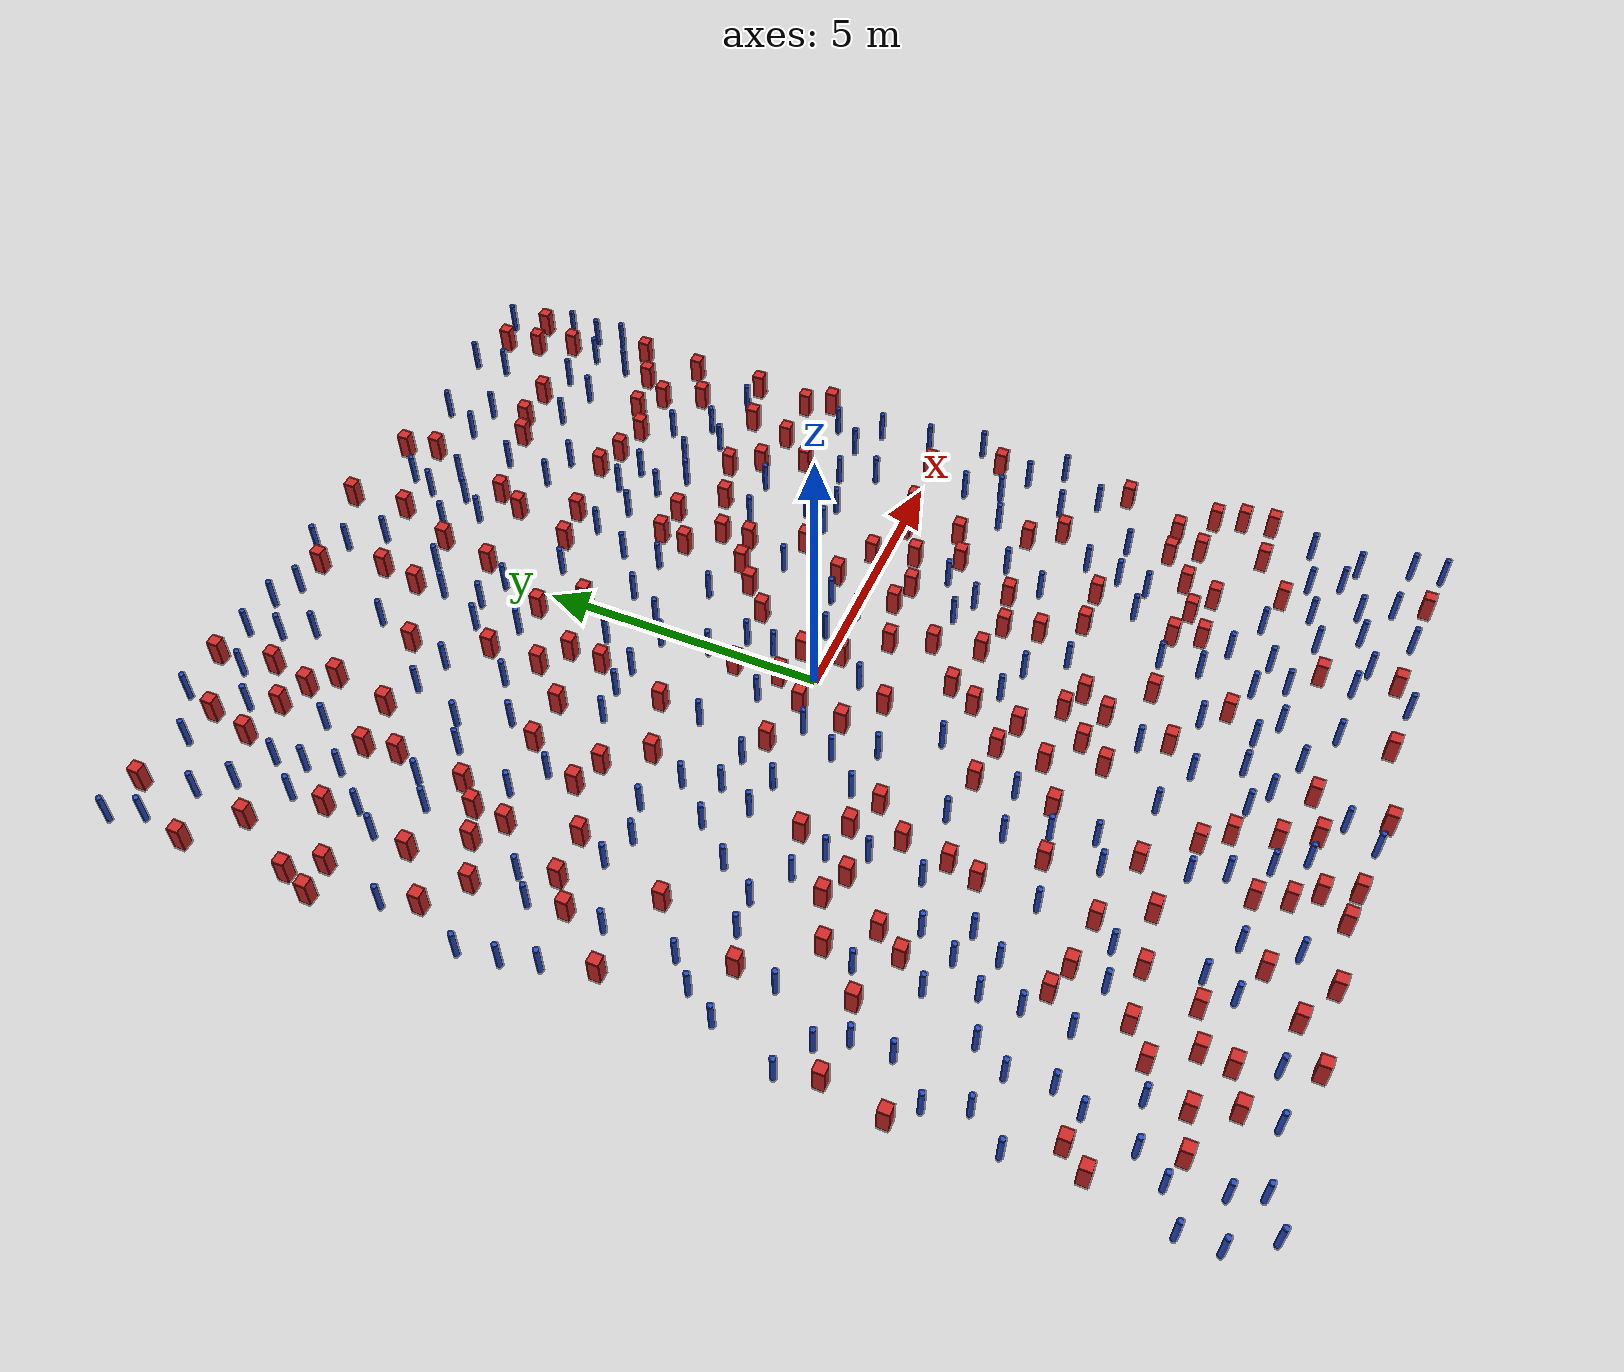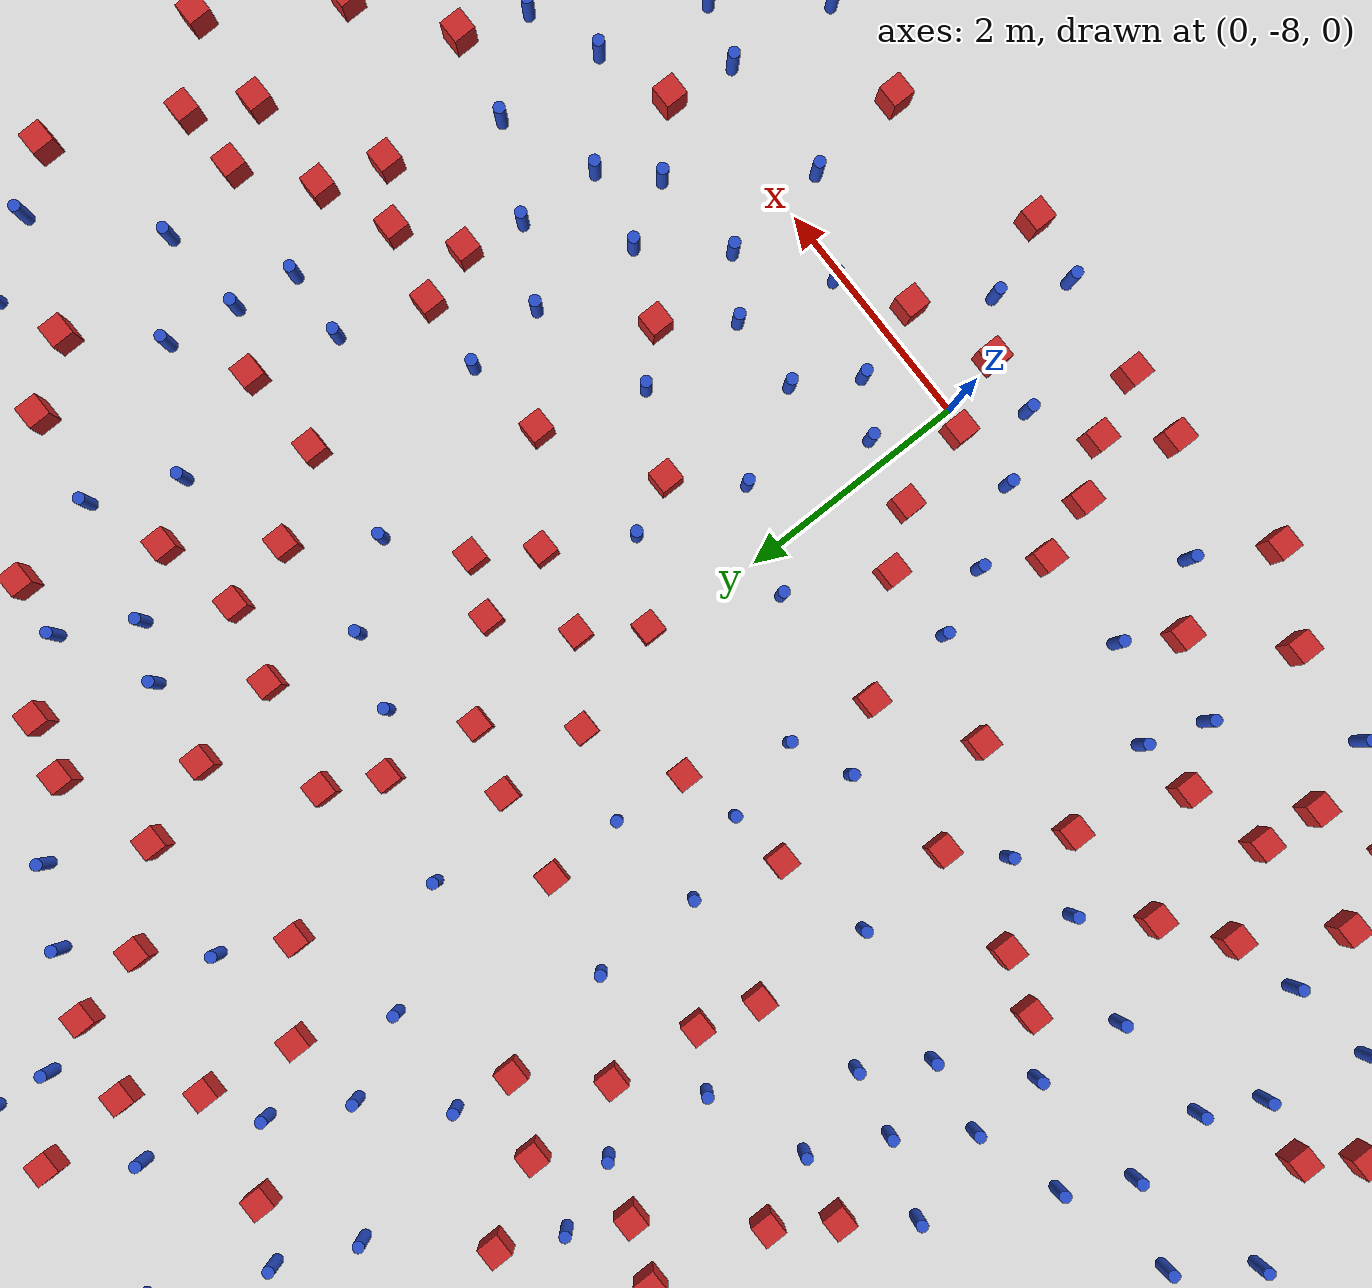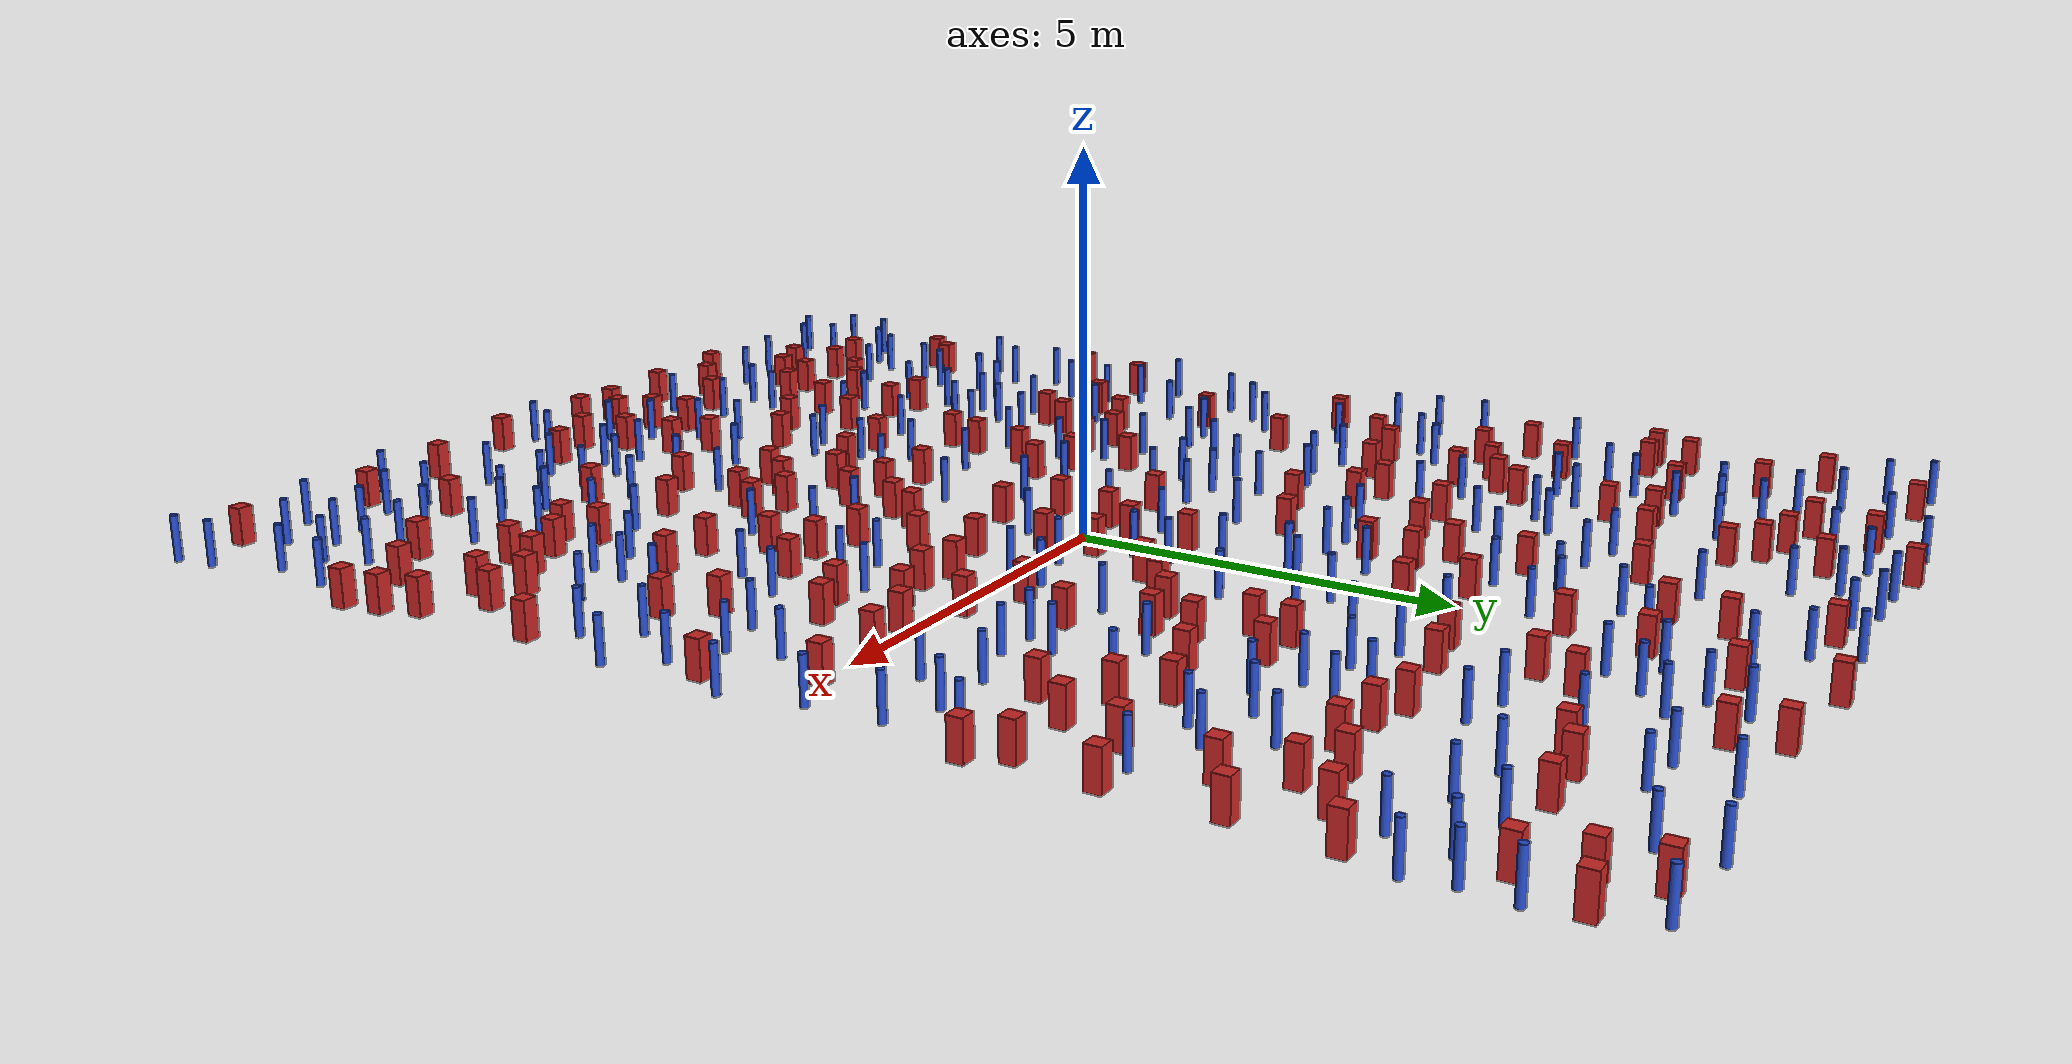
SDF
<sdf version="1.6">
  <model name="dense_8"><model name="square_post_obstacle0">
  <static>true</static>
  <pose frame="">-4.59971297543 3.89152151144 -6.11067671241e-07 -5.50515727128e-06 -8.79689657224e-07 2.37013304536e-05</pose>
  <link name="link">
    <pose frame="">0 0 0.25 0 -0 0</pose>
    <inertial>
      <mass>100</mass>
      <inertia>
        <ixx>0.166667</ixx>
        <ixy>0</ixy>
        <ixz>0</ixz>
        <iyy>0.166667</iyy>
        <iyz>0</iyz>
        <izz>0.166667</izz>
      </inertia>
    </inertial>
    <collision name="collision">
      <geometry>
        <box>
          <size>.2 .2 .5</size>
        </box>
      </geometry>
      <max_contacts>10</max_contacts>
      <surface>
        <contact>
          <ode/>
        </contact>
        <bounce/>
        <friction>
          <torsional>
            <ode/>
          </torsional>
          <ode/>
        </friction>
      </surface>
    </collision>
    <visual name="visual">
      <geometry>
        <box>
          <size>.2 .2 .5</size>
        </box>
      </geometry>
      <material>
        <script>
          <name>Gazebo/Red</name>
          <uri>file://media/materials/scripts/gazebo.material</uri>
        </script>
      </material>
    </visual>
    <self_collide>0</self_collide>
    <kinematic>0</kinematic>
  </link>
</model>
<model name="square_post_obstacle1">
  <static>true</static>
  <pose frame="">-3.34761404719 6.2799041759 -6.11067671241e-07 -5.50515727128e-06 -8.79689657224e-07 2.37013304536e-05</pose>
  <link name="link">
    <pose frame="">0 0 0.25 0 -0 0</pose>
    <inertial>
      <mass>100</mass>
      <inertia>
        <ixx>0.166667</ixx>
        <ixy>0</ixy>
        <ixz>0</ixz>
        <iyy>0.166667</iyy>
        <iyz>0</iyz>
        <izz>0.166667</izz>
      </inertia>
    </inertial>
    <collision name="collision">
      <geometry>
        <box>
          <size>.2 .2 .5</size>
        </box>
      </geometry>
      <max_contacts>10</max_contacts>
      <surface>
        <contact>
          <ode/>
        </contact>
        <bounce/>
        <friction>
          <torsional>
            <ode/>
          </torsional>
          <ode/>
        </friction>
      </surface>
    </collision>
    <visual name="visual">
      <geometry>
        <box>
          <size>.2 .2 .5</size>
        </box>
      </geometry>
      <material>
        <script>
          <name>Gazebo/Red</name>
          <uri>file://media/materials/scripts/gazebo.material</uri>
        </script>
      </material>
    </visual>
    <self_collide>0</self_collide>
    <kinematic>0</kinematic>
  </link>
</model>
<model name="pole_obstacle0">
  <static>true</static>
  <pose frame="">-2.69258866237 8.78360570163 -9.4761961606e-06 5.49618799729e-07 2.36310414e-07 -1.55090534824e-07</pose>
  <link name="link">
  <pose frame="">0 0 0.3 0 -0 0</pose>
    <inertial>
      <mass>1</mass>
      <inertia>
        <ixx>0.145833</ixx>
        <ixy>0</ixy>
        <ixz>0</ixz>
        <iyy>0.145833</iyy>
        <iyz>0</iyz>
        <izz>0.125</izz>
      </inertia>
    </inertial>
    <collision name="collision">
      <geometry>
        <cylinder>
          <radius>0.05</radius>
          <length>.6</length>
        </cylinder>
      </geometry>
      <max_contacts>10</max_contacts>
      <surface>
        <contact>
          <ode/>
        </contact>
        <bounce/>
        <friction>
          <torsional>
            <ode/>
          </torsional>
          <ode/>
        </friction>
      </surface>
    </collision>
    <visual name="visual">
      <geometry>
        <cylinder>
          <radius>0.05</radius>
          <length>.6</length>
        </cylinder>
      </geometry>
      <material>
        <script>
          <name>Gazebo/Blue</name>
          <uri>file://media/materials/scripts/gazebo.material</uri>
        </script>
      </material>
    </visual>
    <self_collide>0</self_collide>
    <kinematic>0</kinematic>
  </link>
</model>
<model name="square_post_obstacle2">
  <static>true</static>
  <pose frame="">2.45403011501 2.84470592228 -6.11067671241e-07 -5.50515727128e-06 -8.79689657224e-07 2.37013304536e-05</pose>
  <link name="link">
    <pose frame="">0 0 0.25 0 -0 0</pose>
    <inertial>
      <mass>100</mass>
      <inertia>
        <ixx>0.166667</ixx>
        <ixy>0</ixy>
        <ixz>0</ixz>
        <iyy>0.166667</iyy>
        <iyz>0</iyz>
        <izz>0.166667</izz>
      </inertia>
    </inertial>
    <collision name="collision">
      <geometry>
        <box>
          <size>.2 .2 .5</size>
        </box>
      </geometry>
      <max_contacts>10</max_contacts>
      <surface>
        <contact>
          <ode/>
        </contact>
        <bounce/>
        <friction>
          <torsional>
            <ode/>
          </torsional>
          <ode/>
        </friction>
      </surface>
    </collision>
    <visual name="visual">
      <geometry>
        <box>
          <size>.2 .2 .5</size>
        </box>
      </geometry>
      <material>
        <script>
          <name>Gazebo/Red</name>
          <uri>file://media/materials/scripts/gazebo.material</uri>
        </script>
      </material>
    </visual>
    <self_collide>0</self_collide>
    <kinematic>0</kinematic>
  </link>
</model>
<model name="pole_obstacle1">
  <static>true</static>
  <pose frame="">-5.38147989765 -4.79862126557 -9.47619616065e-06 5.49618799737e-07 2.36310414037e-07 -1.55090534814e-07</pose>
  <link name="link">
  <pose frame="">0 0 0.3 0 -0 0</pose>
    <inertial>
      <mass>1</mass>
      <inertia>
        <ixx>0.145833</ixx>
        <ixy>0</ixy>
        <ixz>0</ixz>
        <iyy>0.145833</iyy>
        <iyz>0</iyz>
        <izz>0.125</izz>
      </inertia>
    </inertial>
    <collision name="collision">
      <geometry>
        <cylinder>
          <radius>0.05</radius>
          <length>.6</length>
        </cylinder>
      </geometry>
      <max_contacts>10</max_contacts>
      <surface>
        <contact>
          <ode/>
        </contact>
        <bounce/>
        <friction>
          <torsional>
            <ode/>
          </torsional>
          <ode/>
        </friction>
      </surface>
    </collision>
    <visual name="visual">
      <geometry>
        <cylinder>
          <radius>0.05</radius>
          <length>.6</length>
        </cylinder>
      </geometry>
      <material>
        <script>
          <name>Gazebo/Blue</name>
          <uri>file://media/materials/scripts/gazebo.material</uri>
        </script>
      </material>
    </visual>
    <self_collide>0</self_collide>
    <kinematic>0</kinematic>
  </link>
</model>
<model name="square_post_obstacle3">
  <static>true</static>
  <pose frame="">-4.2993784484 -8.27690357602 -6.11067671241e-07 -5.50515727128e-06 -8.79689657224e-07 2.37013304536e-05</pose>
  <link name="link">
    <pose frame="">0 0 0.25 0 -0 0</pose>
    <inertial>
      <mass>100</mass>
      <inertia>
        <ixx>0.166667</ixx>
        <ixy>0</ixy>
        <ixz>0</ixz>
        <iyy>0.166667</iyy>
        <iyz>0</iyz>
        <izz>0.166667</izz>
      </inertia>
    </inertial>
    <collision name="collision">
      <geometry>
        <box>
          <size>.2 .2 .5</size>
        </box>
      </geometry>
      <max_contacts>10</max_contacts>
      <surface>
        <contact>
          <ode/>
        </contact>
        <bounce/>
        <friction>
          <torsional>
            <ode/>
          </torsional>
          <ode/>
        </friction>
      </surface>
    </collision>
    <visual name="visual">
      <geometry>
        <box>
          <size>.2 .2 .5</size>
        </box>
      </geometry>
      <material>
        <script>
          <name>Gazebo/Red</name>
          <uri>file://media/materials/scripts/gazebo.material</uri>
        </script>
      </material>
    </visual>
    <self_collide>0</self_collide>
    <kinematic>0</kinematic>
  </link>
</model>
<model name="pole_obstacle2">
  <static>true</static>
  <pose frame="">5.19550027576 -0.776458486544 -9.47619616065e-06 5.49618799737e-07 2.36310414061e-07 -1.550905348e-07</pose>
  <link name="link">
  <pose frame="">0 0 0.3 0 -0 0</pose>
    <inertial>
      <mass>1</mass>
      <inertia>
        <ixx>0.145833</ixx>
        <ixy>0</ixy>
        <ixz>0</ixz>
        <iyy>0.145833</iyy>
        <iyz>0</iyz>
        <izz>0.125</izz>
      </inertia>
    </inertial>
    <collision name="collision">
      <geometry>
        <cylinder>
          <radius>0.05</radius>
          <length>.6</length>
        </cylinder>
      </geometry>
      <max_contacts>10</max_contacts>
      <surface>
        <contact>
          <ode/>
        </contact>
        <bounce/>
        <friction>
          <torsional>
            <ode/>
          </torsional>
          <ode/>
        </friction>
      </surface>
    </collision>
    <visual name="visual">
      <geometry>
        <cylinder>
          <radius>0.05</radius>
          <length>.6</length>
        </cylinder>
      </geometry>
      <material>
        <script>
          <name>Gazebo/Blue</name>
          <uri>file://media/materials/scripts/gazebo.material</uri>
        </script>
      </material>
    </visual>
    <self_collide>0</self_collide>
    <kinematic>0</kinematic>
  </link>
</model>
<model name="pole_obstacle3">
  <static>true</static>
  <pose frame="">1.60951620101 -0.0953287953253 -9.47619616065e-06 5.49618799737e-07 2.36310414064e-07 -1.55090534798e-07</pose>
  <link name="link">
  <pose frame="">0 0 0.3 0 -0 0</pose>
    <inertial>
      <mass>1</mass>
      <inertia>
        <ixx>0.145833</ixx>
        <ixy>0</ixy>
        <ixz>0</ixz>
        <iyy>0.145833</iyy>
        <iyz>0</iyz>
        <izz>0.125</izz>
      </inertia>
    </inertial>
    <collision name="collision">
      <geometry>
        <cylinder>
          <radius>0.05</radius>
          <length>.6</length>
        </cylinder>
      </geometry>
      <max_contacts>10</max_contacts>
      <surface>
        <contact>
          <ode/>
        </contact>
        <bounce/>
        <friction>
          <torsional>
            <ode/>
          </torsional>
          <ode/>
        </friction>
      </surface>
    </collision>
    <visual name="visual">
      <geometry>
        <cylinder>
          <radius>0.05</radius>
          <length>.6</length>
        </cylinder>
      </geometry>
      <material>
        <script>
          <name>Gazebo/Blue</name>
          <uri>file://media/materials/scripts/gazebo.material</uri>
        </script>
      </material>
    </visual>
    <self_collide>0</self_collide>
    <kinematic>0</kinematic>
  </link>
</model>
<model name="square_post_obstacle4">
  <static>true</static>
  <pose frame="">-3.31677409163 8.47484214785 -6.11067671241e-07 -5.50515727128e-06 -8.79689657224e-07 2.37013304536e-05</pose>
  <link name="link">
    <pose frame="">0 0 0.25 0 -0 0</pose>
    <inertial>
      <mass>100</mass>
      <inertia>
        <ixx>0.166667</ixx>
        <ixy>0</ixy>
        <ixz>0</ixz>
        <iyy>0.166667</iyy>
        <iyz>0</iyz>
        <izz>0.166667</izz>
      </inertia>
    </inertial>
    <collision name="collision">
      <geometry>
        <box>
          <size>.2 .2 .5</size>
        </box>
      </geometry>
      <max_contacts>10</max_contacts>
      <surface>
        <contact>
          <ode/>
        </contact>
        <bounce/>
        <friction>
          <torsional>
            <ode/>
          </torsional>
          <ode/>
        </friction>
      </surface>
    </collision>
    <visual name="visual">
      <geometry>
        <box>
          <size>.2 .2 .5</size>
        </box>
      </geometry>
      <material>
        <script>
          <name>Gazebo/Red</name>
          <uri>file://media/materials/scripts/gazebo.material</uri>
        </script>
      </material>
    </visual>
    <self_collide>0</self_collide>
    <kinematic>0</kinematic>
  </link>
</model>
<model name="square_post_obstacle5">
  <static>true</static>
  <pose frame="">-5.14528673574 3.61344387277 -6.11067671241e-07 -5.50515727128e-06 -8.79689657224e-07 2.37013304536e-05</pose>
  <link name="link">
    <pose frame="">0 0 0.25 0 -0 0</pose>
    <inertial>
      <mass>100</mass>
      <inertia>
        <ixx>0.166667</ixx>
        <ixy>0</ixy>
        <ixz>0</ixz>
        <iyy>0.166667</iyy>
        <iyz>0</iyz>
        <izz>0.166667</izz>
      </inertia>
    </inertial>
    <collision name="collision">
      <geometry>
        <box>
          <size>.2 .2 .5</size>
        </box>
      </geometry>
      <max_contacts>10</max_contacts>
      <surface>
        <contact>
          <ode/>
        </contact>
        <bounce/>
        <friction>
          <torsional>
            <ode/>
          </torsional>
          <ode/>
        </friction>
      </surface>
    </collision>
    <visual name="visual">
      <geometry>
        <box>
          <size>.2 .2 .5</size>
        </box>
      </geometry>
      <material>
        <script>
          <name>Gazebo/Red</name>
          <uri>file://media/materials/scripts/gazebo.material</uri>
        </script>
      </material>
    </visual>
    <self_collide>0</self_collide>
    <kinematic>0</kinematic>
  </link>
</model>
<model name="square_post_obstacle6">
  <static>true</static>
  <pose frame="">6.34076283947 8.5499948869 -6.11067671241e-07 -5.50515727128e-06 -8.79689657224e-07 2.37013304536e-05</pose>
  <link name="link">
    <pose frame="">0 0 0.25 0 -0 0</pose>
    <inertial>
      <mass>100</mass>
      <inertia>
        <ixx>0.166667</ixx>
        <ixy>0</ixy>
        <ixz>0</ixz>
        <iyy>0.166667</iyy>
        <iyz>0</iyz>
        <izz>0.166667</izz>
      </inertia>
    </inertial>
    <collision name="collision">
      <geometry>
        <box>
          <size>.2 .2 .5</size>
        </box>
      </geometry>
      <max_contacts>10</max_contacts>
      <surface>
        <contact>
          <ode/>
        </contact>
        <bounce/>
        <friction>
          <torsional>
            <ode/>
          </torsional>
          <ode/>
        </friction>
      </surface>
    </collision>
    <visual name="visual">
      <geometry>
        <box>
          <size>.2 .2 .5</size>
        </box>
      </geometry>
      <material>
        <script>
          <name>Gazebo/Red</name>
          <uri>file://media/materials/scripts/gazebo.material</uri>
        </script>
      </material>
    </visual>
    <self_collide>0</self_collide>
    <kinematic>0</kinematic>
  </link>
</model>
<model name="pole_obstacle4">
  <static>true</static>
  <pose frame="">-6.62016517235 -4.43141822016 -9.47619616065e-06 5.49618799737e-07 2.36310414037e-07 -1.55090534814e-07</pose>
  <link name="link">
  <pose frame="">0 0 0.3 0 -0 0</pose>
    <inertial>
      <mass>1</mass>
      <inertia>
        <ixx>0.145833</ixx>
        <ixy>0</ixy>
        <ixz>0</ixz>
        <iyy>0.145833</iyy>
        <iyz>0</iyz>
        <izz>0.125</izz>
      </inertia>
    </inertial>
    <collision name="collision">
      <geometry>
        <cylinder>
          <radius>0.05</radius>
          <length>.6</length>
        </cylinder>
      </geometry>
      <max_contacts>10</max_contacts>
      <surface>
        <contact>
          <ode/>
        </contact>
        <bounce/>
        <friction>
          <torsional>
            <ode/>
          </torsional>
          <ode/>
        </friction>
      </surface>
    </collision>
    <visual name="visual">
      <geometry>
        <cylinder>
          <radius>0.05</radius>
          <length>.6</length>
        </cylinder>
      </geometry>
      <material>
        <script>
          <name>Gazebo/Blue</name>
          <uri>file://media/materials/scripts/gazebo.material</uri>
        </script>
      </material>
    </visual>
    <self_collide>0</self_collide>
    <kinematic>0</kinematic>
  </link>
</model>
<model name="pole_obstacle5">
  <static>true</static>
  <pose frame="">0.745613405647 7.6392217286 -9.47619616065e-06 5.49618799737e-07 2.36310414065e-07 -1.55090534796e-07</pose>
  <link name="link">
  <pose frame="">0 0 0.3 0 -0 0</pose>
    <inertial>
      <mass>1</mass>
      <inertia>
        <ixx>0.145833</ixx>
        <ixy>0</ixy>
        <ixz>0</ixz>
        <iyy>0.145833</iyy>
        <iyz>0</iyz>
        <izz>0.125</izz>
      </inertia>
    </inertial>
    <collision name="collision">
      <geometry>
        <cylinder>
          <radius>0.05</radius>
          <length>.6</length>
        </cylinder>
      </geometry>
      <max_contacts>10</max_contacts>
      <surface>
        <contact>
          <ode/>
        </contact>
        <bounce/>
        <friction>
          <torsional>
            <ode/>
          </torsional>
          <ode/>
        </friction>
      </surface>
    </collision>
    <visual name="visual">
      <geometry>
        <cylinder>
          <radius>0.05</radius>
          <length>.6</length>
        </cylinder>
      </geometry>
      <material>
        <script>
          <name>Gazebo/Blue</name>
          <uri>file://media/materials/scripts/gazebo.material</uri>
        </script>
      </material>
    </visual>
    <self_collide>0</self_collide>
    <kinematic>0</kinematic>
  </link>
</model>
<model name="square_post_obstacle7">
  <static>true</static>
  <pose frame="">-3.24468510461 -6.64696252603 -6.11067671241e-07 -5.50515727128e-06 -8.79689657224e-07 2.37013304536e-05</pose>
  <link name="link">
    <pose frame="">0 0 0.25 0 -0 0</pose>
    <inertial>
      <mass>100</mass>
      <inertia>
        <ixx>0.166667</ixx>
        <ixy>0</ixy>
        <ixz>0</ixz>
        <iyy>0.166667</iyy>
        <iyz>0</iyz>
        <izz>0.166667</izz>
      </inertia>
    </inertial>
    <collision name="collision">
      <geometry>
        <box>
          <size>.2 .2 .5</size>
        </box>
      </geometry>
      <max_contacts>10</max_contacts>
      <surface>
        <contact>
          <ode/>
        </contact>
        <bounce/>
        <friction>
          <torsional>
            <ode/>
          </torsional>
          <ode/>
        </friction>
      </surface>
    </collision>
    <visual name="visual">
      <geometry>
        <box>
          <size>.2 .2 .5</size>
        </box>
      </geometry>
      <material>
        <script>
          <name>Gazebo/Red</name>
          <uri>file://media/materials/scripts/gazebo.material</uri>
        </script>
      </material>
    </visual>
    <self_collide>0</self_collide>
    <kinematic>0</kinematic>
  </link>
</model>
<model name="square_post_obstacle8">
  <static>true</static>
  <pose frame="">3.04568365007 0.186025562738 -6.11067671241e-07 -5.50515727128e-06 -8.79689657224e-07 2.37013304536e-05</pose>
  <link name="link">
    <pose frame="">0 0 0.25 0 -0 0</pose>
    <inertial>
      <mass>100</mass>
      <inertia>
        <ixx>0.166667</ixx>
        <ixy>0</ixy>
        <ixz>0</ixz>
        <iyy>0.166667</iyy>
        <iyz>0</iyz>
        <izz>0.166667</izz>
      </inertia>
    </inertial>
    <collision name="collision">
      <geometry>
        <box>
          <size>.2 .2 .5</size>
        </box>
      </geometry>
      <max_contacts>10</max_contacts>
      <surface>
        <contact>
          <ode/>
        </contact>
        <bounce/>
        <friction>
          <torsional>
            <ode/>
          </torsional>
          <ode/>
        </friction>
      </surface>
    </collision>
    <visual name="visual">
      <geometry>
        <box>
          <size>.2 .2 .5</size>
        </box>
      </geometry>
      <material>
        <script>
          <name>Gazebo/Red</name>
          <uri>file://media/materials/scripts/gazebo.material</uri>
        </script>
      </material>
    </visual>
    <self_collide>0</self_collide>
    <kinematic>0</kinematic>
  </link>
</model>
<model name="pole_obstacle6">
  <static>true</static>
  <pose frame="">0.202433005379 -7.33911236088 -9.47619616065e-06 5.49618799737e-07 2.36310414069e-07 -1.55090534795e-07</pose>
  <link name="link">
  <pose frame="">0 0 0.3 0 -0 0</pose>
    <inertial>
      <mass>1</mass>
      <inertia>
        <ixx>0.145833</ixx>
        <ixy>0</ixy>
        <ixz>0</ixz>
        <iyy>0.145833</iyy>
        <iyz>0</iyz>
        <izz>0.125</izz>
      </inertia>
    </inertial>
    <collision name="collision">
      <geometry>
        <cylinder>
          <radius>0.05</radius>
          <length>.6</length>
        </cylinder>
      </geometry>
      <max_contacts>10</max_contacts>
      <surface>
        <contact>
          <ode/>
        </contact>
        <bounce/>
        <friction>
          <torsional>
            <ode/>
          </torsional>
          <ode/>
        </friction>
      </surface>
    </collision>
    <visual name="visual">
      <geometry>
        <cylinder>
          <radius>0.05</radius>
          <length>.6</length>
        </cylinder>
      </geometry>
      <material>
        <script>
          <name>Gazebo/Blue</name>
          <uri>file://media/materials/scripts/gazebo.material</uri>
        </script>
      </material>
    </visual>
    <self_collide>0</self_collide>
    <kinematic>0</kinematic>
  </link>
</model>
<model name="pole_obstacle7">
  <static>true</static>
  <pose frame="">-2.09122257601 9.34044556513 -9.4761961606e-06 5.49618799729e-07 2.36310414e-07 -1.55090534824e-07</pose>
  <link name="link">
  <pose frame="">0 0 0.3 0 -0 0</pose>
    <inertial>
      <mass>1</mass>
      <inertia>
        <ixx>0.145833</ixx>
        <ixy>0</ixy>
        <ixz>0</ixz>
        <iyy>0.145833</iyy>
        <iyz>0</iyz>
        <izz>0.125</izz>
      </inertia>
    </inertial>
    <collision name="collision">
      <geometry>
        <cylinder>
          <radius>0.05</radius>
          <length>.6</length>
        </cylinder>
      </geometry>
      <max_contacts>10</max_contacts>
      <surface>
        <contact>
          <ode/>
        </contact>
        <bounce/>
        <friction>
          <torsional>
            <ode/>
          </torsional>
          <ode/>
        </friction>
      </surface>
    </collision>
    <visual name="visual">
      <geometry>
        <cylinder>
          <radius>0.05</radius>
          <length>.6</length>
        </cylinder>
      </geometry>
      <material>
        <script>
          <name>Gazebo/Blue</name>
          <uri>file://media/materials/scripts/gazebo.material</uri>
        </script>
      </material>
    </visual>
    <self_collide>0</self_collide>
    <kinematic>0</kinematic>
  </link>
</model>
<model name="square_post_obstacle9">
  <static>true</static>
  <pose frame="">2.64092734206 3.82460072823 -6.11067671241e-07 -5.50515727128e-06 -8.79689657224e-07 2.37013304536e-05</pose>
  <link name="link">
    <pose frame="">0 0 0.25 0 -0 0</pose>
    <inertial>
      <mass>100</mass>
      <inertia>
        <ixx>0.166667</ixx>
        <ixy>0</ixy>
        <ixz>0</ixz>
        <iyy>0.166667</iyy>
        <iyz>0</iyz>
        <izz>0.166667</izz>
      </inertia>
    </inertial>
    <collision name="collision">
      <geometry>
        <box>
          <size>.2 .2 .5</size>
        </box>
      </geometry>
      <max_contacts>10</max_contacts>
      <surface>
        <contact>
          <ode/>
        </contact>
        <bounce/>
        <friction>
          <torsional>
            <ode/>
          </torsional>
          <ode/>
        </friction>
      </surface>
    </collision>
    <visual name="visual">
      <geometry>
        <box>
          <size>.2 .2 .5</size>
        </box>
      </geometry>
      <material>
        <script>
          <name>Gazebo/Red</name>
          <uri>file://media/materials/scripts/gazebo.material</uri>
        </script>
      </material>
    </visual>
    <self_collide>0</self_collide>
    <kinematic>0</kinematic>
  </link>
</model>
<model name="square_post_obstacle10">
  <static>true</static>
  <pose frame="">-6.77359267373 -2.97860575413 -6.11067671241e-07 -5.50515727128e-06 -8.79689657224e-07 2.37013304536e-05</pose>
  <link name="link">
    <pose frame="">0 0 0.25 0 -0 0</pose>
    <inertial>
      <mass>100</mass>
      <inertia>
        <ixx>0.166667</ixx>
        <ixy>0</ixy>
        <ixz>0</ixz>
        <iyy>0.166667</iyy>
        <iyz>0</iyz>
        <izz>0.166667</izz>
      </inertia>
    </inertial>
    <collision name="collision">
      <geometry>
        <box>
          <size>.2 .2 .5</size>
        </box>
      </geometry>
      <max_contacts>10</max_contacts>
      <surface>
        <contact>
          <ode/>
        </contact>
        <bounce/>
        <friction>
          <torsional>
            <ode/>
          </torsional>
          <ode/>
        </friction>
      </surface>
    </collision>
    <visual name="visual">
      <geometry>
        <box>
          <size>.2 .2 .5</size>
        </box>
      </geometry>
      <material>
        <script>
          <name>Gazebo/Red</name>
          <uri>file://media/materials/scripts/gazebo.material</uri>
        </script>
      </material>
    </visual>
    <self_collide>0</self_collide>
    <kinematic>0</kinematic>
  </link>
</model>
<model name="square_post_obstacle11">
  <static>true</static>
  <pose frame="">0.16159493465 6.35200790539 -6.11067671241e-07 -5.50515727128e-06 -8.79689657224e-07 2.37013304536e-05</pose>
  <link name="link">
    <pose frame="">0 0 0.25 0 -0 0</pose>
    <inertial>
      <mass>100</mass>
      <inertia>
        <ixx>0.166667</ixx>
        <ixy>0</ixy>
        <ixz>0</ixz>
        <iyy>0.166667</iyy>
        <iyz>0</iyz>
        <izz>0.166667</izz>
      </inertia>
    </inertial>
    <collision name="collision">
      <geometry>
        <box>
          <size>.2 .2 .5</size>
        </box>
      </geometry>
      <max_contacts>10</max_contacts>
      <surface>
        <contact>
          <ode/>
        </contact>
        <bounce/>
        <friction>
          <torsional>
            <ode/>
          </torsional>
          <ode/>
        </friction>
      </surface>
    </collision>
    <visual name="visual">
      <geometry>
        <box>
          <size>.2 .2 .5</size>
        </box>
      </geometry>
      <material>
        <script>
          <name>Gazebo/Red</name>
          <uri>file://media/materials/scripts/gazebo.material</uri>
        </script>
      </material>
    </visual>
    <self_collide>0</self_collide>
    <kinematic>0</kinematic>
  </link>
</model>
<model name="square_post_obstacle12">
  <static>true</static>
  <pose frame="">5.60025701304 9.02206502396 -6.11067671241e-07 -5.50515727128e-06 -8.79689657224e-07 2.37013304536e-05</pose>
  <link name="link">
    <pose frame="">0 0 0.25 0 -0 0</pose>
    <inertial>
      <mass>100</mass>
      <inertia>
        <ixx>0.166667</ixx>
        <ixy>0</ixy>
        <ixz>0</ixz>
        <iyy>0.166667</iyy>
        <iyz>0</iyz>
        <izz>0.166667</izz>
      </inertia>
    </inertial>
    <collision name="collision">
      <geometry>
        <box>
          <size>.2 .2 .5</size>
        </box>
      </geometry>
      <max_contacts>10</max_contacts>
      <surface>
        <contact>
          <ode/>
        </contact>
        <bounce/>
        <friction>
          <torsional>
            <ode/>
          </torsional>
          <ode/>
        </friction>
      </surface>
    </collision>
    <visual name="visual">
      <geometry>
        <box>
          <size>.2 .2 .5</size>
        </box>
      </geometry>
      <material>
        <script>
          <name>Gazebo/Red</name>
          <uri>file://media/materials/scripts/gazebo.material</uri>
        </script>
      </material>
    </visual>
    <self_collide>0</self_collide>
    <kinematic>0</kinematic>
  </link>
</model>
<model name="square_post_obstacle13">
  <static>true</static>
  <pose frame="">-1.29914973282 -9.2488651199 -6.11067671241e-07 -5.50515727128e-06 -8.79689657224e-07 2.37013304536e-05</pose>
  <link name="link">
    <pose frame="">0 0 0.25 0 -0 0</pose>
    <inertial>
      <mass>100</mass>
      <inertia>
        <ixx>0.166667</ixx>
        <ixy>0</ixy>
        <ixz>0</ixz>
        <iyy>0.166667</iyy>
        <iyz>0</iyz>
        <izz>0.166667</izz>
      </inertia>
    </inertial>
    <collision name="collision">
      <geometry>
        <box>
          <size>.2 .2 .5</size>
        </box>
      </geometry>
      <max_contacts>10</max_contacts>
      <surface>
        <contact>
          <ode/>
        </contact>
        <bounce/>
        <friction>
          <torsional>
            <ode/>
          </torsional>
          <ode/>
        </friction>
      </surface>
    </collision>
    <visual name="visual">
      <geometry>
        <box>
          <size>.2 .2 .5</size>
        </box>
      </geometry>
      <material>
        <script>
          <name>Gazebo/Red</name>
          <uri>file://media/materials/scripts/gazebo.material</uri>
        </script>
      </material>
    </visual>
    <self_collide>0</self_collide>
    <kinematic>0</kinematic>
  </link>
</model>
<model name="pole_obstacle8">
  <static>true</static>
  <pose frame="">-5.80131505727 2.28319129758 -9.47619616065e-06 5.49618799738e-07 2.36310414051e-07 -1.55090534805e-07</pose>
  <link name="link">
  <pose frame="">0 0 0.3 0 -0 0</pose>
    <inertial>
      <mass>1</mass>
      <inertia>
        <ixx>0.145833</ixx>
        <ixy>0</ixy>
        <ixz>0</ixz>
        <iyy>0.145833</iyy>
        <iyz>0</iyz>
        <izz>0.125</izz>
      </inertia>
    </inertial>
    <collision name="collision">
      <geometry>
        <cylinder>
          <radius>0.05</radius>
          <length>.6</length>
        </cylinder>
      </geometry>
      <max_contacts>10</max_contacts>
      <surface>
        <contact>
          <ode/>
        </contact>
        <bounce/>
        <friction>
          <torsional>
            <ode/>
          </torsional>
          <ode/>
        </friction>
      </surface>
    </collision>
    <visual name="visual">
      <geometry>
        <cylinder>
          <radius>0.05</radius>
          <length>.6</length>
        </cylinder>
      </geometry>
      <material>
        <script>
          <name>Gazebo/Blue</name>
          <uri>file://media/materials/scripts/gazebo.material</uri>
        </script>
      </material>
    </visual>
    <self_collide>0</self_collide>
    <kinematic>0</kinematic>
  </link>
</model>
<model name="square_post_obstacle14">
  <static>true</static>
  <pose frame="">-2.59733417661 -1.70808143457 -6.11067671241e-07 -5.50515727128e-06 -8.79689657224e-07 2.37013304536e-05</pose>
  <link name="link">
    <pose frame="">0 0 0.25 0 -0 0</pose>
    <inertial>
      <mass>100</mass>
      <inertia>
        <ixx>0.166667</ixx>
        <ixy>0</ixy>
        <ixz>0</ixz>
        <iyy>0.166667</iyy>
        <iyz>0</iyz>
        <izz>0.166667</izz>
      </inertia>
    </inertial>
    <collision name="collision">
      <geometry>
        <box>
          <size>.2 .2 .5</size>
        </box>
      </geometry>
      <max_contacts>10</max_contacts>
      <surface>
        <contact>
          <ode/>
        </contact>
        <bounce/>
        <friction>
          <torsional>
            <ode/>
          </torsional>
          <ode/>
        </friction>
      </surface>
    </collision>
    <visual name="visual">
      <geometry>
        <box>
          <size>.2 .2 .5</size>
        </box>
      </geometry>
      <material>
        <script>
          <name>Gazebo/Red</name>
          <uri>file://media/materials/scripts/gazebo.material</uri>
        </script>
      </material>
    </visual>
    <self_collide>0</self_collide>
    <kinematic>0</kinematic>
  </link>
</model>
<model name="square_post_obstacle15">
  <static>true</static>
  <pose frame="">1.47501391211 -1.55873065129 -6.11067671241e-07 -5.50515727128e-06 -8.79689657224e-07 2.37013304536e-05</pose>
  <link name="link">
    <pose frame="">0 0 0.25 0 -0 0</pose>
    <inertial>
      <mass>100</mass>
      <inertia>
        <ixx>0.166667</ixx>
        <ixy>0</ixy>
        <ixz>0</ixz>
        <iyy>0.166667</iyy>
        <iyz>0</iyz>
        <izz>0.166667</izz>
      </inertia>
    </inertial>
    <collision name="collision">
      <geometry>
        <box>
          <size>.2 .2 .5</size>
        </box>
      </geometry>
      <max_contacts>10</max_contacts>
      <surface>
        <contact>
          <ode/>
        </contact>
        <bounce/>
        <friction>
          <torsional>
            <ode/>
          </torsional>
          <ode/>
        </friction>
      </surface>
    </collision>
    <visual name="visual">
      <geometry>
        <box>
          <size>.2 .2 .5</size>
        </box>
      </geometry>
      <material>
        <script>
          <name>Gazebo/Red</name>
          <uri>file://media/materials/scripts/gazebo.material</uri>
        </script>
      </material>
    </visual>
    <self_collide>0</self_collide>
    <kinematic>0</kinematic>
  </link>
</model>
<model name="square_post_obstacle16">
  <static>true</static>
  <pose frame="">-5.19287735996 -7.88013842331 -6.11067671241e-07 -5.50515727128e-06 -8.79689657224e-07 2.37013304536e-05</pose>
  <link name="link">
    <pose frame="">0 0 0.25 0 -0 0</pose>
    <inertial>
      <mass>100</mass>
      <inertia>
        <ixx>0.166667</ixx>
        <ixy>0</ixy>
        <ixz>0</ixz>
        <iyy>0.166667</iyy>
        <iyz>0</iyz>
        <izz>0.166667</izz>
      </inertia>
    </inertial>
    <collision name="collision">
      <geometry>
        <box>
          <size>.2 .2 .5</size>
        </box>
      </geometry>
      <max_contacts>10</max_contacts>
      <surface>
        <contact>
          <ode/>
        </contact>
        <bounce/>
        <friction>
          <torsional>
            <ode/>
          </torsional>
          <ode/>
        </friction>
      </surface>
    </collision>
    <visual name="visual">
      <geometry>
        <box>
          <size>.2 .2 .5</size>
        </box>
      </geometry>
      <material>
        <script>
          <name>Gazebo/Red</name>
          <uri>file://media/materials/scripts/gazebo.material</uri>
        </script>
      </material>
    </visual>
    <self_collide>0</self_collide>
    <kinematic>0</kinematic>
  </link>
</model>
<model name="pole_obstacle9">
  <static>true</static>
  <pose frame="">0.166897559963 3.05602028141 -9.4761961606e-06 5.49618799729e-07 2.36310413998e-07 -1.55090534824e-07</pose>
  <link name="link">
  <pose frame="">0 0 0.3 0 -0 0</pose>
    <inertial>
      <mass>1</mass>
      <inertia>
        <ixx>0.145833</ixx>
        <ixy>0</ixy>
        <ixz>0</ixz>
        <iyy>0.145833</iyy>
        <iyz>0</iyz>
        <izz>0.125</izz>
      </inertia>
    </inertial>
    <collision name="collision">
      <geometry>
        <cylinder>
          <radius>0.05</radius>
          <length>.6</length>
        </cylinder>
      </geometry>
      <max_contacts>10</max_contacts>
      <surface>
        <contact>
          <ode/>
        </contact>
        <bounce/>
        <friction>
          <torsional>
            <ode/>
          </torsional>
          <ode/>
        </friction>
      </surface>
    </collision>
    <visual name="visual">
      <geometry>
        <cylinder>
          <radius>0.05</radius>
          <length>.6</length>
        </cylinder>
      </geometry>
      <material>
        <script>
          <name>Gazebo/Blue</name>
          <uri>file://media/materials/scripts/gazebo.material</uri>
        </script>
      </material>
    </visual>
    <self_collide>0</self_collide>
    <kinematic>0</kinematic>
  </link>
</model>
<model name="square_post_obstacle17">
  <static>true</static>
  <pose frame="">-4.97605530294 0.397946088873 -6.11067671241e-07 -5.50515727128e-06 -8.79689657224e-07 2.37013304536e-05</pose>
  <link name="link">
    <pose frame="">0 0 0.25 0 -0 0</pose>
    <inertial>
      <mass>100</mass>
      <inertia>
        <ixx>0.166667</ixx>
        <ixy>0</ixy>
        <ixz>0</ixz>
        <iyy>0.166667</iyy>
        <iyz>0</iyz>
        <izz>0.166667</izz>
      </inertia>
    </inertial>
    <collision name="collision">
      <geometry>
        <box>
          <size>.2 .2 .5</size>
        </box>
      </geometry>
      <max_contacts>10</max_contacts>
      <surface>
        <contact>
          <ode/>
        </contact>
        <bounce/>
        <friction>
          <torsional>
            <ode/>
          </torsional>
          <ode/>
        </friction>
      </surface>
    </collision>
    <visual name="visual">
      <geometry>
        <box>
          <size>.2 .2 .5</size>
        </box>
      </geometry>
      <material>
        <script>
          <name>Gazebo/Red</name>
          <uri>file://media/materials/scripts/gazebo.material</uri>
        </script>
      </material>
    </visual>
    <self_collide>0</self_collide>
    <kinematic>0</kinematic>
  </link>
</model>
<model name="square_post_obstacle18">
  <static>true</static>
  <pose frame="">-6.67809848744 -6.83257664463 -6.11067671241e-07 -5.50515727128e-06 -8.79689657224e-07 2.37013304536e-05</pose>
  <link name="link">
    <pose frame="">0 0 0.25 0 -0 0</pose>
    <inertial>
      <mass>100</mass>
      <inertia>
        <ixx>0.166667</ixx>
        <ixy>0</ixy>
        <ixz>0</ixz>
        <iyy>0.166667</iyy>
        <iyz>0</iyz>
        <izz>0.166667</izz>
      </inertia>
    </inertial>
    <collision name="collision">
      <geometry>
        <box>
          <size>.2 .2 .5</size>
        </box>
      </geometry>
      <max_contacts>10</max_contacts>
      <surface>
        <contact>
          <ode/>
        </contact>
        <bounce/>
        <friction>
          <torsional>
            <ode/>
          </torsional>
          <ode/>
        </friction>
      </surface>
    </collision>
    <visual name="visual">
      <geometry>
        <box>
          <size>.2 .2 .5</size>
        </box>
      </geometry>
      <material>
        <script>
          <name>Gazebo/Red</name>
          <uri>file://media/materials/scripts/gazebo.material</uri>
        </script>
      </material>
    </visual>
    <self_collide>0</self_collide>
    <kinematic>0</kinematic>
  </link>
</model>
<model name="pole_obstacle10">
  <static>true</static>
  <pose frame="">-0.569666834816 3.63471088129 -9.47619616065e-06 5.49618799737e-07 2.36310414066e-07 -1.55090534797e-07</pose>
  <link name="link">
  <pose frame="">0 0 0.3 0 -0 0</pose>
    <inertial>
      <mass>1</mass>
      <inertia>
        <ixx>0.145833</ixx>
        <ixy>0</ixy>
        <ixz>0</ixz>
        <iyy>0.145833</iyy>
        <iyz>0</iyz>
        <izz>0.125</izz>
      </inertia>
    </inertial>
    <collision name="collision">
      <geometry>
        <cylinder>
          <radius>0.05</radius>
          <length>.6</length>
        </cylinder>
      </geometry>
      <max_contacts>10</max_contacts>
      <surface>
        <contact>
          <ode/>
        </contact>
        <bounce/>
        <friction>
          <torsional>
            <ode/>
          </torsional>
          <ode/>
        </friction>
      </surface>
    </collision>
    <visual name="visual">
      <geometry>
        <cylinder>
          <radius>0.05</radius>
          <length>.6</length>
        </cylinder>
      </geometry>
      <material>
        <script>
          <name>Gazebo/Blue</name>
          <uri>file://media/materials/scripts/gazebo.material</uri>
        </script>
      </material>
    </visual>
    <self_collide>0</self_collide>
    <kinematic>0</kinematic>
  </link>
</model>
<model name="square_post_obstacle19">
  <static>true</static>
  <pose frame="">4.50263359824 -0.0530470735372 -6.11067671241e-07 -5.50515727128e-06 -8.79689657224e-07 2.37013304536e-05</pose>
  <link name="link">
    <pose frame="">0 0 0.25 0 -0 0</pose>
    <inertial>
      <mass>100</mass>
      <inertia>
        <ixx>0.166667</ixx>
        <ixy>0</ixy>
        <ixz>0</ixz>
        <iyy>0.166667</iyy>
        <iyz>0</iyz>
        <izz>0.166667</izz>
      </inertia>
    </inertial>
    <collision name="collision">
      <geometry>
        <box>
          <size>.2 .2 .5</size>
        </box>
      </geometry>
      <max_contacts>10</max_contacts>
      <surface>
        <contact>
          <ode/>
        </contact>
        <bounce/>
        <friction>
          <torsional>
            <ode/>
          </torsional>
          <ode/>
        </friction>
      </surface>
    </collision>
    <visual name="visual">
      <geometry>
        <box>
          <size>.2 .2 .5</size>
        </box>
      </geometry>
      <material>
        <script>
          <name>Gazebo/Red</name>
          <uri>file://media/materials/scripts/gazebo.material</uri>
        </script>
      </material>
    </visual>
    <self_collide>0</self_collide>
    <kinematic>0</kinematic>
  </link>
</model>
<model name="pole_obstacle11">
  <static>true</static>
  <pose frame="">4.00027393497 4.34988775769 -9.47619616065e-06 5.49618799737e-07 2.36310414037e-07 -1.55090534814e-07</pose>
  <link name="link">
  <pose frame="">0 0 0.3 0 -0 0</pose>
    <inertial>
      <mass>1</mass>
      <inertia>
        <ixx>0.145833</ixx>
        <ixy>0</ixy>
        <ixz>0</ixz>
        <iyy>0.145833</iyy>
        <iyz>0</iyz>
        <izz>0.125</izz>
      </inertia>
    </inertial>
    <collision name="collision">
      <geometry>
        <cylinder>
          <radius>0.05</radius>
          <length>.6</length>
        </cylinder>
      </geometry>
      <max_contacts>10</max_contacts>
      <surface>
        <contact>
          <ode/>
        </contact>
        <bounce/>
        <friction>
          <torsional>
            <ode/>
          </torsional>
          <ode/>
        </friction>
      </surface>
    </collision>
    <visual name="visual">
      <geometry>
        <cylinder>
          <radius>0.05</radius>
          <length>.6</length>
        </cylinder>
      </geometry>
      <material>
        <script>
          <name>Gazebo/Blue</name>
          <uri>file://media/materials/scripts/gazebo.material</uri>
        </script>
      </material>
    </visual>
    <self_collide>0</self_collide>
    <kinematic>0</kinematic>
  </link>
</model>
<model name="square_post_obstacle20">
  <static>true</static>
  <pose frame="">1.99056706824 -6.56412992524 -6.11067671241e-07 -5.50515727128e-06 -8.79689657224e-07 2.37013304536e-05</pose>
  <link name="link">
    <pose frame="">0 0 0.25 0 -0 0</pose>
    <inertial>
      <mass>100</mass>
      <inertia>
        <ixx>0.166667</ixx>
        <ixy>0</ixy>
        <ixz>0</ixz>
        <iyy>0.166667</iyy>
        <iyz>0</iyz>
        <izz>0.166667</izz>
      </inertia>
    </inertial>
    <collision name="collision">
      <geometry>
        <box>
          <size>.2 .2 .5</size>
        </box>
      </geometry>
      <max_contacts>10</max_contacts>
      <surface>
        <contact>
          <ode/>
        </contact>
        <bounce/>
        <friction>
          <torsional>
            <ode/>
          </torsional>
          <ode/>
        </friction>
      </surface>
    </collision>
    <visual name="visual">
      <geometry>
        <box>
          <size>.2 .2 .5</size>
        </box>
      </geometry>
      <material>
        <script>
          <name>Gazebo/Red</name>
          <uri>file://media/materials/scripts/gazebo.material</uri>
        </script>
      </material>
    </visual>
    <self_collide>0</self_collide>
    <kinematic>0</kinematic>
  </link>
</model>
<model name="pole_obstacle12">
  <static>true</static>
  <pose frame="">-0.222761955069 7.18345360372 -9.47619616065e-06 5.49618799737e-07 2.36310414064e-07 -1.55090534799e-07</pose>
  <link name="link">
  <pose frame="">0 0 0.3 0 -0 0</pose>
    <inertial>
      <mass>1</mass>
      <inertia>
        <ixx>0.145833</ixx>
        <ixy>0</ixy>
        <ixz>0</ixz>
        <iyy>0.145833</iyy>
        <iyz>0</iyz>
        <izz>0.125</izz>
      </inertia>
    </inertial>
    <collision name="collision">
      <geometry>
        <cylinder>
          <radius>0.05</radius>
          <length>.6</length>
        </cylinder>
      </geometry>
      <max_contacts>10</max_contacts>
      <surface>
        <contact>
          <ode/>
        </contact>
        <bounce/>
        <friction>
          <torsional>
            <ode/>
          </torsional>
          <ode/>
        </friction>
      </surface>
    </collision>
    <visual name="visual">
      <geometry>
        <cylinder>
          <radius>0.05</radius>
          <length>.6</length>
        </cylinder>
      </geometry>
      <material>
        <script>
          <name>Gazebo/Blue</name>
          <uri>file://media/materials/scripts/gazebo.material</uri>
        </script>
      </material>
    </visual>
    <self_collide>0</self_collide>
    <kinematic>0</kinematic>
  </link>
</model>
<model name="square_post_obstacle21">
  <static>true</static>
  <pose frame="">0.481305501082 -2.64464810082 -6.11067671241e-07 -5.50515727128e-06 -8.79689657224e-07 2.37013304536e-05</pose>
  <link name="link">
    <pose frame="">0 0 0.25 0 -0 0</pose>
    <inertial>
      <mass>100</mass>
      <inertia>
        <ixx>0.166667</ixx>
        <ixy>0</ixy>
        <ixz>0</ixz>
        <iyy>0.166667</iyy>
        <iyz>0</iyz>
        <izz>0.166667</izz>
      </inertia>
    </inertial>
    <collision name="collision">
      <geometry>
        <box>
          <size>.2 .2 .5</size>
        </box>
      </geometry>
      <max_contacts>10</max_contacts>
      <surface>
        <contact>
          <ode/>
        </contact>
        <bounce/>
        <friction>
          <torsional>
            <ode/>
          </torsional>
          <ode/>
        </friction>
      </surface>
    </collision>
    <visual name="visual">
      <geometry>
        <box>
          <size>.2 .2 .5</size>
        </box>
      </geometry>
      <material>
        <script>
          <name>Gazebo/Red</name>
          <uri>file://media/materials/scripts/gazebo.material</uri>
        </script>
      </material>
    </visual>
    <self_collide>0</self_collide>
    <kinematic>0</kinematic>
  </link>
</model>
<model name="pole_obstacle13">
  <static>true</static>
  <pose frame="">-4.43546107212 5.02161070864 -9.47619616065e-06 5.49618799737e-07 2.36310414037e-07 -1.55090534814e-07</pose>
  <link name="link">
  <pose frame="">0 0 0.3 0 -0 0</pose>
    <inertial>
      <mass>1</mass>
      <inertia>
        <ixx>0.145833</ixx>
        <ixy>0</ixy>
        <ixz>0</ixz>
        <iyy>0.145833</iyy>
        <iyz>0</iyz>
        <izz>0.125</izz>
      </inertia>
    </inertial>
    <collision name="collision">
      <geometry>
        <cylinder>
          <radius>0.05</radius>
          <length>.6</length>
        </cylinder>
      </geometry>
      <max_contacts>10</max_contacts>
      <surface>
        <contact>
          <ode/>
        </contact>
        <bounce/>
        <friction>
          <torsional>
            <ode/>
          </torsional>
          <ode/>
        </friction>
      </surface>
    </collision>
    <visual name="visual">
      <geometry>
        <cylinder>
          <radius>0.05</radius>
          <length>.6</length>
        </cylinder>
      </geometry>
      <material>
        <script>
          <name>Gazebo/Blue</name>
          <uri>file://media/materials/scripts/gazebo.material</uri>
        </script>
      </material>
    </visual>
    <self_collide>0</self_collide>
    <kinematic>0</kinematic>
  </link>
</model>
<model name="square_post_obstacle22">
  <static>true</static>
  <pose frame="">-2.71512669858 -5.74736953656 -6.11067671241e-07 -5.50515727128e-06 -8.79689657224e-07 2.37013304536e-05</pose>
  <link name="link">
    <pose frame="">0 0 0.25 0 -0 0</pose>
    <inertial>
      <mass>100</mass>
      <inertia>
        <ixx>0.166667</ixx>
        <ixy>0</ixy>
        <ixz>0</ixz>
        <iyy>0.166667</iyy>
        <iyz>0</iyz>
        <izz>0.166667</izz>
      </inertia>
    </inertial>
    <collision name="collision">
      <geometry>
        <box>
          <size>.2 .2 .5</size>
        </box>
      </geometry>
      <max_contacts>10</max_contacts>
      <surface>
        <contact>
          <ode/>
        </contact>
        <bounce/>
        <friction>
          <torsional>
            <ode/>
          </torsional>
          <ode/>
        </friction>
      </surface>
    </collision>
    <visual name="visual">
      <geometry>
        <box>
          <size>.2 .2 .5</size>
        </box>
      </geometry>
      <material>
        <script>
          <name>Gazebo/Red</name>
          <uri>file://media/materials/scripts/gazebo.material</uri>
        </script>
      </material>
    </visual>
    <self_collide>0</self_collide>
    <kinematic>0</kinematic>
  </link>
</model>
<model name="pole_obstacle14">
  <static>true</static>
  <pose frame="">-5.64300418187 7.66119199296 -9.47619616065e-06 5.49618799737e-07 2.36310414037e-07 -1.55090534814e-07</pose>
  <link name="link">
  <pose frame="">0 0 0.3 0 -0 0</pose>
    <inertial>
      <mass>1</mass>
      <inertia>
        <ixx>0.145833</ixx>
        <ixy>0</ixy>
        <ixz>0</ixz>
        <iyy>0.145833</iyy>
        <iyz>0</iyz>
        <izz>0.125</izz>
      </inertia>
    </inertial>
    <collision name="collision">
      <geometry>
        <cylinder>
          <radius>0.05</radius>
          <length>.6</length>
        </cylinder>
      </geometry>
      <max_contacts>10</max_contacts>
      <surface>
        <contact>
          <ode/>
        </contact>
        <bounce/>
        <friction>
          <torsional>
            <ode/>
          </torsional>
          <ode/>
        </friction>
      </surface>
    </collision>
    <visual name="visual">
      <geometry>
        <cylinder>
          <radius>0.05</radius>
          <length>.6</length>
        </cylinder>
      </geometry>
      <material>
        <script>
          <name>Gazebo/Blue</name>
          <uri>file://media/materials/scripts/gazebo.material</uri>
        </script>
      </material>
    </visual>
    <self_collide>0</self_collide>
    <kinematic>0</kinematic>
  </link>
</model>
<model name="pole_obstacle15">
  <static>true</static>
  <pose frame="">-2.82085442692 -4.86616058618 -9.47619616065e-06 5.49618799738e-07 2.3631041406e-07 -1.55090534801e-07</pose>
  <link name="link">
  <pose frame="">0 0 0.3 0 -0 0</pose>
    <inertial>
      <mass>1</mass>
      <inertia>
        <ixx>0.145833</ixx>
        <ixy>0</ixy>
        <ixz>0</ixz>
        <iyy>0.145833</iyy>
        <iyz>0</iyz>
        <izz>0.125</izz>
      </inertia>
    </inertial>
    <collision name="collision">
      <geometry>
        <cylinder>
          <radius>0.05</radius>
          <length>.6</length>
        </cylinder>
      </geometry>
      <max_contacts>10</max_contacts>
      <surface>
        <contact>
          <ode/>
        </contact>
        <bounce/>
        <friction>
          <torsional>
            <ode/>
          </torsional>
          <ode/>
        </friction>
      </surface>
    </collision>
    <visual name="visual">
      <geometry>
        <cylinder>
          <radius>0.05</radius>
          <length>.6</length>
        </cylinder>
      </geometry>
      <material>
        <script>
          <name>Gazebo/Blue</name>
          <uri>file://media/materials/scripts/gazebo.material</uri>
        </script>
      </material>
    </visual>
    <self_collide>0</self_collide>
    <kinematic>0</kinematic>
  </link>
</model>
<model name="pole_obstacle16">
  <static>true</static>
  <pose frame="">-1.92999631986 -1.45536469944 -9.47619616065e-06 5.49618799737e-07 2.36310414065e-07 -1.55090534798e-07</pose>
  <link name="link">
  <pose frame="">0 0 0.3 0 -0 0</pose>
    <inertial>
      <mass>1</mass>
      <inertia>
        <ixx>0.145833</ixx>
        <ixy>0</ixy>
        <ixz>0</ixz>
        <iyy>0.145833</iyy>
        <iyz>0</iyz>
        <izz>0.125</izz>
      </inertia>
    </inertial>
    <collision name="collision">
      <geometry>
        <cylinder>
          <radius>0.05</radius>
          <length>.6</length>
        </cylinder>
      </geometry>
      <max_contacts>10</max_contacts>
      <surface>
        <contact>
          <ode/>
        </contact>
        <bounce/>
        <friction>
          <torsional>
            <ode/>
          </torsional>
          <ode/>
        </friction>
      </surface>
    </collision>
    <visual name="visual">
      <geometry>
        <cylinder>
          <radius>0.05</radius>
          <length>.6</length>
        </cylinder>
      </geometry>
      <material>
        <script>
          <name>Gazebo/Blue</name>
          <uri>file://media/materials/scripts/gazebo.material</uri>
        </script>
      </material>
    </visual>
    <self_collide>0</self_collide>
    <kinematic>0</kinematic>
  </link>
</model>
<model name="square_post_obstacle23">
  <static>true</static>
  <pose frame="">-0.0821357140511 -1.2840179583 -6.11067671241e-07 -5.50515727128e-06 -8.79689657224e-07 2.37013304536e-05</pose>
  <link name="link">
    <pose frame="">0 0 0.25 0 -0 0</pose>
    <inertial>
      <mass>100</mass>
      <inertia>
        <ixx>0.166667</ixx>
        <ixy>0</ixy>
        <ixz>0</ixz>
        <iyy>0.166667</iyy>
        <iyz>0</iyz>
        <izz>0.166667</izz>
      </inertia>
    </inertial>
    <collision name="collision">
      <geometry>
        <box>
          <size>.2 .2 .5</size>
        </box>
      </geometry>
      <max_contacts>10</max_contacts>
      <surface>
        <contact>
          <ode/>
        </contact>
        <bounce/>
        <friction>
          <torsional>
            <ode/>
          </torsional>
          <ode/>
        </friction>
      </surface>
    </collision>
    <visual name="visual">
      <geometry>
        <box>
          <size>.2 .2 .5</size>
        </box>
      </geometry>
      <material>
        <script>
          <name>Gazebo/Red</name>
          <uri>file://media/materials/scripts/gazebo.material</uri>
        </script>
      </material>
    </visual>
    <self_collide>0</self_collide>
    <kinematic>0</kinematic>
  </link>
</model>
<model name="pole_obstacle17">
  <static>true</static>
  <pose frame="">0.529014926173 -6.34254856775 -9.47619616065e-06 5.49618799737e-07 2.36310414064e-07 -1.55090534796e-07</pose>
  <link name="link">
  <pose frame="">0 0 0.3 0 -0 0</pose>
    <inertial>
      <mass>1</mass>
      <inertia>
        <ixx>0.145833</ixx>
        <ixy>0</ixy>
        <ixz>0</ixz>
        <iyy>0.145833</iyy>
        <iyz>0</iyz>
        <izz>0.125</izz>
      </inertia>
    </inertial>
    <collision name="collision">
      <geometry>
        <cylinder>
          <radius>0.05</radius>
          <length>.6</length>
        </cylinder>
      </geometry>
      <max_contacts>10</max_contacts>
      <surface>
        <contact>
          <ode/>
        </contact>
        <bounce/>
        <friction>
          <torsional>
            <ode/>
          </torsional>
          <ode/>
        </friction>
      </surface>
    </collision>
    <visual name="visual">
      <geometry>
        <cylinder>
          <radius>0.05</radius>
          <length>.6</length>
        </cylinder>
      </geometry>
      <material>
        <script>
          <name>Gazebo/Blue</name>
          <uri>file://media/materials/scripts/gazebo.material</uri>
        </script>
      </material>
    </visual>
    <self_collide>0</self_collide>
    <kinematic>0</kinematic>
  </link>
</model>
<model name="square_post_obstacle24">
  <static>true</static>
  <pose frame="">6.39824471717 -5.68714983444 -6.11067671241e-07 -5.50515727128e-06 -8.79689657224e-07 2.37013304536e-05</pose>
  <link name="link">
    <pose frame="">0 0 0.25 0 -0 0</pose>
    <inertial>
      <mass>100</mass>
      <inertia>
        <ixx>0.166667</ixx>
        <ixy>0</ixy>
        <ixz>0</ixz>
        <iyy>0.166667</iyy>
        <iyz>0</iyz>
        <izz>0.166667</izz>
      </inertia>
    </inertial>
    <collision name="collision">
      <geometry>
        <box>
          <size>.2 .2 .5</size>
        </box>
      </geometry>
      <max_contacts>10</max_contacts>
      <surface>
        <contact>
          <ode/>
        </contact>
        <bounce/>
        <friction>
          <torsional>
            <ode/>
          </torsional>
          <ode/>
        </friction>
      </surface>
    </collision>
    <visual name="visual">
      <geometry>
        <box>
          <size>.2 .2 .5</size>
        </box>
      </geometry>
      <material>
        <script>
          <name>Gazebo/Red</name>
          <uri>file://media/materials/scripts/gazebo.material</uri>
        </script>
      </material>
    </visual>
    <self_collide>0</self_collide>
    <kinematic>0</kinematic>
  </link>
</model>
<model name="square_post_obstacle25">
  <static>true</static>
  <pose frame="">-2.75030509881 -3.86803217672 -6.11067671241e-07 -5.50515727128e-06 -8.79689657224e-07 2.37013304536e-05</pose>
  <link name="link">
    <pose frame="">0 0 0.25 0 -0 0</pose>
    <inertial>
      <mass>100</mass>
      <inertia>
        <ixx>0.166667</ixx>
        <ixy>0</ixy>
        <ixz>0</ixz>
        <iyy>0.166667</iyy>
        <iyz>0</iyz>
        <izz>0.166667</izz>
      </inertia>
    </inertial>
    <collision name="collision">
      <geometry>
        <box>
          <size>.2 .2 .5</size>
        </box>
      </geometry>
      <max_contacts>10</max_contacts>
      <surface>
        <contact>
          <ode/>
        </contact>
        <bounce/>
        <friction>
          <torsional>
            <ode/>
          </torsional>
          <ode/>
        </friction>
      </surface>
    </collision>
    <visual name="visual">
      <geometry>
        <box>
          <size>.2 .2 .5</size>
        </box>
      </geometry>
      <material>
        <script>
          <name>Gazebo/Red</name>
          <uri>file://media/materials/scripts/gazebo.material</uri>
        </script>
      </material>
    </visual>
    <self_collide>0</self_collide>
    <kinematic>0</kinematic>
  </link>
</model>
<model name="square_post_obstacle26">
  <static>true</static>
  <pose frame="">-1.48058931634 2.1476353197 -6.11067671241e-07 -5.50515727128e-06 -8.79689657224e-07 2.37013304536e-05</pose>
  <link name="link">
    <pose frame="">0 0 0.25 0 -0 0</pose>
    <inertial>
      <mass>100</mass>
      <inertia>
        <ixx>0.166667</ixx>
        <ixy>0</ixy>
        <ixz>0</ixz>
        <iyy>0.166667</iyy>
        <iyz>0</iyz>
        <izz>0.166667</izz>
      </inertia>
    </inertial>
    <collision name="collision">
      <geometry>
        <box>
          <size>.2 .2 .5</size>
        </box>
      </geometry>
      <max_contacts>10</max_contacts>
      <surface>
        <contact>
          <ode/>
        </contact>
        <bounce/>
        <friction>
          <torsional>
            <ode/>
          </torsional>
          <ode/>
        </friction>
      </surface>
    </collision>
    <visual name="visual">
      <geometry>
        <box>
          <size>.2 .2 .5</size>
        </box>
      </geometry>
      <material>
        <script>
          <name>Gazebo/Red</name>
          <uri>file://media/materials/scripts/gazebo.material</uri>
        </script>
      </material>
    </visual>
    <self_collide>0</self_collide>
    <kinematic>0</kinematic>
  </link>
</model>
<model name="square_post_obstacle27">
  <static>true</static>
  <pose frame="">2.30890300831 0.54974141371 -6.11067671241e-07 -5.50515727128e-06 -8.79689657224e-07 2.37013304536e-05</pose>
  <link name="link">
    <pose frame="">0 0 0.25 0 -0 0</pose>
    <inertial>
      <mass>100</mass>
      <inertia>
        <ixx>0.166667</ixx>
        <ixy>0</ixy>
        <ixz>0</ixz>
        <iyy>0.166667</iyy>
        <iyz>0</iyz>
        <izz>0.166667</izz>
      </inertia>
    </inertial>
    <collision name="collision">
      <geometry>
        <box>
          <size>.2 .2 .5</size>
        </box>
      </geometry>
      <max_contacts>10</max_contacts>
      <surface>
        <contact>
          <ode/>
        </contact>
        <bounce/>
        <friction>
          <torsional>
            <ode/>
          </torsional>
          <ode/>
        </friction>
      </surface>
    </collision>
    <visual name="visual">
      <geometry>
        <box>
          <size>.2 .2 .5</size>
        </box>
      </geometry>
      <material>
        <script>
          <name>Gazebo/Red</name>
          <uri>file://media/materials/scripts/gazebo.material</uri>
        </script>
      </material>
    </visual>
    <self_collide>0</self_collide>
    <kinematic>0</kinematic>
  </link>
</model>
<model name="pole_obstacle18">
  <static>true</static>
  <pose frame="">-3.16564307549 5.06302007915 -9.47619616065e-06 5.49618799738e-07 2.3631041406e-07 -1.55090534801e-07</pose>
  <link name="link">
  <pose frame="">0 0 0.3 0 -0 0</pose>
    <inertial>
      <mass>1</mass>
      <inertia>
        <ixx>0.145833</ixx>
        <ixy>0</ixy>
        <ixz>0</ixz>
        <iyy>0.145833</iyy>
        <iyz>0</iyz>
        <izz>0.125</izz>
      </inertia>
    </inertial>
    <collision name="collision">
      <geometry>
        <cylinder>
          <radius>0.05</radius>
          <length>.6</length>
        </cylinder>
      </geometry>
      <max_contacts>10</max_contacts>
      <surface>
        <contact>
          <ode/>
        </contact>
        <bounce/>
        <friction>
          <torsional>
            <ode/>
          </torsional>
          <ode/>
        </friction>
      </surface>
    </collision>
    <visual name="visual">
      <geometry>
        <cylinder>
          <radius>0.05</radius>
          <length>.6</length>
        </cylinder>
      </geometry>
      <material>
        <script>
          <name>Gazebo/Blue</name>
          <uri>file://media/materials/scripts/gazebo.material</uri>
        </script>
      </material>
    </visual>
    <self_collide>0</self_collide>
    <kinematic>0</kinematic>
  </link>
</model>
<model name="square_post_obstacle28">
  <static>true</static>
  <pose frame="">-5.69607947928 4.42945014952 -6.11067671241e-07 -5.50515727128e-06 -8.79689657224e-07 2.37013304536e-05</pose>
  <link name="link">
    <pose frame="">0 0 0.25 0 -0 0</pose>
    <inertial>
      <mass>100</mass>
      <inertia>
        <ixx>0.166667</ixx>
        <ixy>0</ixy>
        <ixz>0</ixz>
        <iyy>0.166667</iyy>
        <iyz>0</iyz>
        <izz>0.166667</izz>
      </inertia>
    </inertial>
    <collision name="collision">
      <geometry>
        <box>
          <size>.2 .2 .5</size>
        </box>
      </geometry>
      <max_contacts>10</max_contacts>
      <surface>
        <contact>
          <ode/>
        </contact>
        <bounce/>
        <friction>
          <torsional>
            <ode/>
          </torsional>
          <ode/>
        </friction>
      </surface>
    </collision>
    <visual name="visual">
      <geometry>
        <box>
          <size>.2 .2 .5</size>
        </box>
      </geometry>
      <material>
        <script>
          <name>Gazebo/Red</name>
          <uri>file://media/materials/scripts/gazebo.material</uri>
        </script>
      </material>
    </visual>
    <self_collide>0</self_collide>
    <kinematic>0</kinematic>
  </link>
</model>
<model name="pole_obstacle19">
  <static>true</static>
  <pose frame="">-3.7670166189 -1.22346130769 -9.47619616065e-06 5.49618799737e-07 2.36310414072e-07 -1.55090534793e-07</pose>
  <link name="link">
  <pose frame="">0 0 0.3 0 -0 0</pose>
    <inertial>
      <mass>1</mass>
      <inertia>
        <ixx>0.145833</ixx>
        <ixy>0</ixy>
        <ixz>0</ixz>
        <iyy>0.145833</iyy>
        <iyz>0</iyz>
        <izz>0.125</izz>
      </inertia>
    </inertial>
    <collision name="collision">
      <geometry>
        <cylinder>
          <radius>0.05</radius>
          <length>.6</length>
        </cylinder>
      </geometry>
      <max_contacts>10</max_contacts>
      <surface>
        <contact>
          <ode/>
        </contact>
        <bounce/>
        <friction>
          <torsional>
            <ode/>
          </torsional>
          <ode/>
        </friction>
      </surface>
    </collision>
    <visual name="visual">
      <geometry>
        <cylinder>
          <radius>0.05</radius>
          <length>.6</length>
        </cylinder>
      </geometry>
      <material>
        <script>
          <name>Gazebo/Blue</name>
          <uri>file://media/materials/scripts/gazebo.material</uri>
        </script>
      </material>
    </visual>
    <self_collide>0</self_collide>
    <kinematic>0</kinematic>
  </link>
</model>
<model name="square_post_obstacle29">
  <static>true</static>
  <pose frame="">-4.40070211339 2.09543112315 -6.11067671241e-07 -5.50515727128e-06 -8.79689657224e-07 2.37013304536e-05</pose>
  <link name="link">
    <pose frame="">0 0 0.25 0 -0 0</pose>
    <inertial>
      <mass>100</mass>
      <inertia>
        <ixx>0.166667</ixx>
        <ixy>0</ixy>
        <ixz>0</ixz>
        <iyy>0.166667</iyy>
        <iyz>0</iyz>
        <izz>0.166667</izz>
      </inertia>
    </inertial>
    <collision name="collision">
      <geometry>
        <box>
          <size>.2 .2 .5</size>
        </box>
      </geometry>
      <max_contacts>10</max_contacts>
      <surface>
        <contact>
          <ode/>
        </contact>
        <bounce/>
        <friction>
          <torsional>
            <ode/>
          </torsional>
          <ode/>
        </friction>
      </surface>
    </collision>
    <visual name="visual">
      <geometry>
        <box>
          <size>.2 .2 .5</size>
        </box>
      </geometry>
      <material>
        <script>
          <name>Gazebo/Red</name>
          <uri>file://media/materials/scripts/gazebo.material</uri>
        </script>
      </material>
    </visual>
    <self_collide>0</self_collide>
    <kinematic>0</kinematic>
  </link>
</model>
<model name="square_post_obstacle30">
  <static>true</static>
  <pose frame="">1.79112847933 7.00552808204 -6.11067671241e-07 -5.50515727128e-06 -8.79689657224e-07 2.37013304536e-05</pose>
  <link name="link">
    <pose frame="">0 0 0.25 0 -0 0</pose>
    <inertial>
      <mass>100</mass>
      <inertia>
        <ixx>0.166667</ixx>
        <ixy>0</ixy>
        <ixz>0</ixz>
        <iyy>0.166667</iyy>
        <iyz>0</iyz>
        <izz>0.166667</izz>
      </inertia>
    </inertial>
    <collision name="collision">
      <geometry>
        <box>
          <size>.2 .2 .5</size>
        </box>
      </geometry>
      <max_contacts>10</max_contacts>
      <surface>
        <contact>
          <ode/>
        </contact>
        <bounce/>
        <friction>
          <torsional>
            <ode/>
          </torsional>
          <ode/>
        </friction>
      </surface>
    </collision>
    <visual name="visual">
      <geometry>
        <box>
          <size>.2 .2 .5</size>
        </box>
      </geometry>
      <material>
        <script>
          <name>Gazebo/Red</name>
          <uri>file://media/materials/scripts/gazebo.material</uri>
        </script>
      </material>
    </visual>
    <self_collide>0</self_collide>
    <kinematic>0</kinematic>
  </link>
</model>
<model name="pole_obstacle20">
  <static>true</static>
  <pose frame="">4.18166565589 -4.01385830783 -9.47619616065e-06 5.49618799737e-07 2.36310414037e-07 -1.55090534813e-07</pose>
  <link name="link">
  <pose frame="">0 0 0.3 0 -0 0</pose>
    <inertial>
      <mass>1</mass>
      <inertia>
        <ixx>0.145833</ixx>
        <ixy>0</ixy>
        <ixz>0</ixz>
        <iyy>0.145833</iyy>
        <iyz>0</iyz>
        <izz>0.125</izz>
      </inertia>
    </inertial>
    <collision name="collision">
      <geometry>
        <cylinder>
          <radius>0.05</radius>
          <length>.6</length>
        </cylinder>
      </geometry>
      <max_contacts>10</max_contacts>
      <surface>
        <contact>
          <ode/>
        </contact>
        <bounce/>
        <friction>
          <torsional>
            <ode/>
          </torsional>
          <ode/>
        </friction>
      </surface>
    </collision>
    <visual name="visual">
      <geometry>
        <cylinder>
          <radius>0.05</radius>
          <length>.6</length>
        </cylinder>
      </geometry>
      <material>
        <script>
          <name>Gazebo/Blue</name>
          <uri>file://media/materials/scripts/gazebo.material</uri>
        </script>
      </material>
    </visual>
    <self_collide>0</self_collide>
    <kinematic>0</kinematic>
  </link>
</model>
<model name="pole_obstacle21">
  <static>true</static>
  <pose frame="">-0.156886062178 5.84629662768 -9.47619616065e-06 5.49618799737e-07 2.36310414062e-07 -1.550905348e-07</pose>
  <link name="link">
  <pose frame="">0 0 0.3 0 -0 0</pose>
    <inertial>
      <mass>1</mass>
      <inertia>
        <ixx>0.145833</ixx>
        <ixy>0</ixy>
        <ixz>0</ixz>
        <iyy>0.145833</iyy>
        <iyz>0</iyz>
        <izz>0.125</izz>
      </inertia>
    </inertial>
    <collision name="collision">
      <geometry>
        <cylinder>
          <radius>0.05</radius>
          <length>.6</length>
        </cylinder>
      </geometry>
      <max_contacts>10</max_contacts>
      <surface>
        <contact>
          <ode/>
        </contact>
        <bounce/>
        <friction>
          <torsional>
            <ode/>
          </torsional>
          <ode/>
        </friction>
      </surface>
    </collision>
    <visual name="visual">
      <geometry>
        <cylinder>
          <radius>0.05</radius>
          <length>.6</length>
        </cylinder>
      </geometry>
      <material>
        <script>
          <name>Gazebo/Blue</name>
          <uri>file://media/materials/scripts/gazebo.material</uri>
        </script>
      </material>
    </visual>
    <self_collide>0</self_collide>
    <kinematic>0</kinematic>
  </link>
</model>
<model name="square_post_obstacle31">
  <static>true</static>
  <pose frame="">-5.23875331345 2.03464342423 -6.11067671241e-07 -5.50515727128e-06 -8.79689657224e-07 2.37013304536e-05</pose>
  <link name="link">
    <pose frame="">0 0 0.25 0 -0 0</pose>
    <inertial>
      <mass>100</mass>
      <inertia>
        <ixx>0.166667</ixx>
        <ixy>0</ixy>
        <ixz>0</ixz>
        <iyy>0.166667</iyy>
        <iyz>0</iyz>
        <izz>0.166667</izz>
      </inertia>
    </inertial>
    <collision name="collision">
      <geometry>
        <box>
          <size>.2 .2 .5</size>
        </box>
      </geometry>
      <max_contacts>10</max_contacts>
      <surface>
        <contact>
          <ode/>
        </contact>
        <bounce/>
        <friction>
          <torsional>
            <ode/>
          </torsional>
          <ode/>
        </friction>
      </surface>
    </collision>
    <visual name="visual">
      <geometry>
        <box>
          <size>.2 .2 .5</size>
        </box>
      </geometry>
      <material>
        <script>
          <name>Gazebo/Red</name>
          <uri>file://media/materials/scripts/gazebo.material</uri>
        </script>
      </material>
    </visual>
    <self_collide>0</self_collide>
    <kinematic>0</kinematic>
  </link>
</model>
<model name="pole_obstacle22">
  <static>true</static>
  <pose frame="">0.340326180801 1.39975027802 -9.47619616065e-06 5.49618799738e-07 2.3631041406e-07 -1.550905348e-07</pose>
  <link name="link">
  <pose frame="">0 0 0.3 0 -0 0</pose>
    <inertial>
      <mass>1</mass>
      <inertia>
        <ixx>0.145833</ixx>
        <ixy>0</ixy>
        <ixz>0</ixz>
        <iyy>0.145833</iyy>
        <iyz>0</iyz>
        <izz>0.125</izz>
      </inertia>
    </inertial>
    <collision name="collision">
      <geometry>
        <cylinder>
          <radius>0.05</radius>
          <length>.6</length>
        </cylinder>
      </geometry>
      <max_contacts>10</max_contacts>
      <surface>
        <contact>
          <ode/>
        </contact>
        <bounce/>
        <friction>
          <torsional>
            <ode/>
          </torsional>
          <ode/>
        </friction>
      </surface>
    </collision>
    <visual name="visual">
      <geometry>
        <cylinder>
          <radius>0.05</radius>
          <length>.6</length>
        </cylinder>
      </geometry>
      <material>
        <script>
          <name>Gazebo/Blue</name>
          <uri>file://media/materials/scripts/gazebo.material</uri>
        </script>
      </material>
    </visual>
    <self_collide>0</self_collide>
    <kinematic>0</kinematic>
  </link>
</model>
<model name="pole_obstacle23">
  <static>true</static>
  <pose frame="">-3.62183732038 8.9275067447 -9.4761961606e-06 5.49618799729e-07 2.36310414e-07 -1.55090534824e-07</pose>
  <link name="link">
  <pose frame="">0 0 0.3 0 -0 0</pose>
    <inertial>
      <mass>1</mass>
      <inertia>
        <ixx>0.145833</ixx>
        <ixy>0</ixy>
        <ixz>0</ixz>
        <iyy>0.145833</iyy>
        <iyz>0</iyz>
        <izz>0.125</izz>
      </inertia>
    </inertial>
    <collision name="collision">
      <geometry>
        <cylinder>
          <radius>0.05</radius>
          <length>.6</length>
        </cylinder>
      </geometry>
      <max_contacts>10</max_contacts>
      <surface>
        <contact>
          <ode/>
        </contact>
        <bounce/>
        <friction>
          <torsional>
            <ode/>
          </torsional>
          <ode/>
        </friction>
      </surface>
    </collision>
    <visual name="visual">
      <geometry>
        <cylinder>
          <radius>0.05</radius>
          <length>.6</length>
        </cylinder>
      </geometry>
      <material>
        <script>
          <name>Gazebo/Blue</name>
          <uri>file://media/materials/scripts/gazebo.material</uri>
        </script>
      </material>
    </visual>
    <self_collide>0</self_collide>
    <kinematic>0</kinematic>
  </link>
</model>
<model name="pole_obstacle24">
  <static>true</static>
  <pose frame="">1.38895360051 -7.91625873299 -9.47619616065e-06 5.49618799737e-07 2.36310414061e-07 -1.550905348e-07</pose>
  <link name="link">
  <pose frame="">0 0 0.3 0 -0 0</pose>
    <inertial>
      <mass>1</mass>
      <inertia>
        <ixx>0.145833</ixx>
        <ixy>0</ixy>
        <ixz>0</ixz>
        <iyy>0.145833</iyy>
        <iyz>0</iyz>
        <izz>0.125</izz>
      </inertia>
    </inertial>
    <collision name="collision">
      <geometry>
        <cylinder>
          <radius>0.05</radius>
          <length>.6</length>
        </cylinder>
      </geometry>
      <max_contacts>10</max_contacts>
      <surface>
        <contact>
          <ode/>
        </contact>
        <bounce/>
        <friction>
          <torsional>
            <ode/>
          </torsional>
          <ode/>
        </friction>
      </surface>
    </collision>
    <visual name="visual">
      <geometry>
        <cylinder>
          <radius>0.05</radius>
          <length>.6</length>
        </cylinder>
      </geometry>
      <material>
        <script>
          <name>Gazebo/Blue</name>
          <uri>file://media/materials/scripts/gazebo.material</uri>
        </script>
      </material>
    </visual>
    <self_collide>0</self_collide>
    <kinematic>0</kinematic>
  </link>
</model>
<model name="pole_obstacle25">
  <static>true</static>
  <pose frame="">-4.68158163636 1.53399339681 -9.47619616065e-06 5.49618799738e-07 2.36310414071e-07 -1.55090534796e-07</pose>
  <link name="link">
  <pose frame="">0 0 0.3 0 -0 0</pose>
    <inertial>
      <mass>1</mass>
      <inertia>
        <ixx>0.145833</ixx>
        <ixy>0</ixy>
        <ixz>0</ixz>
        <iyy>0.145833</iyy>
        <iyz>0</iyz>
        <izz>0.125</izz>
      </inertia>
    </inertial>
    <collision name="collision">
      <geometry>
        <cylinder>
          <radius>0.05</radius>
          <length>.6</length>
        </cylinder>
      </geometry>
      <max_contacts>10</max_contacts>
      <surface>
        <contact>
          <ode/>
        </contact>
        <bounce/>
        <friction>
          <torsional>
            <ode/>
          </torsional>
          <ode/>
        </friction>
      </surface>
    </collision>
    <visual name="visual">
      <geometry>
        <cylinder>
          <radius>0.05</radius>
          <length>.6</length>
        </cylinder>
      </geometry>
      <material>
        <script>
          <name>Gazebo/Blue</name>
          <uri>file://media/materials/scripts/gazebo.material</uri>
        </script>
      </material>
    </visual>
    <self_collide>0</self_collide>
    <kinematic>0</kinematic>
  </link>
</model>
<model name="pole_obstacle26">
  <static>true</static>
  <pose frame="">1.60109463014 -7.09741458702 -9.47619616065e-06 5.49618799737e-07 2.36310414061e-07 -1.550905348e-07</pose>
  <link name="link">
  <pose frame="">0 0 0.3 0 -0 0</pose>
    <inertial>
      <mass>1</mass>
      <inertia>
        <ixx>0.145833</ixx>
        <ixy>0</ixy>
        <ixz>0</ixz>
        <iyy>0.145833</iyy>
        <iyz>0</iyz>
        <izz>0.125</izz>
      </inertia>
    </inertial>
    <collision name="collision">
      <geometry>
        <cylinder>
          <radius>0.05</radius>
          <length>.6</length>
        </cylinder>
      </geometry>
      <max_contacts>10</max_contacts>
      <surface>
        <contact>
          <ode/>
        </contact>
        <bounce/>
        <friction>
          <torsional>
            <ode/>
          </torsional>
          <ode/>
        </friction>
      </surface>
    </collision>
    <visual name="visual">
      <geometry>
        <cylinder>
          <radius>0.05</radius>
          <length>.6</length>
        </cylinder>
      </geometry>
      <material>
        <script>
          <name>Gazebo/Blue</name>
          <uri>file://media/materials/scripts/gazebo.material</uri>
        </script>
      </material>
    </visual>
    <self_collide>0</self_collide>
    <kinematic>0</kinematic>
  </link>
</model>
<model name="pole_obstacle27">
  <static>true</static>
  <pose frame="">1.35018914964 4.2849601545 -9.47619616065e-06 5.49618799737e-07 2.36310414061e-07 -1.550905348e-07</pose>
  <link name="link">
  <pose frame="">0 0 0.3 0 -0 0</pose>
    <inertial>
      <mass>1</mass>
      <inertia>
        <ixx>0.145833</ixx>
        <ixy>0</ixy>
        <ixz>0</ixz>
        <iyy>0.145833</iyy>
        <iyz>0</iyz>
        <izz>0.125</izz>
      </inertia>
    </inertial>
    <collision name="collision">
      <geometry>
        <cylinder>
          <radius>0.05</radius>
          <length>.6</length>
        </cylinder>
      </geometry>
      <max_contacts>10</max_contacts>
      <surface>
        <contact>
          <ode/>
        </contact>
        <bounce/>
        <friction>
          <torsional>
            <ode/>
          </torsional>
          <ode/>
        </friction>
      </surface>
    </collision>
    <visual name="visual">
      <geometry>
        <cylinder>
          <radius>0.05</radius>
          <length>.6</length>
        </cylinder>
      </geometry>
      <material>
        <script>
          <name>Gazebo/Blue</name>
          <uri>file://media/materials/scripts/gazebo.material</uri>
        </script>
      </material>
    </visual>
    <self_collide>0</self_collide>
    <kinematic>0</kinematic>
  </link>
</model>
<model name="square_post_obstacle32">
  <static>true</static>
  <pose frame="">-0.92152964072 -8.76448828151 -6.11067671241e-07 -5.50515727128e-06 -8.79689657224e-07 2.37013304536e-05</pose>
  <link name="link">
    <pose frame="">0 0 0.25 0 -0 0</pose>
    <inertial>
      <mass>100</mass>
      <inertia>
        <ixx>0.166667</ixx>
        <ixy>0</ixy>
        <ixz>0</ixz>
        <iyy>0.166667</iyy>
        <iyz>0</iyz>
        <izz>0.166667</izz>
      </inertia>
    </inertial>
    <collision name="collision">
      <geometry>
        <box>
          <size>.2 .2 .5</size>
        </box>
      </geometry>
      <max_contacts>10</max_contacts>
      <surface>
        <contact>
          <ode/>
        </contact>
        <bounce/>
        <friction>
          <torsional>
            <ode/>
          </torsional>
          <ode/>
        </friction>
      </surface>
    </collision>
    <visual name="visual">
      <geometry>
        <box>
          <size>.2 .2 .5</size>
        </box>
      </geometry>
      <material>
        <script>
          <name>Gazebo/Red</name>
          <uri>file://media/materials/scripts/gazebo.material</uri>
        </script>
      </material>
    </visual>
    <self_collide>0</self_collide>
    <kinematic>0</kinematic>
  </link>
</model>
<model name="square_post_obstacle33">
  <static>true</static>
  <pose frame="">-0.207663381894 -3.29096670335 -6.11067671241e-07 -5.50515727128e-06 -8.79689657224e-07 2.37013304536e-05</pose>
  <link name="link">
    <pose frame="">0 0 0.25 0 -0 0</pose>
    <inertial>
      <mass>100</mass>
      <inertia>
        <ixx>0.166667</ixx>
        <ixy>0</ixy>
        <ixz>0</ixz>
        <iyy>0.166667</iyy>
        <iyz>0</iyz>
        <izz>0.166667</izz>
      </inertia>
    </inertial>
    <collision name="collision">
      <geometry>
        <box>
          <size>.2 .2 .5</size>
        </box>
      </geometry>
      <max_contacts>10</max_contacts>
      <surface>
        <contact>
          <ode/>
        </contact>
        <bounce/>
        <friction>
          <torsional>
            <ode/>
          </torsional>
          <ode/>
        </friction>
      </surface>
    </collision>
    <visual name="visual">
      <geometry>
        <box>
          <size>.2 .2 .5</size>
        </box>
      </geometry>
      <material>
        <script>
          <name>Gazebo/Red</name>
          <uri>file://media/materials/scripts/gazebo.material</uri>
        </script>
      </material>
    </visual>
    <self_collide>0</self_collide>
    <kinematic>0</kinematic>
  </link>
</model>
<model name="pole_obstacle28">
  <static>true</static>
  <pose frame="">4.61884856585 -9.07026900919 -9.47619616065e-06 5.49618799737e-07 2.36310414065e-07 -1.55090534796e-07</pose>
  <link name="link">
  <pose frame="">0 0 0.3 0 -0 0</pose>
    <inertial>
      <mass>1</mass>
      <inertia>
        <ixx>0.145833</ixx>
        <ixy>0</ixy>
        <ixz>0</ixz>
        <iyy>0.145833</iyy>
        <iyz>0</iyz>
        <izz>0.125</izz>
      </inertia>
    </inertial>
    <collision name="collision">
      <geometry>
        <cylinder>
          <radius>0.05</radius>
          <length>.6</length>
        </cylinder>
      </geometry>
      <max_contacts>10</max_contacts>
      <surface>
        <contact>
          <ode/>
        </contact>
        <bounce/>
        <friction>
          <torsional>
            <ode/>
          </torsional>
          <ode/>
        </friction>
      </surface>
    </collision>
    <visual name="visual">
      <geometry>
        <cylinder>
          <radius>0.05</radius>
          <length>.6</length>
        </cylinder>
      </geometry>
      <material>
        <script>
          <name>Gazebo/Blue</name>
          <uri>file://media/materials/scripts/gazebo.material</uri>
        </script>
      </material>
    </visual>
    <self_collide>0</self_collide>
    <kinematic>0</kinematic>
  </link>
</model>
<model name="pole_obstacle29">
  <static>true</static>
  <pose frame="">-5.22662206103 8.88792561754 -9.47619616065e-06 5.49618799737e-07 2.36310414065e-07 -1.55090534796e-07</pose>
  <link name="link">
  <pose frame="">0 0 0.3 0 -0 0</pose>
    <inertial>
      <mass>1</mass>
      <inertia>
        <ixx>0.145833</ixx>
        <ixy>0</ixy>
        <ixz>0</ixz>
        <iyy>0.145833</iyy>
        <iyz>0</iyz>
        <izz>0.125</izz>
      </inertia>
    </inertial>
    <collision name="collision">
      <geometry>
        <cylinder>
          <radius>0.05</radius>
          <length>.6</length>
        </cylinder>
      </geometry>
      <max_contacts>10</max_contacts>
      <surface>
        <contact>
          <ode/>
        </contact>
        <bounce/>
        <friction>
          <torsional>
            <ode/>
          </torsional>
          <ode/>
        </friction>
      </surface>
    </collision>
    <visual name="visual">
      <geometry>
        <cylinder>
          <radius>0.05</radius>
          <length>.6</length>
        </cylinder>
      </geometry>
      <material>
        <script>
          <name>Gazebo/Blue</name>
          <uri>file://media/materials/scripts/gazebo.material</uri>
        </script>
      </material>
    </visual>
    <self_collide>0</self_collide>
    <kinematic>0</kinematic>
  </link>
</model>
<model name="square_post_obstacle34">
  <static>true</static>
  <pose frame="">-4.92881140648 -8.53332998616 -6.11067671241e-07 -5.50515727128e-06 -8.79689657224e-07 2.37013304536e-05</pose>
  <link name="link">
    <pose frame="">0 0 0.25 0 -0 0</pose>
    <inertial>
      <mass>100</mass>
      <inertia>
        <ixx>0.166667</ixx>
        <ixy>0</ixy>
        <ixz>0</ixz>
        <iyy>0.166667</iyy>
        <iyz>0</iyz>
        <izz>0.166667</izz>
      </inertia>
    </inertial>
    <collision name="collision">
      <geometry>
        <box>
          <size>.2 .2 .5</size>
        </box>
      </geometry>
      <max_contacts>10</max_contacts>
      <surface>
        <contact>
          <ode/>
        </contact>
        <bounce/>
        <friction>
          <torsional>
            <ode/>
          </torsional>
          <ode/>
        </friction>
      </surface>
    </collision>
    <visual name="visual">
      <geometry>
        <box>
          <size>.2 .2 .5</size>
        </box>
      </geometry>
      <material>
        <script>
          <name>Gazebo/Red</name>
          <uri>file://media/materials/scripts/gazebo.material</uri>
        </script>
      </material>
    </visual>
    <self_collide>0</self_collide>
    <kinematic>0</kinematic>
  </link>
</model>
<model name="pole_obstacle30">
  <static>true</static>
  <pose frame="">-2.64074661271 0.489076026434 -9.47619616065e-06 5.49618799737e-07 2.36310414078e-07 -1.55090534791e-07</pose>
  <link name="link">
  <pose frame="">0 0 0.3 0 -0 0</pose>
    <inertial>
      <mass>1</mass>
      <inertia>
        <ixx>0.145833</ixx>
        <ixy>0</ixy>
        <ixz>0</ixz>
        <iyy>0.145833</iyy>
        <iyz>0</iyz>
        <izz>0.125</izz>
      </inertia>
    </inertial>
    <collision name="collision">
      <geometry>
        <cylinder>
          <radius>0.05</radius>
          <length>.6</length>
        </cylinder>
      </geometry>
      <max_contacts>10</max_contacts>
      <surface>
        <contact>
          <ode/>
        </contact>
        <bounce/>
        <friction>
          <torsional>
            <ode/>
          </torsional>
          <ode/>
        </friction>
      </surface>
    </collision>
    <visual name="visual">
      <geometry>
        <cylinder>
          <radius>0.05</radius>
          <length>.6</length>
        </cylinder>
      </geometry>
      <material>
        <script>
          <name>Gazebo/Blue</name>
          <uri>file://media/materials/scripts/gazebo.material</uri>
        </script>
      </material>
    </visual>
    <self_collide>0</self_collide>
    <kinematic>0</kinematic>
  </link>
</model>
<model name="pole_obstacle31">
  <static>true</static>
  <pose frame="">-6.87298063366 2.15020737367 -9.47619616065e-06 5.49618799738e-07 2.36310414051e-07 -1.55090534805e-07</pose>
  <link name="link">
  <pose frame="">0 0 0.3 0 -0 0</pose>
    <inertial>
      <mass>1</mass>
      <inertia>
        <ixx>0.145833</ixx>
        <ixy>0</ixy>
        <ixz>0</ixz>
        <iyy>0.145833</iyy>
        <iyz>0</iyz>
        <izz>0.125</izz>
      </inertia>
    </inertial>
    <collision name="collision">
      <geometry>
        <cylinder>
          <radius>0.05</radius>
          <length>.6</length>
        </cylinder>
      </geometry>
      <max_contacts>10</max_contacts>
      <surface>
        <contact>
          <ode/>
        </contact>
        <bounce/>
        <friction>
          <torsional>
            <ode/>
          </torsional>
          <ode/>
        </friction>
      </surface>
    </collision>
    <visual name="visual">
      <geometry>
        <cylinder>
          <radius>0.05</radius>
          <length>.6</length>
        </cylinder>
      </geometry>
      <material>
        <script>
          <name>Gazebo/Blue</name>
          <uri>file://media/materials/scripts/gazebo.material</uri>
        </script>
      </material>
    </visual>
    <self_collide>0</self_collide>
    <kinematic>0</kinematic>
  </link>
</model>
<model name="pole_obstacle32">
  <static>true</static>
  <pose frame="">3.39943327926 9.05926599301 -9.4761961606e-06 5.49618799729e-07 2.36310414e-07 -1.55090534824e-07</pose>
  <link name="link">
  <pose frame="">0 0 0.3 0 -0 0</pose>
    <inertial>
      <mass>1</mass>
      <inertia>
        <ixx>0.145833</ixx>
        <ixy>0</ixy>
        <ixz>0</ixz>
        <iyy>0.145833</iyy>
        <iyz>0</iyz>
        <izz>0.125</izz>
      </inertia>
    </inertial>
    <collision name="collision">
      <geometry>
        <cylinder>
          <radius>0.05</radius>
          <length>.6</length>
        </cylinder>
      </geometry>
      <max_contacts>10</max_contacts>
      <surface>
        <contact>
          <ode/>
        </contact>
        <bounce/>
        <friction>
          <torsional>
            <ode/>
          </torsional>
          <ode/>
        </friction>
      </surface>
    </collision>
    <visual name="visual">
      <geometry>
        <cylinder>
          <radius>0.05</radius>
          <length>.6</length>
        </cylinder>
      </geometry>
      <material>
        <script>
          <name>Gazebo/Blue</name>
          <uri>file://media/materials/scripts/gazebo.material</uri>
        </script>
      </material>
    </visual>
    <self_collide>0</self_collide>
    <kinematic>0</kinematic>
  </link>
</model>
<model name="pole_obstacle33">
  <static>true</static>
  <pose frame="">0.015821319736 8.38703752953 -9.47619616065e-06 5.49618799737e-07 2.36310414039e-07 -1.55090534813e-07</pose>
  <link name="link">
  <pose frame="">0 0 0.3 0 -0 0</pose>
    <inertial>
      <mass>1</mass>
      <inertia>
        <ixx>0.145833</ixx>
        <ixy>0</ixy>
        <ixz>0</ixz>
        <iyy>0.145833</iyy>
        <iyz>0</iyz>
        <izz>0.125</izz>
      </inertia>
    </inertial>
    <collision name="collision">
      <geometry>
        <cylinder>
          <radius>0.05</radius>
          <length>.6</length>
        </cylinder>
      </geometry>
      <max_contacts>10</max_contacts>
      <surface>
        <contact>
          <ode/>
        </contact>
        <bounce/>
        <friction>
          <torsional>
            <ode/>
          </torsional>
          <ode/>
        </friction>
      </surface>
    </collision>
    <visual name="visual">
      <geometry>
        <cylinder>
          <radius>0.05</radius>
          <length>.6</length>
        </cylinder>
      </geometry>
      <material>
        <script>
          <name>Gazebo/Blue</name>
          <uri>file://media/materials/scripts/gazebo.material</uri>
        </script>
      </material>
    </visual>
    <self_collide>0</self_collide>
    <kinematic>0</kinematic>
  </link>
</model>
<model name="square_post_obstacle35">
  <static>true</static>
  <pose frame="">-0.791525722079 7.25611907616 -6.11067671241e-07 -5.50515727128e-06 -8.79689657224e-07 2.37013304536e-05</pose>
  <link name="link">
    <pose frame="">0 0 0.25 0 -0 0</pose>
    <inertial>
      <mass>100</mass>
      <inertia>
        <ixx>0.166667</ixx>
        <ixy>0</ixy>
        <ixz>0</ixz>
        <iyy>0.166667</iyy>
        <iyz>0</iyz>
        <izz>0.166667</izz>
      </inertia>
    </inertial>
    <collision name="collision">
      <geometry>
        <box>
          <size>.2 .2 .5</size>
        </box>
      </geometry>
      <max_contacts>10</max_contacts>
      <surface>
        <contact>
          <ode/>
        </contact>
        <bounce/>
        <friction>
          <torsional>
            <ode/>
          </torsional>
          <ode/>
        </friction>
      </surface>
    </collision>
    <visual name="visual">
      <geometry>
        <box>
          <size>.2 .2 .5</size>
        </box>
      </geometry>
      <material>
        <script>
          <name>Gazebo/Red</name>
          <uri>file://media/materials/scripts/gazebo.material</uri>
        </script>
      </material>
    </visual>
    <self_collide>0</self_collide>
    <kinematic>0</kinematic>
  </link>
</model>
<model name="pole_obstacle34">
  <static>true</static>
  <pose frame="">4.87713090371 8.68399019219 -9.47619616065e-06 5.49618799737e-07 2.36310414065e-07 -1.55090534796e-07</pose>
  <link name="link">
  <pose frame="">0 0 0.3 0 -0 0</pose>
    <inertial>
      <mass>1</mass>
      <inertia>
        <ixx>0.145833</ixx>
        <ixy>0</ixy>
        <ixz>0</ixz>
        <iyy>0.145833</iyy>
        <iyz>0</iyz>
        <izz>0.125</izz>
      </inertia>
    </inertial>
    <collision name="collision">
      <geometry>
        <cylinder>
          <radius>0.05</radius>
          <length>.6</length>
        </cylinder>
      </geometry>
      <max_contacts>10</max_contacts>
      <surface>
        <contact>
          <ode/>
        </contact>
        <bounce/>
        <friction>
          <torsional>
            <ode/>
          </torsional>
          <ode/>
        </friction>
      </surface>
    </collision>
    <visual name="visual">
      <geometry>
        <cylinder>
          <radius>0.05</radius>
          <length>.6</length>
        </cylinder>
      </geometry>
      <material>
        <script>
          <name>Gazebo/Blue</name>
          <uri>file://media/materials/scripts/gazebo.material</uri>
        </script>
      </material>
    </visual>
    <self_collide>0</self_collide>
    <kinematic>0</kinematic>
  </link>
</model>
<model name="pole_obstacle35">
  <static>true</static>
  <pose frame="">-4.77619274611 6.25733308094 -9.47619616065e-06 5.49618799737e-07 2.36310414037e-07 -1.55090534814e-07</pose>
  <link name="link">
  <pose frame="">0 0 0.3 0 -0 0</pose>
    <inertial>
      <mass>1</mass>
      <inertia>
        <ixx>0.145833</ixx>
        <ixy>0</ixy>
        <ixz>0</ixz>
        <iyy>0.145833</iyy>
        <iyz>0</iyz>
        <izz>0.125</izz>
      </inertia>
    </inertial>
    <collision name="collision">
      <geometry>
        <cylinder>
          <radius>0.05</radius>
          <length>.6</length>
        </cylinder>
      </geometry>
      <max_contacts>10</max_contacts>
      <surface>
        <contact>
          <ode/>
        </contact>
        <bounce/>
        <friction>
          <torsional>
            <ode/>
          </torsional>
          <ode/>
        </friction>
      </surface>
    </collision>
    <visual name="visual">
      <geometry>
        <cylinder>
          <radius>0.05</radius>
          <length>.6</length>
        </cylinder>
      </geometry>
      <material>
        <script>
          <name>Gazebo/Blue</name>
          <uri>file://media/materials/scripts/gazebo.material</uri>
        </script>
      </material>
    </visual>
    <self_collide>0</self_collide>
    <kinematic>0</kinematic>
  </link>
</model>
<model name="pole_obstacle36">
  <static>true</static>
  <pose frame="">-1.7950702607 -3.95872133973 -9.47619616065e-06 5.49618799737e-07 2.36310414067e-07 -1.55090534795e-07</pose>
  <link name="link">
  <pose frame="">0 0 0.3 0 -0 0</pose>
    <inertial>
      <mass>1</mass>
      <inertia>
        <ixx>0.145833</ixx>
        <ixy>0</ixy>
        <ixz>0</ixz>
        <iyy>0.145833</iyy>
        <iyz>0</iyz>
        <izz>0.125</izz>
      </inertia>
    </inertial>
    <collision name="collision">
      <geometry>
        <cylinder>
          <radius>0.05</radius>
          <length>.6</length>
        </cylinder>
      </geometry>
      <max_contacts>10</max_contacts>
      <surface>
        <contact>
          <ode/>
        </contact>
        <bounce/>
        <friction>
          <torsional>
            <ode/>
          </torsional>
          <ode/>
        </friction>
      </surface>
    </collision>
    <visual name="visual">
      <geometry>
        <cylinder>
          <radius>0.05</radius>
          <length>.6</length>
        </cylinder>
      </geometry>
      <material>
        <script>
          <name>Gazebo/Blue</name>
          <uri>file://media/materials/scripts/gazebo.material</uri>
        </script>
      </material>
    </visual>
    <self_collide>0</self_collide>
    <kinematic>0</kinematic>
  </link>
</model>
<model name="square_post_obstacle36">
  <static>true</static>
  <pose frame="">-4.47957196386 -3.29003747523 -6.11067671241e-07 -5.50515727128e-06 -8.79689657224e-07 2.37013304536e-05</pose>
  <link name="link">
    <pose frame="">0 0 0.25 0 -0 0</pose>
    <inertial>
      <mass>100</mass>
      <inertia>
        <ixx>0.166667</ixx>
        <ixy>0</ixy>
        <ixz>0</ixz>
        <iyy>0.166667</iyy>
        <iyz>0</iyz>
        <izz>0.166667</izz>
      </inertia>
    </inertial>
    <collision name="collision">
      <geometry>
        <box>
          <size>.2 .2 .5</size>
        </box>
      </geometry>
      <max_contacts>10</max_contacts>
      <surface>
        <contact>
          <ode/>
        </contact>
        <bounce/>
        <friction>
          <torsional>
            <ode/>
          </torsional>
          <ode/>
        </friction>
      </surface>
    </collision>
    <visual name="visual">
      <geometry>
        <box>
          <size>.2 .2 .5</size>
        </box>
      </geometry>
      <material>
        <script>
          <name>Gazebo/Red</name>
          <uri>file://media/materials/scripts/gazebo.material</uri>
        </script>
      </material>
    </visual>
    <self_collide>0</self_collide>
    <kinematic>0</kinematic>
  </link>
</model>
<model name="square_post_obstacle37">
  <static>true</static>
  <pose frame="">2.30294669285 -2.53560770413 -6.11067671241e-07 -5.50515727128e-06 -8.79689657224e-07 2.37013304536e-05</pose>
  <link name="link">
    <pose frame="">0 0 0.25 0 -0 0</pose>
    <inertial>
      <mass>100</mass>
      <inertia>
        <ixx>0.166667</ixx>
        <ixy>0</ixy>
        <ixz>0</ixz>
        <iyy>0.166667</iyy>
        <iyz>0</iyz>
        <izz>0.166667</izz>
      </inertia>
    </inertial>
    <collision name="collision">
      <geometry>
        <box>
          <size>.2 .2 .5</size>
        </box>
      </geometry>
      <max_contacts>10</max_contacts>
      <surface>
        <contact>
          <ode/>
        </contact>
        <bounce/>
        <friction>
          <torsional>
            <ode/>
          </torsional>
          <ode/>
        </friction>
      </surface>
    </collision>
    <visual name="visual">
      <geometry>
        <box>
          <size>.2 .2 .5</size>
        </box>
      </geometry>
      <material>
        <script>
          <name>Gazebo/Red</name>
          <uri>file://media/materials/scripts/gazebo.material</uri>
        </script>
      </material>
    </visual>
    <self_collide>0</self_collide>
    <kinematic>0</kinematic>
  </link>
</model>
<model name="pole_obstacle37">
  <static>true</static>
  <pose frame="">-1.73074676715 7.37955289185 -9.47619616065e-06 5.49618799737e-07 2.36310414061e-07 -1.550905348e-07</pose>
  <link name="link">
  <pose frame="">0 0 0.3 0 -0 0</pose>
    <inertial>
      <mass>1</mass>
      <inertia>
        <ixx>0.145833</ixx>
        <ixy>0</ixy>
        <ixz>0</ixz>
        <iyy>0.145833</iyy>
        <iyz>0</iyz>
        <izz>0.125</izz>
      </inertia>
    </inertial>
    <collision name="collision">
      <geometry>
        <cylinder>
          <radius>0.05</radius>
          <length>.6</length>
        </cylinder>
      </geometry>
      <max_contacts>10</max_contacts>
      <surface>
        <contact>
          <ode/>
        </contact>
        <bounce/>
        <friction>
          <torsional>
            <ode/>
          </torsional>
          <ode/>
        </friction>
      </surface>
    </collision>
    <visual name="visual">
      <geometry>
        <cylinder>
          <radius>0.05</radius>
          <length>.6</length>
        </cylinder>
      </geometry>
      <material>
        <script>
          <name>Gazebo/Blue</name>
          <uri>file://media/materials/scripts/gazebo.material</uri>
        </script>
      </material>
    </visual>
    <self_collide>0</self_collide>
    <kinematic>0</kinematic>
  </link>
</model>
<model name="pole_obstacle38">
  <static>true</static>
  <pose frame="">6.01574682659 -7.84614838211 -9.47619616065e-06 5.49618799737e-07 2.36310414037e-07 -1.55090534814e-07</pose>
  <link name="link">
  <pose frame="">0 0 0.3 0 -0 0</pose>
    <inertial>
      <mass>1</mass>
      <inertia>
        <ixx>0.145833</ixx>
        <ixy>0</ixy>
        <ixz>0</ixz>
        <iyy>0.145833</iyy>
        <iyz>0</iyz>
        <izz>0.125</izz>
      </inertia>
    </inertial>
    <collision name="collision">
      <geometry>
        <cylinder>
          <radius>0.05</radius>
          <length>.6</length>
        </cylinder>
      </geometry>
      <max_contacts>10</max_contacts>
      <surface>
        <contact>
          <ode/>
        </contact>
        <bounce/>
        <friction>
          <torsional>
            <ode/>
          </torsional>
          <ode/>
        </friction>
      </surface>
    </collision>
    <visual name="visual">
      <geometry>
        <cylinder>
          <radius>0.05</radius>
          <length>.6</length>
        </cylinder>
      </geometry>
      <material>
        <script>
          <name>Gazebo/Blue</name>
          <uri>file://media/materials/scripts/gazebo.material</uri>
        </script>
      </material>
    </visual>
    <self_collide>0</self_collide>
    <kinematic>0</kinematic>
  </link>
</model>
<model name="square_post_obstacle38">
  <static>true</static>
  <pose frame="">-1.1324689584 3.42243651199 -6.11067671241e-07 -5.50515727128e-06 -8.79689657224e-07 2.37013304536e-05</pose>
  <link name="link">
    <pose frame="">0 0 0.25 0 -0 0</pose>
    <inertial>
      <mass>100</mass>
      <inertia>
        <ixx>0.166667</ixx>
        <ixy>0</ixy>
        <ixz>0</ixz>
        <iyy>0.166667</iyy>
        <iyz>0</iyz>
        <izz>0.166667</izz>
      </inertia>
    </inertial>
    <collision name="collision">
      <geometry>
        <box>
          <size>.2 .2 .5</size>
        </box>
      </geometry>
      <max_contacts>10</max_contacts>
      <surface>
        <contact>
          <ode/>
        </contact>
        <bounce/>
        <friction>
          <torsional>
            <ode/>
          </torsional>
          <ode/>
        </friction>
      </surface>
    </collision>
    <visual name="visual">
      <geometry>
        <box>
          <size>.2 .2 .5</size>
        </box>
      </geometry>
      <material>
        <script>
          <name>Gazebo/Red</name>
          <uri>file://media/materials/scripts/gazebo.material</uri>
        </script>
      </material>
    </visual>
    <self_collide>0</self_collide>
    <kinematic>0</kinematic>
  </link>
</model>
<model name="square_post_obstacle39">
  <static>true</static>
  <pose frame="">4.80716517699 -6.77869618184 -6.11067671241e-07 -5.50515727128e-06 -8.79689657224e-07 2.37013304536e-05</pose>
  <link name="link">
    <pose frame="">0 0 0.25 0 -0 0</pose>
    <inertial>
      <mass>100</mass>
      <inertia>
        <ixx>0.166667</ixx>
        <ixy>0</ixy>
        <ixz>0</ixz>
        <iyy>0.166667</iyy>
        <iyz>0</iyz>
        <izz>0.166667</izz>
      </inertia>
    </inertial>
    <collision name="collision">
      <geometry>
        <box>
          <size>.2 .2 .5</size>
        </box>
      </geometry>
      <max_contacts>10</max_contacts>
      <surface>
        <contact>
          <ode/>
        </contact>
        <bounce/>
        <friction>
          <torsional>
            <ode/>
          </torsional>
          <ode/>
        </friction>
      </surface>
    </collision>
    <visual name="visual">
      <geometry>
        <box>
          <size>.2 .2 .5</size>
        </box>
      </geometry>
      <material>
        <script>
          <name>Gazebo/Red</name>
          <uri>file://media/materials/scripts/gazebo.material</uri>
        </script>
      </material>
    </visual>
    <self_collide>0</self_collide>
    <kinematic>0</kinematic>
  </link>
</model>
<model name="pole_obstacle39">
  <static>true</static>
  <pose frame="">5.41920149734 -2.54125548383 -9.47619616065e-06 5.49618799738e-07 2.36310414051e-07 -1.55090534805e-07</pose>
  <link name="link">
  <pose frame="">0 0 0.3 0 -0 0</pose>
    <inertial>
      <mass>1</mass>
      <inertia>
        <ixx>0.145833</ixx>
        <ixy>0</ixy>
        <ixz>0</ixz>
        <iyy>0.145833</iyy>
        <iyz>0</iyz>
        <izz>0.125</izz>
      </inertia>
    </inertial>
    <collision name="collision">
      <geometry>
        <cylinder>
          <radius>0.05</radius>
          <length>.6</length>
        </cylinder>
      </geometry>
      <max_contacts>10</max_contacts>
      <surface>
        <contact>
          <ode/>
        </contact>
        <bounce/>
        <friction>
          <torsional>
            <ode/>
          </torsional>
          <ode/>
        </friction>
      </surface>
    </collision>
    <visual name="visual">
      <geometry>
        <cylinder>
          <radius>0.05</radius>
          <length>.6</length>
        </cylinder>
      </geometry>
      <material>
        <script>
          <name>Gazebo/Blue</name>
          <uri>file://media/materials/scripts/gazebo.material</uri>
        </script>
      </material>
    </visual>
    <self_collide>0</self_collide>
    <kinematic>0</kinematic>
  </link>
</model>
<model name="pole_obstacle40">
  <static>true</static>
  <pose frame="">-0.933405783144 -3.8646960115 -9.47619616065e-06 5.49618799737e-07 2.36310414066e-07 -1.55090534797e-07</pose>
  <link name="link">
  <pose frame="">0 0 0.3 0 -0 0</pose>
    <inertial>
      <mass>1</mass>
      <inertia>
        <ixx>0.145833</ixx>
        <ixy>0</ixy>
        <ixz>0</ixz>
        <iyy>0.145833</iyy>
        <iyz>0</iyz>
        <izz>0.125</izz>
      </inertia>
    </inertial>
    <collision name="collision">
      <geometry>
        <cylinder>
          <radius>0.05</radius>
          <length>.6</length>
        </cylinder>
      </geometry>
      <max_contacts>10</max_contacts>
      <surface>
        <contact>
          <ode/>
        </contact>
        <bounce/>
        <friction>
          <torsional>
            <ode/>
          </torsional>
          <ode/>
        </friction>
      </surface>
    </collision>
    <visual name="visual">
      <geometry>
        <cylinder>
          <radius>0.05</radius>
          <length>.6</length>
        </cylinder>
      </geometry>
      <material>
        <script>
          <name>Gazebo/Blue</name>
          <uri>file://media/materials/scripts/gazebo.material</uri>
        </script>
      </material>
    </visual>
    <self_collide>0</self_collide>
    <kinematic>0</kinematic>
  </link>
</model>
<model name="pole_obstacle41">
  <static>true</static>
  <pose frame="">2.88102722438 -7.33411168156 -9.47619616065e-06 5.49618799738e-07 2.3631041406e-07 -1.55090534801e-07</pose>
  <link name="link">
  <pose frame="">0 0 0.3 0 -0 0</pose>
    <inertial>
      <mass>1</mass>
      <inertia>
        <ixx>0.145833</ixx>
        <ixy>0</ixy>
        <ixz>0</ixz>
        <iyy>0.145833</iyy>
        <iyz>0</iyz>
        <izz>0.125</izz>
      </inertia>
    </inertial>
    <collision name="collision">
      <geometry>
        <cylinder>
          <radius>0.05</radius>
          <length>.6</length>
        </cylinder>
      </geometry>
      <max_contacts>10</max_contacts>
      <surface>
        <contact>
          <ode/>
        </contact>
        <bounce/>
        <friction>
          <torsional>
            <ode/>
          </torsional>
          <ode/>
        </friction>
      </surface>
    </collision>
    <visual name="visual">
      <geometry>
        <cylinder>
          <radius>0.05</radius>
          <length>.6</length>
        </cylinder>
      </geometry>
      <material>
        <script>
          <name>Gazebo/Blue</name>
          <uri>file://media/materials/scripts/gazebo.material</uri>
        </script>
      </material>
    </visual>
    <self_collide>0</self_collide>
    <kinematic>0</kinematic>
  </link>
</model>
<model name="pole_obstacle42">
  <static>true</static>
  <pose frame="">-3.96498156902 -4.65662633802 -9.47619616065e-06 5.49618799738e-07 2.36310414056e-07 -1.55090534803e-07</pose>
  <link name="link">
  <pose frame="">0 0 0.3 0 -0 0</pose>
    <inertial>
      <mass>1</mass>
      <inertia>
        <ixx>0.145833</ixx>
        <ixy>0</ixy>
        <ixz>0</ixz>
        <iyy>0.145833</iyy>
        <iyz>0</iyz>
        <izz>0.125</izz>
      </inertia>
    </inertial>
    <collision name="collision">
      <geometry>
        <cylinder>
          <radius>0.05</radius>
          <length>.6</length>
        </cylinder>
      </geometry>
      <max_contacts>10</max_contacts>
      <surface>
        <contact>
          <ode/>
        </contact>
        <bounce/>
        <friction>
          <torsional>
            <ode/>
          </torsional>
          <ode/>
        </friction>
      </surface>
    </collision>
    <visual name="visual">
      <geometry>
        <cylinder>
          <radius>0.05</radius>
          <length>.6</length>
        </cylinder>
      </geometry>
      <material>
        <script>
          <name>Gazebo/Blue</name>
          <uri>file://media/materials/scripts/gazebo.material</uri>
        </script>
      </material>
    </visual>
    <self_collide>0</self_collide>
    <kinematic>0</kinematic>
  </link>
</model>
<model name="pole_obstacle43">
  <static>true</static>
  <pose frame="">-3.64300508304 4.73870815015 -9.47619616065e-06 5.49618799738e-07 2.3631041406e-07 -1.55090534801e-07</pose>
  <link name="link">
  <pose frame="">0 0 0.3 0 -0 0</pose>
    <inertial>
      <mass>1</mass>
      <inertia>
        <ixx>0.145833</ixx>
        <ixy>0</ixy>
        <ixz>0</ixz>
        <iyy>0.145833</iyy>
        <iyz>0</iyz>
        <izz>0.125</izz>
      </inertia>
    </inertial>
    <collision name="collision">
      <geometry>
        <cylinder>
          <radius>0.05</radius>
          <length>.6</length>
        </cylinder>
      </geometry>
      <max_contacts>10</max_contacts>
      <surface>
        <contact>
          <ode/>
        </contact>
        <bounce/>
        <friction>
          <torsional>
            <ode/>
          </torsional>
          <ode/>
        </friction>
      </surface>
    </collision>
    <visual name="visual">
      <geometry>
        <cylinder>
          <radius>0.05</radius>
          <length>.6</length>
        </cylinder>
      </geometry>
      <material>
        <script>
          <name>Gazebo/Blue</name>
          <uri>file://media/materials/scripts/gazebo.material</uri>
        </script>
      </material>
    </visual>
    <self_collide>0</self_collide>
    <kinematic>0</kinematic>
  </link>
</model>
<model name="square_post_obstacle40">
  <static>true</static>
  <pose frame="">-4.57933291864 8.82480861908 -6.11067671241e-07 -5.50515727128e-06 -8.79689657224e-07 2.37013304536e-05</pose>
  <link name="link">
    <pose frame="">0 0 0.25 0 -0 0</pose>
    <inertial>
      <mass>100</mass>
      <inertia>
        <ixx>0.166667</ixx>
        <ixy>0</ixy>
        <ixz>0</ixz>
        <iyy>0.166667</iyy>
        <iyz>0</iyz>
        <izz>0.166667</izz>
      </inertia>
    </inertial>
    <collision name="collision">
      <geometry>
        <box>
          <size>.2 .2 .5</size>
        </box>
      </geometry>
      <max_contacts>10</max_contacts>
      <surface>
        <contact>
          <ode/>
        </contact>
        <bounce/>
        <friction>
          <torsional>
            <ode/>
          </torsional>
          <ode/>
        </friction>
      </surface>
    </collision>
    <visual name="visual">
      <geometry>
        <box>
          <size>.2 .2 .5</size>
        </box>
      </geometry>
      <material>
        <script>
          <name>Gazebo/Red</name>
          <uri>file://media/materials/scripts/gazebo.material</uri>
        </script>
      </material>
    </visual>
    <self_collide>0</self_collide>
    <kinematic>0</kinematic>
  </link>
</model>
<model name="square_post_obstacle41">
  <static>true</static>
  <pose frame="">4.42364671763 2.96260429846 -6.11067671241e-07 -5.50515727128e-06 -8.79689657224e-07 2.37013304536e-05</pose>
  <link name="link">
    <pose frame="">0 0 0.25 0 -0 0</pose>
    <inertial>
      <mass>100</mass>
      <inertia>
        <ixx>0.166667</ixx>
        <ixy>0</ixy>
        <ixz>0</ixz>
        <iyy>0.166667</iyy>
        <iyz>0</iyz>
        <izz>0.166667</izz>
      </inertia>
    </inertial>
    <collision name="collision">
      <geometry>
        <box>
          <size>.2 .2 .5</size>
        </box>
      </geometry>
      <max_contacts>10</max_contacts>
      <surface>
        <contact>
          <ode/>
        </contact>
        <bounce/>
        <friction>
          <torsional>
            <ode/>
          </torsional>
          <ode/>
        </friction>
      </surface>
    </collision>
    <visual name="visual">
      <geometry>
        <box>
          <size>.2 .2 .5</size>
        </box>
      </geometry>
      <material>
        <script>
          <name>Gazebo/Red</name>
          <uri>file://media/materials/scripts/gazebo.material</uri>
        </script>
      </material>
    </visual>
    <self_collide>0</self_collide>
    <kinematic>0</kinematic>
  </link>
</model>
<model name="pole_obstacle44">
  <static>true</static>
  <pose frame="">3.69394878229 8.28498594735 -9.4761961606e-06 5.49618799729e-07 2.36310414e-07 -1.55090534824e-07</pose>
  <link name="link">
  <pose frame="">0 0 0.3 0 -0 0</pose>
    <inertial>
      <mass>1</mass>
      <inertia>
        <ixx>0.145833</ixx>
        <ixy>0</ixy>
        <ixz>0</ixz>
        <iyy>0.145833</iyy>
        <iyz>0</iyz>
        <izz>0.125</izz>
      </inertia>
    </inertial>
    <collision name="collision">
      <geometry>
        <cylinder>
          <radius>0.05</radius>
          <length>.6</length>
        </cylinder>
      </geometry>
      <max_contacts>10</max_contacts>
      <surface>
        <contact>
          <ode/>
        </contact>
        <bounce/>
        <friction>
          <torsional>
            <ode/>
          </torsional>
          <ode/>
        </friction>
      </surface>
    </collision>
    <visual name="visual">
      <geometry>
        <cylinder>
          <radius>0.05</radius>
          <length>.6</length>
        </cylinder>
      </geometry>
      <material>
        <script>
          <name>Gazebo/Blue</name>
          <uri>file://media/materials/scripts/gazebo.material</uri>
        </script>
      </material>
    </visual>
    <self_collide>0</self_collide>
    <kinematic>0</kinematic>
  </link>
</model>
<model name="pole_obstacle45">
  <static>true</static>
  <pose frame="">4.66149572074 -1.61816872461 -9.47619616065e-06 5.49618799738e-07 2.36310414071e-07 -1.55090534796e-07</pose>
  <link name="link">
  <pose frame="">0 0 0.3 0 -0 0</pose>
    <inertial>
      <mass>1</mass>
      <inertia>
        <ixx>0.145833</ixx>
        <ixy>0</ixy>
        <ixz>0</ixz>
        <iyy>0.145833</iyy>
        <iyz>0</iyz>
        <izz>0.125</izz>
      </inertia>
    </inertial>
    <collision name="collision">
      <geometry>
        <cylinder>
          <radius>0.05</radius>
          <length>.6</length>
        </cylinder>
      </geometry>
      <max_contacts>10</max_contacts>
      <surface>
        <contact>
          <ode/>
        </contact>
        <bounce/>
        <friction>
          <torsional>
            <ode/>
          </torsional>
          <ode/>
        </friction>
      </surface>
    </collision>
    <visual name="visual">
      <geometry>
        <cylinder>
          <radius>0.05</radius>
          <length>.6</length>
        </cylinder>
      </geometry>
      <material>
        <script>
          <name>Gazebo/Blue</name>
          <uri>file://media/materials/scripts/gazebo.material</uri>
        </script>
      </material>
    </visual>
    <self_collide>0</self_collide>
    <kinematic>0</kinematic>
  </link>
</model>
<model name="square_post_obstacle42">
  <static>true</static>
  <pose frame="">-2.52046252507 -2.56149725729 -6.11067671241e-07 -5.50515727128e-06 -8.79689657224e-07 2.37013304536e-05</pose>
  <link name="link">
    <pose frame="">0 0 0.25 0 -0 0</pose>
    <inertial>
      <mass>100</mass>
      <inertia>
        <ixx>0.166667</ixx>
        <ixy>0</ixy>
        <ixz>0</ixz>
        <iyy>0.166667</iyy>
        <iyz>0</iyz>
        <izz>0.166667</izz>
      </inertia>
    </inertial>
    <collision name="collision">
      <geometry>
        <box>
          <size>.2 .2 .5</size>
        </box>
      </geometry>
      <max_contacts>10</max_contacts>
      <surface>
        <contact>
          <ode/>
        </contact>
        <bounce/>
        <friction>
          <torsional>
            <ode/>
          </torsional>
          <ode/>
        </friction>
      </surface>
    </collision>
    <visual name="visual">
      <geometry>
        <box>
          <size>.2 .2 .5</size>
        </box>
      </geometry>
      <material>
        <script>
          <name>Gazebo/Red</name>
          <uri>file://media/materials/scripts/gazebo.material</uri>
        </script>
      </material>
    </visual>
    <self_collide>0</self_collide>
    <kinematic>0</kinematic>
  </link>
</model>
<model name="square_post_obstacle43">
  <static>true</static>
  <pose frame="">3.66844501053 -3.76708287338 -6.11067671241e-07 -5.50515727128e-06 -8.79689657224e-07 2.37013304536e-05</pose>
  <link name="link">
    <pose frame="">0 0 0.25 0 -0 0</pose>
    <inertial>
      <mass>100</mass>
      <inertia>
        <ixx>0.166667</ixx>
        <ixy>0</ixy>
        <ixz>0</ixz>
        <iyy>0.166667</iyy>
        <iyz>0</iyz>
        <izz>0.166667</izz>
      </inertia>
    </inertial>
    <collision name="collision">
      <geometry>
        <box>
          <size>.2 .2 .5</size>
        </box>
      </geometry>
      <max_contacts>10</max_contacts>
      <surface>
        <contact>
          <ode/>
        </contact>
        <bounce/>
        <friction>
          <torsional>
            <ode/>
          </torsional>
          <ode/>
        </friction>
      </surface>
    </collision>
    <visual name="visual">
      <geometry>
        <box>
          <size>.2 .2 .5</size>
        </box>
      </geometry>
      <material>
        <script>
          <name>Gazebo/Red</name>
          <uri>file://media/materials/scripts/gazebo.material</uri>
        </script>
      </material>
    </visual>
    <self_collide>0</self_collide>
    <kinematic>0</kinematic>
  </link>
</model>
<model name="square_post_obstacle44">
  <static>true</static>
  <pose frame="">5.29365159109 5.43245693541 -6.11067671241e-07 -5.50515727128e-06 -8.79689657224e-07 2.37013304536e-05</pose>
  <link name="link">
    <pose frame="">0 0 0.25 0 -0 0</pose>
    <inertial>
      <mass>100</mass>
      <inertia>
        <ixx>0.166667</ixx>
        <ixy>0</ixy>
        <ixz>0</ixz>
        <iyy>0.166667</iyy>
        <iyz>0</iyz>
        <izz>0.166667</izz>
      </inertia>
    </inertial>
    <collision name="collision">
      <geometry>
        <box>
          <size>.2 .2 .5</size>
        </box>
      </geometry>
      <max_contacts>10</max_contacts>
      <surface>
        <contact>
          <ode/>
        </contact>
        <bounce/>
        <friction>
          <torsional>
            <ode/>
          </torsional>
          <ode/>
        </friction>
      </surface>
    </collision>
    <visual name="visual">
      <geometry>
        <box>
          <size>.2 .2 .5</size>
        </box>
      </geometry>
      <material>
        <script>
          <name>Gazebo/Red</name>
          <uri>file://media/materials/scripts/gazebo.material</uri>
        </script>
      </material>
    </visual>
    <self_collide>0</self_collide>
    <kinematic>0</kinematic>
  </link>
</model>
<model name="square_post_obstacle45">
  <static>true</static>
  <pose frame="">6.4774506653 -6.19900447313 -6.11067671241e-07 -5.50515727128e-06 -8.79689657224e-07 2.37013304536e-05</pose>
  <link name="link">
    <pose frame="">0 0 0.25 0 -0 0</pose>
    <inertial>
      <mass>100</mass>
      <inertia>
        <ixx>0.166667</ixx>
        <ixy>0</ixy>
        <ixz>0</ixz>
        <iyy>0.166667</iyy>
        <iyz>0</iyz>
        <izz>0.166667</izz>
      </inertia>
    </inertial>
    <collision name="collision">
      <geometry>
        <box>
          <size>.2 .2 .5</size>
        </box>
      </geometry>
      <max_contacts>10</max_contacts>
      <surface>
        <contact>
          <ode/>
        </contact>
        <bounce/>
        <friction>
          <torsional>
            <ode/>
          </torsional>
          <ode/>
        </friction>
      </surface>
    </collision>
    <visual name="visual">
      <geometry>
        <box>
          <size>.2 .2 .5</size>
        </box>
      </geometry>
      <material>
        <script>
          <name>Gazebo/Red</name>
          <uri>file://media/materials/scripts/gazebo.material</uri>
        </script>
      </material>
    </visual>
    <self_collide>0</self_collide>
    <kinematic>0</kinematic>
  </link>
</model>
<model name="square_post_obstacle46">
  <static>true</static>
  <pose frame="">-4.22402679997 6.14144851679 -6.11067671241e-07 -5.50515727128e-06 -8.79689657224e-07 2.37013304536e-05</pose>
  <link name="link">
    <pose frame="">0 0 0.25 0 -0 0</pose>
    <inertial>
      <mass>100</mass>
      <inertia>
        <ixx>0.166667</ixx>
        <ixy>0</ixy>
        <ixz>0</ixz>
        <iyy>0.166667</iyy>
        <iyz>0</iyz>
        <izz>0.166667</izz>
      </inertia>
    </inertial>
    <collision name="collision">
      <geometry>
        <box>
          <size>.2 .2 .5</size>
        </box>
      </geometry>
      <max_contacts>10</max_contacts>
      <surface>
        <contact>
          <ode/>
        </contact>
        <bounce/>
        <friction>
          <torsional>
            <ode/>
          </torsional>
          <ode/>
        </friction>
      </surface>
    </collision>
    <visual name="visual">
      <geometry>
        <box>
          <size>.2 .2 .5</size>
        </box>
      </geometry>
      <material>
        <script>
          <name>Gazebo/Red</name>
          <uri>file://media/materials/scripts/gazebo.material</uri>
        </script>
      </material>
    </visual>
    <self_collide>0</self_collide>
    <kinematic>0</kinematic>
  </link>
</model>
<model name="square_post_obstacle47">
  <static>true</static>
  <pose frame="">5.08457983979 -4.68502493275 -6.11067671241e-07 -5.50515727128e-06 -8.79689657224e-07 2.37013304536e-05</pose>
  <link name="link">
    <pose frame="">0 0 0.25 0 -0 0</pose>
    <inertial>
      <mass>100</mass>
      <inertia>
        <ixx>0.166667</ixx>
        <ixy>0</ixy>
        <ixz>0</ixz>
        <iyy>0.166667</iyy>
        <iyz>0</iyz>
        <izz>0.166667</izz>
      </inertia>
    </inertial>
    <collision name="collision">
      <geometry>
        <box>
          <size>.2 .2 .5</size>
        </box>
      </geometry>
      <max_contacts>10</max_contacts>
      <surface>
        <contact>
          <ode/>
        </contact>
        <bounce/>
        <friction>
          <torsional>
            <ode/>
          </torsional>
          <ode/>
        </friction>
      </surface>
    </collision>
    <visual name="visual">
      <geometry>
        <box>
          <size>.2 .2 .5</size>
        </box>
      </geometry>
      <material>
        <script>
          <name>Gazebo/Red</name>
          <uri>file://media/materials/scripts/gazebo.material</uri>
        </script>
      </material>
    </visual>
    <self_collide>0</self_collide>
    <kinematic>0</kinematic>
  </link>
</model>
<model name="square_post_obstacle48">
  <static>true</static>
  <pose frame="">-1.02834830547 9.06239887328 -6.11067671241e-07 -5.50515727128e-06 -8.79689657224e-07 2.37013304536e-05</pose>
  <link name="link">
    <pose frame="">0 0 0.25 0 -0 0</pose>
    <inertial>
      <mass>100</mass>
      <inertia>
        <ixx>0.166667</ixx>
        <ixy>0</ixy>
        <ixz>0</ixz>
        <iyy>0.166667</iyy>
        <iyz>0</iyz>
        <izz>0.166667</izz>
      </inertia>
    </inertial>
    <collision name="collision">
      <geometry>
        <box>
          <size>.2 .2 .5</size>
        </box>
      </geometry>
      <max_contacts>10</max_contacts>
      <surface>
        <contact>
          <ode/>
        </contact>
        <bounce/>
        <friction>
          <torsional>
            <ode/>
          </torsional>
          <ode/>
        </friction>
      </surface>
    </collision>
    <visual name="visual">
      <geometry>
        <box>
          <size>.2 .2 .5</size>
        </box>
      </geometry>
      <material>
        <script>
          <name>Gazebo/Red</name>
          <uri>file://media/materials/scripts/gazebo.material</uri>
        </script>
      </material>
    </visual>
    <self_collide>0</self_collide>
    <kinematic>0</kinematic>
  </link>
</model>
<model name="pole_obstacle46">
  <static>true</static>
  <pose frame="">6.15024839324 9.18393553257 -9.47619616065e-06 5.49618799737e-07 2.36310414065e-07 -1.55090534796e-07</pose>
  <link name="link">
  <pose frame="">0 0 0.3 0 -0 0</pose>
    <inertial>
      <mass>1</mass>
      <inertia>
        <ixx>0.145833</ixx>
        <ixy>0</ixy>
        <ixz>0</ixz>
        <iyy>0.145833</iyy>
        <iyz>0</iyz>
        <izz>0.125</izz>
      </inertia>
    </inertial>
    <collision name="collision">
      <geometry>
        <cylinder>
          <radius>0.05</radius>
          <length>.6</length>
        </cylinder>
      </geometry>
      <max_contacts>10</max_contacts>
      <surface>
        <contact>
          <ode/>
        </contact>
        <bounce/>
        <friction>
          <torsional>
            <ode/>
          </torsional>
          <ode/>
        </friction>
      </surface>
    </collision>
    <visual name="visual">
      <geometry>
        <cylinder>
          <radius>0.05</radius>
          <length>.6</length>
        </cylinder>
      </geometry>
      <material>
        <script>
          <name>Gazebo/Blue</name>
          <uri>file://media/materials/scripts/gazebo.material</uri>
        </script>
      </material>
    </visual>
    <self_collide>0</self_collide>
    <kinematic>0</kinematic>
  </link>
</model>
<model name="pole_obstacle47">
  <static>true</static>
  <pose frame="">5.30130645112 -7.13895431666 -9.47619616065e-06 5.49618799737e-07 2.36310414037e-07 -1.55090534814e-07</pose>
  <link name="link">
  <pose frame="">0 0 0.3 0 -0 0</pose>
    <inertial>
      <mass>1</mass>
      <inertia>
        <ixx>0.145833</ixx>
        <ixy>0</ixy>
        <ixz>0</ixz>
        <iyy>0.145833</iyy>
        <iyz>0</iyz>
        <izz>0.125</izz>
      </inertia>
    </inertial>
    <collision name="collision">
      <geometry>
        <cylinder>
          <radius>0.05</radius>
          <length>.6</length>
        </cylinder>
      </geometry>
      <max_contacts>10</max_contacts>
      <surface>
        <contact>
          <ode/>
        </contact>
        <bounce/>
        <friction>
          <torsional>
            <ode/>
          </torsional>
          <ode/>
        </friction>
      </surface>
    </collision>
    <visual name="visual">
      <geometry>
        <cylinder>
          <radius>0.05</radius>
          <length>.6</length>
        </cylinder>
      </geometry>
      <material>
        <script>
          <name>Gazebo/Blue</name>
          <uri>file://media/materials/scripts/gazebo.material</uri>
        </script>
      </material>
    </visual>
    <self_collide>0</self_collide>
    <kinematic>0</kinematic>
  </link>
</model>
<model name="pole_obstacle48">
  <static>true</static>
  <pose frame="">0.487421027341 -8.8359410219 -9.47619616065e-06 5.49618799737e-07 2.36310414043e-07 -1.5509053481e-07</pose>
  <link name="link">
  <pose frame="">0 0 0.3 0 -0 0</pose>
    <inertial>
      <mass>1</mass>
      <inertia>
        <ixx>0.145833</ixx>
        <ixy>0</ixy>
        <ixz>0</ixz>
        <iyy>0.145833</iyy>
        <iyz>0</iyz>
        <izz>0.125</izz>
      </inertia>
    </inertial>
    <collision name="collision">
      <geometry>
        <cylinder>
          <radius>0.05</radius>
          <length>.6</length>
        </cylinder>
      </geometry>
      <max_contacts>10</max_contacts>
      <surface>
        <contact>
          <ode/>
        </contact>
        <bounce/>
        <friction>
          <torsional>
            <ode/>
          </torsional>
          <ode/>
        </friction>
      </surface>
    </collision>
    <visual name="visual">
      <geometry>
        <cylinder>
          <radius>0.05</radius>
          <length>.6</length>
        </cylinder>
      </geometry>
      <material>
        <script>
          <name>Gazebo/Blue</name>
          <uri>file://media/materials/scripts/gazebo.material</uri>
        </script>
      </material>
    </visual>
    <self_collide>0</self_collide>
    <kinematic>0</kinematic>
  </link>
</model>
<model name="pole_obstacle49">
  <static>true</static>
  <pose frame="">-3.49157227733 1.51842171549 -9.47619616065e-06 5.49618799737e-07 2.36310414072e-07 -1.55090534793e-07</pose>
  <link name="link">
  <pose frame="">0 0 0.3 0 -0 0</pose>
    <inertial>
      <mass>1</mass>
      <inertia>
        <ixx>0.145833</ixx>
        <ixy>0</ixy>
        <ixz>0</ixz>
        <iyy>0.145833</iyy>
        <iyz>0</iyz>
        <izz>0.125</izz>
      </inertia>
    </inertial>
    <collision name="collision">
      <geometry>
        <cylinder>
          <radius>0.05</radius>
          <length>.6</length>
        </cylinder>
      </geometry>
      <max_contacts>10</max_contacts>
      <surface>
        <contact>
          <ode/>
        </contact>
        <bounce/>
        <friction>
          <torsional>
            <ode/>
          </torsional>
          <ode/>
        </friction>
      </surface>
    </collision>
    <visual name="visual">
      <geometry>
        <cylinder>
          <radius>0.05</radius>
          <length>.6</length>
        </cylinder>
      </geometry>
      <material>
        <script>
          <name>Gazebo/Blue</name>
          <uri>file://media/materials/scripts/gazebo.material</uri>
        </script>
      </material>
    </visual>
    <self_collide>0</self_collide>
    <kinematic>0</kinematic>
  </link>
</model>
<model name="pole_obstacle50">
  <static>true</static>
  <pose frame="">1.08501009627 2.47537777412 -9.47619616065e-06 5.49618799737e-07 2.36310414062e-07 -1.55090534798e-07</pose>
  <link name="link">
  <pose frame="">0 0 0.3 0 -0 0</pose>
    <inertial>
      <mass>1</mass>
      <inertia>
        <ixx>0.145833</ixx>
        <ixy>0</ixy>
        <ixz>0</ixz>
        <iyy>0.145833</iyy>
        <iyz>0</iyz>
        <izz>0.125</izz>
      </inertia>
    </inertial>
    <collision name="collision">
      <geometry>
        <cylinder>
          <radius>0.05</radius>
          <length>.6</length>
        </cylinder>
      </geometry>
      <max_contacts>10</max_contacts>
      <surface>
        <contact>
          <ode/>
        </contact>
        <bounce/>
        <friction>
          <torsional>
            <ode/>
          </torsional>
          <ode/>
        </friction>
      </surface>
    </collision>
    <visual name="visual">
      <geometry>
        <cylinder>
          <radius>0.05</radius>
          <length>.6</length>
        </cylinder>
      </geometry>
      <material>
        <script>
          <name>Gazebo/Blue</name>
          <uri>file://media/materials/scripts/gazebo.material</uri>
        </script>
      </material>
    </visual>
    <self_collide>0</self_collide>
    <kinematic>0</kinematic>
  </link>
</model>
<model name="square_post_obstacle49">
  <static>true</static>
  <pose frame="">-6.790149546 5.9385222193 -6.11067671241e-07 -5.50515727128e-06 -8.79689657224e-07 2.37013304536e-05</pose>
  <link name="link">
    <pose frame="">0 0 0.25 0 -0 0</pose>
    <inertial>
      <mass>100</mass>
      <inertia>
        <ixx>0.166667</ixx>
        <ixy>0</ixy>
        <ixz>0</ixz>
        <iyy>0.166667</iyy>
        <iyz>0</iyz>
        <izz>0.166667</izz>
      </inertia>
    </inertial>
    <collision name="collision">
      <geometry>
        <box>
          <size>.2 .2 .5</size>
        </box>
      </geometry>
      <max_contacts>10</max_contacts>
      <surface>
        <contact>
          <ode/>
        </contact>
        <bounce/>
        <friction>
          <torsional>
            <ode/>
          </torsional>
          <ode/>
        </friction>
      </surface>
    </collision>
    <visual name="visual">
      <geometry>
        <box>
          <size>.2 .2 .5</size>
        </box>
      </geometry>
      <material>
        <script>
          <name>Gazebo/Red</name>
          <uri>file://media/materials/scripts/gazebo.material</uri>
        </script>
      </material>
    </visual>
    <self_collide>0</self_collide>
    <kinematic>0</kinematic>
  </link>
</model>
<model name="square_post_obstacle50">
  <static>true</static>
  <pose frame="">2.14917220712 9.23992868707 -6.11067671241e-07 -5.50515727128e-06 -8.79689657224e-07 2.37013304536e-05</pose>
  <link name="link">
    <pose frame="">0 0 0.25 0 -0 0</pose>
    <inertial>
      <mass>100</mass>
      <inertia>
        <ixx>0.166667</ixx>
        <ixy>0</ixy>
        <ixz>0</ixz>
        <iyy>0.166667</iyy>
        <iyz>0</iyz>
        <izz>0.166667</izz>
      </inertia>
    </inertial>
    <collision name="collision">
      <geometry>
        <box>
          <size>.2 .2 .5</size>
        </box>
      </geometry>
      <max_contacts>10</max_contacts>
      <surface>
        <contact>
          <ode/>
        </contact>
        <bounce/>
        <friction>
          <torsional>
            <ode/>
          </torsional>
          <ode/>
        </friction>
      </surface>
    </collision>
    <visual name="visual">
      <geometry>
        <box>
          <size>.2 .2 .5</size>
        </box>
      </geometry>
      <material>
        <script>
          <name>Gazebo/Red</name>
          <uri>file://media/materials/scripts/gazebo.material</uri>
        </script>
      </material>
    </visual>
    <self_collide>0</self_collide>
    <kinematic>0</kinematic>
  </link>
</model>
<model name="square_post_obstacle51">
  <static>true</static>
  <pose frame="">-4.19252146235 -6.72760498973 -6.11067671241e-07 -5.50515727128e-06 -8.79689657224e-07 2.37013304536e-05</pose>
  <link name="link">
    <pose frame="">0 0 0.25 0 -0 0</pose>
    <inertial>
      <mass>100</mass>
      <inertia>
        <ixx>0.166667</ixx>
        <ixy>0</ixy>
        <ixz>0</ixz>
        <iyy>0.166667</iyy>
        <iyz>0</iyz>
        <izz>0.166667</izz>
      </inertia>
    </inertial>
    <collision name="collision">
      <geometry>
        <box>
          <size>.2 .2 .5</size>
        </box>
      </geometry>
      <max_contacts>10</max_contacts>
      <surface>
        <contact>
          <ode/>
        </contact>
        <bounce/>
        <friction>
          <torsional>
            <ode/>
          </torsional>
          <ode/>
        </friction>
      </surface>
    </collision>
    <visual name="visual">
      <geometry>
        <box>
          <size>.2 .2 .5</size>
        </box>
      </geometry>
      <material>
        <script>
          <name>Gazebo/Red</name>
          <uri>file://media/materials/scripts/gazebo.material</uri>
        </script>
      </material>
    </visual>
    <self_collide>0</self_collide>
    <kinematic>0</kinematic>
  </link>
</model>
<model name="square_post_obstacle52">
  <static>true</static>
  <pose frame="">-2.19287133885 3.68582690883 -6.11067671241e-07 -5.50515727128e-06 -8.79689657224e-07 2.37013304536e-05</pose>
  <link name="link">
    <pose frame="">0 0 0.25 0 -0 0</pose>
    <inertial>
      <mass>100</mass>
      <inertia>
        <ixx>0.166667</ixx>
        <ixy>0</ixy>
        <ixz>0</ixz>
        <iyy>0.166667</iyy>
        <iyz>0</iyz>
        <izz>0.166667</izz>
      </inertia>
    </inertial>
    <collision name="collision">
      <geometry>
        <box>
          <size>.2 .2 .5</size>
        </box>
      </geometry>
      <max_contacts>10</max_contacts>
      <surface>
        <contact>
          <ode/>
        </contact>
        <bounce/>
        <friction>
          <torsional>
            <ode/>
          </torsional>
          <ode/>
        </friction>
      </surface>
    </collision>
    <visual name="visual">
      <geometry>
        <box>
          <size>.2 .2 .5</size>
        </box>
      </geometry>
      <material>
        <script>
          <name>Gazebo/Red</name>
          <uri>file://media/materials/scripts/gazebo.material</uri>
        </script>
      </material>
    </visual>
    <self_collide>0</self_collide>
    <kinematic>0</kinematic>
  </link>
</model>
<model name="square_post_obstacle53">
  <static>true</static>
  <pose frame="">-3.21638851513 -8.97245397191 -6.11067671241e-07 -5.50515727128e-06 -8.79689657224e-07 2.37013304536e-05</pose>
  <link name="link">
    <pose frame="">0 0 0.25 0 -0 0</pose>
    <inertial>
      <mass>100</mass>
      <inertia>
        <ixx>0.166667</ixx>
        <ixy>0</ixy>
        <ixz>0</ixz>
        <iyy>0.166667</iyy>
        <iyz>0</iyz>
        <izz>0.166667</izz>
      </inertia>
    </inertial>
    <collision name="collision">
      <geometry>
        <box>
          <size>.2 .2 .5</size>
        </box>
      </geometry>
      <max_contacts>10</max_contacts>
      <surface>
        <contact>
          <ode/>
        </contact>
        <bounce/>
        <friction>
          <torsional>
            <ode/>
          </torsional>
          <ode/>
        </friction>
      </surface>
    </collision>
    <visual name="visual">
      <geometry>
        <box>
          <size>.2 .2 .5</size>
        </box>
      </geometry>
      <material>
        <script>
          <name>Gazebo/Red</name>
          <uri>file://media/materials/scripts/gazebo.material</uri>
        </script>
      </material>
    </visual>
    <self_collide>0</self_collide>
    <kinematic>0</kinematic>
  </link>
</model>
<model name="pole_obstacle51">
  <static>true</static>
  <pose frame="">-0.420735187969 -2.43685949517 -9.47619616065e-06 5.49618799738e-07 2.36310414065e-07 -1.55090534798e-07</pose>
  <link name="link">
  <pose frame="">0 0 0.3 0 -0 0</pose>
    <inertial>
      <mass>1</mass>
      <inertia>
        <ixx>0.145833</ixx>
        <ixy>0</ixy>
        <ixz>0</ixz>
        <iyy>0.145833</iyy>
        <iyz>0</iyz>
        <izz>0.125</izz>
      </inertia>
    </inertial>
    <collision name="collision">
      <geometry>
        <cylinder>
          <radius>0.05</radius>
          <length>.6</length>
        </cylinder>
      </geometry>
      <max_contacts>10</max_contacts>
      <surface>
        <contact>
          <ode/>
        </contact>
        <bounce/>
        <friction>
          <torsional>
            <ode/>
          </torsional>
          <ode/>
        </friction>
      </surface>
    </collision>
    <visual name="visual">
      <geometry>
        <cylinder>
          <radius>0.05</radius>
          <length>.6</length>
        </cylinder>
      </geometry>
      <material>
        <script>
          <name>Gazebo/Blue</name>
          <uri>file://media/materials/scripts/gazebo.material</uri>
        </script>
      </material>
    </visual>
    <self_collide>0</self_collide>
    <kinematic>0</kinematic>
  </link>
</model>
<model name="square_post_obstacle54">
  <static>true</static>
  <pose frame="">6.22459683851 -5.21466603171 -6.11067671241e-07 -5.50515727128e-06 -8.79689657224e-07 2.37013304536e-05</pose>
  <link name="link">
    <pose frame="">0 0 0.25 0 -0 0</pose>
    <inertial>
      <mass>100</mass>
      <inertia>
        <ixx>0.166667</ixx>
        <ixy>0</ixy>
        <ixz>0</ixz>
        <iyy>0.166667</iyy>
        <iyz>0</iyz>
        <izz>0.166667</izz>
      </inertia>
    </inertial>
    <collision name="collision">
      <geometry>
        <box>
          <size>.2 .2 .5</size>
        </box>
      </geometry>
      <max_contacts>10</max_contacts>
      <surface>
        <contact>
          <ode/>
        </contact>
        <bounce/>
        <friction>
          <torsional>
            <ode/>
          </torsional>
          <ode/>
        </friction>
      </surface>
    </collision>
    <visual name="visual">
      <geometry>
        <box>
          <size>.2 .2 .5</size>
        </box>
      </geometry>
      <material>
        <script>
          <name>Gazebo/Red</name>
          <uri>file://media/materials/scripts/gazebo.material</uri>
        </script>
      </material>
    </visual>
    <self_collide>0</self_collide>
    <kinematic>0</kinematic>
  </link>
</model>
<model name="square_post_obstacle55">
  <static>true</static>
  <pose frame="">-3.03954669328 3.66126182749 -6.11067671241e-07 -5.50515727128e-06 -8.79689657224e-07 2.37013304536e-05</pose>
  <link name="link">
    <pose frame="">0 0 0.25 0 -0 0</pose>
    <inertial>
      <mass>100</mass>
      <inertia>
        <ixx>0.166667</ixx>
        <ixy>0</ixy>
        <ixz>0</ixz>
        <iyy>0.166667</iyy>
        <iyz>0</iyz>
        <izz>0.166667</izz>
      </inertia>
    </inertial>
    <collision name="collision">
      <geometry>
        <box>
          <size>.2 .2 .5</size>
        </box>
      </geometry>
      <max_contacts>10</max_contacts>
      <surface>
        <contact>
          <ode/>
        </contact>
        <bounce/>
        <friction>
          <torsional>
            <ode/>
          </torsional>
          <ode/>
        </friction>
      </surface>
    </collision>
    <visual name="visual">
      <geometry>
        <box>
          <size>.2 .2 .5</size>
        </box>
      </geometry>
      <material>
        <script>
          <name>Gazebo/Red</name>
          <uri>file://media/materials/scripts/gazebo.material</uri>
        </script>
      </material>
    </visual>
    <self_collide>0</self_collide>
    <kinematic>0</kinematic>
  </link>
</model>
<model name="pole_obstacle52">
  <static>true</static>
  <pose frame="">-6.38342554504 -5.08029449375 -9.47619616065e-06 5.49618799737e-07 2.36310414037e-07 -1.55090534814e-07</pose>
  <link name="link">
  <pose frame="">0 0 0.3 0 -0 0</pose>
    <inertial>
      <mass>1</mass>
      <inertia>
        <ixx>0.145833</ixx>
        <ixy>0</ixy>
        <ixz>0</ixz>
        <iyy>0.145833</iyy>
        <iyz>0</iyz>
        <izz>0.125</izz>
      </inertia>
    </inertial>
    <collision name="collision">
      <geometry>
        <cylinder>
          <radius>0.05</radius>
          <length>.6</length>
        </cylinder>
      </geometry>
      <max_contacts>10</max_contacts>
      <surface>
        <contact>
          <ode/>
        </contact>
        <bounce/>
        <friction>
          <torsional>
            <ode/>
          </torsional>
          <ode/>
        </friction>
      </surface>
    </collision>
    <visual name="visual">
      <geometry>
        <cylinder>
          <radius>0.05</radius>
          <length>.6</length>
        </cylinder>
      </geometry>
      <material>
        <script>
          <name>Gazebo/Blue</name>
          <uri>file://media/materials/scripts/gazebo.material</uri>
        </script>
      </material>
    </visual>
    <self_collide>0</self_collide>
    <kinematic>0</kinematic>
  </link>
</model>
<model name="square_post_obstacle56">
  <static>true</static>
  <pose frame="">-5.43543986545 -2.92793940854 -6.11067671241e-07 -5.50515727128e-06 -8.79689657224e-07 2.37013304536e-05</pose>
  <link name="link">
    <pose frame="">0 0 0.25 0 -0 0</pose>
    <inertial>
      <mass>100</mass>
      <inertia>
        <ixx>0.166667</ixx>
        <ixy>0</ixy>
        <ixz>0</ixz>
        <iyy>0.166667</iyy>
        <iyz>0</iyz>
        <izz>0.166667</izz>
      </inertia>
    </inertial>
    <collision name="collision">
      <geometry>
        <box>
          <size>.2 .2 .5</size>
        </box>
      </geometry>
      <max_contacts>10</max_contacts>
      <surface>
        <contact>
          <ode/>
        </contact>
        <bounce/>
        <friction>
          <torsional>
            <ode/>
          </torsional>
          <ode/>
        </friction>
      </surface>
    </collision>
    <visual name="visual">
      <geometry>
        <box>
          <size>.2 .2 .5</size>
        </box>
      </geometry>
      <material>
        <script>
          <name>Gazebo/Red</name>
          <uri>file://media/materials/scripts/gazebo.material</uri>
        </script>
      </material>
    </visual>
    <self_collide>0</self_collide>
    <kinematic>0</kinematic>
  </link>
</model>
<model name="pole_obstacle53">
  <static>true</static>
  <pose frame="">4.09706377436 -4.54481526896 -9.47619616065e-06 5.49618799737e-07 2.36310414037e-07 -1.55090534814e-07</pose>
  <link name="link">
  <pose frame="">0 0 0.3 0 -0 0</pose>
    <inertial>
      <mass>1</mass>
      <inertia>
        <ixx>0.145833</ixx>
        <ixy>0</ixy>
        <ixz>0</ixz>
        <iyy>0.145833</iyy>
        <iyz>0</iyz>
        <izz>0.125</izz>
      </inertia>
    </inertial>
    <collision name="collision">
      <geometry>
        <cylinder>
          <radius>0.05</radius>
          <length>.6</length>
        </cylinder>
      </geometry>
      <max_contacts>10</max_contacts>
      <surface>
        <contact>
          <ode/>
        </contact>
        <bounce/>
        <friction>
          <torsional>
            <ode/>
          </torsional>
          <ode/>
        </friction>
      </surface>
    </collision>
    <visual name="visual">
      <geometry>
        <cylinder>
          <radius>0.05</radius>
          <length>.6</length>
        </cylinder>
      </geometry>
      <material>
        <script>
          <name>Gazebo/Blue</name>
          <uri>file://media/materials/scripts/gazebo.material</uri>
        </script>
      </material>
    </visual>
    <self_collide>0</self_collide>
    <kinematic>0</kinematic>
  </link>
</model>
<model name="square_post_obstacle57">
  <static>true</static>
  <pose frame="">5.99296609151 7.77150757384 -6.11067671241e-07 -5.50515727128e-06 -8.79689657224e-07 2.37013304536e-05</pose>
  <link name="link">
    <pose frame="">0 0 0.25 0 -0 0</pose>
    <inertial>
      <mass>100</mass>
      <inertia>
        <ixx>0.166667</ixx>
        <ixy>0</ixy>
        <ixz>0</ixz>
        <iyy>0.166667</iyy>
        <iyz>0</iyz>
        <izz>0.166667</izz>
      </inertia>
    </inertial>
    <collision name="collision">
      <geometry>
        <box>
          <size>.2 .2 .5</size>
        </box>
      </geometry>
      <max_contacts>10</max_contacts>
      <surface>
        <contact>
          <ode/>
        </contact>
        <bounce/>
        <friction>
          <torsional>
            <ode/>
          </torsional>
          <ode/>
        </friction>
      </surface>
    </collision>
    <visual name="visual">
      <geometry>
        <box>
          <size>.2 .2 .5</size>
        </box>
      </geometry>
      <material>
        <script>
          <name>Gazebo/Red</name>
          <uri>file://media/materials/scripts/gazebo.material</uri>
        </script>
      </material>
    </visual>
    <self_collide>0</self_collide>
    <kinematic>0</kinematic>
  </link>
</model>
<model name="pole_obstacle54">
  <static>true</static>
  <pose frame="">-0.133966401994 1.90876942471 -9.47619616065e-06 5.49618799737e-07 2.36310414067e-07 -1.55090534796e-07</pose>
  <link name="link">
  <pose frame="">0 0 0.3 0 -0 0</pose>
    <inertial>
      <mass>1</mass>
      <inertia>
        <ixx>0.145833</ixx>
        <ixy>0</ixy>
        <ixz>0</ixz>
        <iyy>0.145833</iyy>
        <iyz>0</iyz>
        <izz>0.125</izz>
      </inertia>
    </inertial>
    <collision name="collision">
      <geometry>
        <cylinder>
          <radius>0.05</radius>
          <length>.6</length>
        </cylinder>
      </geometry>
      <max_contacts>10</max_contacts>
      <surface>
        <contact>
          <ode/>
        </contact>
        <bounce/>
        <friction>
          <torsional>
            <ode/>
          </torsional>
          <ode/>
        </friction>
      </surface>
    </collision>
    <visual name="visual">
      <geometry>
        <cylinder>
          <radius>0.05</radius>
          <length>.6</length>
        </cylinder>
      </geometry>
      <material>
        <script>
          <name>Gazebo/Blue</name>
          <uri>file://media/materials/scripts/gazebo.material</uri>
        </script>
      </material>
    </visual>
    <self_collide>0</self_collide>
    <kinematic>0</kinematic>
  </link>
</model>
<model name="pole_obstacle55">
  <static>true</static>
  <pose frame="">0.288868539936 0.885942822185 -9.47619616065e-06 5.49618799738e-07 2.36310414056e-07 -1.55090534803e-07</pose>
  <link name="link">
  <pose frame="">0 0 0.3 0 -0 0</pose>
    <inertial>
      <mass>1</mass>
      <inertia>
        <ixx>0.145833</ixx>
        <ixy>0</ixy>
        <ixz>0</ixz>
        <iyy>0.145833</iyy>
        <iyz>0</iyz>
        <izz>0.125</izz>
      </inertia>
    </inertial>
    <collision name="collision">
      <geometry>
        <cylinder>
          <radius>0.05</radius>
          <length>.6</length>
        </cylinder>
      </geometry>
      <max_contacts>10</max_contacts>
      <surface>
        <contact>
          <ode/>
        </contact>
        <bounce/>
        <friction>
          <torsional>
            <ode/>
          </torsional>
          <ode/>
        </friction>
      </surface>
    </collision>
    <visual name="visual">
      <geometry>
        <cylinder>
          <radius>0.05</radius>
          <length>.6</length>
        </cylinder>
      </geometry>
      <material>
        <script>
          <name>Gazebo/Blue</name>
          <uri>file://media/materials/scripts/gazebo.material</uri>
        </script>
      </material>
    </visual>
    <self_collide>0</self_collide>
    <kinematic>0</kinematic>
  </link>
</model>
<model name="square_post_obstacle58">
  <static>true</static>
  <pose frame="">4.73409323332 2.21882491592 -6.11067671241e-07 -5.50515727128e-06 -8.79689657224e-07 2.37013304536e-05</pose>
  <link name="link">
    <pose frame="">0 0 0.25 0 -0 0</pose>
    <inertial>
      <mass>100</mass>
      <inertia>
        <ixx>0.166667</ixx>
        <ixy>0</ixy>
        <ixz>0</ixz>
        <iyy>0.166667</iyy>
        <iyz>0</iyz>
        <izz>0.166667</izz>
      </inertia>
    </inertial>
    <collision name="collision">
      <geometry>
        <box>
          <size>.2 .2 .5</size>
        </box>
      </geometry>
      <max_contacts>10</max_contacts>
      <surface>
        <contact>
          <ode/>
        </contact>
        <bounce/>
        <friction>
          <torsional>
            <ode/>
          </torsional>
          <ode/>
        </friction>
      </surface>
    </collision>
    <visual name="visual">
      <geometry>
        <box>
          <size>.2 .2 .5</size>
        </box>
      </geometry>
      <material>
        <script>
          <name>Gazebo/Red</name>
          <uri>file://media/materials/scripts/gazebo.material</uri>
        </script>
      </material>
    </visual>
    <self_collide>0</self_collide>
    <kinematic>0</kinematic>
  </link>
</model>
<model name="square_post_obstacle59">
  <static>true</static>
  <pose frame="">1.90894698467 -5.29724941587 -6.11067671241e-07 -5.50515727128e-06 -8.79689657224e-07 2.37013304536e-05</pose>
  <link name="link">
    <pose frame="">0 0 0.25 0 -0 0</pose>
    <inertial>
      <mass>100</mass>
      <inertia>
        <ixx>0.166667</ixx>
        <ixy>0</ixy>
        <ixz>0</ixz>
        <iyy>0.166667</iyy>
        <iyz>0</iyz>
        <izz>0.166667</izz>
      </inertia>
    </inertial>
    <collision name="collision">
      <geometry>
        <box>
          <size>.2 .2 .5</size>
        </box>
      </geometry>
      <max_contacts>10</max_contacts>
      <surface>
        <contact>
          <ode/>
        </contact>
        <bounce/>
        <friction>
          <torsional>
            <ode/>
          </torsional>
          <ode/>
        </friction>
      </surface>
    </collision>
    <visual name="visual">
      <geometry>
        <box>
          <size>.2 .2 .5</size>
        </box>
      </geometry>
      <material>
        <script>
          <name>Gazebo/Red</name>
          <uri>file://media/materials/scripts/gazebo.material</uri>
        </script>
      </material>
    </visual>
    <self_collide>0</self_collide>
    <kinematic>0</kinematic>
  </link>
</model>
<model name="square_post_obstacle60">
  <static>true</static>
  <pose frame="">4.35033200522 -5.68162798647 -6.11067671241e-07 -5.50515727128e-06 -8.79689657224e-07 2.37013304536e-05</pose>
  <link name="link">
    <pose frame="">0 0 0.25 0 -0 0</pose>
    <inertial>
      <mass>100</mass>
      <inertia>
        <ixx>0.166667</ixx>
        <ixy>0</ixy>
        <ixz>0</ixz>
        <iyy>0.166667</iyy>
        <iyz>0</iyz>
        <izz>0.166667</izz>
      </inertia>
    </inertial>
    <collision name="collision">
      <geometry>
        <box>
          <size>.2 .2 .5</size>
        </box>
      </geometry>
      <max_contacts>10</max_contacts>
      <surface>
        <contact>
          <ode/>
        </contact>
        <bounce/>
        <friction>
          <torsional>
            <ode/>
          </torsional>
          <ode/>
        </friction>
      </surface>
    </collision>
    <visual name="visual">
      <geometry>
        <box>
          <size>.2 .2 .5</size>
        </box>
      </geometry>
      <material>
        <script>
          <name>Gazebo/Red</name>
          <uri>file://media/materials/scripts/gazebo.material</uri>
        </script>
      </material>
    </visual>
    <self_collide>0</self_collide>
    <kinematic>0</kinematic>
  </link>
</model>
<model name="pole_obstacle56">
  <static>true</static>
  <pose frame="">-5.31865604463 5.56865676067 -9.47619616065e-06 5.49618799737e-07 2.36310414037e-07 -1.55090534814e-07</pose>
  <link name="link">
  <pose frame="">0 0 0.3 0 -0 0</pose>
    <inertial>
      <mass>1</mass>
      <inertia>
        <ixx>0.145833</ixx>
        <ixy>0</ixy>
        <ixz>0</ixz>
        <iyy>0.145833</iyy>
        <iyz>0</iyz>
        <izz>0.125</izz>
      </inertia>
    </inertial>
    <collision name="collision">
      <geometry>
        <cylinder>
          <radius>0.05</radius>
          <length>.6</length>
        </cylinder>
      </geometry>
      <max_contacts>10</max_contacts>
      <surface>
        <contact>
          <ode/>
        </contact>
        <bounce/>
        <friction>
          <torsional>
            <ode/>
          </torsional>
          <ode/>
        </friction>
      </surface>
    </collision>
    <visual name="visual">
      <geometry>
        <cylinder>
          <radius>0.05</radius>
          <length>.6</length>
        </cylinder>
      </geometry>
      <material>
        <script>
          <name>Gazebo/Blue</name>
          <uri>file://media/materials/scripts/gazebo.material</uri>
        </script>
      </material>
    </visual>
    <self_collide>0</self_collide>
    <kinematic>0</kinematic>
  </link>
</model>
<model name="pole_obstacle57">
  <static>true</static>
  <pose frame="">3.94204193358 2.67132849761 -9.47619616065e-06 5.49618799737e-07 2.36310414051e-07 -1.55090534807e-07</pose>
  <link name="link">
  <pose frame="">0 0 0.3 0 -0 0</pose>
    <inertial>
      <mass>1</mass>
      <inertia>
        <ixx>0.145833</ixx>
        <ixy>0</ixy>
        <ixz>0</ixz>
        <iyy>0.145833</iyy>
        <iyz>0</iyz>
        <izz>0.125</izz>
      </inertia>
    </inertial>
    <collision name="collision">
      <geometry>
        <cylinder>
          <radius>0.05</radius>
          <length>.6</length>
        </cylinder>
      </geometry>
      <max_contacts>10</max_contacts>
      <surface>
        <contact>
          <ode/>
        </contact>
        <bounce/>
        <friction>
          <torsional>
            <ode/>
          </torsional>
          <ode/>
        </friction>
      </surface>
    </collision>
    <visual name="visual">
      <geometry>
        <cylinder>
          <radius>0.05</radius>
          <length>.6</length>
        </cylinder>
      </geometry>
      <material>
        <script>
          <name>Gazebo/Blue</name>
          <uri>file://media/materials/scripts/gazebo.material</uri>
        </script>
      </material>
    </visual>
    <self_collide>0</self_collide>
    <kinematic>0</kinematic>
  </link>
</model>
<model name="square_post_obstacle61">
  <static>true</static>
  <pose frame="">-2.50411360714 1.7824135233 -6.11067671241e-07 -5.50515727128e-06 -8.79689657224e-07 2.37013304536e-05</pose>
  <link name="link">
    <pose frame="">0 0 0.25 0 -0 0</pose>
    <inertial>
      <mass>100</mass>
      <inertia>
        <ixx>0.166667</ixx>
        <ixy>0</ixy>
        <ixz>0</ixz>
        <iyy>0.166667</iyy>
        <iyz>0</iyz>
        <izz>0.166667</izz>
      </inertia>
    </inertial>
    <collision name="collision">
      <geometry>
        <box>
          <size>.2 .2 .5</size>
        </box>
      </geometry>
      <max_contacts>10</max_contacts>
      <surface>
        <contact>
          <ode/>
        </contact>
        <bounce/>
        <friction>
          <torsional>
            <ode/>
          </torsional>
          <ode/>
        </friction>
      </surface>
    </collision>
    <visual name="visual">
      <geometry>
        <box>
          <size>.2 .2 .5</size>
        </box>
      </geometry>
      <material>
        <script>
          <name>Gazebo/Red</name>
          <uri>file://media/materials/scripts/gazebo.material</uri>
        </script>
      </material>
    </visual>
    <self_collide>0</self_collide>
    <kinematic>0</kinematic>
  </link>
</model>
<model name="pole_obstacle58">
  <static>true</static>
  <pose frame="">-0.747678687586 6.73833485369 -9.47619616065e-06 5.49618799737e-07 2.36310414065e-07 -1.55090534796e-07</pose>
  <link name="link">
  <pose frame="">0 0 0.3 0 -0 0</pose>
    <inertial>
      <mass>1</mass>
      <inertia>
        <ixx>0.145833</ixx>
        <ixy>0</ixy>
        <ixz>0</ixz>
        <iyy>0.145833</iyy>
        <iyz>0</iyz>
        <izz>0.125</izz>
      </inertia>
    </inertial>
    <collision name="collision">
      <geometry>
        <cylinder>
          <radius>0.05</radius>
          <length>.6</length>
        </cylinder>
      </geometry>
      <max_contacts>10</max_contacts>
      <surface>
        <contact>
          <ode/>
        </contact>
        <bounce/>
        <friction>
          <torsional>
            <ode/>
          </torsional>
          <ode/>
        </friction>
      </surface>
    </collision>
    <visual name="visual">
      <geometry>
        <cylinder>
          <radius>0.05</radius>
          <length>.6</length>
        </cylinder>
      </geometry>
      <material>
        <script>
          <name>Gazebo/Blue</name>
          <uri>file://media/materials/scripts/gazebo.material</uri>
        </script>
      </material>
    </visual>
    <self_collide>0</self_collide>
    <kinematic>0</kinematic>
  </link>
</model>
<model name="pole_obstacle59">
  <static>true</static>
  <pose frame="">-6.99134029611 9.12755700751 -9.47619616065e-06 5.49618799737e-07 2.36310414065e-07 -1.55090534796e-07</pose>
  <link name="link">
  <pose frame="">0 0 0.3 0 -0 0</pose>
    <inertial>
      <mass>1</mass>
      <inertia>
        <ixx>0.145833</ixx>
        <ixy>0</ixy>
        <ixz>0</ixz>
        <iyy>0.145833</iyy>
        <iyz>0</iyz>
        <izz>0.125</izz>
      </inertia>
    </inertial>
    <collision name="collision">
      <geometry>
        <cylinder>
          <radius>0.05</radius>
          <length>.6</length>
        </cylinder>
      </geometry>
      <max_contacts>10</max_contacts>
      <surface>
        <contact>
          <ode/>
        </contact>
        <bounce/>
        <friction>
          <torsional>
            <ode/>
          </torsional>
          <ode/>
        </friction>
      </surface>
    </collision>
    <visual name="visual">
      <geometry>
        <cylinder>
          <radius>0.05</radius>
          <length>.6</length>
        </cylinder>
      </geometry>
      <material>
        <script>
          <name>Gazebo/Blue</name>
          <uri>file://media/materials/scripts/gazebo.material</uri>
        </script>
      </material>
    </visual>
    <self_collide>0</self_collide>
    <kinematic>0</kinematic>
  </link>
</model>
<model name="pole_obstacle60">
  <static>true</static>
  <pose frame="">-5.77909077045 -0.223149524811 -9.47619616065e-06 5.49618799737e-07 2.36310414066e-07 -1.55090534799e-07</pose>
  <link name="link">
  <pose frame="">0 0 0.3 0 -0 0</pose>
    <inertial>
      <mass>1</mass>
      <inertia>
        <ixx>0.145833</ixx>
        <ixy>0</ixy>
        <ixz>0</ixz>
        <iyy>0.145833</iyy>
        <iyz>0</iyz>
        <izz>0.125</izz>
      </inertia>
    </inertial>
    <collision name="collision">
      <geometry>
        <cylinder>
          <radius>0.05</radius>
          <length>.6</length>
        </cylinder>
      </geometry>
      <max_contacts>10</max_contacts>
      <surface>
        <contact>
          <ode/>
        </contact>
        <bounce/>
        <friction>
          <torsional>
            <ode/>
          </torsional>
          <ode/>
        </friction>
      </surface>
    </collision>
    <visual name="visual">
      <geometry>
        <cylinder>
          <radius>0.05</radius>
          <length>.6</length>
        </cylinder>
      </geometry>
      <material>
        <script>
          <name>Gazebo/Blue</name>
          <uri>file://media/materials/scripts/gazebo.material</uri>
        </script>
      </material>
    </visual>
    <self_collide>0</self_collide>
    <kinematic>0</kinematic>
  </link>
</model>
<model name="square_post_obstacle62">
  <static>true</static>
  <pose frame="">-4.74841378957 -2.16301596331 -6.11067671241e-07 -5.50515727128e-06 -8.79689657224e-07 2.37013304536e-05</pose>
  <link name="link">
    <pose frame="">0 0 0.25 0 -0 0</pose>
    <inertial>
      <mass>100</mass>
      <inertia>
        <ixx>0.166667</ixx>
        <ixy>0</ixy>
        <ixz>0</ixz>
        <iyy>0.166667</iyy>
        <iyz>0</iyz>
        <izz>0.166667</izz>
      </inertia>
    </inertial>
    <collision name="collision">
      <geometry>
        <box>
          <size>.2 .2 .5</size>
        </box>
      </geometry>
      <max_contacts>10</max_contacts>
      <surface>
        <contact>
          <ode/>
        </contact>
        <bounce/>
        <friction>
          <torsional>
            <ode/>
          </torsional>
          <ode/>
        </friction>
      </surface>
    </collision>
    <visual name="visual">
      <geometry>
        <box>
          <size>.2 .2 .5</size>
        </box>
      </geometry>
      <material>
        <script>
          <name>Gazebo/Red</name>
          <uri>file://media/materials/scripts/gazebo.material</uri>
        </script>
      </material>
    </visual>
    <self_collide>0</self_collide>
    <kinematic>0</kinematic>
  </link>
</model>
<model name="square_post_obstacle63">
  <static>true</static>
  <pose frame="">1.48611725219 1.87298959567 -6.11067671241e-07 -5.50515727128e-06 -8.79689657224e-07 2.37013304536e-05</pose>
  <link name="link">
    <pose frame="">0 0 0.25 0 -0 0</pose>
    <inertial>
      <mass>100</mass>
      <inertia>
        <ixx>0.166667</ixx>
        <ixy>0</ixy>
        <ixz>0</ixz>
        <iyy>0.166667</iyy>
        <iyz>0</iyz>
        <izz>0.166667</izz>
      </inertia>
    </inertial>
    <collision name="collision">
      <geometry>
        <box>
          <size>.2 .2 .5</size>
        </box>
      </geometry>
      <max_contacts>10</max_contacts>
      <surface>
        <contact>
          <ode/>
        </contact>
        <bounce/>
        <friction>
          <torsional>
            <ode/>
          </torsional>
          <ode/>
        </friction>
      </surface>
    </collision>
    <visual name="visual">
      <geometry>
        <box>
          <size>.2 .2 .5</size>
        </box>
      </geometry>
      <material>
        <script>
          <name>Gazebo/Red</name>
          <uri>file://media/materials/scripts/gazebo.material</uri>
        </script>
      </material>
    </visual>
    <self_collide>0</self_collide>
    <kinematic>0</kinematic>
  </link>
</model>
<model name="pole_obstacle61">
  <static>true</static>
  <pose frame="">0.540656722937 3.66856565822 -9.47619616065e-06 5.49618799737e-07 2.36310414069e-07 -1.55090534796e-07</pose>
  <link name="link">
  <pose frame="">0 0 0.3 0 -0 0</pose>
    <inertial>
      <mass>1</mass>
      <inertia>
        <ixx>0.145833</ixx>
        <ixy>0</ixy>
        <ixz>0</ixz>
        <iyy>0.145833</iyy>
        <iyz>0</iyz>
        <izz>0.125</izz>
      </inertia>
    </inertial>
    <collision name="collision">
      <geometry>
        <cylinder>
          <radius>0.05</radius>
          <length>.6</length>
        </cylinder>
      </geometry>
      <max_contacts>10</max_contacts>
      <surface>
        <contact>
          <ode/>
        </contact>
        <bounce/>
        <friction>
          <torsional>
            <ode/>
          </torsional>
          <ode/>
        </friction>
      </surface>
    </collision>
    <visual name="visual">
      <geometry>
        <cylinder>
          <radius>0.05</radius>
          <length>.6</length>
        </cylinder>
      </geometry>
      <material>
        <script>
          <name>Gazebo/Blue</name>
          <uri>file://media/materials/scripts/gazebo.material</uri>
        </script>
      </material>
    </visual>
    <self_collide>0</self_collide>
    <kinematic>0</kinematic>
  </link>
</model>
<model name="pole_obstacle62">
  <static>true</static>
  <pose frame="">-2.00084403822 0.423986107459 -9.47619616065e-06 5.49618799737e-07 2.36310414054e-07 -1.55090534804e-07</pose>
  <link name="link">
  <pose frame="">0 0 0.3 0 -0 0</pose>
    <inertial>
      <mass>1</mass>
      <inertia>
        <ixx>0.145833</ixx>
        <ixy>0</ixy>
        <ixz>0</ixz>
        <iyy>0.145833</iyy>
        <iyz>0</iyz>
        <izz>0.125</izz>
      </inertia>
    </inertial>
    <collision name="collision">
      <geometry>
        <cylinder>
          <radius>0.05</radius>
          <length>.6</length>
        </cylinder>
      </geometry>
      <max_contacts>10</max_contacts>
      <surface>
        <contact>
          <ode/>
        </contact>
        <bounce/>
        <friction>
          <torsional>
            <ode/>
          </torsional>
          <ode/>
        </friction>
      </surface>
    </collision>
    <visual name="visual">
      <geometry>
        <cylinder>
          <radius>0.05</radius>
          <length>.6</length>
        </cylinder>
      </geometry>
      <material>
        <script>
          <name>Gazebo/Blue</name>
          <uri>file://media/materials/scripts/gazebo.material</uri>
        </script>
      </material>
    </visual>
    <self_collide>0</self_collide>
    <kinematic>0</kinematic>
  </link>
</model>
<model name="square_post_obstacle64">
  <static>true</static>
  <pose frame="">3.40252754727 -5.73255571265 -6.11067671241e-07 -5.50515727128e-06 -8.79689657224e-07 2.37013304536e-05</pose>
  <link name="link">
    <pose frame="">0 0 0.25 0 -0 0</pose>
    <inertial>
      <mass>100</mass>
      <inertia>
        <ixx>0.166667</ixx>
        <ixy>0</ixy>
        <ixz>0</ixz>
        <iyy>0.166667</iyy>
        <iyz>0</iyz>
        <izz>0.166667</izz>
      </inertia>
    </inertial>
    <collision name="collision">
      <geometry>
        <box>
          <size>.2 .2 .5</size>
        </box>
      </geometry>
      <max_contacts>10</max_contacts>
      <surface>
        <contact>
          <ode/>
        </contact>
        <bounce/>
        <friction>
          <torsional>
            <ode/>
          </torsional>
          <ode/>
        </friction>
      </surface>
    </collision>
    <visual name="visual">
      <geometry>
        <box>
          <size>.2 .2 .5</size>
        </box>
      </geometry>
      <material>
        <script>
          <name>Gazebo/Red</name>
          <uri>file://media/materials/scripts/gazebo.material</uri>
        </script>
      </material>
    </visual>
    <self_collide>0</self_collide>
    <kinematic>0</kinematic>
  </link>
</model>
<model name="square_post_obstacle65">
  <static>true</static>
  <pose frame="">2.07261287586 -0.609898798165 -6.11067671241e-07 -5.50515727128e-06 -8.79689657224e-07 2.37013304536e-05</pose>
  <link name="link">
    <pose frame="">0 0 0.25 0 -0 0</pose>
    <inertial>
      <mass>100</mass>
      <inertia>
        <ixx>0.166667</ixx>
        <ixy>0</ixy>
        <ixz>0</ixz>
        <iyy>0.166667</iyy>
        <iyz>0</iyz>
        <izz>0.166667</izz>
      </inertia>
    </inertial>
    <collision name="collision">
      <geometry>
        <box>
          <size>.2 .2 .5</size>
        </box>
      </geometry>
      <max_contacts>10</max_contacts>
      <surface>
        <contact>
          <ode/>
        </contact>
        <bounce/>
        <friction>
          <torsional>
            <ode/>
          </torsional>
          <ode/>
        </friction>
      </surface>
    </collision>
    <visual name="visual">
      <geometry>
        <box>
          <size>.2 .2 .5</size>
        </box>
      </geometry>
      <material>
        <script>
          <name>Gazebo/Red</name>
          <uri>file://media/materials/scripts/gazebo.material</uri>
        </script>
      </material>
    </visual>
    <self_collide>0</self_collide>
    <kinematic>0</kinematic>
  </link>
</model>
<model name="pole_obstacle63">
  <static>true</static>
  <pose frame="">-1.02468744815 2.91695565741 -9.47619616065e-06 5.49618799737e-07 2.36310414065e-07 -1.55090534797e-07</pose>
  <link name="link">
  <pose frame="">0 0 0.3 0 -0 0</pose>
    <inertial>
      <mass>1</mass>
      <inertia>
        <ixx>0.145833</ixx>
        <ixy>0</ixy>
        <ixz>0</ixz>
        <iyy>0.145833</iyy>
        <iyz>0</iyz>
        <izz>0.125</izz>
      </inertia>
    </inertial>
    <collision name="collision">
      <geometry>
        <cylinder>
          <radius>0.05</radius>
          <length>.6</length>
        </cylinder>
      </geometry>
      <max_contacts>10</max_contacts>
      <surface>
        <contact>
          <ode/>
        </contact>
        <bounce/>
        <friction>
          <torsional>
            <ode/>
          </torsional>
          <ode/>
        </friction>
      </surface>
    </collision>
    <visual name="visual">
      <geometry>
        <cylinder>
          <radius>0.05</radius>
          <length>.6</length>
        </cylinder>
      </geometry>
      <material>
        <script>
          <name>Gazebo/Blue</name>
          <uri>file://media/materials/scripts/gazebo.material</uri>
        </script>
      </material>
    </visual>
    <self_collide>0</self_collide>
    <kinematic>0</kinematic>
  </link>
</model>
<model name="square_post_obstacle66">
  <static>true</static>
  <pose frame="">3.2789490071 3.17853277757 -6.11067671241e-07 -5.50515727128e-06 -8.79689657224e-07 2.37013304536e-05</pose>
  <link name="link">
    <pose frame="">0 0 0.25 0 -0 0</pose>
    <inertial>
      <mass>100</mass>
      <inertia>
        <ixx>0.166667</ixx>
        <ixy>0</ixy>
        <ixz>0</ixz>
        <iyy>0.166667</iyy>
        <iyz>0</iyz>
        <izz>0.166667</izz>
      </inertia>
    </inertial>
    <collision name="collision">
      <geometry>
        <box>
          <size>.2 .2 .5</size>
        </box>
      </geometry>
      <max_contacts>10</max_contacts>
      <surface>
        <contact>
          <ode/>
        </contact>
        <bounce/>
        <friction>
          <torsional>
            <ode/>
          </torsional>
          <ode/>
        </friction>
      </surface>
    </collision>
    <visual name="visual">
      <geometry>
        <box>
          <size>.2 .2 .5</size>
        </box>
      </geometry>
      <material>
        <script>
          <name>Gazebo/Red</name>
          <uri>file://media/materials/scripts/gazebo.material</uri>
        </script>
      </material>
    </visual>
    <self_collide>0</self_collide>
    <kinematic>0</kinematic>
  </link>
</model>
<model name="pole_obstacle64">
  <static>true</static>
  <pose frame="">2.61488511365 7.32648292355 -9.47619616065e-06 5.49618799738e-07 2.3631041406e-07 -1.55090534801e-07</pose>
  <link name="link">
  <pose frame="">0 0 0.3 0 -0 0</pose>
    <inertial>
      <mass>1</mass>
      <inertia>
        <ixx>0.145833</ixx>
        <ixy>0</ixy>
        <ixz>0</ixz>
        <iyy>0.145833</iyy>
        <iyz>0</iyz>
        <izz>0.125</izz>
      </inertia>
    </inertial>
    <collision name="collision">
      <geometry>
        <cylinder>
          <radius>0.05</radius>
          <length>.6</length>
        </cylinder>
      </geometry>
      <max_contacts>10</max_contacts>
      <surface>
        <contact>
          <ode/>
        </contact>
        <bounce/>
        <friction>
          <torsional>
            <ode/>
          </torsional>
          <ode/>
        </friction>
      </surface>
    </collision>
    <visual name="visual">
      <geometry>
        <cylinder>
          <radius>0.05</radius>
          <length>.6</length>
        </cylinder>
      </geometry>
      <material>
        <script>
          <name>Gazebo/Blue</name>
          <uri>file://media/materials/scripts/gazebo.material</uri>
        </script>
      </material>
    </visual>
    <self_collide>0</self_collide>
    <kinematic>0</kinematic>
  </link>
</model>
<model name="square_post_obstacle67">
  <static>true</static>
  <pose frame="">-4.76457008558 8.04426286051 -6.11067671241e-07 -5.50515727128e-06 -8.79689657224e-07 2.37013304536e-05</pose>
  <link name="link">
    <pose frame="">0 0 0.25 0 -0 0</pose>
    <inertial>
      <mass>100</mass>
      <inertia>
        <ixx>0.166667</ixx>
        <ixy>0</ixy>
        <ixz>0</ixz>
        <iyy>0.166667</iyy>
        <iyz>0</iyz>
        <izz>0.166667</izz>
      </inertia>
    </inertial>
    <collision name="collision">
      <geometry>
        <box>
          <size>.2 .2 .5</size>
        </box>
      </geometry>
      <max_contacts>10</max_contacts>
      <surface>
        <contact>
          <ode/>
        </contact>
        <bounce/>
        <friction>
          <torsional>
            <ode/>
          </torsional>
          <ode/>
        </friction>
      </surface>
    </collision>
    <visual name="visual">
      <geometry>
        <box>
          <size>.2 .2 .5</size>
        </box>
      </geometry>
      <material>
        <script>
          <name>Gazebo/Red</name>
          <uri>file://media/materials/scripts/gazebo.material</uri>
        </script>
      </material>
    </visual>
    <self_collide>0</self_collide>
    <kinematic>0</kinematic>
  </link>
</model>
<model name="pole_obstacle65">
  <static>true</static>
  <pose frame="">-2.80371094981 4.23101784018 -9.47619616065e-06 5.49618799738e-07 2.3631041406e-07 -1.55090534801e-07</pose>
  <link name="link">
  <pose frame="">0 0 0.3 0 -0 0</pose>
    <inertial>
      <mass>1</mass>
      <inertia>
        <ixx>0.145833</ixx>
        <ixy>0</ixy>
        <ixz>0</ixz>
        <iyy>0.145833</iyy>
        <iyz>0</iyz>
        <izz>0.125</izz>
      </inertia>
    </inertial>
    <collision name="collision">
      <geometry>
        <cylinder>
          <radius>0.05</radius>
          <length>.6</length>
        </cylinder>
      </geometry>
      <max_contacts>10</max_contacts>
      <surface>
        <contact>
          <ode/>
        </contact>
        <bounce/>
        <friction>
          <torsional>
            <ode/>
          </torsional>
          <ode/>
        </friction>
      </surface>
    </collision>
    <visual name="visual">
      <geometry>
        <cylinder>
          <radius>0.05</radius>
          <length>.6</length>
        </cylinder>
      </geometry>
      <material>
        <script>
          <name>Gazebo/Blue</name>
          <uri>file://media/materials/scripts/gazebo.material</uri>
        </script>
      </material>
    </visual>
    <self_collide>0</self_collide>
    <kinematic>0</kinematic>
  </link>
</model>
<model name="square_post_obstacle68">
  <static>true</static>
  <pose frame="">-0.216083660531 0.551346085647 -6.11067671241e-07 -5.50515727128e-06 -8.79689657224e-07 2.37013304536e-05</pose>
  <link name="link">
    <pose frame="">0 0 0.25 0 -0 0</pose>
    <inertial>
      <mass>100</mass>
      <inertia>
        <ixx>0.166667</ixx>
        <ixy>0</ixy>
        <ixz>0</ixz>
        <iyy>0.166667</iyy>
        <iyz>0</iyz>
        <izz>0.166667</izz>
      </inertia>
    </inertial>
    <collision name="collision">
      <geometry>
        <box>
          <size>.2 .2 .5</size>
        </box>
      </geometry>
      <max_contacts>10</max_contacts>
      <surface>
        <contact>
          <ode/>
        </contact>
        <bounce/>
        <friction>
          <torsional>
            <ode/>
          </torsional>
          <ode/>
        </friction>
      </surface>
    </collision>
    <visual name="visual">
      <geometry>
        <box>
          <size>.2 .2 .5</size>
        </box>
      </geometry>
      <material>
        <script>
          <name>Gazebo/Red</name>
          <uri>file://media/materials/scripts/gazebo.material</uri>
        </script>
      </material>
    </visual>
    <self_collide>0</self_collide>
    <kinematic>0</kinematic>
  </link>
</model>
<model name="pole_obstacle66">
  <static>true</static>
  <pose frame="">6.06449971869 1.20316697286 -9.47619616065e-06 5.49618799738e-07 2.36310414071e-07 -1.55090534796e-07</pose>
  <link name="link">
  <pose frame="">0 0 0.3 0 -0 0</pose>
    <inertial>
      <mass>1</mass>
      <inertia>
        <ixx>0.145833</ixx>
        <ixy>0</ixy>
        <ixz>0</ixz>
        <iyy>0.145833</iyy>
        <iyz>0</iyz>
        <izz>0.125</izz>
      </inertia>
    </inertial>
    <collision name="collision">
      <geometry>
        <cylinder>
          <radius>0.05</radius>
          <length>.6</length>
        </cylinder>
      </geometry>
      <max_contacts>10</max_contacts>
      <surface>
        <contact>
          <ode/>
        </contact>
        <bounce/>
        <friction>
          <torsional>
            <ode/>
          </torsional>
          <ode/>
        </friction>
      </surface>
    </collision>
    <visual name="visual">
      <geometry>
        <cylinder>
          <radius>0.05</radius>
          <length>.6</length>
        </cylinder>
      </geometry>
      <material>
        <script>
          <name>Gazebo/Blue</name>
          <uri>file://media/materials/scripts/gazebo.material</uri>
        </script>
      </material>
    </visual>
    <self_collide>0</self_collide>
    <kinematic>0</kinematic>
  </link>
</model>
<model name="square_post_obstacle69">
  <static>true</static>
  <pose frame="">6.07967221946 -1.1719388864 -6.11067671241e-07 -5.50515727128e-06 -8.79689657224e-07 2.37013304536e-05</pose>
  <link name="link">
    <pose frame="">0 0 0.25 0 -0 0</pose>
    <inertial>
      <mass>100</mass>
      <inertia>
        <ixx>0.166667</ixx>
        <ixy>0</ixy>
        <ixz>0</ixz>
        <iyy>0.166667</iyy>
        <iyz>0</iyz>
        <izz>0.166667</izz>
      </inertia>
    </inertial>
    <collision name="collision">
      <geometry>
        <box>
          <size>.2 .2 .5</size>
        </box>
      </geometry>
      <max_contacts>10</max_contacts>
      <surface>
        <contact>
          <ode/>
        </contact>
        <bounce/>
        <friction>
          <torsional>
            <ode/>
          </torsional>
          <ode/>
        </friction>
      </surface>
    </collision>
    <visual name="visual">
      <geometry>
        <box>
          <size>.2 .2 .5</size>
        </box>
      </geometry>
      <material>
        <script>
          <name>Gazebo/Red</name>
          <uri>file://media/materials/scripts/gazebo.material</uri>
        </script>
      </material>
    </visual>
    <self_collide>0</self_collide>
    <kinematic>0</kinematic>
  </link>
</model>
<model name="square_post_obstacle70">
  <static>true</static>
  <pose frame="">-3.55244868384 -7.57537905655 -6.11067671241e-07 -5.50515727128e-06 -8.79689657224e-07 2.37013304536e-05</pose>
  <link name="link">
    <pose frame="">0 0 0.25 0 -0 0</pose>
    <inertial>
      <mass>100</mass>
      <inertia>
        <ixx>0.166667</ixx>
        <ixy>0</ixy>
        <ixz>0</ixz>
        <iyy>0.166667</iyy>
        <iyz>0</iyz>
        <izz>0.166667</izz>
      </inertia>
    </inertial>
    <collision name="collision">
      <geometry>
        <box>
          <size>.2 .2 .5</size>
        </box>
      </geometry>
      <max_contacts>10</max_contacts>
      <surface>
        <contact>
          <ode/>
        </contact>
        <bounce/>
        <friction>
          <torsional>
            <ode/>
          </torsional>
          <ode/>
        </friction>
      </surface>
    </collision>
    <visual name="visual">
      <geometry>
        <box>
          <size>.2 .2 .5</size>
        </box>
      </geometry>
      <material>
        <script>
          <name>Gazebo/Red</name>
          <uri>file://media/materials/scripts/gazebo.material</uri>
        </script>
      </material>
    </visual>
    <self_collide>0</self_collide>
    <kinematic>0</kinematic>
  </link>
</model>
<model name="pole_obstacle67">
  <static>true</static>
  <pose frame="">0.584177188709 5.10836719487 -9.47619616065e-06 5.49618799737e-07 2.36310414065e-07 -1.55090534796e-07</pose>
  <link name="link">
  <pose frame="">0 0 0.3 0 -0 0</pose>
    <inertial>
      <mass>1</mass>
      <inertia>
        <ixx>0.145833</ixx>
        <ixy>0</ixy>
        <ixz>0</ixz>
        <iyy>0.145833</iyy>
        <iyz>0</iyz>
        <izz>0.125</izz>
      </inertia>
    </inertial>
    <collision name="collision">
      <geometry>
        <cylinder>
          <radius>0.05</radius>
          <length>.6</length>
        </cylinder>
      </geometry>
      <max_contacts>10</max_contacts>
      <surface>
        <contact>
          <ode/>
        </contact>
        <bounce/>
        <friction>
          <torsional>
            <ode/>
          </torsional>
          <ode/>
        </friction>
      </surface>
    </collision>
    <visual name="visual">
      <geometry>
        <cylinder>
          <radius>0.05</radius>
          <length>.6</length>
        </cylinder>
      </geometry>
      <material>
        <script>
          <name>Gazebo/Blue</name>
          <uri>file://media/materials/scripts/gazebo.material</uri>
        </script>
      </material>
    </visual>
    <self_collide>0</self_collide>
    <kinematic>0</kinematic>
  </link>
</model>
<model name="square_post_obstacle71">
  <static>true</static>
  <pose frame="">-0.382492057168 -7.23300606079 -6.11067671241e-07 -5.50515727128e-06 -8.79689657224e-07 2.37013304536e-05</pose>
  <link name="link">
    <pose frame="">0 0 0.25 0 -0 0</pose>
    <inertial>
      <mass>100</mass>
      <inertia>
        <ixx>0.166667</ixx>
        <ixy>0</ixy>
        <ixz>0</ixz>
        <iyy>0.166667</iyy>
        <iyz>0</iyz>
        <izz>0.166667</izz>
      </inertia>
    </inertial>
    <collision name="collision">
      <geometry>
        <box>
          <size>.2 .2 .5</size>
        </box>
      </geometry>
      <max_contacts>10</max_contacts>
      <surface>
        <contact>
          <ode/>
        </contact>
        <bounce/>
        <friction>
          <torsional>
            <ode/>
          </torsional>
          <ode/>
        </friction>
      </surface>
    </collision>
    <visual name="visual">
      <geometry>
        <box>
          <size>.2 .2 .5</size>
        </box>
      </geometry>
      <material>
        <script>
          <name>Gazebo/Red</name>
          <uri>file://media/materials/scripts/gazebo.material</uri>
        </script>
      </material>
    </visual>
    <self_collide>0</self_collide>
    <kinematic>0</kinematic>
  </link>
</model>
<model name="pole_obstacle68">
  <static>true</static>
  <pose frame="">2.19670817189 1.53268188798 -9.47619616065e-06 5.49618799737e-07 2.36310414072e-07 -1.55090534793e-07</pose>
  <link name="link">
  <pose frame="">0 0 0.3 0 -0 0</pose>
    <inertial>
      <mass>1</mass>
      <inertia>
        <ixx>0.145833</ixx>
        <ixy>0</ixy>
        <ixz>0</ixz>
        <iyy>0.145833</iyy>
        <iyz>0</iyz>
        <izz>0.125</izz>
      </inertia>
    </inertial>
    <collision name="collision">
      <geometry>
        <cylinder>
          <radius>0.05</radius>
          <length>.6</length>
        </cylinder>
      </geometry>
      <max_contacts>10</max_contacts>
      <surface>
        <contact>
          <ode/>
        </contact>
        <bounce/>
        <friction>
          <torsional>
            <ode/>
          </torsional>
          <ode/>
        </friction>
      </surface>
    </collision>
    <visual name="visual">
      <geometry>
        <cylinder>
          <radius>0.05</radius>
          <length>.6</length>
        </cylinder>
      </geometry>
      <material>
        <script>
          <name>Gazebo/Blue</name>
          <uri>file://media/materials/scripts/gazebo.material</uri>
        </script>
      </material>
    </visual>
    <self_collide>0</self_collide>
    <kinematic>0</kinematic>
  </link>
</model>
<model name="square_post_obstacle72">
  <static>true</static>
  <pose frame="">2.81278803681 1.37709847575 -6.11067671241e-07 -5.50515727128e-06 -8.79689657224e-07 2.37013304536e-05</pose>
  <link name="link">
    <pose frame="">0 0 0.25 0 -0 0</pose>
    <inertial>
      <mass>100</mass>
      <inertia>
        <ixx>0.166667</ixx>
        <ixy>0</ixy>
        <ixz>0</ixz>
        <iyy>0.166667</iyy>
        <iyz>0</iyz>
        <izz>0.166667</izz>
      </inertia>
    </inertial>
    <collision name="collision">
      <geometry>
        <box>
          <size>.2 .2 .5</size>
        </box>
      </geometry>
      <max_contacts>10</max_contacts>
      <surface>
        <contact>
          <ode/>
        </contact>
        <bounce/>
        <friction>
          <torsional>
            <ode/>
          </torsional>
          <ode/>
        </friction>
      </surface>
    </collision>
    <visual name="visual">
      <geometry>
        <box>
          <size>.2 .2 .5</size>
        </box>
      </geometry>
      <material>
        <script>
          <name>Gazebo/Red</name>
          <uri>file://media/materials/scripts/gazebo.material</uri>
        </script>
      </material>
    </visual>
    <self_collide>0</self_collide>
    <kinematic>0</kinematic>
  </link>
</model>
<model name="square_post_obstacle73">
  <static>true</static>
  <pose frame="">4.08148342454 -1.07248667827 -6.11067671241e-07 -5.50515727128e-06 -8.79689657224e-07 2.37013304536e-05</pose>
  <link name="link">
    <pose frame="">0 0 0.25 0 -0 0</pose>
    <inertial>
      <mass>100</mass>
      <inertia>
        <ixx>0.166667</ixx>
        <ixy>0</ixy>
        <ixz>0</ixz>
        <iyy>0.166667</iyy>
        <iyz>0</iyz>
        <izz>0.166667</izz>
      </inertia>
    </inertial>
    <collision name="collision">
      <geometry>
        <box>
          <size>.2 .2 .5</size>
        </box>
      </geometry>
      <max_contacts>10</max_contacts>
      <surface>
        <contact>
          <ode/>
        </contact>
        <bounce/>
        <friction>
          <torsional>
            <ode/>
          </torsional>
          <ode/>
        </friction>
      </surface>
    </collision>
    <visual name="visual">
      <geometry>
        <box>
          <size>.2 .2 .5</size>
        </box>
      </geometry>
      <material>
        <script>
          <name>Gazebo/Red</name>
          <uri>file://media/materials/scripts/gazebo.material</uri>
        </script>
      </material>
    </visual>
    <self_collide>0</self_collide>
    <kinematic>0</kinematic>
  </link>
</model>
<model name="square_post_obstacle74">
  <static>true</static>
  <pose frame="">4.29895245596 5.41531932441 -6.11067671241e-07 -5.50515727128e-06 -8.79689657224e-07 2.37013304536e-05</pose>
  <link name="link">
    <pose frame="">0 0 0.25 0 -0 0</pose>
    <inertial>
      <mass>100</mass>
      <inertia>
        <ixx>0.166667</ixx>
        <ixy>0</ixy>
        <ixz>0</ixz>
        <iyy>0.166667</iyy>
        <iyz>0</iyz>
        <izz>0.166667</izz>
      </inertia>
    </inertial>
    <collision name="collision">
      <geometry>
        <box>
          <size>.2 .2 .5</size>
        </box>
      </geometry>
      <max_contacts>10</max_contacts>
      <surface>
        <contact>
          <ode/>
        </contact>
        <bounce/>
        <friction>
          <torsional>
            <ode/>
          </torsional>
          <ode/>
        </friction>
      </surface>
    </collision>
    <visual name="visual">
      <geometry>
        <box>
          <size>.2 .2 .5</size>
        </box>
      </geometry>
      <material>
        <script>
          <name>Gazebo/Red</name>
          <uri>file://media/materials/scripts/gazebo.material</uri>
        </script>
      </material>
    </visual>
    <self_collide>0</self_collide>
    <kinematic>0</kinematic>
  </link>
</model>
<model name="square_post_obstacle75">
  <static>true</static>
  <pose frame="">1.9319834742 3.34947081611 -6.11067671241e-07 -5.50515727128e-06 -8.79689657224e-07 2.37013304536e-05</pose>
  <link name="link">
    <pose frame="">0 0 0.25 0 -0 0</pose>
    <inertial>
      <mass>100</mass>
      <inertia>
        <ixx>0.166667</ixx>
        <ixy>0</ixy>
        <ixz>0</ixz>
        <iyy>0.166667</iyy>
        <iyz>0</iyz>
        <izz>0.166667</izz>
      </inertia>
    </inertial>
    <collision name="collision">
      <geometry>
        <box>
          <size>.2 .2 .5</size>
        </box>
      </geometry>
      <max_contacts>10</max_contacts>
      <surface>
        <contact>
          <ode/>
        </contact>
        <bounce/>
        <friction>
          <torsional>
            <ode/>
          </torsional>
          <ode/>
        </friction>
      </surface>
    </collision>
    <visual name="visual">
      <geometry>
        <box>
          <size>.2 .2 .5</size>
        </box>
      </geometry>
      <material>
        <script>
          <name>Gazebo/Red</name>
          <uri>file://media/materials/scripts/gazebo.material</uri>
        </script>
      </material>
    </visual>
    <self_collide>0</self_collide>
    <kinematic>0</kinematic>
  </link>
</model>
<model name="pole_obstacle69">
  <static>true</static>
  <pose frame="">4.61685882203 -7.33412709216 -9.47619616065e-06 5.49618799737e-07 2.36310414037e-07 -1.55090534814e-07</pose>
  <link name="link">
  <pose frame="">0 0 0.3 0 -0 0</pose>
    <inertial>
      <mass>1</mass>
      <inertia>
        <ixx>0.145833</ixx>
        <ixy>0</ixy>
        <ixz>0</ixz>
        <iyy>0.145833</iyy>
        <iyz>0</iyz>
        <izz>0.125</izz>
      </inertia>
    </inertial>
    <collision name="collision">
      <geometry>
        <cylinder>
          <radius>0.05</radius>
          <length>.6</length>
        </cylinder>
      </geometry>
      <max_contacts>10</max_contacts>
      <surface>
        <contact>
          <ode/>
        </contact>
        <bounce/>
        <friction>
          <torsional>
            <ode/>
          </torsional>
          <ode/>
        </friction>
      </surface>
    </collision>
    <visual name="visual">
      <geometry>
        <cylinder>
          <radius>0.05</radius>
          <length>.6</length>
        </cylinder>
      </geometry>
      <material>
        <script>
          <name>Gazebo/Blue</name>
          <uri>file://media/materials/scripts/gazebo.material</uri>
        </script>
      </material>
    </visual>
    <self_collide>0</self_collide>
    <kinematic>0</kinematic>
  </link>
</model>
<model name="pole_obstacle70">
  <static>true</static>
  <pose frame="">4.99591208815 -8.08213954474 -9.47619616065e-06 5.49618799737e-07 2.36310414065e-07 -1.55090534796e-07</pose>
  <link name="link">
  <pose frame="">0 0 0.3 0 -0 0</pose>
    <inertial>
      <mass>1</mass>
      <inertia>
        <ixx>0.145833</ixx>
        <ixy>0</ixy>
        <ixz>0</ixz>
        <iyy>0.145833</iyy>
        <iyz>0</iyz>
        <izz>0.125</izz>
      </inertia>
    </inertial>
    <collision name="collision">
      <geometry>
        <cylinder>
          <radius>0.05</radius>
          <length>.6</length>
        </cylinder>
      </geometry>
      <max_contacts>10</max_contacts>
      <surface>
        <contact>
          <ode/>
        </contact>
        <bounce/>
        <friction>
          <torsional>
            <ode/>
          </torsional>
          <ode/>
        </friction>
      </surface>
    </collision>
    <visual name="visual">
      <geometry>
        <cylinder>
          <radius>0.05</radius>
          <length>.6</length>
        </cylinder>
      </geometry>
      <material>
        <script>
          <name>Gazebo/Blue</name>
          <uri>file://media/materials/scripts/gazebo.material</uri>
        </script>
      </material>
    </visual>
    <self_collide>0</self_collide>
    <kinematic>0</kinematic>
  </link>
</model>
<model name="pole_obstacle71">
  <static>true</static>
  <pose frame="">-1.05345892287 -0.242648807991 -9.47619616065e-06 5.49618799737e-07 2.36310414055e-07 -1.55090534804e-07</pose>
  <link name="link">
  <pose frame="">0 0 0.3 0 -0 0</pose>
    <inertial>
      <mass>1</mass>
      <inertia>
        <ixx>0.145833</ixx>
        <ixy>0</ixy>
        <ixz>0</ixz>
        <iyy>0.145833</iyy>
        <iyz>0</iyz>
        <izz>0.125</izz>
      </inertia>
    </inertial>
    <collision name="collision">
      <geometry>
        <cylinder>
          <radius>0.05</radius>
          <length>.6</length>
        </cylinder>
      </geometry>
      <max_contacts>10</max_contacts>
      <surface>
        <contact>
          <ode/>
        </contact>
        <bounce/>
        <friction>
          <torsional>
            <ode/>
          </torsional>
          <ode/>
        </friction>
      </surface>
    </collision>
    <visual name="visual">
      <geometry>
        <cylinder>
          <radius>0.05</radius>
          <length>.6</length>
        </cylinder>
      </geometry>
      <material>
        <script>
          <name>Gazebo/Blue</name>
          <uri>file://media/materials/scripts/gazebo.material</uri>
        </script>
      </material>
    </visual>
    <self_collide>0</self_collide>
    <kinematic>0</kinematic>
  </link>
</model>
<model name="square_post_obstacle76">
  <static>true</static>
  <pose frame="">1.43372690035 -4.2537900178 -6.11067671241e-07 -5.50515727128e-06 -8.79689657224e-07 2.37013304536e-05</pose>
  <link name="link">
    <pose frame="">0 0 0.25 0 -0 0</pose>
    <inertial>
      <mass>100</mass>
      <inertia>
        <ixx>0.166667</ixx>
        <ixy>0</ixy>
        <ixz>0</ixz>
        <iyy>0.166667</iyy>
        <iyz>0</iyz>
        <izz>0.166667</izz>
      </inertia>
    </inertial>
    <collision name="collision">
      <geometry>
        <box>
          <size>.2 .2 .5</size>
        </box>
      </geometry>
      <max_contacts>10</max_contacts>
      <surface>
        <contact>
          <ode/>
        </contact>
        <bounce/>
        <friction>
          <torsional>
            <ode/>
          </torsional>
          <ode/>
        </friction>
      </surface>
    </collision>
    <visual name="visual">
      <geometry>
        <box>
          <size>.2 .2 .5</size>
        </box>
      </geometry>
      <material>
        <script>
          <name>Gazebo/Red</name>
          <uri>file://media/materials/scripts/gazebo.material</uri>
        </script>
      </material>
    </visual>
    <self_collide>0</self_collide>
    <kinematic>0</kinematic>
  </link>
</model>
<model name="pole_obstacle72">
  <static>true</static>
  <pose frame="">-3.99365733127 -0.177394391728 -9.47619616065e-06 5.49618799737e-07 2.36310414067e-07 -1.55090534796e-07</pose>
  <link name="link">
  <pose frame="">0 0 0.3 0 -0 0</pose>
    <inertial>
      <mass>1</mass>
      <inertia>
        <ixx>0.145833</ixx>
        <ixy>0</ixy>
        <ixz>0</ixz>
        <iyy>0.145833</iyy>
        <iyz>0</iyz>
        <izz>0.125</izz>
      </inertia>
    </inertial>
    <collision name="collision">
      <geometry>
        <cylinder>
          <radius>0.05</radius>
          <length>.6</length>
        </cylinder>
      </geometry>
      <max_contacts>10</max_contacts>
      <surface>
        <contact>
          <ode/>
        </contact>
        <bounce/>
        <friction>
          <torsional>
            <ode/>
          </torsional>
          <ode/>
        </friction>
      </surface>
    </collision>
    <visual name="visual">
      <geometry>
        <cylinder>
          <radius>0.05</radius>
          <length>.6</length>
        </cylinder>
      </geometry>
      <material>
        <script>
          <name>Gazebo/Blue</name>
          <uri>file://media/materials/scripts/gazebo.material</uri>
        </script>
      </material>
    </visual>
    <self_collide>0</self_collide>
    <kinematic>0</kinematic>
  </link>
</model>
<model name="pole_obstacle73">
  <static>true</static>
  <pose frame="">6.12441952049 0.264928909685 -9.47619616065e-06 5.49618799737e-07 2.3631041406e-07 -1.550905348e-07</pose>
  <link name="link">
  <pose frame="">0 0 0.3 0 -0 0</pose>
    <inertial>
      <mass>1</mass>
      <inertia>
        <ixx>0.145833</ixx>
        <ixy>0</ixy>
        <ixz>0</ixz>
        <iyy>0.145833</iyy>
        <iyz>0</iyz>
        <izz>0.125</izz>
      </inertia>
    </inertial>
    <collision name="collision">
      <geometry>
        <cylinder>
          <radius>0.05</radius>
          <length>.6</length>
        </cylinder>
      </geometry>
      <max_contacts>10</max_contacts>
      <surface>
        <contact>
          <ode/>
        </contact>
        <bounce/>
        <friction>
          <torsional>
            <ode/>
          </torsional>
          <ode/>
        </friction>
      </surface>
    </collision>
    <visual name="visual">
      <geometry>
        <cylinder>
          <radius>0.05</radius>
          <length>.6</length>
        </cylinder>
      </geometry>
      <material>
        <script>
          <name>Gazebo/Blue</name>
          <uri>file://media/materials/scripts/gazebo.material</uri>
        </script>
      </material>
    </visual>
    <self_collide>0</self_collide>
    <kinematic>0</kinematic>
  </link>
</model>
<model name="pole_obstacle74">
  <static>true</static>
  <pose frame="">2.656676595 -1.88052900401 -9.47619616065e-06 5.49618799737e-07 2.36310414072e-07 -1.55090534793e-07</pose>
  <link name="link">
  <pose frame="">0 0 0.3 0 -0 0</pose>
    <inertial>
      <mass>1</mass>
      <inertia>
        <ixx>0.145833</ixx>
        <ixy>0</ixy>
        <ixz>0</ixz>
        <iyy>0.145833</iyy>
        <iyz>0</iyz>
        <izz>0.125</izz>
      </inertia>
    </inertial>
    <collision name="collision">
      <geometry>
        <cylinder>
          <radius>0.05</radius>
          <length>.6</length>
        </cylinder>
      </geometry>
      <max_contacts>10</max_contacts>
      <surface>
        <contact>
          <ode/>
        </contact>
        <bounce/>
        <friction>
          <torsional>
            <ode/>
          </torsional>
          <ode/>
        </friction>
      </surface>
    </collision>
    <visual name="visual">
      <geometry>
        <cylinder>
          <radius>0.05</radius>
          <length>.6</length>
        </cylinder>
      </geometry>
      <material>
        <script>
          <name>Gazebo/Blue</name>
          <uri>file://media/materials/scripts/gazebo.material</uri>
        </script>
      </material>
    </visual>
    <self_collide>0</self_collide>
    <kinematic>0</kinematic>
  </link>
</model>
<model name="pole_obstacle75">
  <static>true</static>
  <pose frame="">5.89192949879 2.02843567691 -9.47619616065e-06 5.49618799737e-07 2.36310414065e-07 -1.55090534797e-07</pose>
  <link name="link">
  <pose frame="">0 0 0.3 0 -0 0</pose>
    <inertial>
      <mass>1</mass>
      <inertia>
        <ixx>0.145833</ixx>
        <ixy>0</ixy>
        <ixz>0</ixz>
        <iyy>0.145833</iyy>
        <iyz>0</iyz>
        <izz>0.125</izz>
      </inertia>
    </inertial>
    <collision name="collision">
      <geometry>
        <cylinder>
          <radius>0.05</radius>
          <length>.6</length>
        </cylinder>
      </geometry>
      <max_contacts>10</max_contacts>
      <surface>
        <contact>
          <ode/>
        </contact>
        <bounce/>
        <friction>
          <torsional>
            <ode/>
          </torsional>
          <ode/>
        </friction>
      </surface>
    </collision>
    <visual name="visual">
      <geometry>
        <cylinder>
          <radius>0.05</radius>
          <length>.6</length>
        </cylinder>
      </geometry>
      <material>
        <script>
          <name>Gazebo/Blue</name>
          <uri>file://media/materials/scripts/gazebo.material</uri>
        </script>
      </material>
    </visual>
    <self_collide>0</self_collide>
    <kinematic>0</kinematic>
  </link>
</model>
<model name="pole_obstacle76">
  <static>true</static>
  <pose frame="">3.48642598903 4.07143372269 -9.47619616065e-06 5.49618799738e-07 2.3631041406e-07 -1.55090534801e-07</pose>
  <link name="link">
  <pose frame="">0 0 0.3 0 -0 0</pose>
    <inertial>
      <mass>1</mass>
      <inertia>
        <ixx>0.145833</ixx>
        <ixy>0</ixy>
        <ixz>0</ixz>
        <iyy>0.145833</iyy>
        <iyz>0</iyz>
        <izz>0.125</izz>
      </inertia>
    </inertial>
    <collision name="collision">
      <geometry>
        <cylinder>
          <radius>0.05</radius>
          <length>.6</length>
        </cylinder>
      </geometry>
      <max_contacts>10</max_contacts>
      <surface>
        <contact>
          <ode/>
        </contact>
        <bounce/>
        <friction>
          <torsional>
            <ode/>
          </torsional>
          <ode/>
        </friction>
      </surface>
    </collision>
    <visual name="visual">
      <geometry>
        <cylinder>
          <radius>0.05</radius>
          <length>.6</length>
        </cylinder>
      </geometry>
      <material>
        <script>
          <name>Gazebo/Blue</name>
          <uri>file://media/materials/scripts/gazebo.material</uri>
        </script>
      </material>
    </visual>
    <self_collide>0</self_collide>
    <kinematic>0</kinematic>
  </link>
</model>
<model name="pole_obstacle77">
  <static>true</static>
  <pose frame="">4.95755923094 -3.94722236629 -9.47619616065e-06 5.49618799738e-07 2.36310414051e-07 -1.55090534805e-07</pose>
  <link name="link">
  <pose frame="">0 0 0.3 0 -0 0</pose>
    <inertial>
      <mass>1</mass>
      <inertia>
        <ixx>0.145833</ixx>
        <ixy>0</ixy>
        <ixz>0</ixz>
        <iyy>0.145833</iyy>
        <iyz>0</iyz>
        <izz>0.125</izz>
      </inertia>
    </inertial>
    <collision name="collision">
      <geometry>
        <cylinder>
          <radius>0.05</radius>
          <length>.6</length>
        </cylinder>
      </geometry>
      <max_contacts>10</max_contacts>
      <surface>
        <contact>
          <ode/>
        </contact>
        <bounce/>
        <friction>
          <torsional>
            <ode/>
          </torsional>
          <ode/>
        </friction>
      </surface>
    </collision>
    <visual name="visual">
      <geometry>
        <cylinder>
          <radius>0.05</radius>
          <length>.6</length>
        </cylinder>
      </geometry>
      <material>
        <script>
          <name>Gazebo/Blue</name>
          <uri>file://media/materials/scripts/gazebo.material</uri>
        </script>
      </material>
    </visual>
    <self_collide>0</self_collide>
    <kinematic>0</kinematic>
  </link>
</model>
<model name="pole_obstacle78">
  <static>true</static>
  <pose frame="">-4.64784451784 -5.99882765532 -9.47619616065e-06 5.49618799737e-07 2.36310414037e-07 -1.55090534814e-07</pose>
  <link name="link">
  <pose frame="">0 0 0.3 0 -0 0</pose>
    <inertial>
      <mass>1</mass>
      <inertia>
        <ixx>0.145833</ixx>
        <ixy>0</ixy>
        <ixz>0</ixz>
        <iyy>0.145833</iyy>
        <iyz>0</iyz>
        <izz>0.125</izz>
      </inertia>
    </inertial>
    <collision name="collision">
      <geometry>
        <cylinder>
          <radius>0.05</radius>
          <length>.6</length>
        </cylinder>
      </geometry>
      <max_contacts>10</max_contacts>
      <surface>
        <contact>
          <ode/>
        </contact>
        <bounce/>
        <friction>
          <torsional>
            <ode/>
          </torsional>
          <ode/>
        </friction>
      </surface>
    </collision>
    <visual name="visual">
      <geometry>
        <cylinder>
          <radius>0.05</radius>
          <length>.6</length>
        </cylinder>
      </geometry>
      <material>
        <script>
          <name>Gazebo/Blue</name>
          <uri>file://media/materials/scripts/gazebo.material</uri>
        </script>
      </material>
    </visual>
    <self_collide>0</self_collide>
    <kinematic>0</kinematic>
  </link>
</model>
<model name="square_post_obstacle77">
  <static>true</static>
  <pose frame="">-5.58018942457 -1.10738583354 -6.11067671241e-07 -5.50515727128e-06 -8.79689657224e-07 2.37013304536e-05</pose>
  <link name="link">
    <pose frame="">0 0 0.25 0 -0 0</pose>
    <inertial>
      <mass>100</mass>
      <inertia>
        <ixx>0.166667</ixx>
        <ixy>0</ixy>
        <ixz>0</ixz>
        <iyy>0.166667</iyy>
        <iyz>0</iyz>
        <izz>0.166667</izz>
      </inertia>
    </inertial>
    <collision name="collision">
      <geometry>
        <box>
          <size>.2 .2 .5</size>
        </box>
      </geometry>
      <max_contacts>10</max_contacts>
      <surface>
        <contact>
          <ode/>
        </contact>
        <bounce/>
        <friction>
          <torsional>
            <ode/>
          </torsional>
          <ode/>
        </friction>
      </surface>
    </collision>
    <visual name="visual">
      <geometry>
        <box>
          <size>.2 .2 .5</size>
        </box>
      </geometry>
      <material>
        <script>
          <name>Gazebo/Red</name>
          <uri>file://media/materials/scripts/gazebo.material</uri>
        </script>
      </material>
    </visual>
    <self_collide>0</self_collide>
    <kinematic>0</kinematic>
  </link>
</model>
<model name="pole_obstacle79">
  <static>true</static>
  <pose frame="">1.51252191009 -3.17403758673 -9.47619616065e-06 5.49618799737e-07 2.36310414062e-07 -1.55090534798e-07</pose>
  <link name="link">
  <pose frame="">0 0 0.3 0 -0 0</pose>
    <inertial>
      <mass>1</mass>
      <inertia>
        <ixx>0.145833</ixx>
        <ixy>0</ixy>
        <ixz>0</ixz>
        <iyy>0.145833</iyy>
        <iyz>0</iyz>
        <izz>0.125</izz>
      </inertia>
    </inertial>
    <collision name="collision">
      <geometry>
        <cylinder>
          <radius>0.05</radius>
          <length>.6</length>
        </cylinder>
      </geometry>
      <max_contacts>10</max_contacts>
      <surface>
        <contact>
          <ode/>
        </contact>
        <bounce/>
        <friction>
          <torsional>
            <ode/>
          </torsional>
          <ode/>
        </friction>
      </surface>
    </collision>
    <visual name="visual">
      <geometry>
        <cylinder>
          <radius>0.05</radius>
          <length>.6</length>
        </cylinder>
      </geometry>
      <material>
        <script>
          <name>Gazebo/Blue</name>
          <uri>file://media/materials/scripts/gazebo.material</uri>
        </script>
      </material>
    </visual>
    <self_collide>0</self_collide>
    <kinematic>0</kinematic>
  </link>
</model>
<model name="square_post_obstacle78">
  <static>true</static>
  <pose frame="">2.44017915125 -3.14225975353 -6.11067671241e-07 -5.50515727128e-06 -8.79689657224e-07 2.37013304536e-05</pose>
  <link name="link">
    <pose frame="">0 0 0.25 0 -0 0</pose>
    <inertial>
      <mass>100</mass>
      <inertia>
        <ixx>0.166667</ixx>
        <ixy>0</ixy>
        <ixz>0</ixz>
        <iyy>0.166667</iyy>
        <iyz>0</iyz>
        <izz>0.166667</izz>
      </inertia>
    </inertial>
    <collision name="collision">
      <geometry>
        <box>
          <size>.2 .2 .5</size>
        </box>
      </geometry>
      <max_contacts>10</max_contacts>
      <surface>
        <contact>
          <ode/>
        </contact>
        <bounce/>
        <friction>
          <torsional>
            <ode/>
          </torsional>
          <ode/>
        </friction>
      </surface>
    </collision>
    <visual name="visual">
      <geometry>
        <box>
          <size>.2 .2 .5</size>
        </box>
      </geometry>
      <material>
        <script>
          <name>Gazebo/Red</name>
          <uri>file://media/materials/scripts/gazebo.material</uri>
        </script>
      </material>
    </visual>
    <self_collide>0</self_collide>
    <kinematic>0</kinematic>
  </link>
</model>
<model name="square_post_obstacle79">
  <static>true</static>
  <pose frame="">-0.181883862286 -7.93237535298 -6.11067671241e-07 -5.50515727128e-06 -8.79689657224e-07 2.37013304536e-05</pose>
  <link name="link">
    <pose frame="">0 0 0.25 0 -0 0</pose>
    <inertial>
      <mass>100</mass>
      <inertia>
        <ixx>0.166667</ixx>
        <ixy>0</ixy>
        <ixz>0</ixz>
        <iyy>0.166667</iyy>
        <iyz>0</iyz>
        <izz>0.166667</izz>
      </inertia>
    </inertial>
    <collision name="collision">
      <geometry>
        <box>
          <size>.2 .2 .5</size>
        </box>
      </geometry>
      <max_contacts>10</max_contacts>
      <surface>
        <contact>
          <ode/>
        </contact>
        <bounce/>
        <friction>
          <torsional>
            <ode/>
          </torsional>
          <ode/>
        </friction>
      </surface>
    </collision>
    <visual name="visual">
      <geometry>
        <box>
          <size>.2 .2 .5</size>
        </box>
      </geometry>
      <material>
        <script>
          <name>Gazebo/Red</name>
          <uri>file://media/materials/scripts/gazebo.material</uri>
        </script>
      </material>
    </visual>
    <self_collide>0</self_collide>
    <kinematic>0</kinematic>
  </link>
</model>
<model name="pole_obstacle80">
  <static>true</static>
  <pose frame="">0.941242308076 -7.10136682126 -9.47619616065e-06 5.49618799737e-07 2.36310414065e-07 -1.55090534796e-07</pose>
  <link name="link">
  <pose frame="">0 0 0.3 0 -0 0</pose>
    <inertial>
      <mass>1</mass>
      <inertia>
        <ixx>0.145833</ixx>
        <ixy>0</ixy>
        <ixz>0</ixz>
        <iyy>0.145833</iyy>
        <iyz>0</iyz>
        <izz>0.125</izz>
      </inertia>
    </inertial>
    <collision name="collision">
      <geometry>
        <cylinder>
          <radius>0.05</radius>
          <length>.6</length>
        </cylinder>
      </geometry>
      <max_contacts>10</max_contacts>
      <surface>
        <contact>
          <ode/>
        </contact>
        <bounce/>
        <friction>
          <torsional>
            <ode/>
          </torsional>
          <ode/>
        </friction>
      </surface>
    </collision>
    <visual name="visual">
      <geometry>
        <cylinder>
          <radius>0.05</radius>
          <length>.6</length>
        </cylinder>
      </geometry>
      <material>
        <script>
          <name>Gazebo/Blue</name>
          <uri>file://media/materials/scripts/gazebo.material</uri>
        </script>
      </material>
    </visual>
    <self_collide>0</self_collide>
    <kinematic>0</kinematic>
  </link>
</model>
<model name="pole_obstacle81">
  <static>true</static>
  <pose frame="">-5.5900091237 -6.04336140854 -9.47619616065e-06 5.49618799737e-07 2.36310414037e-07 -1.55090534814e-07</pose>
  <link name="link">
  <pose frame="">0 0 0.3 0 -0 0</pose>
    <inertial>
      <mass>1</mass>
      <inertia>
        <ixx>0.145833</ixx>
        <ixy>0</ixy>
        <ixz>0</ixz>
        <iyy>0.145833</iyy>
        <iyz>0</iyz>
        <izz>0.125</izz>
      </inertia>
    </inertial>
    <collision name="collision">
      <geometry>
        <cylinder>
          <radius>0.05</radius>
          <length>.6</length>
        </cylinder>
      </geometry>
      <max_contacts>10</max_contacts>
      <surface>
        <contact>
          <ode/>
        </contact>
        <bounce/>
        <friction>
          <torsional>
            <ode/>
          </torsional>
          <ode/>
        </friction>
      </surface>
    </collision>
    <visual name="visual">
      <geometry>
        <cylinder>
          <radius>0.05</radius>
          <length>.6</length>
        </cylinder>
      </geometry>
      <material>
        <script>
          <name>Gazebo/Blue</name>
          <uri>file://media/materials/scripts/gazebo.material</uri>
        </script>
      </material>
    </visual>
    <self_collide>0</self_collide>
    <kinematic>0</kinematic>
  </link>
</model>
<model name="pole_obstacle82">
  <static>true</static>
  <pose frame="">-1.29523409269 -5.32720710379 -9.47619616065e-06 5.49618799737e-07 2.36310414061e-07 -1.550905348e-07</pose>
  <link name="link">
  <pose frame="">0 0 0.3 0 -0 0</pose>
    <inertial>
      <mass>1</mass>
      <inertia>
        <ixx>0.145833</ixx>
        <ixy>0</ixy>
        <ixz>0</ixz>
        <iyy>0.145833</iyy>
        <iyz>0</iyz>
        <izz>0.125</izz>
      </inertia>
    </inertial>
    <collision name="collision">
      <geometry>
        <cylinder>
          <radius>0.05</radius>
          <length>.6</length>
        </cylinder>
      </geometry>
      <max_contacts>10</max_contacts>
      <surface>
        <contact>
          <ode/>
        </contact>
        <bounce/>
        <friction>
          <torsional>
            <ode/>
          </torsional>
          <ode/>
        </friction>
      </surface>
    </collision>
    <visual name="visual">
      <geometry>
        <cylinder>
          <radius>0.05</radius>
          <length>.6</length>
        </cylinder>
      </geometry>
      <material>
        <script>
          <name>Gazebo/Blue</name>
          <uri>file://media/materials/scripts/gazebo.material</uri>
        </script>
      </material>
    </visual>
    <self_collide>0</self_collide>
    <kinematic>0</kinematic>
  </link>
</model>
<model name="pole_obstacle83">
  <static>true</static>
  <pose frame="">-4.21180577834 -4.02115858791 -9.47619616065e-06 5.49618799737e-07 2.36310414037e-07 -1.55090534813e-07</pose>
  <link name="link">
  <pose frame="">0 0 0.3 0 -0 0</pose>
    <inertial>
      <mass>1</mass>
      <inertia>
        <ixx>0.145833</ixx>
        <ixy>0</ixy>
        <ixz>0</ixz>
        <iyy>0.145833</iyy>
        <iyz>0</iyz>
        <izz>0.125</izz>
      </inertia>
    </inertial>
    <collision name="collision">
      <geometry>
        <cylinder>
          <radius>0.05</radius>
          <length>.6</length>
        </cylinder>
      </geometry>
      <max_contacts>10</max_contacts>
      <surface>
        <contact>
          <ode/>
        </contact>
        <bounce/>
        <friction>
          <torsional>
            <ode/>
          </torsional>
          <ode/>
        </friction>
      </surface>
    </collision>
    <visual name="visual">
      <geometry>
        <cylinder>
          <radius>0.05</radius>
          <length>.6</length>
        </cylinder>
      </geometry>
      <material>
        <script>
          <name>Gazebo/Blue</name>
          <uri>file://media/materials/scripts/gazebo.material</uri>
        </script>
      </material>
    </visual>
    <self_collide>0</self_collide>
    <kinematic>0</kinematic>
  </link>
</model>
<model name="pole_obstacle84">
  <static>true</static>
  <pose frame="">3.99803008245 -7.56933853639 -9.47619616065e-06 5.49618799737e-07 2.36310414049e-07 -1.55090534808e-07</pose>
  <link name="link">
  <pose frame="">0 0 0.3 0 -0 0</pose>
    <inertial>
      <mass>1</mass>
      <inertia>
        <ixx>0.145833</ixx>
        <ixy>0</ixy>
        <ixz>0</ixz>
        <iyy>0.145833</iyy>
        <iyz>0</iyz>
        <izz>0.125</izz>
      </inertia>
    </inertial>
    <collision name="collision">
      <geometry>
        <cylinder>
          <radius>0.05</radius>
          <length>.6</length>
        </cylinder>
      </geometry>
      <max_contacts>10</max_contacts>
      <surface>
        <contact>
          <ode/>
        </contact>
        <bounce/>
        <friction>
          <torsional>
            <ode/>
          </torsional>
          <ode/>
        </friction>
      </surface>
    </collision>
    <visual name="visual">
      <geometry>
        <cylinder>
          <radius>0.05</radius>
          <length>.6</length>
        </cylinder>
      </geometry>
      <material>
        <script>
          <name>Gazebo/Blue</name>
          <uri>file://media/materials/scripts/gazebo.material</uri>
        </script>
      </material>
    </visual>
    <self_collide>0</self_collide>
    <kinematic>0</kinematic>
  </link>
</model>
<model name="pole_obstacle85">
  <static>true</static>
  <pose frame="">5.35102823847 -1.41834142784 -9.47619616065e-06 5.49618799738e-07 2.36310414071e-07 -1.55090534796e-07</pose>
  <link name="link">
  <pose frame="">0 0 0.3 0 -0 0</pose>
    <inertial>
      <mass>1</mass>
      <inertia>
        <ixx>0.145833</ixx>
        <ixy>0</ixy>
        <ixz>0</ixz>
        <iyy>0.145833</iyy>
        <iyz>0</iyz>
        <izz>0.125</izz>
      </inertia>
    </inertial>
    <collision name="collision">
      <geometry>
        <cylinder>
          <radius>0.05</radius>
          <length>.6</length>
        </cylinder>
      </geometry>
      <max_contacts>10</max_contacts>
      <surface>
        <contact>
          <ode/>
        </contact>
        <bounce/>
        <friction>
          <torsional>
            <ode/>
          </torsional>
          <ode/>
        </friction>
      </surface>
    </collision>
    <visual name="visual">
      <geometry>
        <cylinder>
          <radius>0.05</radius>
          <length>.6</length>
        </cylinder>
      </geometry>
      <material>
        <script>
          <name>Gazebo/Blue</name>
          <uri>file://media/materials/scripts/gazebo.material</uri>
        </script>
      </material>
    </visual>
    <self_collide>0</self_collide>
    <kinematic>0</kinematic>
  </link>
</model>
<model name="square_post_obstacle80">
  <static>true</static>
  <pose frame="">0.965141884142 -5.85441261282 -6.11067671241e-07 -5.50515727128e-06 -8.79689657224e-07 2.37013304536e-05</pose>
  <link name="link">
    <pose frame="">0 0 0.25 0 -0 0</pose>
    <inertial>
      <mass>100</mass>
      <inertia>
        <ixx>0.166667</ixx>
        <ixy>0</ixy>
        <ixz>0</ixz>
        <iyy>0.166667</iyy>
        <iyz>0</iyz>
        <izz>0.166667</izz>
      </inertia>
    </inertial>
    <collision name="collision">
      <geometry>
        <box>
          <size>.2 .2 .5</size>
        </box>
      </geometry>
      <max_contacts>10</max_contacts>
      <surface>
        <contact>
          <ode/>
        </contact>
        <bounce/>
        <friction>
          <torsional>
            <ode/>
          </torsional>
          <ode/>
        </friction>
      </surface>
    </collision>
    <visual name="visual">
      <geometry>
        <box>
          <size>.2 .2 .5</size>
        </box>
      </geometry>
      <material>
        <script>
          <name>Gazebo/Red</name>
          <uri>file://media/materials/scripts/gazebo.material</uri>
        </script>
      </material>
    </visual>
    <self_collide>0</self_collide>
    <kinematic>0</kinematic>
  </link>
</model>
<model name="pole_obstacle86">
  <static>true</static>
  <pose frame="">6.34438785384 -8.71972510853 -9.47619616065e-06 5.49618799737e-07 2.36310414065e-07 -1.55090534796e-07</pose>
  <link name="link">
  <pose frame="">0 0 0.3 0 -0 0</pose>
    <inertial>
      <mass>1</mass>
      <inertia>
        <ixx>0.145833</ixx>
        <ixy>0</ixy>
        <ixz>0</ixz>
        <iyy>0.145833</iyy>
        <iyz>0</iyz>
        <izz>0.125</izz>
      </inertia>
    </inertial>
    <collision name="collision">
      <geometry>
        <cylinder>
          <radius>0.05</radius>
          <length>.6</length>
        </cylinder>
      </geometry>
      <max_contacts>10</max_contacts>
      <surface>
        <contact>
          <ode/>
        </contact>
        <bounce/>
        <friction>
          <torsional>
            <ode/>
          </torsional>
          <ode/>
        </friction>
      </surface>
    </collision>
    <visual name="visual">
      <geometry>
        <cylinder>
          <radius>0.05</radius>
          <length>.6</length>
        </cylinder>
      </geometry>
      <material>
        <script>
          <name>Gazebo/Blue</name>
          <uri>file://media/materials/scripts/gazebo.material</uri>
        </script>
      </material>
    </visual>
    <self_collide>0</self_collide>
    <kinematic>0</kinematic>
  </link>
</model>
<model name="pole_obstacle87">
  <static>true</static>
  <pose frame="">-6.0041068805 -9.17380853155 -9.47619616065e-06 5.49618799737e-07 2.36310414065e-07 -1.55090534796e-07</pose>
  <link name="link">
  <pose frame="">0 0 0.3 0 -0 0</pose>
    <inertial>
      <mass>1</mass>
      <inertia>
        <ixx>0.145833</ixx>
        <ixy>0</ixy>
        <ixz>0</ixz>
        <iyy>0.145833</iyy>
        <iyz>0</iyz>
        <izz>0.125</izz>
      </inertia>
    </inertial>
    <collision name="collision">
      <geometry>
        <cylinder>
          <radius>0.05</radius>
          <length>.6</length>
        </cylinder>
      </geometry>
      <max_contacts>10</max_contacts>
      <surface>
        <contact>
          <ode/>
        </contact>
        <bounce/>
        <friction>
          <torsional>
            <ode/>
          </torsional>
          <ode/>
        </friction>
      </surface>
    </collision>
    <visual name="visual">
      <geometry>
        <cylinder>
          <radius>0.05</radius>
          <length>.6</length>
        </cylinder>
      </geometry>
      <material>
        <script>
          <name>Gazebo/Blue</name>
          <uri>file://media/materials/scripts/gazebo.material</uri>
        </script>
      </material>
    </visual>
    <self_collide>0</self_collide>
    <kinematic>0</kinematic>
  </link>
</model>
<model name="square_post_obstacle81">
  <static>true</static>
  <pose frame="">4.84512414721 5.7495159852 -6.11067671241e-07 -5.50515727128e-06 -8.79689657224e-07 2.37013304536e-05</pose>
  <link name="link">
    <pose frame="">0 0 0.25 0 -0 0</pose>
    <inertial>
      <mass>100</mass>
      <inertia>
        <ixx>0.166667</ixx>
        <ixy>0</ixy>
        <ixz>0</ixz>
        <iyy>0.166667</iyy>
        <iyz>0</iyz>
        <izz>0.166667</izz>
      </inertia>
    </inertial>
    <collision name="collision">
      <geometry>
        <box>
          <size>.2 .2 .5</size>
        </box>
      </geometry>
      <max_contacts>10</max_contacts>
      <surface>
        <contact>
          <ode/>
        </contact>
        <bounce/>
        <friction>
          <torsional>
            <ode/>
          </torsional>
          <ode/>
        </friction>
      </surface>
    </collision>
    <visual name="visual">
      <geometry>
        <box>
          <size>.2 .2 .5</size>
        </box>
      </geometry>
      <material>
        <script>
          <name>Gazebo/Red</name>
          <uri>file://media/materials/scripts/gazebo.material</uri>
        </script>
      </material>
    </visual>
    <self_collide>0</self_collide>
    <kinematic>0</kinematic>
  </link>
</model>
<model name="pole_obstacle88">
  <static>true</static>
  <pose frame="">-1.38753026893 -6.82623184095 -9.47619616065e-06 5.49618799737e-07 2.36310414061e-07 -1.550905348e-07</pose>
  <link name="link">
  <pose frame="">0 0 0.3 0 -0 0</pose>
    <inertial>
      <mass>1</mass>
      <inertia>
        <ixx>0.145833</ixx>
        <ixy>0</ixy>
        <ixz>0</ixz>
        <iyy>0.145833</iyy>
        <iyz>0</iyz>
        <izz>0.125</izz>
      </inertia>
    </inertial>
    <collision name="collision">
      <geometry>
        <cylinder>
          <radius>0.05</radius>
          <length>.6</length>
        </cylinder>
      </geometry>
      <max_contacts>10</max_contacts>
      <surface>
        <contact>
          <ode/>
        </contact>
        <bounce/>
        <friction>
          <torsional>
            <ode/>
          </torsional>
          <ode/>
        </friction>
      </surface>
    </collision>
    <visual name="visual">
      <geometry>
        <cylinder>
          <radius>0.05</radius>
          <length>.6</length>
        </cylinder>
      </geometry>
      <material>
        <script>
          <name>Gazebo/Blue</name>
          <uri>file://media/materials/scripts/gazebo.material</uri>
        </script>
      </material>
    </visual>
    <self_collide>0</self_collide>
    <kinematic>0</kinematic>
  </link>
</model>
<model name="pole_obstacle89">
  <static>true</static>
  <pose frame="">-0.419733779048 8.90822560459 -9.47619616065e-06 5.49618799737e-07 2.36310414031e-07 -1.55090534818e-07</pose>
  <link name="link">
  <pose frame="">0 0 0.3 0 -0 0</pose>
    <inertial>
      <mass>1</mass>
      <inertia>
        <ixx>0.145833</ixx>
        <ixy>0</ixy>
        <ixz>0</ixz>
        <iyy>0.145833</iyy>
        <iyz>0</iyz>
        <izz>0.125</izz>
      </inertia>
    </inertial>
    <collision name="collision">
      <geometry>
        <cylinder>
          <radius>0.05</radius>
          <length>.6</length>
        </cylinder>
      </geometry>
      <max_contacts>10</max_contacts>
      <surface>
        <contact>
          <ode/>
        </contact>
        <bounce/>
        <friction>
          <torsional>
            <ode/>
          </torsional>
          <ode/>
        </friction>
      </surface>
    </collision>
    <visual name="visual">
      <geometry>
        <cylinder>
          <radius>0.05</radius>
          <length>.6</length>
        </cylinder>
      </geometry>
      <material>
        <script>
          <name>Gazebo/Blue</name>
          <uri>file://media/materials/scripts/gazebo.material</uri>
        </script>
      </material>
    </visual>
    <self_collide>0</self_collide>
    <kinematic>0</kinematic>
  </link>
</model>
<model name="square_post_obstacle82">
  <static>true</static>
  <pose frame="">-6.48487543336 3.73737414708 -6.11067671241e-07 -5.50515727128e-06 -8.79689657224e-07 2.37013304536e-05</pose>
  <link name="link">
    <pose frame="">0 0 0.25 0 -0 0</pose>
    <inertial>
      <mass>100</mass>
      <inertia>
        <ixx>0.166667</ixx>
        <ixy>0</ixy>
        <ixz>0</ixz>
        <iyy>0.166667</iyy>
        <iyz>0</iyz>
        <izz>0.166667</izz>
      </inertia>
    </inertial>
    <collision name="collision">
      <geometry>
        <box>
          <size>.2 .2 .5</size>
        </box>
      </geometry>
      <max_contacts>10</max_contacts>
      <surface>
        <contact>
          <ode/>
        </contact>
        <bounce/>
        <friction>
          <torsional>
            <ode/>
          </torsional>
          <ode/>
        </friction>
      </surface>
    </collision>
    <visual name="visual">
      <geometry>
        <box>
          <size>.2 .2 .5</size>
        </box>
      </geometry>
      <material>
        <script>
          <name>Gazebo/Red</name>
          <uri>file://media/materials/scripts/gazebo.material</uri>
        </script>
      </material>
    </visual>
    <self_collide>0</self_collide>
    <kinematic>0</kinematic>
  </link>
</model>
<model name="pole_obstacle90">
  <static>true</static>
  <pose frame="">-4.42387696228 -0.811792550683 -9.47619616065e-06 5.49618799737e-07 2.36310414061e-07 -1.550905348e-07</pose>
  <link name="link">
  <pose frame="">0 0 0.3 0 -0 0</pose>
    <inertial>
      <mass>1</mass>
      <inertia>
        <ixx>0.145833</ixx>
        <ixy>0</ixy>
        <ixz>0</ixz>
        <iyy>0.145833</iyy>
        <iyz>0</iyz>
        <izz>0.125</izz>
      </inertia>
    </inertial>
    <collision name="collision">
      <geometry>
        <cylinder>
          <radius>0.05</radius>
          <length>.6</length>
        </cylinder>
      </geometry>
      <max_contacts>10</max_contacts>
      <surface>
        <contact>
          <ode/>
        </contact>
        <bounce/>
        <friction>
          <torsional>
            <ode/>
          </torsional>
          <ode/>
        </friction>
      </surface>
    </collision>
    <visual name="visual">
      <geometry>
        <cylinder>
          <radius>0.05</radius>
          <length>.6</length>
        </cylinder>
      </geometry>
      <material>
        <script>
          <name>Gazebo/Blue</name>
          <uri>file://media/materials/scripts/gazebo.material</uri>
        </script>
      </material>
    </visual>
    <self_collide>0</self_collide>
    <kinematic>0</kinematic>
  </link>
</model>
<model name="pole_obstacle91">
  <static>true</static>
  <pose frame="">4.91735121988 0.873259632748 -9.47619616065e-06 5.49618799737e-07 2.36310414061e-07 -1.550905348e-07</pose>
  <link name="link">
  <pose frame="">0 0 0.3 0 -0 0</pose>
    <inertial>
      <mass>1</mass>
      <inertia>
        <ixx>0.145833</ixx>
        <ixy>0</ixy>
        <ixz>0</ixz>
        <iyy>0.145833</iyy>
        <iyz>0</iyz>
        <izz>0.125</izz>
      </inertia>
    </inertial>
    <collision name="collision">
      <geometry>
        <cylinder>
          <radius>0.05</radius>
          <length>.6</length>
        </cylinder>
      </geometry>
      <max_contacts>10</max_contacts>
      <surface>
        <contact>
          <ode/>
        </contact>
        <bounce/>
        <friction>
          <torsional>
            <ode/>
          </torsional>
          <ode/>
        </friction>
      </surface>
    </collision>
    <visual name="visual">
      <geometry>
        <cylinder>
          <radius>0.05</radius>
          <length>.6</length>
        </cylinder>
      </geometry>
      <material>
        <script>
          <name>Gazebo/Blue</name>
          <uri>file://media/materials/scripts/gazebo.material</uri>
        </script>
      </material>
    </visual>
    <self_collide>0</self_collide>
    <kinematic>0</kinematic>
  </link>
</model>
<model name="pole_obstacle92">
  <static>true</static>
  <pose frame="">-6.71229319077 1.55066217229 -9.47619616065e-06 5.49618799738e-07 2.36310414071e-07 -1.55090534796e-07</pose>
  <link name="link">
  <pose frame="">0 0 0.3 0 -0 0</pose>
    <inertial>
      <mass>1</mass>
      <inertia>
        <ixx>0.145833</ixx>
        <ixy>0</ixy>
        <ixz>0</ixz>
        <iyy>0.145833</iyy>
        <iyz>0</iyz>
        <izz>0.125</izz>
      </inertia>
    </inertial>
    <collision name="collision">
      <geometry>
        <cylinder>
          <radius>0.05</radius>
          <length>.6</length>
        </cylinder>
      </geometry>
      <max_contacts>10</max_contacts>
      <surface>
        <contact>
          <ode/>
        </contact>
        <bounce/>
        <friction>
          <torsional>
            <ode/>
          </torsional>
          <ode/>
        </friction>
      </surface>
    </collision>
    <visual name="visual">
      <geometry>
        <cylinder>
          <radius>0.05</radius>
          <length>.6</length>
        </cylinder>
      </geometry>
      <material>
        <script>
          <name>Gazebo/Blue</name>
          <uri>file://media/materials/scripts/gazebo.material</uri>
        </script>
      </material>
    </visual>
    <self_collide>0</self_collide>
    <kinematic>0</kinematic>
  </link>
</model>
<model name="pole_obstacle93">
  <static>true</static>
  <pose frame="">-6.04440429721 -3.13179476038 -9.47619616065e-06 5.49618799738e-07 2.36310414051e-07 -1.55090534805e-07</pose>
  <link name="link">
  <pose frame="">0 0 0.3 0 -0 0</pose>
    <inertial>
      <mass>1</mass>
      <inertia>
        <ixx>0.145833</ixx>
        <ixy>0</ixy>
        <ixz>0</ixz>
        <iyy>0.145833</iyy>
        <iyz>0</iyz>
        <izz>0.125</izz>
      </inertia>
    </inertial>
    <collision name="collision">
      <geometry>
        <cylinder>
          <radius>0.05</radius>
          <length>.6</length>
        </cylinder>
      </geometry>
      <max_contacts>10</max_contacts>
      <surface>
        <contact>
          <ode/>
        </contact>
        <bounce/>
        <friction>
          <torsional>
            <ode/>
          </torsional>
          <ode/>
        </friction>
      </surface>
    </collision>
    <visual name="visual">
      <geometry>
        <cylinder>
          <radius>0.05</radius>
          <length>.6</length>
        </cylinder>
      </geometry>
      <material>
        <script>
          <name>Gazebo/Blue</name>
          <uri>file://media/materials/scripts/gazebo.material</uri>
        </script>
      </material>
    </visual>
    <self_collide>0</self_collide>
    <kinematic>0</kinematic>
  </link>
</model>
<model name="pole_obstacle94">
  <static>true</static>
  <pose frame="">4.06358419919 6.98536074071 -9.47619616065e-06 5.49618799737e-07 2.36310414037e-07 -1.55090534814e-07</pose>
  <link name="link">
  <pose frame="">0 0 0.3 0 -0 0</pose>
    <inertial>
      <mass>1</mass>
      <inertia>
        <ixx>0.145833</ixx>
        <ixy>0</ixy>
        <ixz>0</ixz>
        <iyy>0.145833</iyy>
        <iyz>0</iyz>
        <izz>0.125</izz>
      </inertia>
    </inertial>
    <collision name="collision">
      <geometry>
        <cylinder>
          <radius>0.05</radius>
          <length>.6</length>
        </cylinder>
      </geometry>
      <max_contacts>10</max_contacts>
      <surface>
        <contact>
          <ode/>
        </contact>
        <bounce/>
        <friction>
          <torsional>
            <ode/>
          </torsional>
          <ode/>
        </friction>
      </surface>
    </collision>
    <visual name="visual">
      <geometry>
        <cylinder>
          <radius>0.05</radius>
          <length>.6</length>
        </cylinder>
      </geometry>
      <material>
        <script>
          <name>Gazebo/Blue</name>
          <uri>file://media/materials/scripts/gazebo.material</uri>
        </script>
      </material>
    </visual>
    <self_collide>0</self_collide>
    <kinematic>0</kinematic>
  </link>
</model>
<model name="square_post_obstacle83">
  <static>true</static>
  <pose frame="">-6.97667689757 -4.03655276146 -6.11067671241e-07 -5.50515727128e-06 -8.79689657224e-07 2.37013304536e-05</pose>
  <link name="link">
    <pose frame="">0 0 0.25 0 -0 0</pose>
    <inertial>
      <mass>100</mass>
      <inertia>
        <ixx>0.166667</ixx>
        <ixy>0</ixy>
        <ixz>0</ixz>
        <iyy>0.166667</iyy>
        <iyz>0</iyz>
        <izz>0.166667</izz>
      </inertia>
    </inertial>
    <collision name="collision">
      <geometry>
        <box>
          <size>.2 .2 .5</size>
        </box>
      </geometry>
      <max_contacts>10</max_contacts>
      <surface>
        <contact>
          <ode/>
        </contact>
        <bounce/>
        <friction>
          <torsional>
            <ode/>
          </torsional>
          <ode/>
        </friction>
      </surface>
    </collision>
    <visual name="visual">
      <geometry>
        <box>
          <size>.2 .2 .5</size>
        </box>
      </geometry>
      <material>
        <script>
          <name>Gazebo/Red</name>
          <uri>file://media/materials/scripts/gazebo.material</uri>
        </script>
      </material>
    </visual>
    <self_collide>0</self_collide>
    <kinematic>0</kinematic>
  </link>
</model>
<model name="pole_obstacle95">
  <static>true</static>
  <pose frame="">2.3296836631 4.69241225514 -9.47619616065e-06 5.49618799738e-07 2.3631041406e-07 -1.55090534801e-07</pose>
  <link name="link">
  <pose frame="">0 0 0.3 0 -0 0</pose>
    <inertial>
      <mass>1</mass>
      <inertia>
        <ixx>0.145833</ixx>
        <ixy>0</ixy>
        <ixz>0</ixz>
        <iyy>0.145833</iyy>
        <iyz>0</iyz>
        <izz>0.125</izz>
      </inertia>
    </inertial>
    <collision name="collision">
      <geometry>
        <cylinder>
          <radius>0.05</radius>
          <length>.6</length>
        </cylinder>
      </geometry>
      <max_contacts>10</max_contacts>
      <surface>
        <contact>
          <ode/>
        </contact>
        <bounce/>
        <friction>
          <torsional>
            <ode/>
          </torsional>
          <ode/>
        </friction>
      </surface>
    </collision>
    <visual name="visual">
      <geometry>
        <cylinder>
          <radius>0.05</radius>
          <length>.6</length>
        </cylinder>
      </geometry>
      <material>
        <script>
          <name>Gazebo/Blue</name>
          <uri>file://media/materials/scripts/gazebo.material</uri>
        </script>
      </material>
    </visual>
    <self_collide>0</self_collide>
    <kinematic>0</kinematic>
  </link>
</model>
<model name="pole_obstacle96">
  <static>true</static>
  <pose frame="">3.67497966659 -2.11764040827 -9.47619616065e-06 5.49618799737e-07 2.36310414051e-07 -1.55090534807e-07</pose>
  <link name="link">
  <pose frame="">0 0 0.3 0 -0 0</pose>
    <inertial>
      <mass>1</mass>
      <inertia>
        <ixx>0.145833</ixx>
        <ixy>0</ixy>
        <ixz>0</ixz>
        <iyy>0.145833</iyy>
        <iyz>0</iyz>
        <izz>0.125</izz>
      </inertia>
    </inertial>
    <collision name="collision">
      <geometry>
        <cylinder>
          <radius>0.05</radius>
          <length>.6</length>
        </cylinder>
      </geometry>
      <max_contacts>10</max_contacts>
      <surface>
        <contact>
          <ode/>
        </contact>
        <bounce/>
        <friction>
          <torsional>
            <ode/>
          </torsional>
          <ode/>
        </friction>
      </surface>
    </collision>
    <visual name="visual">
      <geometry>
        <cylinder>
          <radius>0.05</radius>
          <length>.6</length>
        </cylinder>
      </geometry>
      <material>
        <script>
          <name>Gazebo/Blue</name>
          <uri>file://media/materials/scripts/gazebo.material</uri>
        </script>
      </material>
    </visual>
    <self_collide>0</self_collide>
    <kinematic>0</kinematic>
  </link>
</model>
<model name="square_post_obstacle84">
  <static>true</static>
  <pose frame="">-0.662428111317 7.98812683587 -6.11067671241e-07 -5.50515727128e-06 -8.79689657224e-07 2.37013304536e-05</pose>
  <link name="link">
    <pose frame="">0 0 0.25 0 -0 0</pose>
    <inertial>
      <mass>100</mass>
      <inertia>
        <ixx>0.166667</ixx>
        <ixy>0</ixy>
        <ixz>0</ixz>
        <iyy>0.166667</iyy>
        <iyz>0</iyz>
        <izz>0.166667</izz>
      </inertia>
    </inertial>
    <collision name="collision">
      <geometry>
        <box>
          <size>.2 .2 .5</size>
        </box>
      </geometry>
      <max_contacts>10</max_contacts>
      <surface>
        <contact>
          <ode/>
        </contact>
        <bounce/>
        <friction>
          <torsional>
            <ode/>
          </torsional>
          <ode/>
        </friction>
      </surface>
    </collision>
    <visual name="visual">
      <geometry>
        <box>
          <size>.2 .2 .5</size>
        </box>
      </geometry>
      <material>
        <script>
          <name>Gazebo/Red</name>
          <uri>file://media/materials/scripts/gazebo.material</uri>
        </script>
      </material>
    </visual>
    <self_collide>0</self_collide>
    <kinematic>0</kinematic>
  </link>
</model>
<model name="square_post_obstacle85">
  <static>true</static>
  <pose frame="">-0.9790073192 -4.50463093561 -6.11067671241e-07 -5.50515727128e-06 -8.79689657224e-07 2.37013304536e-05</pose>
  <link name="link">
    <pose frame="">0 0 0.25 0 -0 0</pose>
    <inertial>
      <mass>100</mass>
      <inertia>
        <ixx>0.166667</ixx>
        <ixy>0</ixy>
        <ixz>0</ixz>
        <iyy>0.166667</iyy>
        <iyz>0</iyz>
        <izz>0.166667</izz>
      </inertia>
    </inertial>
    <collision name="collision">
      <geometry>
        <box>
          <size>.2 .2 .5</size>
        </box>
      </geometry>
      <max_contacts>10</max_contacts>
      <surface>
        <contact>
          <ode/>
        </contact>
        <bounce/>
        <friction>
          <torsional>
            <ode/>
          </torsional>
          <ode/>
        </friction>
      </surface>
    </collision>
    <visual name="visual">
      <geometry>
        <box>
          <size>.2 .2 .5</size>
        </box>
      </geometry>
      <material>
        <script>
          <name>Gazebo/Red</name>
          <uri>file://media/materials/scripts/gazebo.material</uri>
        </script>
      </material>
    </visual>
    <self_collide>0</self_collide>
    <kinematic>0</kinematic>
  </link>
</model>
<model name="square_post_obstacle86">
  <static>true</static>
  <pose frame="">-0.597467560108 0.0175938911752 -6.11067671241e-07 -5.50515727128e-06 -8.79689657224e-07 2.37013304536e-05</pose>
  <link name="link">
    <pose frame="">0 0 0.25 0 -0 0</pose>
    <inertial>
      <mass>100</mass>
      <inertia>
        <ixx>0.166667</ixx>
        <ixy>0</ixy>
        <ixz>0</ixz>
        <iyy>0.166667</iyy>
        <iyz>0</iyz>
        <izz>0.166667</izz>
      </inertia>
    </inertial>
    <collision name="collision">
      <geometry>
        <box>
          <size>.2 .2 .5</size>
        </box>
      </geometry>
      <max_contacts>10</max_contacts>
      <surface>
        <contact>
          <ode/>
        </contact>
        <bounce/>
        <friction>
          <torsional>
            <ode/>
          </torsional>
          <ode/>
        </friction>
      </surface>
    </collision>
    <visual name="visual">
      <geometry>
        <box>
          <size>.2 .2 .5</size>
        </box>
      </geometry>
      <material>
        <script>
          <name>Gazebo/Red</name>
          <uri>file://media/materials/scripts/gazebo.material</uri>
        </script>
      </material>
    </visual>
    <self_collide>0</self_collide>
    <kinematic>0</kinematic>
  </link>
</model>
<model name="square_post_obstacle87">
  <static>true</static>
  <pose frame="">0.438590694278 -4.53500111439 -6.11067671241e-07 -5.50515727128e-06 -8.79689657224e-07 2.37013304536e-05</pose>
  <link name="link">
    <pose frame="">0 0 0.25 0 -0 0</pose>
    <inertial>
      <mass>100</mass>
      <inertia>
        <ixx>0.166667</ixx>
        <ixy>0</ixy>
        <ixz>0</ixz>
        <iyy>0.166667</iyy>
        <iyz>0</iyz>
        <izz>0.166667</izz>
      </inertia>
    </inertial>
    <collision name="collision">
      <geometry>
        <box>
          <size>.2 .2 .5</size>
        </box>
      </geometry>
      <max_contacts>10</max_contacts>
      <surface>
        <contact>
          <ode/>
        </contact>
        <bounce/>
        <friction>
          <torsional>
            <ode/>
          </torsional>
          <ode/>
        </friction>
      </surface>
    </collision>
    <visual name="visual">
      <geometry>
        <box>
          <size>.2 .2 .5</size>
        </box>
      </geometry>
      <material>
        <script>
          <name>Gazebo/Red</name>
          <uri>file://media/materials/scripts/gazebo.material</uri>
        </script>
      </material>
    </visual>
    <self_collide>0</self_collide>
    <kinematic>0</kinematic>
  </link>
</model>
<model name="pole_obstacle97">
  <static>true</static>
  <pose frame="">2.15401328796 -8.3403994665 -9.4761961606e-06 5.49618799729e-07 2.36310414e-07 -1.55090534824e-07</pose>
  <link name="link">
  <pose frame="">0 0 0.3 0 -0 0</pose>
    <inertial>
      <mass>1</mass>
      <inertia>
        <ixx>0.145833</ixx>
        <ixy>0</ixy>
        <ixz>0</ixz>
        <iyy>0.145833</iyy>
        <iyz>0</iyz>
        <izz>0.125</izz>
      </inertia>
    </inertial>
    <collision name="collision">
      <geometry>
        <cylinder>
          <radius>0.05</radius>
          <length>.6</length>
        </cylinder>
      </geometry>
      <max_contacts>10</max_contacts>
      <surface>
        <contact>
          <ode/>
        </contact>
        <bounce/>
        <friction>
          <torsional>
            <ode/>
          </torsional>
          <ode/>
        </friction>
      </surface>
    </collision>
    <visual name="visual">
      <geometry>
        <cylinder>
          <radius>0.05</radius>
          <length>.6</length>
        </cylinder>
      </geometry>
      <material>
        <script>
          <name>Gazebo/Blue</name>
          <uri>file://media/materials/scripts/gazebo.material</uri>
        </script>
      </material>
    </visual>
    <self_collide>0</self_collide>
    <kinematic>0</kinematic>
  </link>
</model>
<model name="pole_obstacle98">
  <static>true</static>
  <pose frame="">4.83447140168 6.80653209014 -9.47619616065e-06 5.49618799737e-07 2.36310414037e-07 -1.55090534814e-07</pose>
  <link name="link">
  <pose frame="">0 0 0.3 0 -0 0</pose>
    <inertial>
      <mass>1</mass>
      <inertia>
        <ixx>0.145833</ixx>
        <ixy>0</ixy>
        <ixz>0</ixz>
        <iyy>0.145833</iyy>
        <iyz>0</iyz>
        <izz>0.125</izz>
      </inertia>
    </inertial>
    <collision name="collision">
      <geometry>
        <cylinder>
          <radius>0.05</radius>
          <length>.6</length>
        </cylinder>
      </geometry>
      <max_contacts>10</max_contacts>
      <surface>
        <contact>
          <ode/>
        </contact>
        <bounce/>
        <friction>
          <torsional>
            <ode/>
          </torsional>
          <ode/>
        </friction>
      </surface>
    </collision>
    <visual name="visual">
      <geometry>
        <cylinder>
          <radius>0.05</radius>
          <length>.6</length>
        </cylinder>
      </geometry>
      <material>
        <script>
          <name>Gazebo/Blue</name>
          <uri>file://media/materials/scripts/gazebo.material</uri>
        </script>
      </material>
    </visual>
    <self_collide>0</self_collide>
    <kinematic>0</kinematic>
  </link>
</model>
<model name="pole_obstacle99">
  <static>true</static>
  <pose frame="">-4.61009252922 -4.56746604757 -9.47619616065e-06 5.49618799737e-07 2.36310414037e-07 -1.55090534814e-07</pose>
  <link name="link">
  <pose frame="">0 0 0.3 0 -0 0</pose>
    <inertial>
      <mass>1</mass>
      <inertia>
        <ixx>0.145833</ixx>
        <ixy>0</ixy>
        <ixz>0</ixz>
        <iyy>0.145833</iyy>
        <iyz>0</iyz>
        <izz>0.125</izz>
      </inertia>
    </inertial>
    <collision name="collision">
      <geometry>
        <cylinder>
          <radius>0.05</radius>
          <length>.6</length>
        </cylinder>
      </geometry>
      <max_contacts>10</max_contacts>
      <surface>
        <contact>
          <ode/>
        </contact>
        <bounce/>
        <friction>
          <torsional>
            <ode/>
          </torsional>
          <ode/>
        </friction>
      </surface>
    </collision>
    <visual name="visual">
      <geometry>
        <cylinder>
          <radius>0.05</radius>
          <length>.6</length>
        </cylinder>
      </geometry>
      <material>
        <script>
          <name>Gazebo/Blue</name>
          <uri>file://media/materials/scripts/gazebo.material</uri>
        </script>
      </material>
    </visual>
    <self_collide>0</self_collide>
    <kinematic>0</kinematic>
  </link>
</model>
<model name="pole_obstacle100">
  <static>true</static>
  <pose frame="">-5.49721053842 6.7070391079 -9.47619616065e-06 5.49618799737e-07 2.36310414037e-07 -1.55090534814e-07</pose>
  <link name="link">
  <pose frame="">0 0 0.3 0 -0 0</pose>
    <inertial>
      <mass>1</mass>
      <inertia>
        <ixx>0.145833</ixx>
        <ixy>0</ixy>
        <ixz>0</ixz>
        <iyy>0.145833</iyy>
        <iyz>0</iyz>
        <izz>0.125</izz>
      </inertia>
    </inertial>
    <collision name="collision">
      <geometry>
        <cylinder>
          <radius>0.05</radius>
          <length>.6</length>
        </cylinder>
      </geometry>
      <max_contacts>10</max_contacts>
      <surface>
        <contact>
          <ode/>
        </contact>
        <bounce/>
        <friction>
          <torsional>
            <ode/>
          </torsional>
          <ode/>
        </friction>
      </surface>
    </collision>
    <visual name="visual">
      <geometry>
        <cylinder>
          <radius>0.05</radius>
          <length>.6</length>
        </cylinder>
      </geometry>
      <material>
        <script>
          <name>Gazebo/Blue</name>
          <uri>file://media/materials/scripts/gazebo.material</uri>
        </script>
      </material>
    </visual>
    <self_collide>0</self_collide>
    <kinematic>0</kinematic>
  </link>
</model>
<model name="square_post_obstacle88">
  <static>true</static>
  <pose frame="">-5.84570206407 3.22867126955 -6.11067671241e-07 -5.50515727128e-06 -8.79689657224e-07 2.37013304536e-05</pose>
  <link name="link">
    <pose frame="">0 0 0.25 0 -0 0</pose>
    <inertial>
      <mass>100</mass>
      <inertia>
        <ixx>0.166667</ixx>
        <ixy>0</ixy>
        <ixz>0</ixz>
        <iyy>0.166667</iyy>
        <iyz>0</iyz>
        <izz>0.166667</izz>
      </inertia>
    </inertial>
    <collision name="collision">
      <geometry>
        <box>
          <size>.2 .2 .5</size>
        </box>
      </geometry>
      <max_contacts>10</max_contacts>
      <surface>
        <contact>
          <ode/>
        </contact>
        <bounce/>
        <friction>
          <torsional>
            <ode/>
          </torsional>
          <ode/>
        </friction>
      </surface>
    </collision>
    <visual name="visual">
      <geometry>
        <box>
          <size>.2 .2 .5</size>
        </box>
      </geometry>
      <material>
        <script>
          <name>Gazebo/Red</name>
          <uri>file://media/materials/scripts/gazebo.material</uri>
        </script>
      </material>
    </visual>
    <self_collide>0</self_collide>
    <kinematic>0</kinematic>
  </link>
</model>
<model name="pole_obstacle101">
  <static>true</static>
  <pose frame="">-6.06275814442 -7.37806334808 -9.47619616065e-06 5.49618799737e-07 2.36310414037e-07 -1.55090534814e-07</pose>
  <link name="link">
  <pose frame="">0 0 0.3 0 -0 0</pose>
    <inertial>
      <mass>1</mass>
      <inertia>
        <ixx>0.145833</ixx>
        <ixy>0</ixy>
        <ixz>0</ixz>
        <iyy>0.145833</iyy>
        <iyz>0</iyz>
        <izz>0.125</izz>
      </inertia>
    </inertial>
    <collision name="collision">
      <geometry>
        <cylinder>
          <radius>0.05</radius>
          <length>.6</length>
        </cylinder>
      </geometry>
      <max_contacts>10</max_contacts>
      <surface>
        <contact>
          <ode/>
        </contact>
        <bounce/>
        <friction>
          <torsional>
            <ode/>
          </torsional>
          <ode/>
        </friction>
      </surface>
    </collision>
    <visual name="visual">
      <geometry>
        <cylinder>
          <radius>0.05</radius>
          <length>.6</length>
        </cylinder>
      </geometry>
      <material>
        <script>
          <name>Gazebo/Blue</name>
          <uri>file://media/materials/scripts/gazebo.material</uri>
        </script>
      </material>
    </visual>
    <self_collide>0</self_collide>
    <kinematic>0</kinematic>
  </link>
</model>
<model name="square_post_obstacle89">
  <static>true</static>
  <pose frame="">-1.57282949994 4.38494837364 -6.11067671241e-07 -5.50515727128e-06 -8.79689657224e-07 2.37013304536e-05</pose>
  <link name="link">
    <pose frame="">0 0 0.25 0 -0 0</pose>
    <inertial>
      <mass>100</mass>
      <inertia>
        <ixx>0.166667</ixx>
        <ixy>0</ixy>
        <ixz>0</ixz>
        <iyy>0.166667</iyy>
        <iyz>0</iyz>
        <izz>0.166667</izz>
      </inertia>
    </inertial>
    <collision name="collision">
      <geometry>
        <box>
          <size>.2 .2 .5</size>
        </box>
      </geometry>
      <max_contacts>10</max_contacts>
      <surface>
        <contact>
          <ode/>
        </contact>
        <bounce/>
        <friction>
          <torsional>
            <ode/>
          </torsional>
          <ode/>
        </friction>
      </surface>
    </collision>
    <visual name="visual">
      <geometry>
        <box>
          <size>.2 .2 .5</size>
        </box>
      </geometry>
      <material>
        <script>
          <name>Gazebo/Red</name>
          <uri>file://media/materials/scripts/gazebo.material</uri>
        </script>
      </material>
    </visual>
    <self_collide>0</self_collide>
    <kinematic>0</kinematic>
  </link>
</model>
<model name="square_post_obstacle90">
  <static>true</static>
  <pose frame="">-3.95797059203 -1.8166766609 -6.11067671241e-07 -5.50515727128e-06 -8.79689657224e-07 2.37013304536e-05</pose>
  <link name="link">
    <pose frame="">0 0 0.25 0 -0 0</pose>
    <inertial>
      <mass>100</mass>
      <inertia>
        <ixx>0.166667</ixx>
        <ixy>0</ixy>
        <ixz>0</ixz>
        <iyy>0.166667</iyy>
        <iyz>0</iyz>
        <izz>0.166667</izz>
      </inertia>
    </inertial>
    <collision name="collision">
      <geometry>
        <box>
          <size>.2 .2 .5</size>
        </box>
      </geometry>
      <max_contacts>10</max_contacts>
      <surface>
        <contact>
          <ode/>
        </contact>
        <bounce/>
        <friction>
          <torsional>
            <ode/>
          </torsional>
          <ode/>
        </friction>
      </surface>
    </collision>
    <visual name="visual">
      <geometry>
        <box>
          <size>.2 .2 .5</size>
        </box>
      </geometry>
      <material>
        <script>
          <name>Gazebo/Red</name>
          <uri>file://media/materials/scripts/gazebo.material</uri>
        </script>
      </material>
    </visual>
    <self_collide>0</self_collide>
    <kinematic>0</kinematic>
  </link>
</model>
<model name="pole_obstacle102">
  <static>true</static>
  <pose frame="">-6.54296158205 -1.1743156263 -9.47619616065e-06 5.49618799738e-07 2.36310414071e-07 -1.55090534796e-07</pose>
  <link name="link">
  <pose frame="">0 0 0.3 0 -0 0</pose>
    <inertial>
      <mass>1</mass>
      <inertia>
        <ixx>0.145833</ixx>
        <ixy>0</ixy>
        <ixz>0</ixz>
        <iyy>0.145833</iyy>
        <iyz>0</iyz>
        <izz>0.125</izz>
      </inertia>
    </inertial>
    <collision name="collision">
      <geometry>
        <cylinder>
          <radius>0.05</radius>
          <length>.6</length>
        </cylinder>
      </geometry>
      <max_contacts>10</max_contacts>
      <surface>
        <contact>
          <ode/>
        </contact>
        <bounce/>
        <friction>
          <torsional>
            <ode/>
          </torsional>
          <ode/>
        </friction>
      </surface>
    </collision>
    <visual name="visual">
      <geometry>
        <cylinder>
          <radius>0.05</radius>
          <length>.6</length>
        </cylinder>
      </geometry>
      <material>
        <script>
          <name>Gazebo/Blue</name>
          <uri>file://media/materials/scripts/gazebo.material</uri>
        </script>
      </material>
    </visual>
    <self_collide>0</self_collide>
    <kinematic>0</kinematic>
  </link>
</model>
<model name="square_post_obstacle91">
  <static>true</static>
  <pose frame="">0.770097542105 -9.46442601788 -6.11067671241e-07 -5.50515727128e-06 -8.79689657224e-07 2.37013304536e-05</pose>
  <link name="link">
    <pose frame="">0 0 0.25 0 -0 0</pose>
    <inertial>
      <mass>100</mass>
      <inertia>
        <ixx>0.166667</ixx>
        <ixy>0</ixy>
        <ixz>0</ixz>
        <iyy>0.166667</iyy>
        <iyz>0</iyz>
        <izz>0.166667</izz>
      </inertia>
    </inertial>
    <collision name="collision">
      <geometry>
        <box>
          <size>.2 .2 .5</size>
        </box>
      </geometry>
      <max_contacts>10</max_contacts>
      <surface>
        <contact>
          <ode/>
        </contact>
        <bounce/>
        <friction>
          <torsional>
            <ode/>
          </torsional>
          <ode/>
        </friction>
      </surface>
    </collision>
    <visual name="visual">
      <geometry>
        <box>
          <size>.2 .2 .5</size>
        </box>
      </geometry>
      <material>
        <script>
          <name>Gazebo/Red</name>
          <uri>file://media/materials/scripts/gazebo.material</uri>
        </script>
      </material>
    </visual>
    <self_collide>0</self_collide>
    <kinematic>0</kinematic>
  </link>
</model>
<model name="pole_obstacle103">
  <static>true</static>
  <pose frame="">5.8195225981 -3.13530498369 -9.47619616065e-06 5.49618799738e-07 2.36310414051e-07 -1.55090534805e-07</pose>
  <link name="link">
  <pose frame="">0 0 0.3 0 -0 0</pose>
    <inertial>
      <mass>1</mass>
      <inertia>
        <ixx>0.145833</ixx>
        <ixy>0</ixy>
        <ixz>0</ixz>
        <iyy>0.145833</iyy>
        <iyz>0</iyz>
        <izz>0.125</izz>
      </inertia>
    </inertial>
    <collision name="collision">
      <geometry>
        <cylinder>
          <radius>0.05</radius>
          <length>.6</length>
        </cylinder>
      </geometry>
      <max_contacts>10</max_contacts>
      <surface>
        <contact>
          <ode/>
        </contact>
        <bounce/>
        <friction>
          <torsional>
            <ode/>
          </torsional>
          <ode/>
        </friction>
      </surface>
    </collision>
    <visual name="visual">
      <geometry>
        <cylinder>
          <radius>0.05</radius>
          <length>.6</length>
        </cylinder>
      </geometry>
      <material>
        <script>
          <name>Gazebo/Blue</name>
          <uri>file://media/materials/scripts/gazebo.material</uri>
        </script>
      </material>
    </visual>
    <self_collide>0</self_collide>
    <kinematic>0</kinematic>
  </link>
</model>
<model name="pole_obstacle104">
  <static>true</static>
  <pose frame="">1.12483648178 7.11594691428 -9.47619616065e-06 5.49618799737e-07 2.36310414061e-07 -1.550905348e-07</pose>
  <link name="link">
  <pose frame="">0 0 0.3 0 -0 0</pose>
    <inertial>
      <mass>1</mass>
      <inertia>
        <ixx>0.145833</ixx>
        <ixy>0</ixy>
        <ixz>0</ixz>
        <iyy>0.145833</iyy>
        <iyz>0</iyz>
        <izz>0.125</izz>
      </inertia>
    </inertial>
    <collision name="collision">
      <geometry>
        <cylinder>
          <radius>0.05</radius>
          <length>.6</length>
        </cylinder>
      </geometry>
      <max_contacts>10</max_contacts>
      <surface>
        <contact>
          <ode/>
        </contact>
        <bounce/>
        <friction>
          <torsional>
            <ode/>
          </torsional>
          <ode/>
        </friction>
      </surface>
    </collision>
    <visual name="visual">
      <geometry>
        <cylinder>
          <radius>0.05</radius>
          <length>.6</length>
        </cylinder>
      </geometry>
      <material>
        <script>
          <name>Gazebo/Blue</name>
          <uri>file://media/materials/scripts/gazebo.material</uri>
        </script>
      </material>
    </visual>
    <self_collide>0</self_collide>
    <kinematic>0</kinematic>
  </link>
</model>
<model name="square_post_obstacle92">
  <static>true</static>
  <pose frame="">5.37813633659 -5.16631480093 -6.11067671241e-07 -5.50515727128e-06 -8.79689657224e-07 2.37013304536e-05</pose>
  <link name="link">
    <pose frame="">0 0 0.25 0 -0 0</pose>
    <inertial>
      <mass>100</mass>
      <inertia>
        <ixx>0.166667</ixx>
        <ixy>0</ixy>
        <ixz>0</ixz>
        <iyy>0.166667</iyy>
        <iyz>0</iyz>
        <izz>0.166667</izz>
      </inertia>
    </inertial>
    <collision name="collision">
      <geometry>
        <box>
          <size>.2 .2 .5</size>
        </box>
      </geometry>
      <max_contacts>10</max_contacts>
      <surface>
        <contact>
          <ode/>
        </contact>
        <bounce/>
        <friction>
          <torsional>
            <ode/>
          </torsional>
          <ode/>
        </friction>
      </surface>
    </collision>
    <visual name="visual">
      <geometry>
        <box>
          <size>.2 .2 .5</size>
        </box>
      </geometry>
      <material>
        <script>
          <name>Gazebo/Red</name>
          <uri>file://media/materials/scripts/gazebo.material</uri>
        </script>
      </material>
    </visual>
    <self_collide>0</self_collide>
    <kinematic>0</kinematic>
  </link>
</model>
<model name="square_post_obstacle93">
  <static>true</static>
  <pose frame="">-2.5617805429 -8.31309584344 -6.11067671241e-07 -5.50515727128e-06 -8.79689657224e-07 2.37013304536e-05</pose>
  <link name="link">
    <pose frame="">0 0 0.25 0 -0 0</pose>
    <inertial>
      <mass>100</mass>
      <inertia>
        <ixx>0.166667</ixx>
        <ixy>0</ixy>
        <ixz>0</ixz>
        <iyy>0.166667</iyy>
        <iyz>0</iyz>
        <izz>0.166667</izz>
      </inertia>
    </inertial>
    <collision name="collision">
      <geometry>
        <box>
          <size>.2 .2 .5</size>
        </box>
      </geometry>
      <max_contacts>10</max_contacts>
      <surface>
        <contact>
          <ode/>
        </contact>
        <bounce/>
        <friction>
          <torsional>
            <ode/>
          </torsional>
          <ode/>
        </friction>
      </surface>
    </collision>
    <visual name="visual">
      <geometry>
        <box>
          <size>.2 .2 .5</size>
        </box>
      </geometry>
      <material>
        <script>
          <name>Gazebo/Red</name>
          <uri>file://media/materials/scripts/gazebo.material</uri>
        </script>
      </material>
    </visual>
    <self_collide>0</self_collide>
    <kinematic>0</kinematic>
  </link>
</model>
<model name="pole_obstacle105">
  <static>true</static>
  <pose frame="">-5.0006823289 7.34446050755 -9.47619616065e-06 5.49618799737e-07 2.36310414037e-07 -1.55090534814e-07</pose>
  <link name="link">
  <pose frame="">0 0 0.3 0 -0 0</pose>
    <inertial>
      <mass>1</mass>
      <inertia>
        <ixx>0.145833</ixx>
        <ixy>0</ixy>
        <ixz>0</ixz>
        <iyy>0.145833</iyy>
        <iyz>0</iyz>
        <izz>0.125</izz>
      </inertia>
    </inertial>
    <collision name="collision">
      <geometry>
        <cylinder>
          <radius>0.05</radius>
          <length>.6</length>
        </cylinder>
      </geometry>
      <max_contacts>10</max_contacts>
      <surface>
        <contact>
          <ode/>
        </contact>
        <bounce/>
        <friction>
          <torsional>
            <ode/>
          </torsional>
          <ode/>
        </friction>
      </surface>
    </collision>
    <visual name="visual">
      <geometry>
        <cylinder>
          <radius>0.05</radius>
          <length>.6</length>
        </cylinder>
      </geometry>
      <material>
        <script>
          <name>Gazebo/Blue</name>
          <uri>file://media/materials/scripts/gazebo.material</uri>
        </script>
      </material>
    </visual>
    <self_collide>0</self_collide>
    <kinematic>0</kinematic>
  </link>
</model>
<model name="pole_obstacle106">
  <static>true</static>
  <pose frame="">-6.04563847367 8.13828005987 -9.47619616065e-06 5.49618799737e-07 2.36310414065e-07 -1.55090534796e-07</pose>
  <link name="link">
  <pose frame="">0 0 0.3 0 -0 0</pose>
    <inertial>
      <mass>1</mass>
      <inertia>
        <ixx>0.145833</ixx>
        <ixy>0</ixy>
        <ixz>0</ixz>
        <iyy>0.145833</iyy>
        <iyz>0</iyz>
        <izz>0.125</izz>
      </inertia>
    </inertial>
    <collision name="collision">
      <geometry>
        <cylinder>
          <radius>0.05</radius>
          <length>.6</length>
        </cylinder>
      </geometry>
      <max_contacts>10</max_contacts>
      <surface>
        <contact>
          <ode/>
        </contact>
        <bounce/>
        <friction>
          <torsional>
            <ode/>
          </torsional>
          <ode/>
        </friction>
      </surface>
    </collision>
    <visual name="visual">
      <geometry>
        <cylinder>
          <radius>0.05</radius>
          <length>.6</length>
        </cylinder>
      </geometry>
      <material>
        <script>
          <name>Gazebo/Blue</name>
          <uri>file://media/materials/scripts/gazebo.material</uri>
        </script>
      </material>
    </visual>
    <self_collide>0</self_collide>
    <kinematic>0</kinematic>
  </link>
</model>
<model name="square_post_obstacle94">
  <static>true</static>
  <pose frame="">0.972188973137 -4.05022923755 -6.11067671241e-07 -5.50515727128e-06 -8.79689657224e-07 2.37013304536e-05</pose>
  <link name="link">
    <pose frame="">0 0 0.25 0 -0 0</pose>
    <inertial>
      <mass>100</mass>
      <inertia>
        <ixx>0.166667</ixx>
        <ixy>0</ixy>
        <ixz>0</ixz>
        <iyy>0.166667</iyy>
        <iyz>0</iyz>
        <izz>0.166667</izz>
      </inertia>
    </inertial>
    <collision name="collision">
      <geometry>
        <box>
          <size>.2 .2 .5</size>
        </box>
      </geometry>
      <max_contacts>10</max_contacts>
      <surface>
        <contact>
          <ode/>
        </contact>
        <bounce/>
        <friction>
          <torsional>
            <ode/>
          </torsional>
          <ode/>
        </friction>
      </surface>
    </collision>
    <visual name="visual">
      <geometry>
        <box>
          <size>.2 .2 .5</size>
        </box>
      </geometry>
      <material>
        <script>
          <name>Gazebo/Red</name>
          <uri>file://media/materials/scripts/gazebo.material</uri>
        </script>
      </material>
    </visual>
    <self_collide>0</self_collide>
    <kinematic>0</kinematic>
  </link>
</model>
<model name="pole_obstacle107">
  <static>true</static>
  <pose frame="">3.4985633 -4.50725524654 -9.47619616065e-06 5.49618799738e-07 2.3631041406e-07 -1.55090534801e-07</pose>
  <link name="link">
  <pose frame="">0 0 0.3 0 -0 0</pose>
    <inertial>
      <mass>1</mass>
      <inertia>
        <ixx>0.145833</ixx>
        <ixy>0</ixy>
        <ixz>0</ixz>
        <iyy>0.145833</iyy>
        <iyz>0</iyz>
        <izz>0.125</izz>
      </inertia>
    </inertial>
    <collision name="collision">
      <geometry>
        <cylinder>
          <radius>0.05</radius>
          <length>.6</length>
        </cylinder>
      </geometry>
      <max_contacts>10</max_contacts>
      <surface>
        <contact>
          <ode/>
        </contact>
        <bounce/>
        <friction>
          <torsional>
            <ode/>
          </torsional>
          <ode/>
        </friction>
      </surface>
    </collision>
    <visual name="visual">
      <geometry>
        <cylinder>
          <radius>0.05</radius>
          <length>.6</length>
        </cylinder>
      </geometry>
      <material>
        <script>
          <name>Gazebo/Blue</name>
          <uri>file://media/materials/scripts/gazebo.material</uri>
        </script>
      </material>
    </visual>
    <self_collide>0</self_collide>
    <kinematic>0</kinematic>
  </link>
</model>
<model name="square_post_obstacle95">
  <static>true</static>
  <pose frame="">-1.41316962822 -7.84274470521 -6.11067671241e-07 -5.50515727128e-06 -8.79689657224e-07 2.37013304536e-05</pose>
  <link name="link">
    <pose frame="">0 0 0.25 0 -0 0</pose>
    <inertial>
      <mass>100</mass>
      <inertia>
        <ixx>0.166667</ixx>
        <ixy>0</ixy>
        <ixz>0</ixz>
        <iyy>0.166667</iyy>
        <iyz>0</iyz>
        <izz>0.166667</izz>
      </inertia>
    </inertial>
    <collision name="collision">
      <geometry>
        <box>
          <size>.2 .2 .5</size>
        </box>
      </geometry>
      <max_contacts>10</max_contacts>
      <surface>
        <contact>
          <ode/>
        </contact>
        <bounce/>
        <friction>
          <torsional>
            <ode/>
          </torsional>
          <ode/>
        </friction>
      </surface>
    </collision>
    <visual name="visual">
      <geometry>
        <box>
          <size>.2 .2 .5</size>
        </box>
      </geometry>
      <material>
        <script>
          <name>Gazebo/Red</name>
          <uri>file://media/materials/scripts/gazebo.material</uri>
        </script>
      </material>
    </visual>
    <self_collide>0</self_collide>
    <kinematic>0</kinematic>
  </link>
</model>
<model name="pole_obstacle108">
  <static>true</static>
  <pose frame="">-1.04449330754 -1.55791371456 -9.47619616065e-06 5.49618799737e-07 2.36310414065e-07 -1.55090534797e-07</pose>
  <link name="link">
  <pose frame="">0 0 0.3 0 -0 0</pose>
    <inertial>
      <mass>1</mass>
      <inertia>
        <ixx>0.145833</ixx>
        <ixy>0</ixy>
        <ixz>0</ixz>
        <iyy>0.145833</iyy>
        <iyz>0</iyz>
        <izz>0.125</izz>
      </inertia>
    </inertial>
    <collision name="collision">
      <geometry>
        <cylinder>
          <radius>0.05</radius>
          <length>.6</length>
        </cylinder>
      </geometry>
      <max_contacts>10</max_contacts>
      <surface>
        <contact>
          <ode/>
        </contact>
        <bounce/>
        <friction>
          <torsional>
            <ode/>
          </torsional>
          <ode/>
        </friction>
      </surface>
    </collision>
    <visual name="visual">
      <geometry>
        <cylinder>
          <radius>0.05</radius>
          <length>.6</length>
        </cylinder>
      </geometry>
      <material>
        <script>
          <name>Gazebo/Blue</name>
          <uri>file://media/materials/scripts/gazebo.material</uri>
        </script>
      </material>
    </visual>
    <self_collide>0</self_collide>
    <kinematic>0</kinematic>
  </link>
</model>
<model name="square_post_obstacle96">
  <static>true</static>
  <pose frame="">1.54952865831 6.50310017819 -6.11067671241e-07 -5.50515727128e-06 -8.79689657224e-07 2.37013304536e-05</pose>
  <link name="link">
    <pose frame="">0 0 0.25 0 -0 0</pose>
    <inertial>
      <mass>100</mass>
      <inertia>
        <ixx>0.166667</ixx>
        <ixy>0</ixy>
        <ixz>0</ixz>
        <iyy>0.166667</iyy>
        <iyz>0</iyz>
        <izz>0.166667</izz>
      </inertia>
    </inertial>
    <collision name="collision">
      <geometry>
        <box>
          <size>.2 .2 .5</size>
        </box>
      </geometry>
      <max_contacts>10</max_contacts>
      <surface>
        <contact>
          <ode/>
        </contact>
        <bounce/>
        <friction>
          <torsional>
            <ode/>
          </torsional>
          <ode/>
        </friction>
      </surface>
    </collision>
    <visual name="visual">
      <geometry>
        <box>
          <size>.2 .2 .5</size>
        </box>
      </geometry>
      <material>
        <script>
          <name>Gazebo/Red</name>
          <uri>file://media/materials/scripts/gazebo.material</uri>
        </script>
      </material>
    </visual>
    <self_collide>0</self_collide>
    <kinematic>0</kinematic>
  </link>
</model>
<model name="pole_obstacle109">
  <static>true</static>
  <pose frame="">-2.90536421369 -0.117505198133 -9.47619616065e-06 5.49618799737e-07 2.36310414068e-07 -1.55090534797e-07</pose>
  <link name="link">
  <pose frame="">0 0 0.3 0 -0 0</pose>
    <inertial>
      <mass>1</mass>
      <inertia>
        <ixx>0.145833</ixx>
        <ixy>0</ixy>
        <ixz>0</ixz>
        <iyy>0.145833</iyy>
        <iyz>0</iyz>
        <izz>0.125</izz>
      </inertia>
    </inertial>
    <collision name="collision">
      <geometry>
        <cylinder>
          <radius>0.05</radius>
          <length>.6</length>
        </cylinder>
      </geometry>
      <max_contacts>10</max_contacts>
      <surface>
        <contact>
          <ode/>
        </contact>
        <bounce/>
        <friction>
          <torsional>
            <ode/>
          </torsional>
          <ode/>
        </friction>
      </surface>
    </collision>
    <visual name="visual">
      <geometry>
        <cylinder>
          <radius>0.05</radius>
          <length>.6</length>
        </cylinder>
      </geometry>
      <material>
        <script>
          <name>Gazebo/Blue</name>
          <uri>file://media/materials/scripts/gazebo.material</uri>
        </script>
      </material>
    </visual>
    <self_collide>0</self_collide>
    <kinematic>0</kinematic>
  </link>
</model>
<model name="square_post_obstacle97">
  <static>true</static>
  <pose frame="">-1.43846110884 -6.04882433006 -6.11067671241e-07 -5.50515727128e-06 -8.79689657224e-07 2.37013304536e-05</pose>
  <link name="link">
    <pose frame="">0 0 0.25 0 -0 0</pose>
    <inertial>
      <mass>100</mass>
      <inertia>
        <ixx>0.166667</ixx>
        <ixy>0</ixy>
        <ixz>0</ixz>
        <iyy>0.166667</iyy>
        <iyz>0</iyz>
        <izz>0.166667</izz>
      </inertia>
    </inertial>
    <collision name="collision">
      <geometry>
        <box>
          <size>.2 .2 .5</size>
        </box>
      </geometry>
      <max_contacts>10</max_contacts>
      <surface>
        <contact>
          <ode/>
        </contact>
        <bounce/>
        <friction>
          <torsional>
            <ode/>
          </torsional>
          <ode/>
        </friction>
      </surface>
    </collision>
    <visual name="visual">
      <geometry>
        <box>
          <size>.2 .2 .5</size>
        </box>
      </geometry>
      <material>
        <script>
          <name>Gazebo/Red</name>
          <uri>file://media/materials/scripts/gazebo.material</uri>
        </script>
      </material>
    </visual>
    <self_collide>0</self_collide>
    <kinematic>0</kinematic>
  </link>
</model>
<model name="square_post_obstacle98">
  <static>true</static>
  <pose frame="">4.09499771162 3.46620073269 -6.11067671241e-07 -5.50515727128e-06 -8.79689657224e-07 2.37013304536e-05</pose>
  <link name="link">
    <pose frame="">0 0 0.25 0 -0 0</pose>
    <inertial>
      <mass>100</mass>
      <inertia>
        <ixx>0.166667</ixx>
        <ixy>0</ixy>
        <ixz>0</ixz>
        <iyy>0.166667</iyy>
        <iyz>0</iyz>
        <izz>0.166667</izz>
      </inertia>
    </inertial>
    <collision name="collision">
      <geometry>
        <box>
          <size>.2 .2 .5</size>
        </box>
      </geometry>
      <max_contacts>10</max_contacts>
      <surface>
        <contact>
          <ode/>
        </contact>
        <bounce/>
        <friction>
          <torsional>
            <ode/>
          </torsional>
          <ode/>
        </friction>
      </surface>
    </collision>
    <visual name="visual">
      <geometry>
        <box>
          <size>.2 .2 .5</size>
        </box>
      </geometry>
      <material>
        <script>
          <name>Gazebo/Red</name>
          <uri>file://media/materials/scripts/gazebo.material</uri>
        </script>
      </material>
    </visual>
    <self_collide>0</self_collide>
    <kinematic>0</kinematic>
  </link>
</model>
<model name="pole_obstacle110">
  <static>true</static>
  <pose frame="">0.756620636022 -5.3974451298 -9.47619616065e-06 5.49618799737e-07 2.36310414065e-07 -1.55090534796e-07</pose>
  <link name="link">
  <pose frame="">0 0 0.3 0 -0 0</pose>
    <inertial>
      <mass>1</mass>
      <inertia>
        <ixx>0.145833</ixx>
        <ixy>0</ixy>
        <ixz>0</ixz>
        <iyy>0.145833</iyy>
        <iyz>0</iyz>
        <izz>0.125</izz>
      </inertia>
    </inertial>
    <collision name="collision">
      <geometry>
        <cylinder>
          <radius>0.05</radius>
          <length>.6</length>
        </cylinder>
      </geometry>
      <max_contacts>10</max_contacts>
      <surface>
        <contact>
          <ode/>
        </contact>
        <bounce/>
        <friction>
          <torsional>
            <ode/>
          </torsional>
          <ode/>
        </friction>
      </surface>
    </collision>
    <visual name="visual">
      <geometry>
        <cylinder>
          <radius>0.05</radius>
          <length>.6</length>
        </cylinder>
      </geometry>
      <material>
        <script>
          <name>Gazebo/Blue</name>
          <uri>file://media/materials/scripts/gazebo.material</uri>
        </script>
      </material>
    </visual>
    <self_collide>0</self_collide>
    <kinematic>0</kinematic>
  </link>
</model>
<model name="pole_obstacle111">
  <static>true</static>
  <pose frame="">5.11794263537 7.39386304942 -9.47619616065e-06 5.49618799737e-07 2.36310414037e-07 -1.55090534814e-07</pose>
  <link name="link">
  <pose frame="">0 0 0.3 0 -0 0</pose>
    <inertial>
      <mass>1</mass>
      <inertia>
        <ixx>0.145833</ixx>
        <ixy>0</ixy>
        <ixz>0</ixz>
        <iyy>0.145833</iyy>
        <iyz>0</iyz>
        <izz>0.125</izz>
      </inertia>
    </inertial>
    <collision name="collision">
      <geometry>
        <cylinder>
          <radius>0.05</radius>
          <length>.6</length>
        </cylinder>
      </geometry>
      <max_contacts>10</max_contacts>
      <surface>
        <contact>
          <ode/>
        </contact>
        <bounce/>
        <friction>
          <torsional>
            <ode/>
          </torsional>
          <ode/>
        </friction>
      </surface>
    </collision>
    <visual name="visual">
      <geometry>
        <cylinder>
          <radius>0.05</radius>
          <length>.6</length>
        </cylinder>
      </geometry>
      <material>
        <script>
          <name>Gazebo/Blue</name>
          <uri>file://media/materials/scripts/gazebo.material</uri>
        </script>
      </material>
    </visual>
    <self_collide>0</self_collide>
    <kinematic>0</kinematic>
  </link>
</model>
<model name="pole_obstacle112">
  <static>true</static>
  <pose frame="">-6.70151088171 4.31013806834 -9.47619616065e-06 5.49618799737e-07 2.36310414037e-07 -1.55090534814e-07</pose>
  <link name="link">
  <pose frame="">0 0 0.3 0 -0 0</pose>
    <inertial>
      <mass>1</mass>
      <inertia>
        <ixx>0.145833</ixx>
        <ixy>0</ixy>
        <ixz>0</ixz>
        <iyy>0.145833</iyy>
        <iyz>0</iyz>
        <izz>0.125</izz>
      </inertia>
    </inertial>
    <collision name="collision">
      <geometry>
        <cylinder>
          <radius>0.05</radius>
          <length>.6</length>
        </cylinder>
      </geometry>
      <max_contacts>10</max_contacts>
      <surface>
        <contact>
          <ode/>
        </contact>
        <bounce/>
        <friction>
          <torsional>
            <ode/>
          </torsional>
          <ode/>
        </friction>
      </surface>
    </collision>
    <visual name="visual">
      <geometry>
        <cylinder>
          <radius>0.05</radius>
          <length>.6</length>
        </cylinder>
      </geometry>
      <material>
        <script>
          <name>Gazebo/Blue</name>
          <uri>file://media/materials/scripts/gazebo.material</uri>
        </script>
      </material>
    </visual>
    <self_collide>0</self_collide>
    <kinematic>0</kinematic>
  </link>
</model>
<model name="square_post_obstacle99">
  <static>true</static>
  <pose frame="">-3.51171656697 7.69116474499 -6.11067671241e-07 -5.50515727128e-06 -8.79689657224e-07 2.37013304536e-05</pose>
  <link name="link">
    <pose frame="">0 0 0.25 0 -0 0</pose>
    <inertial>
      <mass>100</mass>
      <inertia>
        <ixx>0.166667</ixx>
        <ixy>0</ixy>
        <ixz>0</ixz>
        <iyy>0.166667</iyy>
        <iyz>0</iyz>
        <izz>0.166667</izz>
      </inertia>
    </inertial>
    <collision name="collision">
      <geometry>
        <box>
          <size>.2 .2 .5</size>
        </box>
      </geometry>
      <max_contacts>10</max_contacts>
      <surface>
        <contact>
          <ode/>
        </contact>
        <bounce/>
        <friction>
          <torsional>
            <ode/>
          </torsional>
          <ode/>
        </friction>
      </surface>
    </collision>
    <visual name="visual">
      <geometry>
        <box>
          <size>.2 .2 .5</size>
        </box>
      </geometry>
      <material>
        <script>
          <name>Gazebo/Red</name>
          <uri>file://media/materials/scripts/gazebo.material</uri>
        </script>
      </material>
    </visual>
    <self_collide>0</self_collide>
    <kinematic>0</kinematic>
  </link>
</model>
<model name="pole_obstacle113">
  <static>true</static>
  <pose frame="">1.00548059532 0.22671719849 -9.47619616065e-06 5.49618799738e-07 2.36310414064e-07 -1.55090534797e-07</pose>
  <link name="link">
  <pose frame="">0 0 0.3 0 -0 0</pose>
    <inertial>
      <mass>1</mass>
      <inertia>
        <ixx>0.145833</ixx>
        <ixy>0</ixy>
        <ixz>0</ixz>
        <iyy>0.145833</iyy>
        <iyz>0</iyz>
        <izz>0.125</izz>
      </inertia>
    </inertial>
    <collision name="collision">
      <geometry>
        <cylinder>
          <radius>0.05</radius>
          <length>.6</length>
        </cylinder>
      </geometry>
      <max_contacts>10</max_contacts>
      <surface>
        <contact>
          <ode/>
        </contact>
        <bounce/>
        <friction>
          <torsional>
            <ode/>
          </torsional>
          <ode/>
        </friction>
      </surface>
    </collision>
    <visual name="visual">
      <geometry>
        <cylinder>
          <radius>0.05</radius>
          <length>.6</length>
        </cylinder>
      </geometry>
      <material>
        <script>
          <name>Gazebo/Blue</name>
          <uri>file://media/materials/scripts/gazebo.material</uri>
        </script>
      </material>
    </visual>
    <self_collide>0</self_collide>
    <kinematic>0</kinematic>
  </link>
</model>
<model name="square_post_obstacle100">
  <static>true</static>
  <pose frame="">0.360275413326 -3.45898849835 -6.11067671241e-07 -5.50515727128e-06 -8.79689657224e-07 2.37013304536e-05</pose>
  <link name="link">
    <pose frame="">0 0 0.25 0 -0 0</pose>
    <inertial>
      <mass>100</mass>
      <inertia>
        <ixx>0.166667</ixx>
        <ixy>0</ixy>
        <ixz>0</ixz>
        <iyy>0.166667</iyy>
        <iyz>0</iyz>
        <izz>0.166667</izz>
      </inertia>
    </inertial>
    <collision name="collision">
      <geometry>
        <box>
          <size>.2 .2 .5</size>
        </box>
      </geometry>
      <max_contacts>10</max_contacts>
      <surface>
        <contact>
          <ode/>
        </contact>
        <bounce/>
        <friction>
          <torsional>
            <ode/>
          </torsional>
          <ode/>
        </friction>
      </surface>
    </collision>
    <visual name="visual">
      <geometry>
        <box>
          <size>.2 .2 .5</size>
        </box>
      </geometry>
      <material>
        <script>
          <name>Gazebo/Red</name>
          <uri>file://media/materials/scripts/gazebo.material</uri>
        </script>
      </material>
    </visual>
    <self_collide>0</self_collide>
    <kinematic>0</kinematic>
  </link>
</model>
<model name="square_post_obstacle101">
  <static>true</static>
  <pose frame="">2.89818293301 -3.790156489 -6.11067671241e-07 -5.50515727128e-06 -8.79689657224e-07 2.37013304536e-05</pose>
  <link name="link">
    <pose frame="">0 0 0.25 0 -0 0</pose>
    <inertial>
      <mass>100</mass>
      <inertia>
        <ixx>0.166667</ixx>
        <ixy>0</ixy>
        <ixz>0</ixz>
        <iyy>0.166667</iyy>
        <iyz>0</iyz>
        <izz>0.166667</izz>
      </inertia>
    </inertial>
    <collision name="collision">
      <geometry>
        <box>
          <size>.2 .2 .5</size>
        </box>
      </geometry>
      <max_contacts>10</max_contacts>
      <surface>
        <contact>
          <ode/>
        </contact>
        <bounce/>
        <friction>
          <torsional>
            <ode/>
          </torsional>
          <ode/>
        </friction>
      </surface>
    </collision>
    <visual name="visual">
      <geometry>
        <box>
          <size>.2 .2 .5</size>
        </box>
      </geometry>
      <material>
        <script>
          <name>Gazebo/Red</name>
          <uri>file://media/materials/scripts/gazebo.material</uri>
        </script>
      </material>
    </visual>
    <self_collide>0</self_collide>
    <kinematic>0</kinematic>
  </link>
</model>
<model name="pole_obstacle114">
  <static>true</static>
  <pose frame="">-4.06555836829 3.55734065412 -9.47619616065e-06 5.49618799738e-07 2.36310414051e-07 -1.55090534805e-07</pose>
  <link name="link">
  <pose frame="">0 0 0.3 0 -0 0</pose>
    <inertial>
      <mass>1</mass>
      <inertia>
        <ixx>0.145833</ixx>
        <ixy>0</ixy>
        <ixz>0</ixz>
        <iyy>0.145833</iyy>
        <iyz>0</iyz>
        <izz>0.125</izz>
      </inertia>
    </inertial>
    <collision name="collision">
      <geometry>
        <cylinder>
          <radius>0.05</radius>
          <length>.6</length>
        </cylinder>
      </geometry>
      <max_contacts>10</max_contacts>
      <surface>
        <contact>
          <ode/>
        </contact>
        <bounce/>
        <friction>
          <torsional>
            <ode/>
          </torsional>
          <ode/>
        </friction>
      </surface>
    </collision>
    <visual name="visual">
      <geometry>
        <cylinder>
          <radius>0.05</radius>
          <length>.6</length>
        </cylinder>
      </geometry>
      <material>
        <script>
          <name>Gazebo/Blue</name>
          <uri>file://media/materials/scripts/gazebo.material</uri>
        </script>
      </material>
    </visual>
    <self_collide>0</self_collide>
    <kinematic>0</kinematic>
  </link>
</model>
<model name="pole_obstacle115">
  <static>true</static>
  <pose frame="">1.38260173117 8.26328181564 -9.47619616065e-06 5.49618799737e-07 2.36310414046e-07 -1.55090534809e-07</pose>
  <link name="link">
  <pose frame="">0 0 0.3 0 -0 0</pose>
    <inertial>
      <mass>1</mass>
      <inertia>
        <ixx>0.145833</ixx>
        <ixy>0</ixy>
        <ixz>0</ixz>
        <iyy>0.145833</iyy>
        <iyz>0</iyz>
        <izz>0.125</izz>
      </inertia>
    </inertial>
    <collision name="collision">
      <geometry>
        <cylinder>
          <radius>0.05</radius>
          <length>.6</length>
        </cylinder>
      </geometry>
      <max_contacts>10</max_contacts>
      <surface>
        <contact>
          <ode/>
        </contact>
        <bounce/>
        <friction>
          <torsional>
            <ode/>
          </torsional>
          <ode/>
        </friction>
      </surface>
    </collision>
    <visual name="visual">
      <geometry>
        <cylinder>
          <radius>0.05</radius>
          <length>.6</length>
        </cylinder>
      </geometry>
      <material>
        <script>
          <name>Gazebo/Blue</name>
          <uri>file://media/materials/scripts/gazebo.material</uri>
        </script>
      </material>
    </visual>
    <self_collide>0</self_collide>
    <kinematic>0</kinematic>
  </link>
</model>
<model name="square_post_obstacle102">
  <static>true</static>
  <pose frame="">0.753346790967 8.40954275333 -6.11067671241e-07 -5.50515727128e-06 -8.79689657224e-07 2.37013304536e-05</pose>
  <link name="link">
    <pose frame="">0 0 0.25 0 -0 0</pose>
    <inertial>
      <mass>100</mass>
      <inertia>
        <ixx>0.166667</ixx>
        <ixy>0</ixy>
        <ixz>0</ixz>
        <iyy>0.166667</iyy>
        <iyz>0</iyz>
        <izz>0.166667</izz>
      </inertia>
    </inertial>
    <collision name="collision">
      <geometry>
        <box>
          <size>.2 .2 .5</size>
        </box>
      </geometry>
      <max_contacts>10</max_contacts>
      <surface>
        <contact>
          <ode/>
        </contact>
        <bounce/>
        <friction>
          <torsional>
            <ode/>
          </torsional>
          <ode/>
        </friction>
      </surface>
    </collision>
    <visual name="visual">
      <geometry>
        <box>
          <size>.2 .2 .5</size>
        </box>
      </geometry>
      <material>
        <script>
          <name>Gazebo/Red</name>
          <uri>file://media/materials/scripts/gazebo.material</uri>
        </script>
      </material>
    </visual>
    <self_collide>0</self_collide>
    <kinematic>0</kinematic>
  </link>
</model>
<model name="pole_obstacle116">
  <static>true</static>
  <pose frame="">-6.20430360696 -0.634333719115 -9.47619616065e-06 5.49618799737e-07 2.36310414061e-07 -1.550905348e-07</pose>
  <link name="link">
  <pose frame="">0 0 0.3 0 -0 0</pose>
    <inertial>
      <mass>1</mass>
      <inertia>
        <ixx>0.145833</ixx>
        <ixy>0</ixy>
        <ixz>0</ixz>
        <iyy>0.145833</iyy>
        <iyz>0</iyz>
        <izz>0.125</izz>
      </inertia>
    </inertial>
    <collision name="collision">
      <geometry>
        <cylinder>
          <radius>0.05</radius>
          <length>.6</length>
        </cylinder>
      </geometry>
      <max_contacts>10</max_contacts>
      <surface>
        <contact>
          <ode/>
        </contact>
        <bounce/>
        <friction>
          <torsional>
            <ode/>
          </torsional>
          <ode/>
        </friction>
      </surface>
    </collision>
    <visual name="visual">
      <geometry>
        <cylinder>
          <radius>0.05</radius>
          <length>.6</length>
        </cylinder>
      </geometry>
      <material>
        <script>
          <name>Gazebo/Blue</name>
          <uri>file://media/materials/scripts/gazebo.material</uri>
        </script>
      </material>
    </visual>
    <self_collide>0</self_collide>
    <kinematic>0</kinematic>
  </link>
</model>
<model name="pole_obstacle117">
  <static>true</static>
  <pose frame="">6.14665650331 -6.99310510793 -9.47619616065e-06 5.49618799737e-07 2.36310414037e-07 -1.55090534814e-07</pose>
  <link name="link">
  <pose frame="">0 0 0.3 0 -0 0</pose>
    <inertial>
      <mass>1</mass>
      <inertia>
        <ixx>0.145833</ixx>
        <ixy>0</ixy>
        <ixz>0</ixz>
        <iyy>0.145833</iyy>
        <iyz>0</iyz>
        <izz>0.125</izz>
      </inertia>
    </inertial>
    <collision name="collision">
      <geometry>
        <cylinder>
          <radius>0.05</radius>
          <length>.6</length>
        </cylinder>
      </geometry>
      <max_contacts>10</max_contacts>
      <surface>
        <contact>
          <ode/>
        </contact>
        <bounce/>
        <friction>
          <torsional>
            <ode/>
          </torsional>
          <ode/>
        </friction>
      </surface>
    </collision>
    <visual name="visual">
      <geometry>
        <cylinder>
          <radius>0.05</radius>
          <length>.6</length>
        </cylinder>
      </geometry>
      <material>
        <script>
          <name>Gazebo/Blue</name>
          <uri>file://media/materials/scripts/gazebo.material</uri>
        </script>
      </material>
    </visual>
    <self_collide>0</self_collide>
    <kinematic>0</kinematic>
  </link>
</model>
<model name="pole_obstacle118">
  <static>true</static>
  <pose frame="">4.29031169879 -3.40727449963 -9.47619616065e-06 5.49618799738e-07 2.36310414051e-07 -1.55090534805e-07</pose>
  <link name="link">
  <pose frame="">0 0 0.3 0 -0 0</pose>
    <inertial>
      <mass>1</mass>
      <inertia>
        <ixx>0.145833</ixx>
        <ixy>0</ixy>
        <ixz>0</ixz>
        <iyy>0.145833</iyy>
        <iyz>0</iyz>
        <izz>0.125</izz>
      </inertia>
    </inertial>
    <collision name="collision">
      <geometry>
        <cylinder>
          <radius>0.05</radius>
          <length>.6</length>
        </cylinder>
      </geometry>
      <max_contacts>10</max_contacts>
      <surface>
        <contact>
          <ode/>
        </contact>
        <bounce/>
        <friction>
          <torsional>
            <ode/>
          </torsional>
          <ode/>
        </friction>
      </surface>
    </collision>
    <visual name="visual">
      <geometry>
        <cylinder>
          <radius>0.05</radius>
          <length>.6</length>
        </cylinder>
      </geometry>
      <material>
        <script>
          <name>Gazebo/Blue</name>
          <uri>file://media/materials/scripts/gazebo.material</uri>
        </script>
      </material>
    </visual>
    <self_collide>0</self_collide>
    <kinematic>0</kinematic>
  </link>
</model>
<model name="square_post_obstacle103">
  <static>true</static>
  <pose frame="">-0.963808056189 -3.18480601355 -6.11067671241e-07 -5.50515727128e-06 -8.79689657224e-07 2.37013304536e-05</pose>
  <link name="link">
    <pose frame="">0 0 0.25 0 -0 0</pose>
    <inertial>
      <mass>100</mass>
      <inertia>
        <ixx>0.166667</ixx>
        <ixy>0</ixy>
        <ixz>0</ixz>
        <iyy>0.166667</iyy>
        <iyz>0</iyz>
        <izz>0.166667</izz>
      </inertia>
    </inertial>
    <collision name="collision">
      <geometry>
        <box>
          <size>.2 .2 .5</size>
        </box>
      </geometry>
      <max_contacts>10</max_contacts>
      <surface>
        <contact>
          <ode/>
        </contact>
        <bounce/>
        <friction>
          <torsional>
            <ode/>
          </torsional>
          <ode/>
        </friction>
      </surface>
    </collision>
    <visual name="visual">
      <geometry>
        <box>
          <size>.2 .2 .5</size>
        </box>
      </geometry>
      <material>
        <script>
          <name>Gazebo/Red</name>
          <uri>file://media/materials/scripts/gazebo.material</uri>
        </script>
      </material>
    </visual>
    <self_collide>0</self_collide>
    <kinematic>0</kinematic>
  </link>
</model>
<model name="square_post_obstacle104">
  <static>true</static>
  <pose frame="">-5.70703860972 1.65454598575 -6.11067671241e-07 -5.50515727128e-06 -8.79689657224e-07 2.37013304536e-05</pose>
  <link name="link">
    <pose frame="">0 0 0.25 0 -0 0</pose>
    <inertial>
      <mass>100</mass>
      <inertia>
        <ixx>0.166667</ixx>
        <ixy>0</ixy>
        <ixz>0</ixz>
        <iyy>0.166667</iyy>
        <iyz>0</iyz>
        <izz>0.166667</izz>
      </inertia>
    </inertial>
    <collision name="collision">
      <geometry>
        <box>
          <size>.2 .2 .5</size>
        </box>
      </geometry>
      <max_contacts>10</max_contacts>
      <surface>
        <contact>
          <ode/>
        </contact>
        <bounce/>
        <friction>
          <torsional>
            <ode/>
          </torsional>
          <ode/>
        </friction>
      </surface>
    </collision>
    <visual name="visual">
      <geometry>
        <box>
          <size>.2 .2 .5</size>
        </box>
      </geometry>
      <material>
        <script>
          <name>Gazebo/Red</name>
          <uri>file://media/materials/scripts/gazebo.material</uri>
        </script>
      </material>
    </visual>
    <self_collide>0</self_collide>
    <kinematic>0</kinematic>
  </link>
</model>
<model name="square_post_obstacle105">
  <static>true</static>
  <pose frame="">6.26525733336 5.16273116097 -6.11067671241e-07 -5.50515727128e-06 -8.79689657224e-07 2.37013304536e-05</pose>
  <link name="link">
    <pose frame="">0 0 0.25 0 -0 0</pose>
    <inertial>
      <mass>100</mass>
      <inertia>
        <ixx>0.166667</ixx>
        <ixy>0</ixy>
        <ixz>0</ixz>
        <iyy>0.166667</iyy>
        <iyz>0</iyz>
        <izz>0.166667</izz>
      </inertia>
    </inertial>
    <collision name="collision">
      <geometry>
        <box>
          <size>.2 .2 .5</size>
        </box>
      </geometry>
      <max_contacts>10</max_contacts>
      <surface>
        <contact>
          <ode/>
        </contact>
        <bounce/>
        <friction>
          <torsional>
            <ode/>
          </torsional>
          <ode/>
        </friction>
      </surface>
    </collision>
    <visual name="visual">
      <geometry>
        <box>
          <size>.2 .2 .5</size>
        </box>
      </geometry>
      <material>
        <script>
          <name>Gazebo/Red</name>
          <uri>file://media/materials/scripts/gazebo.material</uri>
        </script>
      </material>
    </visual>
    <self_collide>0</self_collide>
    <kinematic>0</kinematic>
  </link>
</model>
<model name="square_post_obstacle106">
  <static>true</static>
  <pose frame="">3.13021972057 5.66644149737 -6.11067671241e-07 -5.50515727128e-06 -8.79689657224e-07 2.37013304536e-05</pose>
  <link name="link">
    <pose frame="">0 0 0.25 0 -0 0</pose>
    <inertial>
      <mass>100</mass>
      <inertia>
        <ixx>0.166667</ixx>
        <ixy>0</ixy>
        <ixz>0</ixz>
        <iyy>0.166667</iyy>
        <iyz>0</iyz>
        <izz>0.166667</izz>
      </inertia>
    </inertial>
    <collision name="collision">
      <geometry>
        <box>
          <size>.2 .2 .5</size>
        </box>
      </geometry>
      <max_contacts>10</max_contacts>
      <surface>
        <contact>
          <ode/>
        </contact>
        <bounce/>
        <friction>
          <torsional>
            <ode/>
          </torsional>
          <ode/>
        </friction>
      </surface>
    </collision>
    <visual name="visual">
      <geometry>
        <box>
          <size>.2 .2 .5</size>
        </box>
      </geometry>
      <material>
        <script>
          <name>Gazebo/Red</name>
          <uri>file://media/materials/scripts/gazebo.material</uri>
        </script>
      </material>
    </visual>
    <self_collide>0</self_collide>
    <kinematic>0</kinematic>
  </link>
</model>
<model name="square_post_obstacle107">
  <static>true</static>
  <pose frame="">0.848264276514 -8.24824048516 -6.11067671241e-07 -5.50515727128e-06 -8.79689657224e-07 2.37013304536e-05</pose>
  <link name="link">
    <pose frame="">0 0 0.25 0 -0 0</pose>
    <inertial>
      <mass>100</mass>
      <inertia>
        <ixx>0.166667</ixx>
        <ixy>0</ixy>
        <ixz>0</ixz>
        <iyy>0.166667</iyy>
        <iyz>0</iyz>
        <izz>0.166667</izz>
      </inertia>
    </inertial>
    <collision name="collision">
      <geometry>
        <box>
          <size>.2 .2 .5</size>
        </box>
      </geometry>
      <max_contacts>10</max_contacts>
      <surface>
        <contact>
          <ode/>
        </contact>
        <bounce/>
        <friction>
          <torsional>
            <ode/>
          </torsional>
          <ode/>
        </friction>
      </surface>
    </collision>
    <visual name="visual">
      <geometry>
        <box>
          <size>.2 .2 .5</size>
        </box>
      </geometry>
      <material>
        <script>
          <name>Gazebo/Red</name>
          <uri>file://media/materials/scripts/gazebo.material</uri>
        </script>
      </material>
    </visual>
    <self_collide>0</self_collide>
    <kinematic>0</kinematic>
  </link>
</model>
<model name="pole_obstacle119">
  <static>true</static>
  <pose frame="">-6.7570347347 8.60260403112 -9.47619616065e-06 5.49618799737e-07 2.36310414065e-07 -1.55090534796e-07</pose>
  <link name="link">
  <pose frame="">0 0 0.3 0 -0 0</pose>
    <inertial>
      <mass>1</mass>
      <inertia>
        <ixx>0.145833</ixx>
        <ixy>0</ixy>
        <ixz>0</ixz>
        <iyy>0.145833</iyy>
        <iyz>0</iyz>
        <izz>0.125</izz>
      </inertia>
    </inertial>
    <collision name="collision">
      <geometry>
        <cylinder>
          <radius>0.05</radius>
          <length>.6</length>
        </cylinder>
      </geometry>
      <max_contacts>10</max_contacts>
      <surface>
        <contact>
          <ode/>
        </contact>
        <bounce/>
        <friction>
          <torsional>
            <ode/>
          </torsional>
          <ode/>
        </friction>
      </surface>
    </collision>
    <visual name="visual">
      <geometry>
        <cylinder>
          <radius>0.05</radius>
          <length>.6</length>
        </cylinder>
      </geometry>
      <material>
        <script>
          <name>Gazebo/Blue</name>
          <uri>file://media/materials/scripts/gazebo.material</uri>
        </script>
      </material>
    </visual>
    <self_collide>0</self_collide>
    <kinematic>0</kinematic>
  </link>
</model>
<model name="square_post_obstacle108">
  <static>true</static>
  <pose frame="">5.66433562254 -4.66511169242 -6.11067671241e-07 -5.50515727128e-06 -8.79689657224e-07 2.37013304536e-05</pose>
  <link name="link">
    <pose frame="">0 0 0.25 0 -0 0</pose>
    <inertial>
      <mass>100</mass>
      <inertia>
        <ixx>0.166667</ixx>
        <ixy>0</ixy>
        <ixz>0</ixz>
        <iyy>0.166667</iyy>
        <iyz>0</iyz>
        <izz>0.166667</izz>
      </inertia>
    </inertial>
    <collision name="collision">
      <geometry>
        <box>
          <size>.2 .2 .5</size>
        </box>
      </geometry>
      <max_contacts>10</max_contacts>
      <surface>
        <contact>
          <ode/>
        </contact>
        <bounce/>
        <friction>
          <torsional>
            <ode/>
          </torsional>
          <ode/>
        </friction>
      </surface>
    </collision>
    <visual name="visual">
      <geometry>
        <box>
          <size>.2 .2 .5</size>
        </box>
      </geometry>
      <material>
        <script>
          <name>Gazebo/Red</name>
          <uri>file://media/materials/scripts/gazebo.material</uri>
        </script>
      </material>
    </visual>
    <self_collide>0</self_collide>
    <kinematic>0</kinematic>
  </link>
</model>
<model name="square_post_obstacle109">
  <static>true</static>
  <pose frame="">6.39985033564 2.36949017189 -6.11067671241e-07 -5.50515727128e-06 -8.79689657224e-07 2.37013304536e-05</pose>
  <link name="link">
    <pose frame="">0 0 0.25 0 -0 0</pose>
    <inertial>
      <mass>100</mass>
      <inertia>
        <ixx>0.166667</ixx>
        <ixy>0</ixy>
        <ixz>0</ixz>
        <iyy>0.166667</iyy>
        <iyz>0</iyz>
        <izz>0.166667</izz>
      </inertia>
    </inertial>
    <collision name="collision">
      <geometry>
        <box>
          <size>.2 .2 .5</size>
        </box>
      </geometry>
      <max_contacts>10</max_contacts>
      <surface>
        <contact>
          <ode/>
        </contact>
        <bounce/>
        <friction>
          <torsional>
            <ode/>
          </torsional>
          <ode/>
        </friction>
      </surface>
    </collision>
    <visual name="visual">
      <geometry>
        <box>
          <size>.2 .2 .5</size>
        </box>
      </geometry>
      <material>
        <script>
          <name>Gazebo/Red</name>
          <uri>file://media/materials/scripts/gazebo.material</uri>
        </script>
      </material>
    </visual>
    <self_collide>0</self_collide>
    <kinematic>0</kinematic>
  </link>
</model>
<model name="square_post_obstacle110">
  <static>true</static>
  <pose frame="">3.63714298275 -9.0268368773 -6.11067671241e-07 -5.50515727128e-06 -8.79689657224e-07 2.37013304536e-05</pose>
  <link name="link">
    <pose frame="">0 0 0.25 0 -0 0</pose>
    <inertial>
      <mass>100</mass>
      <inertia>
        <ixx>0.166667</ixx>
        <ixy>0</ixy>
        <ixz>0</ixz>
        <iyy>0.166667</iyy>
        <iyz>0</iyz>
        <izz>0.166667</izz>
      </inertia>
    </inertial>
    <collision name="collision">
      <geometry>
        <box>
          <size>.2 .2 .5</size>
        </box>
      </geometry>
      <max_contacts>10</max_contacts>
      <surface>
        <contact>
          <ode/>
        </contact>
        <bounce/>
        <friction>
          <torsional>
            <ode/>
          </torsional>
          <ode/>
        </friction>
      </surface>
    </collision>
    <visual name="visual">
      <geometry>
        <box>
          <size>.2 .2 .5</size>
        </box>
      </geometry>
      <material>
        <script>
          <name>Gazebo/Red</name>
          <uri>file://media/materials/scripts/gazebo.material</uri>
        </script>
      </material>
    </visual>
    <self_collide>0</self_collide>
    <kinematic>0</kinematic>
  </link>
</model>
<model name="square_post_obstacle111">
  <static>true</static>
  <pose frame="">-1.54143619931 0.19033529108 -6.11067671241e-07 -5.50515727128e-06 -8.79689657224e-07 2.37013304536e-05</pose>
  <link name="link">
    <pose frame="">0 0 0.25 0 -0 0</pose>
    <inertial>
      <mass>100</mass>
      <inertia>
        <ixx>0.166667</ixx>
        <ixy>0</ixy>
        <ixz>0</ixz>
        <iyy>0.166667</iyy>
        <iyz>0</iyz>
        <izz>0.166667</izz>
      </inertia>
    </inertial>
    <collision name="collision">
      <geometry>
        <box>
          <size>.2 .2 .5</size>
        </box>
      </geometry>
      <max_contacts>10</max_contacts>
      <surface>
        <contact>
          <ode/>
        </contact>
        <bounce/>
        <friction>
          <torsional>
            <ode/>
          </torsional>
          <ode/>
        </friction>
      </surface>
    </collision>
    <visual name="visual">
      <geometry>
        <box>
          <size>.2 .2 .5</size>
        </box>
      </geometry>
      <material>
        <script>
          <name>Gazebo/Red</name>
          <uri>file://media/materials/scripts/gazebo.material</uri>
        </script>
      </material>
    </visual>
    <self_collide>0</self_collide>
    <kinematic>0</kinematic>
  </link>
</model>
<model name="pole_obstacle120">
  <static>true</static>
  <pose frame="">1.63582648187 -6.18596606573 -9.47619616065e-06 5.49618799737e-07 2.36310414061e-07 -1.550905348e-07</pose>
  <link name="link">
  <pose frame="">0 0 0.3 0 -0 0</pose>
    <inertial>
      <mass>1</mass>
      <inertia>
        <ixx>0.145833</ixx>
        <ixy>0</ixy>
        <ixz>0</ixz>
        <iyy>0.145833</iyy>
        <iyz>0</iyz>
        <izz>0.125</izz>
      </inertia>
    </inertial>
    <collision name="collision">
      <geometry>
        <cylinder>
          <radius>0.05</radius>
          <length>.6</length>
        </cylinder>
      </geometry>
      <max_contacts>10</max_contacts>
      <surface>
        <contact>
          <ode/>
        </contact>
        <bounce/>
        <friction>
          <torsional>
            <ode/>
          </torsional>
          <ode/>
        </friction>
      </surface>
    </collision>
    <visual name="visual">
      <geometry>
        <cylinder>
          <radius>0.05</radius>
          <length>.6</length>
        </cylinder>
      </geometry>
      <material>
        <script>
          <name>Gazebo/Blue</name>
          <uri>file://media/materials/scripts/gazebo.material</uri>
        </script>
      </material>
    </visual>
    <self_collide>0</self_collide>
    <kinematic>0</kinematic>
  </link>
</model>
<model name="square_post_obstacle112">
  <static>true</static>
  <pose frame="">6.3389014881 6.33179369499 -6.11067671241e-07 -5.50515727128e-06 -8.79689657224e-07 2.37013304536e-05</pose>
  <link name="link">
    <pose frame="">0 0 0.25 0 -0 0</pose>
    <inertial>
      <mass>100</mass>
      <inertia>
        <ixx>0.166667</ixx>
        <ixy>0</ixy>
        <ixz>0</ixz>
        <iyy>0.166667</iyy>
        <iyz>0</iyz>
        <izz>0.166667</izz>
      </inertia>
    </inertial>
    <collision name="collision">
      <geometry>
        <box>
          <size>.2 .2 .5</size>
        </box>
      </geometry>
      <max_contacts>10</max_contacts>
      <surface>
        <contact>
          <ode/>
        </contact>
        <bounce/>
        <friction>
          <torsional>
            <ode/>
          </torsional>
          <ode/>
        </friction>
      </surface>
    </collision>
    <visual name="visual">
      <geometry>
        <box>
          <size>.2 .2 .5</size>
        </box>
      </geometry>
      <material>
        <script>
          <name>Gazebo/Red</name>
          <uri>file://media/materials/scripts/gazebo.material</uri>
        </script>
      </material>
    </visual>
    <self_collide>0</self_collide>
    <kinematic>0</kinematic>
  </link>
</model>
<model name="pole_obstacle121">
  <static>true</static>
  <pose frame="">2.19992596251 -1.66063646599 -9.47619616065e-06 5.49618799737e-07 2.36310414072e-07 -1.55090534793e-07</pose>
  <link name="link">
  <pose frame="">0 0 0.3 0 -0 0</pose>
    <inertial>
      <mass>1</mass>
      <inertia>
        <ixx>0.145833</ixx>
        <ixy>0</ixy>
        <ixz>0</ixz>
        <iyy>0.145833</iyy>
        <iyz>0</iyz>
        <izz>0.125</izz>
      </inertia>
    </inertial>
    <collision name="collision">
      <geometry>
        <cylinder>
          <radius>0.05</radius>
          <length>.6</length>
        </cylinder>
      </geometry>
      <max_contacts>10</max_contacts>
      <surface>
        <contact>
          <ode/>
        </contact>
        <bounce/>
        <friction>
          <torsional>
            <ode/>
          </torsional>
          <ode/>
        </friction>
      </surface>
    </collision>
    <visual name="visual">
      <geometry>
        <cylinder>
          <radius>0.05</radius>
          <length>.6</length>
        </cylinder>
      </geometry>
      <material>
        <script>
          <name>Gazebo/Blue</name>
          <uri>file://media/materials/scripts/gazebo.material</uri>
        </script>
      </material>
    </visual>
    <self_collide>0</self_collide>
    <kinematic>0</kinematic>
  </link>
</model>
<model name="pole_obstacle122">
  <static>true</static>
  <pose frame="">-5.75113288412 1.00137331003 -9.47619616065e-06 5.49618799737e-07 2.36310414071e-07 -1.55090534795e-07</pose>
  <link name="link">
  <pose frame="">0 0 0.3 0 -0 0</pose>
    <inertial>
      <mass>1</mass>
      <inertia>
        <ixx>0.145833</ixx>
        <ixy>0</ixy>
        <ixz>0</ixz>
        <iyy>0.145833</iyy>
        <iyz>0</iyz>
        <izz>0.125</izz>
      </inertia>
    </inertial>
    <collision name="collision">
      <geometry>
        <cylinder>
          <radius>0.05</radius>
          <length>.6</length>
        </cylinder>
      </geometry>
      <max_contacts>10</max_contacts>
      <surface>
        <contact>
          <ode/>
        </contact>
        <bounce/>
        <friction>
          <torsional>
            <ode/>
          </torsional>
          <ode/>
        </friction>
      </surface>
    </collision>
    <visual name="visual">
      <geometry>
        <cylinder>
          <radius>0.05</radius>
          <length>.6</length>
        </cylinder>
      </geometry>
      <material>
        <script>
          <name>Gazebo/Blue</name>
          <uri>file://media/materials/scripts/gazebo.material</uri>
        </script>
      </material>
    </visual>
    <self_collide>0</self_collide>
    <kinematic>0</kinematic>
  </link>
</model>
<model name="pole_obstacle123">
  <static>true</static>
  <pose frame="">3.0117730331 4.44617282377 -9.47619616065e-06 5.49618799738e-07 2.3631041406e-07 -1.55090534801e-07</pose>
  <link name="link">
  <pose frame="">0 0 0.3 0 -0 0</pose>
    <inertial>
      <mass>1</mass>
      <inertia>
        <ixx>0.145833</ixx>
        <ixy>0</ixy>
        <ixz>0</ixz>
        <iyy>0.145833</iyy>
        <iyz>0</iyz>
        <izz>0.125</izz>
      </inertia>
    </inertial>
    <collision name="collision">
      <geometry>
        <cylinder>
          <radius>0.05</radius>
          <length>.6</length>
        </cylinder>
      </geometry>
      <max_contacts>10</max_contacts>
      <surface>
        <contact>
          <ode/>
        </contact>
        <bounce/>
        <friction>
          <torsional>
            <ode/>
          </torsional>
          <ode/>
        </friction>
      </surface>
    </collision>
    <visual name="visual">
      <geometry>
        <cylinder>
          <radius>0.05</radius>
          <length>.6</length>
        </cylinder>
      </geometry>
      <material>
        <script>
          <name>Gazebo/Blue</name>
          <uri>file://media/materials/scripts/gazebo.material</uri>
        </script>
      </material>
    </visual>
    <self_collide>0</self_collide>
    <kinematic>0</kinematic>
  </link>
</model>
<model name="pole_obstacle124">
  <static>true</static>
  <pose frame="">4.44233901275 -8.2378189598 -9.47619616065e-06 5.49618799737e-07 2.36310414065e-07 -1.55090534796e-07</pose>
  <link name="link">
  <pose frame="">0 0 0.3 0 -0 0</pose>
    <inertial>
      <mass>1</mass>
      <inertia>
        <ixx>0.145833</ixx>
        <ixy>0</ixy>
        <ixz>0</ixz>
        <iyy>0.145833</iyy>
        <iyz>0</iyz>
        <izz>0.125</izz>
      </inertia>
    </inertial>
    <collision name="collision">
      <geometry>
        <cylinder>
          <radius>0.05</radius>
          <length>.6</length>
        </cylinder>
      </geometry>
      <max_contacts>10</max_contacts>
      <surface>
        <contact>
          <ode/>
        </contact>
        <bounce/>
        <friction>
          <torsional>
            <ode/>
          </torsional>
          <ode/>
        </friction>
      </surface>
    </collision>
    <visual name="visual">
      <geometry>
        <cylinder>
          <radius>0.05</radius>
          <length>.6</length>
        </cylinder>
      </geometry>
      <material>
        <script>
          <name>Gazebo/Blue</name>
          <uri>file://media/materials/scripts/gazebo.material</uri>
        </script>
      </material>
    </visual>
    <self_collide>0</self_collide>
    <kinematic>0</kinematic>
  </link>
</model>
<model name="pole_obstacle125">
  <static>true</static>
  <pose frame="">6.3384010679 -2.33788790532 -9.47619616065e-06 5.49618799738e-07 2.36310414051e-07 -1.55090534805e-07</pose>
  <link name="link">
  <pose frame="">0 0 0.3 0 -0 0</pose>
    <inertial>
      <mass>1</mass>
      <inertia>
        <ixx>0.145833</ixx>
        <ixy>0</ixy>
        <ixz>0</ixz>
        <iyy>0.145833</iyy>
        <iyz>0</iyz>
        <izz>0.125</izz>
      </inertia>
    </inertial>
    <collision name="collision">
      <geometry>
        <cylinder>
          <radius>0.05</radius>
          <length>.6</length>
        </cylinder>
      </geometry>
      <max_contacts>10</max_contacts>
      <surface>
        <contact>
          <ode/>
        </contact>
        <bounce/>
        <friction>
          <torsional>
            <ode/>
          </torsional>
          <ode/>
        </friction>
      </surface>
    </collision>
    <visual name="visual">
      <geometry>
        <cylinder>
          <radius>0.05</radius>
          <length>.6</length>
        </cylinder>
      </geometry>
      <material>
        <script>
          <name>Gazebo/Blue</name>
          <uri>file://media/materials/scripts/gazebo.material</uri>
        </script>
      </material>
    </visual>
    <self_collide>0</self_collide>
    <kinematic>0</kinematic>
  </link>
</model>
<model name="pole_obstacle126">
  <static>true</static>
  <pose frame="">-4.12349589626 1.32831586725 -9.47619616065e-06 5.49618799738e-07 2.36310414071e-07 -1.55090534796e-07</pose>
  <link name="link">
  <pose frame="">0 0 0.3 0 -0 0</pose>
    <inertial>
      <mass>1</mass>
      <inertia>
        <ixx>0.145833</ixx>
        <ixy>0</ixy>
        <ixz>0</ixz>
        <iyy>0.145833</iyy>
        <iyz>0</iyz>
        <izz>0.125</izz>
      </inertia>
    </inertial>
    <collision name="collision">
      <geometry>
        <cylinder>
          <radius>0.05</radius>
          <length>.6</length>
        </cylinder>
      </geometry>
      <max_contacts>10</max_contacts>
      <surface>
        <contact>
          <ode/>
        </contact>
        <bounce/>
        <friction>
          <torsional>
            <ode/>
          </torsional>
          <ode/>
        </friction>
      </surface>
    </collision>
    <visual name="visual">
      <geometry>
        <cylinder>
          <radius>0.05</radius>
          <length>.6</length>
        </cylinder>
      </geometry>
      <material>
        <script>
          <name>Gazebo/Blue</name>
          <uri>file://media/materials/scripts/gazebo.material</uri>
        </script>
      </material>
    </visual>
    <self_collide>0</self_collide>
    <kinematic>0</kinematic>
  </link>
</model>
<model name="pole_obstacle127">
  <static>true</static>
  <pose frame="">2.0690813472 -7.41584183127 -9.47619616065e-06 5.49618799738e-07 2.3631041406e-07 -1.55090534801e-07</pose>
  <link name="link">
  <pose frame="">0 0 0.3 0 -0 0</pose>
    <inertial>
      <mass>1</mass>
      <inertia>
        <ixx>0.145833</ixx>
        <ixy>0</ixy>
        <ixz>0</ixz>
        <iyy>0.145833</iyy>
        <iyz>0</iyz>
        <izz>0.125</izz>
      </inertia>
    </inertial>
    <collision name="collision">
      <geometry>
        <cylinder>
          <radius>0.05</radius>
          <length>.6</length>
        </cylinder>
      </geometry>
      <max_contacts>10</max_contacts>
      <surface>
        <contact>
          <ode/>
        </contact>
        <bounce/>
        <friction>
          <torsional>
            <ode/>
          </torsional>
          <ode/>
        </friction>
      </surface>
    </collision>
    <visual name="visual">
      <geometry>
        <cylinder>
          <radius>0.05</radius>
          <length>.6</length>
        </cylinder>
      </geometry>
      <material>
        <script>
          <name>Gazebo/Blue</name>
          <uri>file://media/materials/scripts/gazebo.material</uri>
        </script>
      </material>
    </visual>
    <self_collide>0</self_collide>
    <kinematic>0</kinematic>
  </link>
</model>
<model name="square_post_obstacle113">
  <static>true</static>
  <pose frame="">-4.6598772792 3.27193041467 -6.11067671241e-07 -5.50515727128e-06 -8.79689657224e-07 2.37013304536e-05</pose>
  <link name="link">
    <pose frame="">0 0 0.25 0 -0 0</pose>
    <inertial>
      <mass>100</mass>
      <inertia>
        <ixx>0.166667</ixx>
        <ixy>0</ixy>
        <ixz>0</ixz>
        <iyy>0.166667</iyy>
        <iyz>0</iyz>
        <izz>0.166667</izz>
      </inertia>
    </inertial>
    <collision name="collision">
      <geometry>
        <box>
          <size>.2 .2 .5</size>
        </box>
      </geometry>
      <max_contacts>10</max_contacts>
      <surface>
        <contact>
          <ode/>
        </contact>
        <bounce/>
        <friction>
          <torsional>
            <ode/>
          </torsional>
          <ode/>
        </friction>
      </surface>
    </collision>
    <visual name="visual">
      <geometry>
        <box>
          <size>.2 .2 .5</size>
        </box>
      </geometry>
      <material>
        <script>
          <name>Gazebo/Red</name>
          <uri>file://media/materials/scripts/gazebo.material</uri>
        </script>
      </material>
    </visual>
    <self_collide>0</self_collide>
    <kinematic>0</kinematic>
  </link>
</model>
<model name="pole_obstacle128">
  <static>true</static>
  <pose frame="">6.42211823039 -9.24931616566 -9.47619616065e-06 5.49618799737e-07 2.36310414065e-07 -1.55090534796e-07</pose>
  <link name="link">
  <pose frame="">0 0 0.3 0 -0 0</pose>
    <inertial>
      <mass>1</mass>
      <inertia>
        <ixx>0.145833</ixx>
        <ixy>0</ixy>
        <ixz>0</ixz>
        <iyy>0.145833</iyy>
        <iyz>0</iyz>
        <izz>0.125</izz>
      </inertia>
    </inertial>
    <collision name="collision">
      <geometry>
        <cylinder>
          <radius>0.05</radius>
          <length>.6</length>
        </cylinder>
      </geometry>
      <max_contacts>10</max_contacts>
      <surface>
        <contact>
          <ode/>
        </contact>
        <bounce/>
        <friction>
          <torsional>
            <ode/>
          </torsional>
          <ode/>
        </friction>
      </surface>
    </collision>
    <visual name="visual">
      <geometry>
        <cylinder>
          <radius>0.05</radius>
          <length>.6</length>
        </cylinder>
      </geometry>
      <material>
        <script>
          <name>Gazebo/Blue</name>
          <uri>file://media/materials/scripts/gazebo.material</uri>
        </script>
      </material>
    </visual>
    <self_collide>0</self_collide>
    <kinematic>0</kinematic>
  </link>
</model>
<model name="pole_obstacle129">
  <static>true</static>
  <pose frame="">-1.17539915056 5.85239068508 -9.47619616065e-06 5.49618799737e-07 2.36310414061e-07 -1.550905348e-07</pose>
  <link name="link">
  <pose frame="">0 0 0.3 0 -0 0</pose>
    <inertial>
      <mass>1</mass>
      <inertia>
        <ixx>0.145833</ixx>
        <ixy>0</ixy>
        <ixz>0</ixz>
        <iyy>0.145833</iyy>
        <iyz>0</iyz>
        <izz>0.125</izz>
      </inertia>
    </inertial>
    <collision name="collision">
      <geometry>
        <cylinder>
          <radius>0.05</radius>
          <length>.6</length>
        </cylinder>
      </geometry>
      <max_contacts>10</max_contacts>
      <surface>
        <contact>
          <ode/>
        </contact>
        <bounce/>
        <friction>
          <torsional>
            <ode/>
          </torsional>
          <ode/>
        </friction>
      </surface>
    </collision>
    <visual name="visual">
      <geometry>
        <cylinder>
          <radius>0.05</radius>
          <length>.6</length>
        </cylinder>
      </geometry>
      <material>
        <script>
          <name>Gazebo/Blue</name>
          <uri>file://media/materials/scripts/gazebo.material</uri>
        </script>
      </material>
    </visual>
    <self_collide>0</self_collide>
    <kinematic>0</kinematic>
  </link>
</model>
<model name="square_post_obstacle114">
  <static>true</static>
  <pose frame="">-2.61049882367 -3.35383896349 -6.11067671241e-07 -5.50515727128e-06 -8.79689657224e-07 2.37013304536e-05</pose>
  <link name="link">
    <pose frame="">0 0 0.25 0 -0 0</pose>
    <inertial>
      <mass>100</mass>
      <inertia>
        <ixx>0.166667</ixx>
        <ixy>0</ixy>
        <ixz>0</ixz>
        <iyy>0.166667</iyy>
        <iyz>0</iyz>
        <izz>0.166667</izz>
      </inertia>
    </inertial>
    <collision name="collision">
      <geometry>
        <box>
          <size>.2 .2 .5</size>
        </box>
      </geometry>
      <max_contacts>10</max_contacts>
      <surface>
        <contact>
          <ode/>
        </contact>
        <bounce/>
        <friction>
          <torsional>
            <ode/>
          </torsional>
          <ode/>
        </friction>
      </surface>
    </collision>
    <visual name="visual">
      <geometry>
        <box>
          <size>.2 .2 .5</size>
        </box>
      </geometry>
      <material>
        <script>
          <name>Gazebo/Red</name>
          <uri>file://media/materials/scripts/gazebo.material</uri>
        </script>
      </material>
    </visual>
    <self_collide>0</self_collide>
    <kinematic>0</kinematic>
  </link>
</model>
<model name="pole_obstacle130">
  <static>true</static>
  <pose frame="">2.99861401969 -1.26913660186 -9.47619616065e-06 5.49618799737e-07 2.36310414072e-07 -1.55090534793e-07</pose>
  <link name="link">
  <pose frame="">0 0 0.3 0 -0 0</pose>
    <inertial>
      <mass>1</mass>
      <inertia>
        <ixx>0.145833</ixx>
        <ixy>0</ixy>
        <ixz>0</ixz>
        <iyy>0.145833</iyy>
        <iyz>0</iyz>
        <izz>0.125</izz>
      </inertia>
    </inertial>
    <collision name="collision">
      <geometry>
        <cylinder>
          <radius>0.05</radius>
          <length>.6</length>
        </cylinder>
      </geometry>
      <max_contacts>10</max_contacts>
      <surface>
        <contact>
          <ode/>
        </contact>
        <bounce/>
        <friction>
          <torsional>
            <ode/>
          </torsional>
          <ode/>
        </friction>
      </surface>
    </collision>
    <visual name="visual">
      <geometry>
        <cylinder>
          <radius>0.05</radius>
          <length>.6</length>
        </cylinder>
      </geometry>
      <material>
        <script>
          <name>Gazebo/Blue</name>
          <uri>file://media/materials/scripts/gazebo.material</uri>
        </script>
      </material>
    </visual>
    <self_collide>0</self_collide>
    <kinematic>0</kinematic>
  </link>
</model>
<model name="pole_obstacle131">
  <static>true</static>
  <pose frame="">-2.08488166311 4.76417881594 -9.47619616065e-06 5.49618799738e-07 2.3631041406e-07 -1.55090534801e-07</pose>
  <link name="link">
  <pose frame="">0 0 0.3 0 -0 0</pose>
    <inertial>
      <mass>1</mass>
      <inertia>
        <ixx>0.145833</ixx>
        <ixy>0</ixy>
        <ixz>0</ixz>
        <iyy>0.145833</iyy>
        <iyz>0</iyz>
        <izz>0.125</izz>
      </inertia>
    </inertial>
    <collision name="collision">
      <geometry>
        <cylinder>
          <radius>0.05</radius>
          <length>.6</length>
        </cylinder>
      </geometry>
      <max_contacts>10</max_contacts>
      <surface>
        <contact>
          <ode/>
        </contact>
        <bounce/>
        <friction>
          <torsional>
            <ode/>
          </torsional>
          <ode/>
        </friction>
      </surface>
    </collision>
    <visual name="visual">
      <geometry>
        <cylinder>
          <radius>0.05</radius>
          <length>.6</length>
        </cylinder>
      </geometry>
      <material>
        <script>
          <name>Gazebo/Blue</name>
          <uri>file://media/materials/scripts/gazebo.material</uri>
        </script>
      </material>
    </visual>
    <self_collide>0</self_collide>
    <kinematic>0</kinematic>
  </link>
</model>
<model name="pole_obstacle132">
  <static>true</static>
  <pose frame="">-1.7980113267 -3.0215480989 -9.47619616065e-06 5.49618799737e-07 2.36310414062e-07 -1.55090534798e-07</pose>
  <link name="link">
  <pose frame="">0 0 0.3 0 -0 0</pose>
    <inertial>
      <mass>1</mass>
      <inertia>
        <ixx>0.145833</ixx>
        <ixy>0</ixy>
        <ixz>0</ixz>
        <iyy>0.145833</iyy>
        <iyz>0</iyz>
        <izz>0.125</izz>
      </inertia>
    </inertial>
    <collision name="collision">
      <geometry>
        <cylinder>
          <radius>0.05</radius>
          <length>.6</length>
        </cylinder>
      </geometry>
      <max_contacts>10</max_contacts>
      <surface>
        <contact>
          <ode/>
        </contact>
        <bounce/>
        <friction>
          <torsional>
            <ode/>
          </torsional>
          <ode/>
        </friction>
      </surface>
    </collision>
    <visual name="visual">
      <geometry>
        <cylinder>
          <radius>0.05</radius>
          <length>.6</length>
        </cylinder>
      </geometry>
      <material>
        <script>
          <name>Gazebo/Blue</name>
          <uri>file://media/materials/scripts/gazebo.material</uri>
        </script>
      </material>
    </visual>
    <self_collide>0</self_collide>
    <kinematic>0</kinematic>
  </link>
</model>
<model name="pole_obstacle133">
  <static>true</static>
  <pose frame="">-5.66525151685 -1.79368967814 -9.47619616065e-06 5.49618799738e-07 2.36310414071e-07 -1.55090534796e-07</pose>
  <link name="link">
  <pose frame="">0 0 0.3 0 -0 0</pose>
    <inertial>
      <mass>1</mass>
      <inertia>
        <ixx>0.145833</ixx>
        <ixy>0</ixy>
        <ixz>0</ixz>
        <iyy>0.145833</iyy>
        <iyz>0</iyz>
        <izz>0.125</izz>
      </inertia>
    </inertial>
    <collision name="collision">
      <geometry>
        <cylinder>
          <radius>0.05</radius>
          <length>.6</length>
        </cylinder>
      </geometry>
      <max_contacts>10</max_contacts>
      <surface>
        <contact>
          <ode/>
        </contact>
        <bounce/>
        <friction>
          <torsional>
            <ode/>
          </torsional>
          <ode/>
        </friction>
      </surface>
    </collision>
    <visual name="visual">
      <geometry>
        <cylinder>
          <radius>0.05</radius>
          <length>.6</length>
        </cylinder>
      </geometry>
      <material>
        <script>
          <name>Gazebo/Blue</name>
          <uri>file://media/materials/scripts/gazebo.material</uri>
        </script>
      </material>
    </visual>
    <self_collide>0</self_collide>
    <kinematic>0</kinematic>
  </link>
</model>
<model name="square_post_obstacle115">
  <static>true</static>
  <pose frame="">6.17547682359 -3.60087513004 -6.11067671241e-07 -5.50515727128e-06 -8.79689657224e-07 2.37013304536e-05</pose>
  <link name="link">
    <pose frame="">0 0 0.25 0 -0 0</pose>
    <inertial>
      <mass>100</mass>
      <inertia>
        <ixx>0.166667</ixx>
        <ixy>0</ixy>
        <ixz>0</ixz>
        <iyy>0.166667</iyy>
        <iyz>0</iyz>
        <izz>0.166667</izz>
      </inertia>
    </inertial>
    <collision name="collision">
      <geometry>
        <box>
          <size>.2 .2 .5</size>
        </box>
      </geometry>
      <max_contacts>10</max_contacts>
      <surface>
        <contact>
          <ode/>
        </contact>
        <bounce/>
        <friction>
          <torsional>
            <ode/>
          </torsional>
          <ode/>
        </friction>
      </surface>
    </collision>
    <visual name="visual">
      <geometry>
        <box>
          <size>.2 .2 .5</size>
        </box>
      </geometry>
      <material>
        <script>
          <name>Gazebo/Red</name>
          <uri>file://media/materials/scripts/gazebo.material</uri>
        </script>
      </material>
    </visual>
    <self_collide>0</self_collide>
    <kinematic>0</kinematic>
  </link>
</model>
<model name="pole_obstacle134">
  <static>true</static>
  <pose frame="">-2.13111516903 2.88403232675 -9.47619616065e-06 5.49618799737e-07 2.36310414051e-07 -1.55090534807e-07</pose>
  <link name="link">
  <pose frame="">0 0 0.3 0 -0 0</pose>
    <inertial>
      <mass>1</mass>
      <inertia>
        <ixx>0.145833</ixx>
        <ixy>0</ixy>
        <ixz>0</ixz>
        <iyy>0.145833</iyy>
        <iyz>0</iyz>
        <izz>0.125</izz>
      </inertia>
    </inertial>
    <collision name="collision">
      <geometry>
        <cylinder>
          <radius>0.05</radius>
          <length>.6</length>
        </cylinder>
      </geometry>
      <max_contacts>10</max_contacts>
      <surface>
        <contact>
          <ode/>
        </contact>
        <bounce/>
        <friction>
          <torsional>
            <ode/>
          </torsional>
          <ode/>
        </friction>
      </surface>
    </collision>
    <visual name="visual">
      <geometry>
        <cylinder>
          <radius>0.05</radius>
          <length>.6</length>
        </cylinder>
      </geometry>
      <material>
        <script>
          <name>Gazebo/Blue</name>
          <uri>file://media/materials/scripts/gazebo.material</uri>
        </script>
      </material>
    </visual>
    <self_collide>0</self_collide>
    <kinematic>0</kinematic>
  </link>
</model>
<model name="pole_obstacle135">
  <static>true</static>
  <pose frame="">2.5949242647 -6.81590964531 -9.47619616065e-06 5.49618799738e-07 2.3631041406e-07 -1.55090534801e-07</pose>
  <link name="link">
  <pose frame="">0 0 0.3 0 -0 0</pose>
    <inertial>
      <mass>1</mass>
      <inertia>
        <ixx>0.145833</ixx>
        <ixy>0</ixy>
        <ixz>0</ixz>
        <iyy>0.145833</iyy>
        <iyz>0</iyz>
        <izz>0.125</izz>
      </inertia>
    </inertial>
    <collision name="collision">
      <geometry>
        <cylinder>
          <radius>0.05</radius>
          <length>.6</length>
        </cylinder>
      </geometry>
      <max_contacts>10</max_contacts>
      <surface>
        <contact>
          <ode/>
        </contact>
        <bounce/>
        <friction>
          <torsional>
            <ode/>
          </torsional>
          <ode/>
        </friction>
      </surface>
    </collision>
    <visual name="visual">
      <geometry>
        <cylinder>
          <radius>0.05</radius>
          <length>.6</length>
        </cylinder>
      </geometry>
      <material>
        <script>
          <name>Gazebo/Blue</name>
          <uri>file://media/materials/scripts/gazebo.material</uri>
        </script>
      </material>
    </visual>
    <self_collide>0</self_collide>
    <kinematic>0</kinematic>
  </link>
</model>
<model name="square_post_obstacle116">
  <static>true</static>
  <pose frame="">5.53704041023 0.0246563115403 -6.11067671241e-07 -5.50515727128e-06 -8.79689657224e-07 2.37013304536e-05</pose>
  <link name="link">
    <pose frame="">0 0 0.25 0 -0 0</pose>
    <inertial>
      <mass>100</mass>
      <inertia>
        <ixx>0.166667</ixx>
        <ixy>0</ixy>
        <ixz>0</ixz>
        <iyy>0.166667</iyy>
        <iyz>0</iyz>
        <izz>0.166667</izz>
      </inertia>
    </inertial>
    <collision name="collision">
      <geometry>
        <box>
          <size>.2 .2 .5</size>
        </box>
      </geometry>
      <max_contacts>10</max_contacts>
      <surface>
        <contact>
          <ode/>
        </contact>
        <bounce/>
        <friction>
          <torsional>
            <ode/>
          </torsional>
          <ode/>
        </friction>
      </surface>
    </collision>
    <visual name="visual">
      <geometry>
        <box>
          <size>.2 .2 .5</size>
        </box>
      </geometry>
      <material>
        <script>
          <name>Gazebo/Red</name>
          <uri>file://media/materials/scripts/gazebo.material</uri>
        </script>
      </material>
    </visual>
    <self_collide>0</self_collide>
    <kinematic>0</kinematic>
  </link>
</model>
<model name="square_post_obstacle117">
  <static>true</static>
  <pose frame="">5.39380302013 3.57061827399 -6.11067671241e-07 -5.50515727128e-06 -8.79689657224e-07 2.37013304536e-05</pose>
  <link name="link">
    <pose frame="">0 0 0.25 0 -0 0</pose>
    <inertial>
      <mass>100</mass>
      <inertia>
        <ixx>0.166667</ixx>
        <ixy>0</ixy>
        <ixz>0</ixz>
        <iyy>0.166667</iyy>
        <iyz>0</iyz>
        <izz>0.166667</izz>
      </inertia>
    </inertial>
    <collision name="collision">
      <geometry>
        <box>
          <size>.2 .2 .5</size>
        </box>
      </geometry>
      <max_contacts>10</max_contacts>
      <surface>
        <contact>
          <ode/>
        </contact>
        <bounce/>
        <friction>
          <torsional>
            <ode/>
          </torsional>
          <ode/>
        </friction>
      </surface>
    </collision>
    <visual name="visual">
      <geometry>
        <box>
          <size>.2 .2 .5</size>
        </box>
      </geometry>
      <material>
        <script>
          <name>Gazebo/Red</name>
          <uri>file://media/materials/scripts/gazebo.material</uri>
        </script>
      </material>
    </visual>
    <self_collide>0</self_collide>
    <kinematic>0</kinematic>
  </link>
</model>
<model name="pole_obstacle136">
  <static>true</static>
  <pose frame="">0.891710038624 -2.97808980291 -9.47619616065e-06 5.49618799737e-07 2.36310414066e-07 -1.55090534797e-07</pose>
  <link name="link">
  <pose frame="">0 0 0.3 0 -0 0</pose>
    <inertial>
      <mass>1</mass>
      <inertia>
        <ixx>0.145833</ixx>
        <ixy>0</ixy>
        <ixz>0</ixz>
        <iyy>0.145833</iyy>
        <iyz>0</iyz>
        <izz>0.125</izz>
      </inertia>
    </inertial>
    <collision name="collision">
      <geometry>
        <cylinder>
          <radius>0.05</radius>
          <length>.6</length>
        </cylinder>
      </geometry>
      <max_contacts>10</max_contacts>
      <surface>
        <contact>
          <ode/>
        </contact>
        <bounce/>
        <friction>
          <torsional>
            <ode/>
          </torsional>
          <ode/>
        </friction>
      </surface>
    </collision>
    <visual name="visual">
      <geometry>
        <cylinder>
          <radius>0.05</radius>
          <length>.6</length>
        </cylinder>
      </geometry>
      <material>
        <script>
          <name>Gazebo/Blue</name>
          <uri>file://media/materials/scripts/gazebo.material</uri>
        </script>
      </material>
    </visual>
    <self_collide>0</self_collide>
    <kinematic>0</kinematic>
  </link>
</model>
<model name="square_post_obstacle118">
  <static>true</static>
  <pose frame="">3.24986439558 -5.248805933 -6.11067671241e-07 -5.50515727128e-06 -8.79689657224e-07 2.37013304536e-05</pose>
  <link name="link">
    <pose frame="">0 0 0.25 0 -0 0</pose>
    <inertial>
      <mass>100</mass>
      <inertia>
        <ixx>0.166667</ixx>
        <ixy>0</ixy>
        <ixz>0</ixz>
        <iyy>0.166667</iyy>
        <iyz>0</iyz>
        <izz>0.166667</izz>
      </inertia>
    </inertial>
    <collision name="collision">
      <geometry>
        <box>
          <size>.2 .2 .5</size>
        </box>
      </geometry>
      <max_contacts>10</max_contacts>
      <surface>
        <contact>
          <ode/>
        </contact>
        <bounce/>
        <friction>
          <torsional>
            <ode/>
          </torsional>
          <ode/>
        </friction>
      </surface>
    </collision>
    <visual name="visual">
      <geometry>
        <box>
          <size>.2 .2 .5</size>
        </box>
      </geometry>
      <material>
        <script>
          <name>Gazebo/Red</name>
          <uri>file://media/materials/scripts/gazebo.material</uri>
        </script>
      </material>
    </visual>
    <self_collide>0</self_collide>
    <kinematic>0</kinematic>
  </link>
</model>
<model name="pole_obstacle137">
  <static>true</static>
  <pose frame="">3.25745854151 -8.35117955762 -9.4761961606e-06 5.49618799729e-07 2.36310414e-07 -1.55090534824e-07</pose>
  <link name="link">
  <pose frame="">0 0 0.3 0 -0 0</pose>
    <inertial>
      <mass>1</mass>
      <inertia>
        <ixx>0.145833</ixx>
        <ixy>0</ixy>
        <ixz>0</ixz>
        <iyy>0.145833</iyy>
        <iyz>0</iyz>
        <izz>0.125</izz>
      </inertia>
    </inertial>
    <collision name="collision">
      <geometry>
        <cylinder>
          <radius>0.05</radius>
          <length>.6</length>
        </cylinder>
      </geometry>
      <max_contacts>10</max_contacts>
      <surface>
        <contact>
          <ode/>
        </contact>
        <bounce/>
        <friction>
          <torsional>
            <ode/>
          </torsional>
          <ode/>
        </friction>
      </surface>
    </collision>
    <visual name="visual">
      <geometry>
        <cylinder>
          <radius>0.05</radius>
          <length>.6</length>
        </cylinder>
      </geometry>
      <material>
        <script>
          <name>Gazebo/Blue</name>
          <uri>file://media/materials/scripts/gazebo.material</uri>
        </script>
      </material>
    </visual>
    <self_collide>0</self_collide>
    <kinematic>0</kinematic>
  </link>
</model>
<model name="pole_obstacle138">
  <static>true</static>
  <pose frame="">-2.29040257265 -7.86482057623 -9.47619616065e-06 5.49618799738e-07 2.3631041406e-07 -1.55090534801e-07</pose>
  <link name="link">
  <pose frame="">0 0 0.3 0 -0 0</pose>
    <inertial>
      <mass>1</mass>
      <inertia>
        <ixx>0.145833</ixx>
        <ixy>0</ixy>
        <ixz>0</ixz>
        <iyy>0.145833</iyy>
        <iyz>0</iyz>
        <izz>0.125</izz>
      </inertia>
    </inertial>
    <collision name="collision">
      <geometry>
        <cylinder>
          <radius>0.05</radius>
          <length>.6</length>
        </cylinder>
      </geometry>
      <max_contacts>10</max_contacts>
      <surface>
        <contact>
          <ode/>
        </contact>
        <bounce/>
        <friction>
          <torsional>
            <ode/>
          </torsional>
          <ode/>
        </friction>
      </surface>
    </collision>
    <visual name="visual">
      <geometry>
        <cylinder>
          <radius>0.05</radius>
          <length>.6</length>
        </cylinder>
      </geometry>
      <material>
        <script>
          <name>Gazebo/Blue</name>
          <uri>file://media/materials/scripts/gazebo.material</uri>
        </script>
      </material>
    </visual>
    <self_collide>0</self_collide>
    <kinematic>0</kinematic>
  </link>
</model>
<model name="square_post_obstacle119">
  <static>true</static>
  <pose frame="">-4.24764135924 -7.76460627771 -6.11067671241e-07 -5.50515727128e-06 -8.79689657224e-07 2.37013304536e-05</pose>
  <link name="link">
    <pose frame="">0 0 0.25 0 -0 0</pose>
    <inertial>
      <mass>100</mass>
      <inertia>
        <ixx>0.166667</ixx>
        <ixy>0</ixy>
        <ixz>0</ixz>
        <iyy>0.166667</iyy>
        <iyz>0</iyz>
        <izz>0.166667</izz>
      </inertia>
    </inertial>
    <collision name="collision">
      <geometry>
        <box>
          <size>.2 .2 .5</size>
        </box>
      </geometry>
      <max_contacts>10</max_contacts>
      <surface>
        <contact>
          <ode/>
        </contact>
        <bounce/>
        <friction>
          <torsional>
            <ode/>
          </torsional>
          <ode/>
        </friction>
      </surface>
    </collision>
    <visual name="visual">
      <geometry>
        <box>
          <size>.2 .2 .5</size>
        </box>
      </geometry>
      <material>
        <script>
          <name>Gazebo/Red</name>
          <uri>file://media/materials/scripts/gazebo.material</uri>
        </script>
      </material>
    </visual>
    <self_collide>0</self_collide>
    <kinematic>0</kinematic>
  </link>
</model>
<model name="square_post_obstacle120">
  <static>true</static>
  <pose frame="">-4.22483972808 4.28926634013 -6.11067671241e-07 -5.50515727128e-06 -8.79689657224e-07 2.37013304536e-05</pose>
  <link name="link">
    <pose frame="">0 0 0.25 0 -0 0</pose>
    <inertial>
      <mass>100</mass>
      <inertia>
        <ixx>0.166667</ixx>
        <ixy>0</ixy>
        <ixz>0</ixz>
        <iyy>0.166667</iyy>
        <iyz>0</iyz>
        <izz>0.166667</izz>
      </inertia>
    </inertial>
    <collision name="collision">
      <geometry>
        <box>
          <size>.2 .2 .5</size>
        </box>
      </geometry>
      <max_contacts>10</max_contacts>
      <surface>
        <contact>
          <ode/>
        </contact>
        <bounce/>
        <friction>
          <torsional>
            <ode/>
          </torsional>
          <ode/>
        </friction>
      </surface>
    </collision>
    <visual name="visual">
      <geometry>
        <box>
          <size>.2 .2 .5</size>
        </box>
      </geometry>
      <material>
        <script>
          <name>Gazebo/Red</name>
          <uri>file://media/materials/scripts/gazebo.material</uri>
        </script>
      </material>
    </visual>
    <self_collide>0</self_collide>
    <kinematic>0</kinematic>
  </link>
</model>
<model name="square_post_obstacle121">
  <static>true</static>
  <pose frame="">0.0754675092042 4.38259778923 -6.11067671241e-07 -5.50515727128e-06 -8.79689657224e-07 2.37013304536e-05</pose>
  <link name="link">
    <pose frame="">0 0 0.25 0 -0 0</pose>
    <inertial>
      <mass>100</mass>
      <inertia>
        <ixx>0.166667</ixx>
        <ixy>0</ixy>
        <ixz>0</ixz>
        <iyy>0.166667</iyy>
        <iyz>0</iyz>
        <izz>0.166667</izz>
      </inertia>
    </inertial>
    <collision name="collision">
      <geometry>
        <box>
          <size>.2 .2 .5</size>
        </box>
      </geometry>
      <max_contacts>10</max_contacts>
      <surface>
        <contact>
          <ode/>
        </contact>
        <bounce/>
        <friction>
          <torsional>
            <ode/>
          </torsional>
          <ode/>
        </friction>
      </surface>
    </collision>
    <visual name="visual">
      <geometry>
        <box>
          <size>.2 .2 .5</size>
        </box>
      </geometry>
      <material>
        <script>
          <name>Gazebo/Red</name>
          <uri>file://media/materials/scripts/gazebo.material</uri>
        </script>
      </material>
    </visual>
    <self_collide>0</self_collide>
    <kinematic>0</kinematic>
  </link>
</model>
<model name="square_post_obstacle122">
  <static>true</static>
  <pose frame="">-1.08555120427 4.04464171408 -6.11067671241e-07 -5.50515727128e-06 -8.79689657224e-07 2.37013304536e-05</pose>
  <link name="link">
    <pose frame="">0 0 0.25 0 -0 0</pose>
    <inertial>
      <mass>100</mass>
      <inertia>
        <ixx>0.166667</ixx>
        <ixy>0</ixy>
        <ixz>0</ixz>
        <iyy>0.166667</iyy>
        <iyz>0</iyz>
        <izz>0.166667</izz>
      </inertia>
    </inertial>
    <collision name="collision">
      <geometry>
        <box>
          <size>.2 .2 .5</size>
        </box>
      </geometry>
      <max_contacts>10</max_contacts>
      <surface>
        <contact>
          <ode/>
        </contact>
        <bounce/>
        <friction>
          <torsional>
            <ode/>
          </torsional>
          <ode/>
        </friction>
      </surface>
    </collision>
    <visual name="visual">
      <geometry>
        <box>
          <size>.2 .2 .5</size>
        </box>
      </geometry>
      <material>
        <script>
          <name>Gazebo/Red</name>
          <uri>file://media/materials/scripts/gazebo.material</uri>
        </script>
      </material>
    </visual>
    <self_collide>0</self_collide>
    <kinematic>0</kinematic>
  </link>
</model>
<model name="pole_obstacle139">
  <static>true</static>
  <pose frame="">1.71141079749 5.0033650352 -9.47619616065e-06 5.49618799737e-07 2.36310414061e-07 -1.550905348e-07</pose>
  <link name="link">
  <pose frame="">0 0 0.3 0 -0 0</pose>
    <inertial>
      <mass>1</mass>
      <inertia>
        <ixx>0.145833</ixx>
        <ixy>0</ixy>
        <ixz>0</ixz>
        <iyy>0.145833</iyy>
        <iyz>0</iyz>
        <izz>0.125</izz>
      </inertia>
    </inertial>
    <collision name="collision">
      <geometry>
        <cylinder>
          <radius>0.05</radius>
          <length>.6</length>
        </cylinder>
      </geometry>
      <max_contacts>10</max_contacts>
      <surface>
        <contact>
          <ode/>
        </contact>
        <bounce/>
        <friction>
          <torsional>
            <ode/>
          </torsional>
          <ode/>
        </friction>
      </surface>
    </collision>
    <visual name="visual">
      <geometry>
        <cylinder>
          <radius>0.05</radius>
          <length>.6</length>
        </cylinder>
      </geometry>
      <material>
        <script>
          <name>Gazebo/Blue</name>
          <uri>file://media/materials/scripts/gazebo.material</uri>
        </script>
      </material>
    </visual>
    <self_collide>0</self_collide>
    <kinematic>0</kinematic>
  </link>
</model>
<model name="square_post_obstacle123">
  <static>true</static>
  <pose frame="">-1.99032457914 -1.97236177347 -6.11067671241e-07 -5.50515727128e-06 -8.79689657224e-07 2.37013304536e-05</pose>
  <link name="link">
    <pose frame="">0 0 0.25 0 -0 0</pose>
    <inertial>
      <mass>100</mass>
      <inertia>
        <ixx>0.166667</ixx>
        <ixy>0</ixy>
        <ixz>0</ixz>
        <iyy>0.166667</iyy>
        <iyz>0</iyz>
        <izz>0.166667</izz>
      </inertia>
    </inertial>
    <collision name="collision">
      <geometry>
        <box>
          <size>.2 .2 .5</size>
        </box>
      </geometry>
      <max_contacts>10</max_contacts>
      <surface>
        <contact>
          <ode/>
        </contact>
        <bounce/>
        <friction>
          <torsional>
            <ode/>
          </torsional>
          <ode/>
        </friction>
      </surface>
    </collision>
    <visual name="visual">
      <geometry>
        <box>
          <size>.2 .2 .5</size>
        </box>
      </geometry>
      <material>
        <script>
          <name>Gazebo/Red</name>
          <uri>file://media/materials/scripts/gazebo.material</uri>
        </script>
      </material>
    </visual>
    <self_collide>0</self_collide>
    <kinematic>0</kinematic>
  </link>
</model>
<model name="square_post_obstacle124">
  <static>true</static>
  <pose frame="">0.112785810113 -5.00778340634 -6.11067671241e-07 -5.50515727128e-06 -8.79689657224e-07 2.37013304536e-05</pose>
  <link name="link">
    <pose frame="">0 0 0.25 0 -0 0</pose>
    <inertial>
      <mass>100</mass>
      <inertia>
        <ixx>0.166667</ixx>
        <ixy>0</ixy>
        <ixz>0</ixz>
        <iyy>0.166667</iyy>
        <iyz>0</iyz>
        <izz>0.166667</izz>
      </inertia>
    </inertial>
    <collision name="collision">
      <geometry>
        <box>
          <size>.2 .2 .5</size>
        </box>
      </geometry>
      <max_contacts>10</max_contacts>
      <surface>
        <contact>
          <ode/>
        </contact>
        <bounce/>
        <friction>
          <torsional>
            <ode/>
          </torsional>
          <ode/>
        </friction>
      </surface>
    </collision>
    <visual name="visual">
      <geometry>
        <box>
          <size>.2 .2 .5</size>
        </box>
      </geometry>
      <material>
        <script>
          <name>Gazebo/Red</name>
          <uri>file://media/materials/scripts/gazebo.material</uri>
        </script>
      </material>
    </visual>
    <self_collide>0</self_collide>
    <kinematic>0</kinematic>
  </link>
</model>
<model name="square_post_obstacle125">
  <static>true</static>
  <pose frame="">-3.65321984455 -5.65207707395 -6.11067671241e-07 -5.50515727128e-06 -8.79689657224e-07 2.37013304536e-05</pose>
  <link name="link">
    <pose frame="">0 0 0.25 0 -0 0</pose>
    <inertial>
      <mass>100</mass>
      <inertia>
        <ixx>0.166667</ixx>
        <ixy>0</ixy>
        <ixz>0</ixz>
        <iyy>0.166667</iyy>
        <iyz>0</iyz>
        <izz>0.166667</izz>
      </inertia>
    </inertial>
    <collision name="collision">
      <geometry>
        <box>
          <size>.2 .2 .5</size>
        </box>
      </geometry>
      <max_contacts>10</max_contacts>
      <surface>
        <contact>
          <ode/>
        </contact>
        <bounce/>
        <friction>
          <torsional>
            <ode/>
          </torsional>
          <ode/>
        </friction>
      </surface>
    </collision>
    <visual name="visual">
      <geometry>
        <box>
          <size>.2 .2 .5</size>
        </box>
      </geometry>
      <material>
        <script>
          <name>Gazebo/Red</name>
          <uri>file://media/materials/scripts/gazebo.material</uri>
        </script>
      </material>
    </visual>
    <self_collide>0</self_collide>
    <kinematic>0</kinematic>
  </link>
</model>
<model name="pole_obstacle140">
  <static>true</static>
  <pose frame="">-2.83298709296 9.35973502838 -9.4761961606e-06 5.49618799729e-07 2.36310414e-07 -1.55090534824e-07</pose>
  <link name="link">
  <pose frame="">0 0 0.3 0 -0 0</pose>
    <inertial>
      <mass>1</mass>
      <inertia>
        <ixx>0.145833</ixx>
        <ixy>0</ixy>
        <ixz>0</ixz>
        <iyy>0.145833</iyy>
        <iyz>0</iyz>
        <izz>0.125</izz>
      </inertia>
    </inertial>
    <collision name="collision">
      <geometry>
        <cylinder>
          <radius>0.05</radius>
          <length>.6</length>
        </cylinder>
      </geometry>
      <max_contacts>10</max_contacts>
      <surface>
        <contact>
          <ode/>
        </contact>
        <bounce/>
        <friction>
          <torsional>
            <ode/>
          </torsional>
          <ode/>
        </friction>
      </surface>
    </collision>
    <visual name="visual">
      <geometry>
        <cylinder>
          <radius>0.05</radius>
          <length>.6</length>
        </cylinder>
      </geometry>
      <material>
        <script>
          <name>Gazebo/Blue</name>
          <uri>file://media/materials/scripts/gazebo.material</uri>
        </script>
      </material>
    </visual>
    <self_collide>0</self_collide>
    <kinematic>0</kinematic>
  </link>
</model>
<model name="pole_obstacle141">
  <static>true</static>
  <pose frame="">3.05214723601 8.35594033909 -9.4761961606e-06 5.49618799729e-07 2.36310414e-07 -1.55090534824e-07</pose>
  <link name="link">
  <pose frame="">0 0 0.3 0 -0 0</pose>
    <inertial>
      <mass>1</mass>
      <inertia>
        <ixx>0.145833</ixx>
        <ixy>0</ixy>
        <ixz>0</ixz>
        <iyy>0.145833</iyy>
        <iyz>0</iyz>
        <izz>0.125</izz>
      </inertia>
    </inertial>
    <collision name="collision">
      <geometry>
        <cylinder>
          <radius>0.05</radius>
          <length>.6</length>
        </cylinder>
      </geometry>
      <max_contacts>10</max_contacts>
      <surface>
        <contact>
          <ode/>
        </contact>
        <bounce/>
        <friction>
          <torsional>
            <ode/>
          </torsional>
          <ode/>
        </friction>
      </surface>
    </collision>
    <visual name="visual">
      <geometry>
        <cylinder>
          <radius>0.05</radius>
          <length>.6</length>
        </cylinder>
      </geometry>
      <material>
        <script>
          <name>Gazebo/Blue</name>
          <uri>file://media/materials/scripts/gazebo.material</uri>
        </script>
      </material>
    </visual>
    <self_collide>0</self_collide>
    <kinematic>0</kinematic>
  </link>
</model>
<model name="square_post_obstacle126">
  <static>true</static>
  <pose frame="">-2.24075876193 -6.51996628651 -6.11067671241e-07 -5.50515727128e-06 -8.79689657224e-07 2.37013304536e-05</pose>
  <link name="link">
    <pose frame="">0 0 0.25 0 -0 0</pose>
    <inertial>
      <mass>100</mass>
      <inertia>
        <ixx>0.166667</ixx>
        <ixy>0</ixy>
        <ixz>0</ixz>
        <iyy>0.166667</iyy>
        <iyz>0</iyz>
        <izz>0.166667</izz>
      </inertia>
    </inertial>
    <collision name="collision">
      <geometry>
        <box>
          <size>.2 .2 .5</size>
        </box>
      </geometry>
      <max_contacts>10</max_contacts>
      <surface>
        <contact>
          <ode/>
        </contact>
        <bounce/>
        <friction>
          <torsional>
            <ode/>
          </torsional>
          <ode/>
        </friction>
      </surface>
    </collision>
    <visual name="visual">
      <geometry>
        <box>
          <size>.2 .2 .5</size>
        </box>
      </geometry>
      <material>
        <script>
          <name>Gazebo/Red</name>
          <uri>file://media/materials/scripts/gazebo.material</uri>
        </script>
      </material>
    </visual>
    <self_collide>0</self_collide>
    <kinematic>0</kinematic>
  </link>
</model>
<model name="square_post_obstacle127">
  <static>true</static>
  <pose frame="">3.64627798604 5.51369097277 -6.11067671241e-07 -5.50515727128e-06 -8.79689657224e-07 2.37013304536e-05</pose>
  <link name="link">
    <pose frame="">0 0 0.25 0 -0 0</pose>
    <inertial>
      <mass>100</mass>
      <inertia>
        <ixx>0.166667</ixx>
        <ixy>0</ixy>
        <ixz>0</ixz>
        <iyy>0.166667</iyy>
        <iyz>0</iyz>
        <izz>0.166667</izz>
      </inertia>
    </inertial>
    <collision name="collision">
      <geometry>
        <box>
          <size>.2 .2 .5</size>
        </box>
      </geometry>
      <max_contacts>10</max_contacts>
      <surface>
        <contact>
          <ode/>
        </contact>
        <bounce/>
        <friction>
          <torsional>
            <ode/>
          </torsional>
          <ode/>
        </friction>
      </surface>
    </collision>
    <visual name="visual">
      <geometry>
        <box>
          <size>.2 .2 .5</size>
        </box>
      </geometry>
      <material>
        <script>
          <name>Gazebo/Red</name>
          <uri>file://media/materials/scripts/gazebo.material</uri>
        </script>
      </material>
    </visual>
    <self_collide>0</self_collide>
    <kinematic>0</kinematic>
  </link>
</model>
<model name="square_post_obstacle128">
  <static>true</static>
  <pose frame="">0.989676258008 1.41154958317 -6.11067671241e-07 -5.50515727128e-06 -8.79689657224e-07 2.37013304536e-05</pose>
  <link name="link">
    <pose frame="">0 0 0.25 0 -0 0</pose>
    <inertial>
      <mass>100</mass>
      <inertia>
        <ixx>0.166667</ixx>
        <ixy>0</ixy>
        <ixz>0</ixz>
        <iyy>0.166667</iyy>
        <iyz>0</iyz>
        <izz>0.166667</izz>
      </inertia>
    </inertial>
    <collision name="collision">
      <geometry>
        <box>
          <size>.2 .2 .5</size>
        </box>
      </geometry>
      <max_contacts>10</max_contacts>
      <surface>
        <contact>
          <ode/>
        </contact>
        <bounce/>
        <friction>
          <torsional>
            <ode/>
          </torsional>
          <ode/>
        </friction>
      </surface>
    </collision>
    <visual name="visual">
      <geometry>
        <box>
          <size>.2 .2 .5</size>
        </box>
      </geometry>
      <material>
        <script>
          <name>Gazebo/Red</name>
          <uri>file://media/materials/scripts/gazebo.material</uri>
        </script>
      </material>
    </visual>
    <self_collide>0</self_collide>
    <kinematic>0</kinematic>
  </link>
</model>
<model name="square_post_obstacle129">
  <static>true</static>
  <pose frame="">1.92116880631 5.50191823583 -6.11067671241e-07 -5.50515727128e-06 -8.79689657224e-07 2.37013304536e-05</pose>
  <link name="link">
    <pose frame="">0 0 0.25 0 -0 0</pose>
    <inertial>
      <mass>100</mass>
      <inertia>
        <ixx>0.166667</ixx>
        <ixy>0</ixy>
        <ixz>0</ixz>
        <iyy>0.166667</iyy>
        <iyz>0</iyz>
        <izz>0.166667</izz>
      </inertia>
    </inertial>
    <collision name="collision">
      <geometry>
        <box>
          <size>.2 .2 .5</size>
        </box>
      </geometry>
      <max_contacts>10</max_contacts>
      <surface>
        <contact>
          <ode/>
        </contact>
        <bounce/>
        <friction>
          <torsional>
            <ode/>
          </torsional>
          <ode/>
        </friction>
      </surface>
    </collision>
    <visual name="visual">
      <geometry>
        <box>
          <size>.2 .2 .5</size>
        </box>
      </geometry>
      <material>
        <script>
          <name>Gazebo/Red</name>
          <uri>file://media/materials/scripts/gazebo.material</uri>
        </script>
      </material>
    </visual>
    <self_collide>0</self_collide>
    <kinematic>0</kinematic>
  </link>
</model>
<model name="pole_obstacle142">
  <static>true</static>
  <pose frame="">-2.78225928757 6.03203643562 -9.47619616065e-06 5.49618799738e-07 2.3631041406e-07 -1.55090534801e-07</pose>
  <link name="link">
  <pose frame="">0 0 0.3 0 -0 0</pose>
    <inertial>
      <mass>1</mass>
      <inertia>
        <ixx>0.145833</ixx>
        <ixy>0</ixy>
        <ixz>0</ixz>
        <iyy>0.145833</iyy>
        <iyz>0</iyz>
        <izz>0.125</izz>
      </inertia>
    </inertial>
    <collision name="collision">
      <geometry>
        <cylinder>
          <radius>0.05</radius>
          <length>.6</length>
        </cylinder>
      </geometry>
      <max_contacts>10</max_contacts>
      <surface>
        <contact>
          <ode/>
        </contact>
        <bounce/>
        <friction>
          <torsional>
            <ode/>
          </torsional>
          <ode/>
        </friction>
      </surface>
    </collision>
    <visual name="visual">
      <geometry>
        <cylinder>
          <radius>0.05</radius>
          <length>.6</length>
        </cylinder>
      </geometry>
      <material>
        <script>
          <name>Gazebo/Blue</name>
          <uri>file://media/materials/scripts/gazebo.material</uri>
        </script>
      </material>
    </visual>
    <self_collide>0</self_collide>
    <kinematic>0</kinematic>
  </link>
</model>
<model name="square_post_obstacle130">
  <static>true</static>
  <pose frame="">4.5121969407 7.62203635582 -6.11067671241e-07 -5.50515727128e-06 -8.79689657224e-07 2.37013304536e-05</pose>
  <link name="link">
    <pose frame="">0 0 0.25 0 -0 0</pose>
    <inertial>
      <mass>100</mass>
      <inertia>
        <ixx>0.166667</ixx>
        <ixy>0</ixy>
        <ixz>0</ixz>
        <iyy>0.166667</iyy>
        <iyz>0</iyz>
        <izz>0.166667</izz>
      </inertia>
    </inertial>
    <collision name="collision">
      <geometry>
        <box>
          <size>.2 .2 .5</size>
        </box>
      </geometry>
      <max_contacts>10</max_contacts>
      <surface>
        <contact>
          <ode/>
        </contact>
        <bounce/>
        <friction>
          <torsional>
            <ode/>
          </torsional>
          <ode/>
        </friction>
      </surface>
    </collision>
    <visual name="visual">
      <geometry>
        <box>
          <size>.2 .2 .5</size>
        </box>
      </geometry>
      <material>
        <script>
          <name>Gazebo/Red</name>
          <uri>file://media/materials/scripts/gazebo.material</uri>
        </script>
      </material>
    </visual>
    <self_collide>0</self_collide>
    <kinematic>0</kinematic>
  </link>
</model>
<model name="square_post_obstacle131">
  <static>true</static>
  <pose frame="">3.49886912026 -1.31557710753 -6.11067671241e-07 -5.50515727128e-06 -8.79689657224e-07 2.37013304536e-05</pose>
  <link name="link">
    <pose frame="">0 0 0.25 0 -0 0</pose>
    <inertial>
      <mass>100</mass>
      <inertia>
        <ixx>0.166667</ixx>
        <ixy>0</ixy>
        <ixz>0</ixz>
        <iyy>0.166667</iyy>
        <iyz>0</iyz>
        <izz>0.166667</izz>
      </inertia>
    </inertial>
    <collision name="collision">
      <geometry>
        <box>
          <size>.2 .2 .5</size>
        </box>
      </geometry>
      <max_contacts>10</max_contacts>
      <surface>
        <contact>
          <ode/>
        </contact>
        <bounce/>
        <friction>
          <torsional>
            <ode/>
          </torsional>
          <ode/>
        </friction>
      </surface>
    </collision>
    <visual name="visual">
      <geometry>
        <box>
          <size>.2 .2 .5</size>
        </box>
      </geometry>
      <material>
        <script>
          <name>Gazebo/Red</name>
          <uri>file://media/materials/scripts/gazebo.material</uri>
        </script>
      </material>
    </visual>
    <self_collide>0</self_collide>
    <kinematic>0</kinematic>
  </link>
</model>
<model name="square_post_obstacle132">
  <static>true</static>
  <pose frame="">2.24066996799 -9.19861403667 -6.11067671241e-07 -5.50515727128e-06 -8.79689657224e-07 2.37013304536e-05</pose>
  <link name="link">
    <pose frame="">0 0 0.25 0 -0 0</pose>
    <inertial>
      <mass>100</mass>
      <inertia>
        <ixx>0.166667</ixx>
        <ixy>0</ixy>
        <ixz>0</ixz>
        <iyy>0.166667</iyy>
        <iyz>0</iyz>
        <izz>0.166667</izz>
      </inertia>
    </inertial>
    <collision name="collision">
      <geometry>
        <box>
          <size>.2 .2 .5</size>
        </box>
      </geometry>
      <max_contacts>10</max_contacts>
      <surface>
        <contact>
          <ode/>
        </contact>
        <bounce/>
        <friction>
          <torsional>
            <ode/>
          </torsional>
          <ode/>
        </friction>
      </surface>
    </collision>
    <visual name="visual">
      <geometry>
        <box>
          <size>.2 .2 .5</size>
        </box>
      </geometry>
      <material>
        <script>
          <name>Gazebo/Red</name>
          <uri>file://media/materials/scripts/gazebo.material</uri>
        </script>
      </material>
    </visual>
    <self_collide>0</self_collide>
    <kinematic>0</kinematic>
  </link>
</model>
<model name="pole_obstacle143">
  <static>true</static>
  <pose frame="">-0.656077950877 9.40981114886 -9.47619616065e-06 5.49618799737e-07 2.36310414038e-07 -1.55090534813e-07</pose>
  <link name="link">
  <pose frame="">0 0 0.3 0 -0 0</pose>
    <inertial>
      <mass>1</mass>
      <inertia>
        <ixx>0.145833</ixx>
        <ixy>0</ixy>
        <ixz>0</ixz>
        <iyy>0.145833</iyy>
        <iyz>0</iyz>
        <izz>0.125</izz>
      </inertia>
    </inertial>
    <collision name="collision">
      <geometry>
        <cylinder>
          <radius>0.05</radius>
          <length>.6</length>
        </cylinder>
      </geometry>
      <max_contacts>10</max_contacts>
      <surface>
        <contact>
          <ode/>
        </contact>
        <bounce/>
        <friction>
          <torsional>
            <ode/>
          </torsional>
          <ode/>
        </friction>
      </surface>
    </collision>
    <visual name="visual">
      <geometry>
        <cylinder>
          <radius>0.05</radius>
          <length>.6</length>
        </cylinder>
      </geometry>
      <material>
        <script>
          <name>Gazebo/Blue</name>
          <uri>file://media/materials/scripts/gazebo.material</uri>
        </script>
      </material>
    </visual>
    <self_collide>0</self_collide>
    <kinematic>0</kinematic>
  </link>
</model>
<model name="square_post_obstacle133">
  <static>true</static>
  <pose frame="">-1.97233527034 6.62465622903 -6.11067671241e-07 -5.50515727128e-06 -8.79689657224e-07 2.37013304536e-05</pose>
  <link name="link">
    <pose frame="">0 0 0.25 0 -0 0</pose>
    <inertial>
      <mass>100</mass>
      <inertia>
        <ixx>0.166667</ixx>
        <ixy>0</ixy>
        <ixz>0</ixz>
        <iyy>0.166667</iyy>
        <iyz>0</iyz>
        <izz>0.166667</izz>
      </inertia>
    </inertial>
    <collision name="collision">
      <geometry>
        <box>
          <size>.2 .2 .5</size>
        </box>
      </geometry>
      <max_contacts>10</max_contacts>
      <surface>
        <contact>
          <ode/>
        </contact>
        <bounce/>
        <friction>
          <torsional>
            <ode/>
          </torsional>
          <ode/>
        </friction>
      </surface>
    </collision>
    <visual name="visual">
      <geometry>
        <box>
          <size>.2 .2 .5</size>
        </box>
      </geometry>
      <material>
        <script>
          <name>Gazebo/Red</name>
          <uri>file://media/materials/scripts/gazebo.material</uri>
        </script>
      </material>
    </visual>
    <self_collide>0</self_collide>
    <kinematic>0</kinematic>
  </link>
</model>
<model name="pole_obstacle144">
  <static>true</static>
  <pose frame="">-2.41904022946 8.27643759763 -9.4761961606e-06 5.49618799729e-07 2.36310414e-07 -1.55090534824e-07</pose>
  <link name="link">
  <pose frame="">0 0 0.3 0 -0 0</pose>
    <inertial>
      <mass>1</mass>
      <inertia>
        <ixx>0.145833</ixx>
        <ixy>0</ixy>
        <ixz>0</ixz>
        <iyy>0.145833</iyy>
        <iyz>0</iyz>
        <izz>0.125</izz>
      </inertia>
    </inertial>
    <collision name="collision">
      <geometry>
        <cylinder>
          <radius>0.05</radius>
          <length>.6</length>
        </cylinder>
      </geometry>
      <max_contacts>10</max_contacts>
      <surface>
        <contact>
          <ode/>
        </contact>
        <bounce/>
        <friction>
          <torsional>
            <ode/>
          </torsional>
          <ode/>
        </friction>
      </surface>
    </collision>
    <visual name="visual">
      <geometry>
        <cylinder>
          <radius>0.05</radius>
          <length>.6</length>
        </cylinder>
      </geometry>
      <material>
        <script>
          <name>Gazebo/Blue</name>
          <uri>file://media/materials/scripts/gazebo.material</uri>
        </script>
      </material>
    </visual>
    <self_collide>0</self_collide>
    <kinematic>0</kinematic>
  </link>
</model>
<model name="square_post_obstacle134">
  <static>true</static>
  <pose frame="">-6.91712557917 7.77467424972 -6.11067671241e-07 -5.50515727128e-06 -8.79689657224e-07 2.37013304536e-05</pose>
  <link name="link">
    <pose frame="">0 0 0.25 0 -0 0</pose>
    <inertial>
      <mass>100</mass>
      <inertia>
        <ixx>0.166667</ixx>
        <ixy>0</ixy>
        <ixz>0</ixz>
        <iyy>0.166667</iyy>
        <iyz>0</iyz>
        <izz>0.166667</izz>
      </inertia>
    </inertial>
    <collision name="collision">
      <geometry>
        <box>
          <size>.2 .2 .5</size>
        </box>
      </geometry>
      <max_contacts>10</max_contacts>
      <surface>
        <contact>
          <ode/>
        </contact>
        <bounce/>
        <friction>
          <torsional>
            <ode/>
          </torsional>
          <ode/>
        </friction>
      </surface>
    </collision>
    <visual name="visual">
      <geometry>
        <box>
          <size>.2 .2 .5</size>
        </box>
      </geometry>
      <material>
        <script>
          <name>Gazebo/Red</name>
          <uri>file://media/materials/scripts/gazebo.material</uri>
        </script>
      </material>
    </visual>
    <self_collide>0</self_collide>
    <kinematic>0</kinematic>
  </link>
</model>
<model name="square_post_obstacle135">
  <static>true</static>
  <pose frame="">3.3008069111 7.39525696884 -6.11067671241e-07 -5.50515727128e-06 -8.79689657224e-07 2.37013304536e-05</pose>
  <link name="link">
    <pose frame="">0 0 0.25 0 -0 0</pose>
    <inertial>
      <mass>100</mass>
      <inertia>
        <ixx>0.166667</ixx>
        <ixy>0</ixy>
        <ixz>0</ixz>
        <iyy>0.166667</iyy>
        <iyz>0</iyz>
        <izz>0.166667</izz>
      </inertia>
    </inertial>
    <collision name="collision">
      <geometry>
        <box>
          <size>.2 .2 .5</size>
        </box>
      </geometry>
      <max_contacts>10</max_contacts>
      <surface>
        <contact>
          <ode/>
        </contact>
        <bounce/>
        <friction>
          <torsional>
            <ode/>
          </torsional>
          <ode/>
        </friction>
      </surface>
    </collision>
    <visual name="visual">
      <geometry>
        <box>
          <size>.2 .2 .5</size>
        </box>
      </geometry>
      <material>
        <script>
          <name>Gazebo/Red</name>
          <uri>file://media/materials/scripts/gazebo.material</uri>
        </script>
      </material>
    </visual>
    <self_collide>0</self_collide>
    <kinematic>0</kinematic>
  </link>
</model>
<model name="pole_obstacle145">
  <static>true</static>
  <pose frame="">-6.97160524432 -8.8252260519 -9.47619616065e-06 5.49618799737e-07 2.36310414065e-07 -1.55090534796e-07</pose>
  <link name="link">
  <pose frame="">0 0 0.3 0 -0 0</pose>
    <inertial>
      <mass>1</mass>
      <inertia>
        <ixx>0.145833</ixx>
        <ixy>0</ixy>
        <ixz>0</ixz>
        <iyy>0.145833</iyy>
        <iyz>0</iyz>
        <izz>0.125</izz>
      </inertia>
    </inertial>
    <collision name="collision">
      <geometry>
        <cylinder>
          <radius>0.05</radius>
          <length>.6</length>
        </cylinder>
      </geometry>
      <max_contacts>10</max_contacts>
      <surface>
        <contact>
          <ode/>
        </contact>
        <bounce/>
        <friction>
          <torsional>
            <ode/>
          </torsional>
          <ode/>
        </friction>
      </surface>
    </collision>
    <visual name="visual">
      <geometry>
        <cylinder>
          <radius>0.05</radius>
          <length>.6</length>
        </cylinder>
      </geometry>
      <material>
        <script>
          <name>Gazebo/Blue</name>
          <uri>file://media/materials/scripts/gazebo.material</uri>
        </script>
      </material>
    </visual>
    <self_collide>0</self_collide>
    <kinematic>0</kinematic>
  </link>
</model>
<model name="square_post_obstacle136">
  <static>true</static>
  <pose frame="">-1.57121477423 5.32500261644 -6.11067671241e-07 -5.50515727128e-06 -8.79689657224e-07 2.37013304536e-05</pose>
  <link name="link">
    <pose frame="">0 0 0.25 0 -0 0</pose>
    <inertial>
      <mass>100</mass>
      <inertia>
        <ixx>0.166667</ixx>
        <ixy>0</ixy>
        <ixz>0</ixz>
        <iyy>0.166667</iyy>
        <iyz>0</iyz>
        <izz>0.166667</izz>
      </inertia>
    </inertial>
    <collision name="collision">
      <geometry>
        <box>
          <size>.2 .2 .5</size>
        </box>
      </geometry>
      <max_contacts>10</max_contacts>
      <surface>
        <contact>
          <ode/>
        </contact>
        <bounce/>
        <friction>
          <torsional>
            <ode/>
          </torsional>
          <ode/>
        </friction>
      </surface>
    </collision>
    <visual name="visual">
      <geometry>
        <box>
          <size>.2 .2 .5</size>
        </box>
      </geometry>
      <material>
        <script>
          <name>Gazebo/Red</name>
          <uri>file://media/materials/scripts/gazebo.material</uri>
        </script>
      </material>
    </visual>
    <self_collide>0</self_collide>
    <kinematic>0</kinematic>
  </link>
</model>
<model name="pole_obstacle146">
  <static>true</static>
  <pose frame="">-6.54401564375 -9.4851067022 -9.47619616065e-06 5.49618799737e-07 2.36310414065e-07 -1.55090534796e-07</pose>
  <link name="link">
  <pose frame="">0 0 0.3 0 -0 0</pose>
    <inertial>
      <mass>1</mass>
      <inertia>
        <ixx>0.145833</ixx>
        <ixy>0</ixy>
        <ixz>0</ixz>
        <iyy>0.145833</iyy>
        <iyz>0</iyz>
        <izz>0.125</izz>
      </inertia>
    </inertial>
    <collision name="collision">
      <geometry>
        <cylinder>
          <radius>0.05</radius>
          <length>.6</length>
        </cylinder>
      </geometry>
      <max_contacts>10</max_contacts>
      <surface>
        <contact>
          <ode/>
        </contact>
        <bounce/>
        <friction>
          <torsional>
            <ode/>
          </torsional>
          <ode/>
        </friction>
      </surface>
    </collision>
    <visual name="visual">
      <geometry>
        <cylinder>
          <radius>0.05</radius>
          <length>.6</length>
        </cylinder>
      </geometry>
      <material>
        <script>
          <name>Gazebo/Blue</name>
          <uri>file://media/materials/scripts/gazebo.material</uri>
        </script>
      </material>
    </visual>
    <self_collide>0</self_collide>
    <kinematic>0</kinematic>
  </link>
</model>
<model name="pole_obstacle147">
  <static>true</static>
  <pose frame="">6.34847346183 -0.719187680588 -9.47619616065e-06 5.49618799737e-07 2.36310414061e-07 -1.550905348e-07</pose>
  <link name="link">
  <pose frame="">0 0 0.3 0 -0 0</pose>
    <inertial>
      <mass>1</mass>
      <inertia>
        <ixx>0.145833</ixx>
        <ixy>0</ixy>
        <ixz>0</ixz>
        <iyy>0.145833</iyy>
        <iyz>0</iyz>
        <izz>0.125</izz>
      </inertia>
    </inertial>
    <collision name="collision">
      <geometry>
        <cylinder>
          <radius>0.05</radius>
          <length>.6</length>
        </cylinder>
      </geometry>
      <max_contacts>10</max_contacts>
      <surface>
        <contact>
          <ode/>
        </contact>
        <bounce/>
        <friction>
          <torsional>
            <ode/>
          </torsional>
          <ode/>
        </friction>
      </surface>
    </collision>
    <visual name="visual">
      <geometry>
        <cylinder>
          <radius>0.05</radius>
          <length>.6</length>
        </cylinder>
      </geometry>
      <material>
        <script>
          <name>Gazebo/Blue</name>
          <uri>file://media/materials/scripts/gazebo.material</uri>
        </script>
      </material>
    </visual>
    <self_collide>0</self_collide>
    <kinematic>0</kinematic>
  </link>
</model>
<model name="pole_obstacle148">
  <static>true</static>
  <pose frame="">-0.762016217732 -7.96892969851 -9.47619616065e-06 5.49618799737e-07 2.36310414051e-07 -1.55090534805e-07</pose>
  <link name="link">
  <pose frame="">0 0 0.3 0 -0 0</pose>
    <inertial>
      <mass>1</mass>
      <inertia>
        <ixx>0.145833</ixx>
        <ixy>0</ixy>
        <ixz>0</ixz>
        <iyy>0.145833</iyy>
        <iyz>0</iyz>
        <izz>0.125</izz>
      </inertia>
    </inertial>
    <collision name="collision">
      <geometry>
        <cylinder>
          <radius>0.05</radius>
          <length>.6</length>
        </cylinder>
      </geometry>
      <max_contacts>10</max_contacts>
      <surface>
        <contact>
          <ode/>
        </contact>
        <bounce/>
        <friction>
          <torsional>
            <ode/>
          </torsional>
          <ode/>
        </friction>
      </surface>
    </collision>
    <visual name="visual">
      <geometry>
        <cylinder>
          <radius>0.05</radius>
          <length>.6</length>
        </cylinder>
      </geometry>
      <material>
        <script>
          <name>Gazebo/Blue</name>
          <uri>file://media/materials/scripts/gazebo.material</uri>
        </script>
      </material>
    </visual>
    <self_collide>0</self_collide>
    <kinematic>0</kinematic>
  </link>
</model>
<model name="square_post_obstacle137">
  <static>true</static>
  <pose frame="">-1.99223894343 -4.69217125334 -6.11067671241e-07 -5.50515727128e-06 -8.79689657224e-07 2.37013304536e-05</pose>
  <link name="link">
    <pose frame="">0 0 0.25 0 -0 0</pose>
    <inertial>
      <mass>100</mass>
      <inertia>
        <ixx>0.166667</ixx>
        <ixy>0</ixy>
        <ixz>0</ixz>
        <iyy>0.166667</iyy>
        <iyz>0</iyz>
        <izz>0.166667</izz>
      </inertia>
    </inertial>
    <collision name="collision">
      <geometry>
        <box>
          <size>.2 .2 .5</size>
        </box>
      </geometry>
      <max_contacts>10</max_contacts>
      <surface>
        <contact>
          <ode/>
        </contact>
        <bounce/>
        <friction>
          <torsional>
            <ode/>
          </torsional>
          <ode/>
        </friction>
      </surface>
    </collision>
    <visual name="visual">
      <geometry>
        <box>
          <size>.2 .2 .5</size>
        </box>
      </geometry>
      <material>
        <script>
          <name>Gazebo/Red</name>
          <uri>file://media/materials/scripts/gazebo.material</uri>
        </script>
      </material>
    </visual>
    <self_collide>0</self_collide>
    <kinematic>0</kinematic>
  </link>
</model>
<model name="square_post_obstacle138">
  <static>true</static>
  <pose frame="">-3.46096689821 -2.01293067301 -6.11067671241e-07 -5.50515727128e-06 -8.79689657224e-07 2.37013304536e-05</pose>
  <link name="link">
    <pose frame="">0 0 0.25 0 -0 0</pose>
    <inertial>
      <mass>100</mass>
      <inertia>
        <ixx>0.166667</ixx>
        <ixy>0</ixy>
        <ixz>0</ixz>
        <iyy>0.166667</iyy>
        <iyz>0</iyz>
        <izz>0.166667</izz>
      </inertia>
    </inertial>
    <collision name="collision">
      <geometry>
        <box>
          <size>.2 .2 .5</size>
        </box>
      </geometry>
      <max_contacts>10</max_contacts>
      <surface>
        <contact>
          <ode/>
        </contact>
        <bounce/>
        <friction>
          <torsional>
            <ode/>
          </torsional>
          <ode/>
        </friction>
      </surface>
    </collision>
    <visual name="visual">
      <geometry>
        <box>
          <size>.2 .2 .5</size>
        </box>
      </geometry>
      <material>
        <script>
          <name>Gazebo/Red</name>
          <uri>file://media/materials/scripts/gazebo.material</uri>
        </script>
      </material>
    </visual>
    <self_collide>0</self_collide>
    <kinematic>0</kinematic>
  </link>
</model>
<model name="square_post_obstacle139">
  <static>true</static>
  <pose frame="">-4.01510144055 7.88512058055 -6.11067671241e-07 -5.50515727128e-06 -8.79689657224e-07 2.37013304536e-05</pose>
  <link name="link">
    <pose frame="">0 0 0.25 0 -0 0</pose>
    <inertial>
      <mass>100</mass>
      <inertia>
        <ixx>0.166667</ixx>
        <ixy>0</ixy>
        <ixz>0</ixz>
        <iyy>0.166667</iyy>
        <iyz>0</iyz>
        <izz>0.166667</izz>
      </inertia>
    </inertial>
    <collision name="collision">
      <geometry>
        <box>
          <size>.2 .2 .5</size>
        </box>
      </geometry>
      <max_contacts>10</max_contacts>
      <surface>
        <contact>
          <ode/>
        </contact>
        <bounce/>
        <friction>
          <torsional>
            <ode/>
          </torsional>
          <ode/>
        </friction>
      </surface>
    </collision>
    <visual name="visual">
      <geometry>
        <box>
          <size>.2 .2 .5</size>
        </box>
      </geometry>
      <material>
        <script>
          <name>Gazebo/Red</name>
          <uri>file://media/materials/scripts/gazebo.material</uri>
        </script>
      </material>
    </visual>
    <self_collide>0</self_collide>
    <kinematic>0</kinematic>
  </link>
</model>
<model name="square_post_obstacle140">
  <static>true</static>
  <pose frame="">-3.14945478538 7.3459969053 -6.11067671241e-07 -5.50515727128e-06 -8.79689657224e-07 2.37013304536e-05</pose>
  <link name="link">
    <pose frame="">0 0 0.25 0 -0 0</pose>
    <inertial>
      <mass>100</mass>
      <inertia>
        <ixx>0.166667</ixx>
        <ixy>0</ixy>
        <ixz>0</ixz>
        <iyy>0.166667</iyy>
        <iyz>0</iyz>
        <izz>0.166667</izz>
      </inertia>
    </inertial>
    <collision name="collision">
      <geometry>
        <box>
          <size>.2 .2 .5</size>
        </box>
      </geometry>
      <max_contacts>10</max_contacts>
      <surface>
        <contact>
          <ode/>
        </contact>
        <bounce/>
        <friction>
          <torsional>
            <ode/>
          </torsional>
          <ode/>
        </friction>
      </surface>
    </collision>
    <visual name="visual">
      <geometry>
        <box>
          <size>.2 .2 .5</size>
        </box>
      </geometry>
      <material>
        <script>
          <name>Gazebo/Red</name>
          <uri>file://media/materials/scripts/gazebo.material</uri>
        </script>
      </material>
    </visual>
    <self_collide>0</self_collide>
    <kinematic>0</kinematic>
  </link>
</model>
<model name="pole_obstacle149">
  <static>true</static>
  <pose frame="">3.35634906083 -2.84256329724 -9.47619616065e-06 5.49618799737e-07 2.36310414051e-07 -1.55090534807e-07</pose>
  <link name="link">
  <pose frame="">0 0 0.3 0 -0 0</pose>
    <inertial>
      <mass>1</mass>
      <inertia>
        <ixx>0.145833</ixx>
        <ixy>0</ixy>
        <ixz>0</ixz>
        <iyy>0.145833</iyy>
        <iyz>0</iyz>
        <izz>0.125</izz>
      </inertia>
    </inertial>
    <collision name="collision">
      <geometry>
        <cylinder>
          <radius>0.05</radius>
          <length>.6</length>
        </cylinder>
      </geometry>
      <max_contacts>10</max_contacts>
      <surface>
        <contact>
          <ode/>
        </contact>
        <bounce/>
        <friction>
          <torsional>
            <ode/>
          </torsional>
          <ode/>
        </friction>
      </surface>
    </collision>
    <visual name="visual">
      <geometry>
        <cylinder>
          <radius>0.05</radius>
          <length>.6</length>
        </cylinder>
      </geometry>
      <material>
        <script>
          <name>Gazebo/Blue</name>
          <uri>file://media/materials/scripts/gazebo.material</uri>
        </script>
      </material>
    </visual>
    <self_collide>0</self_collide>
    <kinematic>0</kinematic>
  </link>
</model>
<model name="pole_obstacle150">
  <static>true</static>
  <pose frame="">2.68094622172 -5.89416542291 -9.47619616065e-06 5.49618799738e-07 2.3631041406e-07 -1.55090534801e-07</pose>
  <link name="link">
  <pose frame="">0 0 0.3 0 -0 0</pose>
    <inertial>
      <mass>1</mass>
      <inertia>
        <ixx>0.145833</ixx>
        <ixy>0</ixy>
        <ixz>0</ixz>
        <iyy>0.145833</iyy>
        <iyz>0</iyz>
        <izz>0.125</izz>
      </inertia>
    </inertial>
    <collision name="collision">
      <geometry>
        <cylinder>
          <radius>0.05</radius>
          <length>.6</length>
        </cylinder>
      </geometry>
      <max_contacts>10</max_contacts>
      <surface>
        <contact>
          <ode/>
        </contact>
        <bounce/>
        <friction>
          <torsional>
            <ode/>
          </torsional>
          <ode/>
        </friction>
      </surface>
    </collision>
    <visual name="visual">
      <geometry>
        <cylinder>
          <radius>0.05</radius>
          <length>.6</length>
        </cylinder>
      </geometry>
      <material>
        <script>
          <name>Gazebo/Blue</name>
          <uri>file://media/materials/scripts/gazebo.material</uri>
        </script>
      </material>
    </visual>
    <self_collide>0</self_collide>
    <kinematic>0</kinematic>
  </link>
</model>
<model name="pole_obstacle151">
  <static>true</static>
  <pose frame="">3.78021767899 -8.51773610765 -9.4761961606e-06 5.49618799729e-07 2.36310414e-07 -1.55090534824e-07</pose>
  <link name="link">
  <pose frame="">0 0 0.3 0 -0 0</pose>
    <inertial>
      <mass>1</mass>
      <inertia>
        <ixx>0.145833</ixx>
        <ixy>0</ixy>
        <ixz>0</ixz>
        <iyy>0.145833</iyy>
        <iyz>0</iyz>
        <izz>0.125</izz>
      </inertia>
    </inertial>
    <collision name="collision">
      <geometry>
        <cylinder>
          <radius>0.05</radius>
          <length>.6</length>
        </cylinder>
      </geometry>
      <max_contacts>10</max_contacts>
      <surface>
        <contact>
          <ode/>
        </contact>
        <bounce/>
        <friction>
          <torsional>
            <ode/>
          </torsional>
          <ode/>
        </friction>
      </surface>
    </collision>
    <visual name="visual">
      <geometry>
        <cylinder>
          <radius>0.05</radius>
          <length>.6</length>
        </cylinder>
      </geometry>
      <material>
        <script>
          <name>Gazebo/Blue</name>
          <uri>file://media/materials/scripts/gazebo.material</uri>
        </script>
      </material>
    </visual>
    <self_collide>0</self_collide>
    <kinematic>0</kinematic>
  </link>
</model>
<model name="square_post_obstacle141">
  <static>true</static>
  <pose frame="">1.20938993575 -0.869790681458 -6.11067671241e-07 -5.50515727128e-06 -8.79689657224e-07 2.37013304536e-05</pose>
  <link name="link">
    <pose frame="">0 0 0.25 0 -0 0</pose>
    <inertial>
      <mass>100</mass>
      <inertia>
        <ixx>0.166667</ixx>
        <ixy>0</ixy>
        <ixz>0</ixz>
        <iyy>0.166667</iyy>
        <iyz>0</iyz>
        <izz>0.166667</izz>
      </inertia>
    </inertial>
    <collision name="collision">
      <geometry>
        <box>
          <size>.2 .2 .5</size>
        </box>
      </geometry>
      <max_contacts>10</max_contacts>
      <surface>
        <contact>
          <ode/>
        </contact>
        <bounce/>
        <friction>
          <torsional>
            <ode/>
          </torsional>
          <ode/>
        </friction>
      </surface>
    </collision>
    <visual name="visual">
      <geometry>
        <box>
          <size>.2 .2 .5</size>
        </box>
      </geometry>
      <material>
        <script>
          <name>Gazebo/Red</name>
          <uri>file://media/materials/scripts/gazebo.material</uri>
        </script>
      </material>
    </visual>
    <self_collide>0</self_collide>
    <kinematic>0</kinematic>
  </link>
</model>
<model name="pole_obstacle152">
  <static>true</static>
  <pose frame="">6.4070583276 7.43870535219 -9.47619616065e-06 5.49618799737e-07 2.36310414037e-07 -1.55090534814e-07</pose>
  <link name="link">
  <pose frame="">0 0 0.3 0 -0 0</pose>
    <inertial>
      <mass>1</mass>
      <inertia>
        <ixx>0.145833</ixx>
        <ixy>0</ixy>
        <ixz>0</ixz>
        <iyy>0.145833</iyy>
        <iyz>0</iyz>
        <izz>0.125</izz>
      </inertia>
    </inertial>
    <collision name="collision">
      <geometry>
        <cylinder>
          <radius>0.05</radius>
          <length>.6</length>
        </cylinder>
      </geometry>
      <max_contacts>10</max_contacts>
      <surface>
        <contact>
          <ode/>
        </contact>
        <bounce/>
        <friction>
          <torsional>
            <ode/>
          </torsional>
          <ode/>
        </friction>
      </surface>
    </collision>
    <visual name="visual">
      <geometry>
        <cylinder>
          <radius>0.05</radius>
          <length>.6</length>
        </cylinder>
      </geometry>
      <material>
        <script>
          <name>Gazebo/Blue</name>
          <uri>file://media/materials/scripts/gazebo.material</uri>
        </script>
      </material>
    </visual>
    <self_collide>0</self_collide>
    <kinematic>0</kinematic>
  </link>
</model>
<model name="pole_obstacle153">
  <static>true</static>
  <pose frame="">-4.05499809518 7.00582172801 -9.47619616065e-06 5.49618799737e-07 2.36310414037e-07 -1.55090534814e-07</pose>
  <link name="link">
  <pose frame="">0 0 0.3 0 -0 0</pose>
    <inertial>
      <mass>1</mass>
      <inertia>
        <ixx>0.145833</ixx>
        <ixy>0</ixy>
        <ixz>0</ixz>
        <iyy>0.145833</iyy>
        <iyz>0</iyz>
        <izz>0.125</izz>
      </inertia>
    </inertial>
    <collision name="collision">
      <geometry>
        <cylinder>
          <radius>0.05</radius>
          <length>.6</length>
        </cylinder>
      </geometry>
      <max_contacts>10</max_contacts>
      <surface>
        <contact>
          <ode/>
        </contact>
        <bounce/>
        <friction>
          <torsional>
            <ode/>
          </torsional>
          <ode/>
        </friction>
      </surface>
    </collision>
    <visual name="visual">
      <geometry>
        <cylinder>
          <radius>0.05</radius>
          <length>.6</length>
        </cylinder>
      </geometry>
      <material>
        <script>
          <name>Gazebo/Blue</name>
          <uri>file://media/materials/scripts/gazebo.material</uri>
        </script>
      </material>
    </visual>
    <self_collide>0</self_collide>
    <kinematic>0</kinematic>
  </link>
</model>
<model name="square_post_obstacle142">
  <static>true</static>
  <pose frame="">-0.280557697671 1.34776134888 -6.11067671241e-07 -5.50515727128e-06 -8.79689657224e-07 2.37013304536e-05</pose>
  <link name="link">
    <pose frame="">0 0 0.25 0 -0 0</pose>
    <inertial>
      <mass>100</mass>
      <inertia>
        <ixx>0.166667</ixx>
        <ixy>0</ixy>
        <ixz>0</ixz>
        <iyy>0.166667</iyy>
        <iyz>0</iyz>
        <izz>0.166667</izz>
      </inertia>
    </inertial>
    <collision name="collision">
      <geometry>
        <box>
          <size>.2 .2 .5</size>
        </box>
      </geometry>
      <max_contacts>10</max_contacts>
      <surface>
        <contact>
          <ode/>
        </contact>
        <bounce/>
        <friction>
          <torsional>
            <ode/>
          </torsional>
          <ode/>
        </friction>
      </surface>
    </collision>
    <visual name="visual">
      <geometry>
        <box>
          <size>.2 .2 .5</size>
        </box>
      </geometry>
      <material>
        <script>
          <name>Gazebo/Red</name>
          <uri>file://media/materials/scripts/gazebo.material</uri>
        </script>
      </material>
    </visual>
    <self_collide>0</self_collide>
    <kinematic>0</kinematic>
  </link>
</model>
<model name="square_post_obstacle143">
  <static>true</static>
  <pose frame="">1.13100426171 -4.72529624449 -6.11067671241e-07 -5.50515727128e-06 -8.79689657224e-07 2.37013304536e-05</pose>
  <link name="link">
    <pose frame="">0 0 0.25 0 -0 0</pose>
    <inertial>
      <mass>100</mass>
      <inertia>
        <ixx>0.166667</ixx>
        <ixy>0</ixy>
        <ixz>0</ixz>
        <iyy>0.166667</iyy>
        <iyz>0</iyz>
        <izz>0.166667</izz>
      </inertia>
    </inertial>
    <collision name="collision">
      <geometry>
        <box>
          <size>.2 .2 .5</size>
        </box>
      </geometry>
      <max_contacts>10</max_contacts>
      <surface>
        <contact>
          <ode/>
        </contact>
        <bounce/>
        <friction>
          <torsional>
            <ode/>
          </torsional>
          <ode/>
        </friction>
      </surface>
    </collision>
    <visual name="visual">
      <geometry>
        <box>
          <size>.2 .2 .5</size>
        </box>
      </geometry>
      <material>
        <script>
          <name>Gazebo/Red</name>
          <uri>file://media/materials/scripts/gazebo.material</uri>
        </script>
      </material>
    </visual>
    <self_collide>0</self_collide>
    <kinematic>0</kinematic>
  </link>
</model>
<model name="pole_obstacle154">
  <static>true</static>
  <pose frame="">-6.20287372401 -8.69264917543 -9.47619616065e-06 5.49618799737e-07 2.36310414065e-07 -1.55090534796e-07</pose>
  <link name="link">
  <pose frame="">0 0 0.3 0 -0 0</pose>
    <inertial>
      <mass>1</mass>
      <inertia>
        <ixx>0.145833</ixx>
        <ixy>0</ixy>
        <ixz>0</ixz>
        <iyy>0.145833</iyy>
        <iyz>0</iyz>
        <izz>0.125</izz>
      </inertia>
    </inertial>
    <collision name="collision">
      <geometry>
        <cylinder>
          <radius>0.05</radius>
          <length>.6</length>
        </cylinder>
      </geometry>
      <max_contacts>10</max_contacts>
      <surface>
        <contact>
          <ode/>
        </contact>
        <bounce/>
        <friction>
          <torsional>
            <ode/>
          </torsional>
          <ode/>
        </friction>
      </surface>
    </collision>
    <visual name="visual">
      <geometry>
        <cylinder>
          <radius>0.05</radius>
          <length>.6</length>
        </cylinder>
      </geometry>
      <material>
        <script>
          <name>Gazebo/Blue</name>
          <uri>file://media/materials/scripts/gazebo.material</uri>
        </script>
      </material>
    </visual>
    <self_collide>0</self_collide>
    <kinematic>0</kinematic>
  </link>
</model>
<model name="square_post_obstacle144">
  <static>true</static>
  <pose frame="">5.5591057813 -9.13477150536 -6.11067671241e-07 -5.50515727128e-06 -8.79689657224e-07 2.37013304536e-05</pose>
  <link name="link">
    <pose frame="">0 0 0.25 0 -0 0</pose>
    <inertial>
      <mass>100</mass>
      <inertia>
        <ixx>0.166667</ixx>
        <ixy>0</ixy>
        <ixz>0</ixz>
        <iyy>0.166667</iyy>
        <iyz>0</iyz>
        <izz>0.166667</izz>
      </inertia>
    </inertial>
    <collision name="collision">
      <geometry>
        <box>
          <size>.2 .2 .5</size>
        </box>
      </geometry>
      <max_contacts>10</max_contacts>
      <surface>
        <contact>
          <ode/>
        </contact>
        <bounce/>
        <friction>
          <torsional>
            <ode/>
          </torsional>
          <ode/>
        </friction>
      </surface>
    </collision>
    <visual name="visual">
      <geometry>
        <box>
          <size>.2 .2 .5</size>
        </box>
      </geometry>
      <material>
        <script>
          <name>Gazebo/Red</name>
          <uri>file://media/materials/scripts/gazebo.material</uri>
        </script>
      </material>
    </visual>
    <self_collide>0</self_collide>
    <kinematic>0</kinematic>
  </link>
</model>
<model name="pole_obstacle155">
  <static>true</static>
  <pose frame="">5.48355185224 1.51869304675 -9.47619616065e-06 5.49618799738e-07 2.36310414071e-07 -1.55090534796e-07</pose>
  <link name="link">
  <pose frame="">0 0 0.3 0 -0 0</pose>
    <inertial>
      <mass>1</mass>
      <inertia>
        <ixx>0.145833</ixx>
        <ixy>0</ixy>
        <ixz>0</ixz>
        <iyy>0.145833</iyy>
        <iyz>0</iyz>
        <izz>0.125</izz>
      </inertia>
    </inertial>
    <collision name="collision">
      <geometry>
        <cylinder>
          <radius>0.05</radius>
          <length>.6</length>
        </cylinder>
      </geometry>
      <max_contacts>10</max_contacts>
      <surface>
        <contact>
          <ode/>
        </contact>
        <bounce/>
        <friction>
          <torsional>
            <ode/>
          </torsional>
          <ode/>
        </friction>
      </surface>
    </collision>
    <visual name="visual">
      <geometry>
        <cylinder>
          <radius>0.05</radius>
          <length>.6</length>
        </cylinder>
      </geometry>
      <material>
        <script>
          <name>Gazebo/Blue</name>
          <uri>file://media/materials/scripts/gazebo.material</uri>
        </script>
      </material>
    </visual>
    <self_collide>0</self_collide>
    <kinematic>0</kinematic>
  </link>
</model>
<model name="square_post_obstacle145">
  <static>true</static>
  <pose frame="">1.19332104323 5.37194114232 -6.11067671241e-07 -5.50515727128e-06 -8.79689657224e-07 2.37013304536e-05</pose>
  <link name="link">
    <pose frame="">0 0 0.25 0 -0 0</pose>
    <inertial>
      <mass>100</mass>
      <inertia>
        <ixx>0.166667</ixx>
        <ixy>0</ixy>
        <ixz>0</ixz>
        <iyy>0.166667</iyy>
        <iyz>0</iyz>
        <izz>0.166667</izz>
      </inertia>
    </inertial>
    <collision name="collision">
      <geometry>
        <box>
          <size>.2 .2 .5</size>
        </box>
      </geometry>
      <max_contacts>10</max_contacts>
      <surface>
        <contact>
          <ode/>
        </contact>
        <bounce/>
        <friction>
          <torsional>
            <ode/>
          </torsional>
          <ode/>
        </friction>
      </surface>
    </collision>
    <visual name="visual">
      <geometry>
        <box>
          <size>.2 .2 .5</size>
        </box>
      </geometry>
      <material>
        <script>
          <name>Gazebo/Red</name>
          <uri>file://media/materials/scripts/gazebo.material</uri>
        </script>
      </material>
    </visual>
    <self_collide>0</self_collide>
    <kinematic>0</kinematic>
  </link>
</model>
<model name="square_post_obstacle146">
  <static>true</static>
  <pose frame="">0.606820662175 -0.2310856686 -6.11067671241e-07 -5.50515727128e-06 -8.79689657224e-07 2.37013304536e-05</pose>
  <link name="link">
    <pose frame="">0 0 0.25 0 -0 0</pose>
    <inertial>
      <mass>100</mass>
      <inertia>
        <ixx>0.166667</ixx>
        <ixy>0</ixy>
        <ixz>0</ixz>
        <iyy>0.166667</iyy>
        <iyz>0</iyz>
        <izz>0.166667</izz>
      </inertia>
    </inertial>
    <collision name="collision">
      <geometry>
        <box>
          <size>.2 .2 .5</size>
        </box>
      </geometry>
      <max_contacts>10</max_contacts>
      <surface>
        <contact>
          <ode/>
        </contact>
        <bounce/>
        <friction>
          <torsional>
            <ode/>
          </torsional>
          <ode/>
        </friction>
      </surface>
    </collision>
    <visual name="visual">
      <geometry>
        <box>
          <size>.2 .2 .5</size>
        </box>
      </geometry>
      <material>
        <script>
          <name>Gazebo/Red</name>
          <uri>file://media/materials/scripts/gazebo.material</uri>
        </script>
      </material>
    </visual>
    <self_collide>0</self_collide>
    <kinematic>0</kinematic>
  </link>
</model>
<model name="pole_obstacle156">
  <static>true</static>
  <pose frame="">-6.96511020776 2.83020782645 -9.47619616065e-06 5.49618799738e-07 2.36310414051e-07 -1.55090534805e-07</pose>
  <link name="link">
  <pose frame="">0 0 0.3 0 -0 0</pose>
    <inertial>
      <mass>1</mass>
      <inertia>
        <ixx>0.145833</ixx>
        <ixy>0</ixy>
        <ixz>0</ixz>
        <iyy>0.145833</iyy>
        <iyz>0</iyz>
        <izz>0.125</izz>
      </inertia>
    </inertial>
    <collision name="collision">
      <geometry>
        <cylinder>
          <radius>0.05</radius>
          <length>.6</length>
        </cylinder>
      </geometry>
      <max_contacts>10</max_contacts>
      <surface>
        <contact>
          <ode/>
        </contact>
        <bounce/>
        <friction>
          <torsional>
            <ode/>
          </torsional>
          <ode/>
        </friction>
      </surface>
    </collision>
    <visual name="visual">
      <geometry>
        <cylinder>
          <radius>0.05</radius>
          <length>.6</length>
        </cylinder>
      </geometry>
      <material>
        <script>
          <name>Gazebo/Blue</name>
          <uri>file://media/materials/scripts/gazebo.material</uri>
        </script>
      </material>
    </visual>
    <self_collide>0</self_collide>
    <kinematic>0</kinematic>
  </link>
</model>
<model name="square_post_obstacle147">
  <static>true</static>
  <pose frame="">-1.23361130519 -8.36236702801 -6.11067671241e-07 -5.50515727128e-06 -8.79689657224e-07 2.37013304536e-05</pose>
  <link name="link">
    <pose frame="">0 0 0.25 0 -0 0</pose>
    <inertial>
      <mass>100</mass>
      <inertia>
        <ixx>0.166667</ixx>
        <ixy>0</ixy>
        <ixz>0</ixz>
        <iyy>0.166667</iyy>
        <iyz>0</iyz>
        <izz>0.166667</izz>
      </inertia>
    </inertial>
    <collision name="collision">
      <geometry>
        <box>
          <size>.2 .2 .5</size>
        </box>
      </geometry>
      <max_contacts>10</max_contacts>
      <surface>
        <contact>
          <ode/>
        </contact>
        <bounce/>
        <friction>
          <torsional>
            <ode/>
          </torsional>
          <ode/>
        </friction>
      </surface>
    </collision>
    <visual name="visual">
      <geometry>
        <box>
          <size>.2 .2 .5</size>
        </box>
      </geometry>
      <material>
        <script>
          <name>Gazebo/Red</name>
          <uri>file://media/materials/scripts/gazebo.material</uri>
        </script>
      </material>
    </visual>
    <self_collide>0</self_collide>
    <kinematic>0</kinematic>
  </link>
</model>
<model name="square_post_obstacle148">
  <static>true</static>
  <pose frame="">-0.189970776533 -4.09854301361 -6.11067671241e-07 -5.50515727128e-06 -8.79689657224e-07 2.37013304536e-05</pose>
  <link name="link">
    <pose frame="">0 0 0.25 0 -0 0</pose>
    <inertial>
      <mass>100</mass>
      <inertia>
        <ixx>0.166667</ixx>
        <ixy>0</ixy>
        <ixz>0</ixz>
        <iyy>0.166667</iyy>
        <iyz>0</iyz>
        <izz>0.166667</izz>
      </inertia>
    </inertial>
    <collision name="collision">
      <geometry>
        <box>
          <size>.2 .2 .5</size>
        </box>
      </geometry>
      <max_contacts>10</max_contacts>
      <surface>
        <contact>
          <ode/>
        </contact>
        <bounce/>
        <friction>
          <torsional>
            <ode/>
          </torsional>
          <ode/>
        </friction>
      </surface>
    </collision>
    <visual name="visual">
      <geometry>
        <box>
          <size>.2 .2 .5</size>
        </box>
      </geometry>
      <material>
        <script>
          <name>Gazebo/Red</name>
          <uri>file://media/materials/scripts/gazebo.material</uri>
        </script>
      </material>
    </visual>
    <self_collide>0</self_collide>
    <kinematic>0</kinematic>
  </link>
</model>
<model name="square_post_obstacle149">
  <static>true</static>
  <pose frame="">-2.47998786743 -9.35790751502 -6.11067671241e-07 -5.50515727128e-06 -8.79689657224e-07 2.37013304536e-05</pose>
  <link name="link">
    <pose frame="">0 0 0.25 0 -0 0</pose>
    <inertial>
      <mass>100</mass>
      <inertia>
        <ixx>0.166667</ixx>
        <ixy>0</ixy>
        <ixz>0</ixz>
        <iyy>0.166667</iyy>
        <iyz>0</iyz>
        <izz>0.166667</izz>
      </inertia>
    </inertial>
    <collision name="collision">
      <geometry>
        <box>
          <size>.2 .2 .5</size>
        </box>
      </geometry>
      <max_contacts>10</max_contacts>
      <surface>
        <contact>
          <ode/>
        </contact>
        <bounce/>
        <friction>
          <torsional>
            <ode/>
          </torsional>
          <ode/>
        </friction>
      </surface>
    </collision>
    <visual name="visual">
      <geometry>
        <box>
          <size>.2 .2 .5</size>
        </box>
      </geometry>
      <material>
        <script>
          <name>Gazebo/Red</name>
          <uri>file://media/materials/scripts/gazebo.material</uri>
        </script>
      </material>
    </visual>
    <self_collide>0</self_collide>
    <kinematic>0</kinematic>
  </link>
</model>
<model name="square_post_obstacle150">
  <static>true</static>
  <pose frame="">4.46582202377 -2.24260917433 -6.11067671241e-07 -5.50515727128e-06 -8.79689657224e-07 2.37013304536e-05</pose>
  <link name="link">
    <pose frame="">0 0 0.25 0 -0 0</pose>
    <inertial>
      <mass>100</mass>
      <inertia>
        <ixx>0.166667</ixx>
        <ixy>0</ixy>
        <ixz>0</ixz>
        <iyy>0.166667</iyy>
        <iyz>0</iyz>
        <izz>0.166667</izz>
      </inertia>
    </inertial>
    <collision name="collision">
      <geometry>
        <box>
          <size>.2 .2 .5</size>
        </box>
      </geometry>
      <max_contacts>10</max_contacts>
      <surface>
        <contact>
          <ode/>
        </contact>
        <bounce/>
        <friction>
          <torsional>
            <ode/>
          </torsional>
          <ode/>
        </friction>
      </surface>
    </collision>
    <visual name="visual">
      <geometry>
        <box>
          <size>.2 .2 .5</size>
        </box>
      </geometry>
      <material>
        <script>
          <name>Gazebo/Red</name>
          <uri>file://media/materials/scripts/gazebo.material</uri>
        </script>
      </material>
    </visual>
    <self_collide>0</self_collide>
    <kinematic>0</kinematic>
  </link>
</model>
<model name="square_post_obstacle151">
  <static>true</static>
  <pose frame="">5.59002610271 -6.24587442531 -6.11067671241e-07 -5.50515727128e-06 -8.79689657224e-07 2.37013304536e-05</pose>
  <link name="link">
    <pose frame="">0 0 0.25 0 -0 0</pose>
    <inertial>
      <mass>100</mass>
      <inertia>
        <ixx>0.166667</ixx>
        <ixy>0</ixy>
        <ixz>0</ixz>
        <iyy>0.166667</iyy>
        <iyz>0</iyz>
        <izz>0.166667</izz>
      </inertia>
    </inertial>
    <collision name="collision">
      <geometry>
        <box>
          <size>.2 .2 .5</size>
        </box>
      </geometry>
      <max_contacts>10</max_contacts>
      <surface>
        <contact>
          <ode/>
        </contact>
        <bounce/>
        <friction>
          <torsional>
            <ode/>
          </torsional>
          <ode/>
        </friction>
      </surface>
    </collision>
    <visual name="visual">
      <geometry>
        <box>
          <size>.2 .2 .5</size>
        </box>
      </geometry>
      <material>
        <script>
          <name>Gazebo/Red</name>
          <uri>file://media/materials/scripts/gazebo.material</uri>
        </script>
      </material>
    </visual>
    <self_collide>0</self_collide>
    <kinematic>0</kinematic>
  </link>
</model>
<model name="pole_obstacle157">
  <static>true</static>
  <pose frame="">-5.68050049857 -5.33184604939 -9.47619616065e-06 5.49618799737e-07 2.36310414037e-07 -1.55090534814e-07</pose>
  <link name="link">
  <pose frame="">0 0 0.3 0 -0 0</pose>
    <inertial>
      <mass>1</mass>
      <inertia>
        <ixx>0.145833</ixx>
        <ixy>0</ixy>
        <ixz>0</ixz>
        <iyy>0.145833</iyy>
        <iyz>0</iyz>
        <izz>0.125</izz>
      </inertia>
    </inertial>
    <collision name="collision">
      <geometry>
        <cylinder>
          <radius>0.05</radius>
          <length>.6</length>
        </cylinder>
      </geometry>
      <max_contacts>10</max_contacts>
      <surface>
        <contact>
          <ode/>
        </contact>
        <bounce/>
        <friction>
          <torsional>
            <ode/>
          </torsional>
          <ode/>
        </friction>
      </surface>
    </collision>
    <visual name="visual">
      <geometry>
        <cylinder>
          <radius>0.05</radius>
          <length>.6</length>
        </cylinder>
      </geometry>
      <material>
        <script>
          <name>Gazebo/Blue</name>
          <uri>file://media/materials/scripts/gazebo.material</uri>
        </script>
      </material>
    </visual>
    <self_collide>0</self_collide>
    <kinematic>0</kinematic>
  </link>
</model>
<model name="pole_obstacle158">
  <static>true</static>
  <pose frame="">-3.42250788535 0.466013598088 -9.47619616065e-06 5.49618799737e-07 2.36310414032e-07 -1.55090534818e-07</pose>
  <link name="link">
  <pose frame="">0 0 0.3 0 -0 0</pose>
    <inertial>
      <mass>1</mass>
      <inertia>
        <ixx>0.145833</ixx>
        <ixy>0</ixy>
        <ixz>0</ixz>
        <iyy>0.145833</iyy>
        <iyz>0</iyz>
        <izz>0.125</izz>
      </inertia>
    </inertial>
    <collision name="collision">
      <geometry>
        <cylinder>
          <radius>0.05</radius>
          <length>.6</length>
        </cylinder>
      </geometry>
      <max_contacts>10</max_contacts>
      <surface>
        <contact>
          <ode/>
        </contact>
        <bounce/>
        <friction>
          <torsional>
            <ode/>
          </torsional>
          <ode/>
        </friction>
      </surface>
    </collision>
    <visual name="visual">
      <geometry>
        <cylinder>
          <radius>0.05</radius>
          <length>.6</length>
        </cylinder>
      </geometry>
      <material>
        <script>
          <name>Gazebo/Blue</name>
          <uri>file://media/materials/scripts/gazebo.material</uri>
        </script>
      </material>
    </visual>
    <self_collide>0</self_collide>
    <kinematic>0</kinematic>
  </link>
</model>
<model name="pole_obstacle159">
  <static>true</static>
  <pose frame="">-4.85927791324 4.63155905676 -9.47619616065e-06 5.49618799737e-07 2.36310414037e-07 -1.55090534814e-07</pose>
  <link name="link">
  <pose frame="">0 0 0.3 0 -0 0</pose>
    <inertial>
      <mass>1</mass>
      <inertia>
        <ixx>0.145833</ixx>
        <ixy>0</ixy>
        <ixz>0</ixz>
        <iyy>0.145833</iyy>
        <iyz>0</iyz>
        <izz>0.125</izz>
      </inertia>
    </inertial>
    <collision name="collision">
      <geometry>
        <cylinder>
          <radius>0.05</radius>
          <length>.6</length>
        </cylinder>
      </geometry>
      <max_contacts>10</max_contacts>
      <surface>
        <contact>
          <ode/>
        </contact>
        <bounce/>
        <friction>
          <torsional>
            <ode/>
          </torsional>
          <ode/>
        </friction>
      </surface>
    </collision>
    <visual name="visual">
      <geometry>
        <cylinder>
          <radius>0.05</radius>
          <length>.6</length>
        </cylinder>
      </geometry>
      <material>
        <script>
          <name>Gazebo/Blue</name>
          <uri>file://media/materials/scripts/gazebo.material</uri>
        </script>
      </material>
    </visual>
    <self_collide>0</self_collide>
    <kinematic>0</kinematic>
  </link>
</model>
<model name="square_post_obstacle152">
  <static>true</static>
  <pose frame="">3.35309805478 -7.77972202287 -6.11067671241e-07 -5.50515727128e-06 -8.79689657224e-07 2.37013304536e-05</pose>
  <link name="link">
    <pose frame="">0 0 0.25 0 -0 0</pose>
    <inertial>
      <mass>100</mass>
      <inertia>
        <ixx>0.166667</ixx>
        <ixy>0</ixy>
        <ixz>0</ixz>
        <iyy>0.166667</iyy>
        <iyz>0</iyz>
        <izz>0.166667</izz>
      </inertia>
    </inertial>
    <collision name="collision">
      <geometry>
        <box>
          <size>.2 .2 .5</size>
        </box>
      </geometry>
      <max_contacts>10</max_contacts>
      <surface>
        <contact>
          <ode/>
        </contact>
        <bounce/>
        <friction>
          <torsional>
            <ode/>
          </torsional>
          <ode/>
        </friction>
      </surface>
    </collision>
    <visual name="visual">
      <geometry>
        <box>
          <size>.2 .2 .5</size>
        </box>
      </geometry>
      <material>
        <script>
          <name>Gazebo/Red</name>
          <uri>file://media/materials/scripts/gazebo.material</uri>
        </script>
      </material>
    </visual>
    <self_collide>0</self_collide>
    <kinematic>0</kinematic>
  </link>
</model>
<model name="square_post_obstacle153">
  <static>true</static>
  <pose frame="">-4.17357239974 -2.82076739963 -6.11067671241e-07 -5.50515727128e-06 -8.79689657224e-07 2.37013304536e-05</pose>
  <link name="link">
    <pose frame="">0 0 0.25 0 -0 0</pose>
    <inertial>
      <mass>100</mass>
      <inertia>
        <ixx>0.166667</ixx>
        <ixy>0</ixy>
        <ixz>0</ixz>
        <iyy>0.166667</iyy>
        <iyz>0</iyz>
        <izz>0.166667</izz>
      </inertia>
    </inertial>
    <collision name="collision">
      <geometry>
        <box>
          <size>.2 .2 .5</size>
        </box>
      </geometry>
      <max_contacts>10</max_contacts>
      <surface>
        <contact>
          <ode/>
        </contact>
        <bounce/>
        <friction>
          <torsional>
            <ode/>
          </torsional>
          <ode/>
        </friction>
      </surface>
    </collision>
    <visual name="visual">
      <geometry>
        <box>
          <size>.2 .2 .5</size>
        </box>
      </geometry>
      <material>
        <script>
          <name>Gazebo/Red</name>
          <uri>file://media/materials/scripts/gazebo.material</uri>
        </script>
      </material>
    </visual>
    <self_collide>0</self_collide>
    <kinematic>0</kinematic>
  </link>
</model>
<model name="pole_obstacle160">
  <static>true</static>
  <pose frame="">4.65492944159 1.4909090895 -9.47619616065e-06 5.49618799738e-07 2.36310414071e-07 -1.55090534796e-07</pose>
  <link name="link">
  <pose frame="">0 0 0.3 0 -0 0</pose>
    <inertial>
      <mass>1</mass>
      <inertia>
        <ixx>0.145833</ixx>
        <ixy>0</ixy>
        <ixz>0</ixz>
        <iyy>0.145833</iyy>
        <iyz>0</iyz>
        <izz>0.125</izz>
      </inertia>
    </inertial>
    <collision name="collision">
      <geometry>
        <cylinder>
          <radius>0.05</radius>
          <length>.6</length>
        </cylinder>
      </geometry>
      <max_contacts>10</max_contacts>
      <surface>
        <contact>
          <ode/>
        </contact>
        <bounce/>
        <friction>
          <torsional>
            <ode/>
          </torsional>
          <ode/>
        </friction>
      </surface>
    </collision>
    <visual name="visual">
      <geometry>
        <cylinder>
          <radius>0.05</radius>
          <length>.6</length>
        </cylinder>
      </geometry>
      <material>
        <script>
          <name>Gazebo/Blue</name>
          <uri>file://media/materials/scripts/gazebo.material</uri>
        </script>
      </material>
    </visual>
    <self_collide>0</self_collide>
    <kinematic>0</kinematic>
  </link>
</model>
<model name="pole_obstacle161">
  <static>true</static>
  <pose frame="">3.26662155819 -6.95153100749 -9.47619616065e-06 5.49618799738e-07 2.3631041406e-07 -1.55090534801e-07</pose>
  <link name="link">
  <pose frame="">0 0 0.3 0 -0 0</pose>
    <inertial>
      <mass>1</mass>
      <inertia>
        <ixx>0.145833</ixx>
        <ixy>0</ixy>
        <ixz>0</ixz>
        <iyy>0.145833</iyy>
        <iyz>0</iyz>
        <izz>0.125</izz>
      </inertia>
    </inertial>
    <collision name="collision">
      <geometry>
        <cylinder>
          <radius>0.05</radius>
          <length>.6</length>
        </cylinder>
      </geometry>
      <max_contacts>10</max_contacts>
      <surface>
        <contact>
          <ode/>
        </contact>
        <bounce/>
        <friction>
          <torsional>
            <ode/>
          </torsional>
          <ode/>
        </friction>
      </surface>
    </collision>
    <visual name="visual">
      <geometry>
        <cylinder>
          <radius>0.05</radius>
          <length>.6</length>
        </cylinder>
      </geometry>
      <material>
        <script>
          <name>Gazebo/Blue</name>
          <uri>file://media/materials/scripts/gazebo.material</uri>
        </script>
      </material>
    </visual>
    <self_collide>0</self_collide>
    <kinematic>0</kinematic>
  </link>
</model>
<model name="pole_obstacle162">
  <static>true</static>
  <pose frame="">-2.14986202657 5.87368042148 -9.47619616065e-06 5.49618799738e-07 2.3631041406e-07 -1.55090534801e-07</pose>
  <link name="link">
  <pose frame="">0 0 0.3 0 -0 0</pose>
    <inertial>
      <mass>1</mass>
      <inertia>
        <ixx>0.145833</ixx>
        <ixy>0</ixy>
        <ixz>0</ixz>
        <iyy>0.145833</iyy>
        <iyz>0</iyz>
        <izz>0.125</izz>
      </inertia>
    </inertial>
    <collision name="collision">
      <geometry>
        <cylinder>
          <radius>0.05</radius>
          <length>.6</length>
        </cylinder>
      </geometry>
      <max_contacts>10</max_contacts>
      <surface>
        <contact>
          <ode/>
        </contact>
        <bounce/>
        <friction>
          <torsional>
            <ode/>
          </torsional>
          <ode/>
        </friction>
      </surface>
    </collision>
    <visual name="visual">
      <geometry>
        <cylinder>
          <radius>0.05</radius>
          <length>.6</length>
        </cylinder>
      </geometry>
      <material>
        <script>
          <name>Gazebo/Blue</name>
          <uri>file://media/materials/scripts/gazebo.material</uri>
        </script>
      </material>
    </visual>
    <self_collide>0</self_collide>
    <kinematic>0</kinematic>
  </link>
</model>
<model name="square_post_obstacle154">
  <static>true</static>
  <pose frame="">-0.43894373958 5.01457302243 -6.11067671241e-07 -5.50515727128e-06 -8.79689657224e-07 2.37013304536e-05</pose>
  <link name="link">
    <pose frame="">0 0 0.25 0 -0 0</pose>
    <inertial>
      <mass>100</mass>
      <inertia>
        <ixx>0.166667</ixx>
        <ixy>0</ixy>
        <ixz>0</ixz>
        <iyy>0.166667</iyy>
        <iyz>0</iyz>
        <izz>0.166667</izz>
      </inertia>
    </inertial>
    <collision name="collision">
      <geometry>
        <box>
          <size>.2 .2 .5</size>
        </box>
      </geometry>
      <max_contacts>10</max_contacts>
      <surface>
        <contact>
          <ode/>
        </contact>
        <bounce/>
        <friction>
          <torsional>
            <ode/>
          </torsional>
          <ode/>
        </friction>
      </surface>
    </collision>
    <visual name="visual">
      <geometry>
        <box>
          <size>.2 .2 .5</size>
        </box>
      </geometry>
      <material>
        <script>
          <name>Gazebo/Red</name>
          <uri>file://media/materials/scripts/gazebo.material</uri>
        </script>
      </material>
    </visual>
    <self_collide>0</self_collide>
    <kinematic>0</kinematic>
  </link>
</model>
<model name="pole_obstacle163">
  <static>true</static>
  <pose frame="">-6.31921304603 -2.67020979691 -9.47619616065e-06 5.49618799738e-07 2.36310414051e-07 -1.55090534805e-07</pose>
  <link name="link">
  <pose frame="">0 0 0.3 0 -0 0</pose>
    <inertial>
      <mass>1</mass>
      <inertia>
        <ixx>0.145833</ixx>
        <ixy>0</ixy>
        <ixz>0</ixz>
        <iyy>0.145833</iyy>
        <iyz>0</iyz>
        <izz>0.125</izz>
      </inertia>
    </inertial>
    <collision name="collision">
      <geometry>
        <cylinder>
          <radius>0.05</radius>
          <length>.6</length>
        </cylinder>
      </geometry>
      <max_contacts>10</max_contacts>
      <surface>
        <contact>
          <ode/>
        </contact>
        <bounce/>
        <friction>
          <torsional>
            <ode/>
          </torsional>
          <ode/>
        </friction>
      </surface>
    </collision>
    <visual name="visual">
      <geometry>
        <cylinder>
          <radius>0.05</radius>
          <length>.6</length>
        </cylinder>
      </geometry>
      <material>
        <script>
          <name>Gazebo/Blue</name>
          <uri>file://media/materials/scripts/gazebo.material</uri>
        </script>
      </material>
    </visual>
    <self_collide>0</self_collide>
    <kinematic>0</kinematic>
  </link>
</model>
<model name="square_post_obstacle155">
  <static>true</static>
  <pose frame="">1.64530924996 -2.36486074039 -6.11067671241e-07 -5.50515727128e-06 -8.79689657224e-07 2.37013304536e-05</pose>
  <link name="link">
    <pose frame="">0 0 0.25 0 -0 0</pose>
    <inertial>
      <mass>100</mass>
      <inertia>
        <ixx>0.166667</ixx>
        <ixy>0</ixy>
        <ixz>0</ixz>
        <iyy>0.166667</iyy>
        <iyz>0</iyz>
        <izz>0.166667</izz>
      </inertia>
    </inertial>
    <collision name="collision">
      <geometry>
        <box>
          <size>.2 .2 .5</size>
        </box>
      </geometry>
      <max_contacts>10</max_contacts>
      <surface>
        <contact>
          <ode/>
        </contact>
        <bounce/>
        <friction>
          <torsional>
            <ode/>
          </torsional>
          <ode/>
        </friction>
      </surface>
    </collision>
    <visual name="visual">
      <geometry>
        <box>
          <size>.2 .2 .5</size>
        </box>
      </geometry>
      <material>
        <script>
          <name>Gazebo/Red</name>
          <uri>file://media/materials/scripts/gazebo.material</uri>
        </script>
      </material>
    </visual>
    <self_collide>0</self_collide>
    <kinematic>0</kinematic>
  </link>
</model>
<model name="square_post_obstacle156">
  <static>true</static>
  <pose frame="">6.30170269562 3.84891209482 -6.11067671241e-07 -5.50515727128e-06 -8.79689657224e-07 2.37013304536e-05</pose>
  <link name="link">
    <pose frame="">0 0 0.25 0 -0 0</pose>
    <inertial>
      <mass>100</mass>
      <inertia>
        <ixx>0.166667</ixx>
        <ixy>0</ixy>
        <ixz>0</ixz>
        <iyy>0.166667</iyy>
        <iyz>0</iyz>
        <izz>0.166667</izz>
      </inertia>
    </inertial>
    <collision name="collision">
      <geometry>
        <box>
          <size>.2 .2 .5</size>
        </box>
      </geometry>
      <max_contacts>10</max_contacts>
      <surface>
        <contact>
          <ode/>
        </contact>
        <bounce/>
        <friction>
          <torsional>
            <ode/>
          </torsional>
          <ode/>
        </friction>
      </surface>
    </collision>
    <visual name="visual">
      <geometry>
        <box>
          <size>.2 .2 .5</size>
        </box>
      </geometry>
      <material>
        <script>
          <name>Gazebo/Red</name>
          <uri>file://media/materials/scripts/gazebo.material</uri>
        </script>
      </material>
    </visual>
    <self_collide>0</self_collide>
    <kinematic>0</kinematic>
  </link>
</model>
<model name="square_post_obstacle157">
  <static>true</static>
  <pose frame="">-5.47899539438 6.07987944975 -6.11067671241e-07 -5.50515727128e-06 -8.79689657224e-07 2.37013304536e-05</pose>
  <link name="link">
    <pose frame="">0 0 0.25 0 -0 0</pose>
    <inertial>
      <mass>100</mass>
      <inertia>
        <ixx>0.166667</ixx>
        <ixy>0</ixy>
        <ixz>0</ixz>
        <iyy>0.166667</iyy>
        <iyz>0</iyz>
        <izz>0.166667</izz>
      </inertia>
    </inertial>
    <collision name="collision">
      <geometry>
        <box>
          <size>.2 .2 .5</size>
        </box>
      </geometry>
      <max_contacts>10</max_contacts>
      <surface>
        <contact>
          <ode/>
        </contact>
        <bounce/>
        <friction>
          <torsional>
            <ode/>
          </torsional>
          <ode/>
        </friction>
      </surface>
    </collision>
    <visual name="visual">
      <geometry>
        <box>
          <size>.2 .2 .5</size>
        </box>
      </geometry>
      <material>
        <script>
          <name>Gazebo/Red</name>
          <uri>file://media/materials/scripts/gazebo.material</uri>
        </script>
      </material>
    </visual>
    <self_collide>0</self_collide>
    <kinematic>0</kinematic>
  </link>
</model>
<model name="pole_obstacle164">
  <static>true</static>
  <pose frame="">0.210742977898 -9.38894347991 -9.47619616065e-06 5.49618799738e-07 2.36310414036e-07 -1.55090534814e-07</pose>
  <link name="link">
  <pose frame="">0 0 0.3 0 -0 0</pose>
    <inertial>
      <mass>1</mass>
      <inertia>
        <ixx>0.145833</ixx>
        <ixy>0</ixy>
        <ixz>0</ixz>
        <iyy>0.145833</iyy>
        <iyz>0</iyz>
        <izz>0.125</izz>
      </inertia>
    </inertial>
    <collision name="collision">
      <geometry>
        <cylinder>
          <radius>0.05</radius>
          <length>.6</length>
        </cylinder>
      </geometry>
      <max_contacts>10</max_contacts>
      <surface>
        <contact>
          <ode/>
        </contact>
        <bounce/>
        <friction>
          <torsional>
            <ode/>
          </torsional>
          <ode/>
        </friction>
      </surface>
    </collision>
    <visual name="visual">
      <geometry>
        <cylinder>
          <radius>0.05</radius>
          <length>.6</length>
        </cylinder>
      </geometry>
      <material>
        <script>
          <name>Gazebo/Blue</name>
          <uri>file://media/materials/scripts/gazebo.material</uri>
        </script>
      </material>
    </visual>
    <self_collide>0</self_collide>
    <kinematic>0</kinematic>
  </link>
</model>
<model name="pole_obstacle165">
  <static>true</static>
  <pose frame="">-5.4054840345 2.64982148399 -9.47619616065e-06 5.49618799738e-07 2.36310414051e-07 -1.55090534805e-07</pose>
  <link name="link">
  <pose frame="">0 0 0.3 0 -0 0</pose>
    <inertial>
      <mass>1</mass>
      <inertia>
        <ixx>0.145833</ixx>
        <ixy>0</ixy>
        <ixz>0</ixz>
        <iyy>0.145833</iyy>
        <iyz>0</iyz>
        <izz>0.125</izz>
      </inertia>
    </inertial>
    <collision name="collision">
      <geometry>
        <cylinder>
          <radius>0.05</radius>
          <length>.6</length>
        </cylinder>
      </geometry>
      <max_contacts>10</max_contacts>
      <surface>
        <contact>
          <ode/>
        </contact>
        <bounce/>
        <friction>
          <torsional>
            <ode/>
          </torsional>
          <ode/>
        </friction>
      </surface>
    </collision>
    <visual name="visual">
      <geometry>
        <cylinder>
          <radius>0.05</radius>
          <length>.6</length>
        </cylinder>
      </geometry>
      <material>
        <script>
          <name>Gazebo/Blue</name>
          <uri>file://media/materials/scripts/gazebo.material</uri>
        </script>
      </material>
    </visual>
    <self_collide>0</self_collide>
    <kinematic>0</kinematic>
  </link>
</model>
<model name="pole_obstacle166">
  <static>true</static>
  <pose frame="">3.88949240759 1.23049291903 -9.47619616065e-06 5.49618799737e-07 2.36310414072e-07 -1.55090534793e-07</pose>
  <link name="link">
  <pose frame="">0 0 0.3 0 -0 0</pose>
    <inertial>
      <mass>1</mass>
      <inertia>
        <ixx>0.145833</ixx>
        <ixy>0</ixy>
        <ixz>0</ixz>
        <iyy>0.145833</iyy>
        <iyz>0</iyz>
        <izz>0.125</izz>
      </inertia>
    </inertial>
    <collision name="collision">
      <geometry>
        <cylinder>
          <radius>0.05</radius>
          <length>.6</length>
        </cylinder>
      </geometry>
      <max_contacts>10</max_contacts>
      <surface>
        <contact>
          <ode/>
        </contact>
        <bounce/>
        <friction>
          <torsional>
            <ode/>
          </torsional>
          <ode/>
        </friction>
      </surface>
    </collision>
    <visual name="visual">
      <geometry>
        <cylinder>
          <radius>0.05</radius>
          <length>.6</length>
        </cylinder>
      </geometry>
      <material>
        <script>
          <name>Gazebo/Blue</name>
          <uri>file://media/materials/scripts/gazebo.material</uri>
        </script>
      </material>
    </visual>
    <self_collide>0</self_collide>
    <kinematic>0</kinematic>
  </link>
</model>
<model name="square_post_obstacle158">
  <static>true</static>
  <pose frame="">0.337536891399 7.34308555127 -6.11067671241e-07 -5.50515727128e-06 -8.79689657224e-07 2.37013304536e-05</pose>
  <link name="link">
    <pose frame="">0 0 0.25 0 -0 0</pose>
    <inertial>
      <mass>100</mass>
      <inertia>
        <ixx>0.166667</ixx>
        <ixy>0</ixy>
        <ixz>0</ixz>
        <iyy>0.166667</iyy>
        <iyz>0</iyz>
        <izz>0.166667</izz>
      </inertia>
    </inertial>
    <collision name="collision">
      <geometry>
        <box>
          <size>.2 .2 .5</size>
        </box>
      </geometry>
      <max_contacts>10</max_contacts>
      <surface>
        <contact>
          <ode/>
        </contact>
        <bounce/>
        <friction>
          <torsional>
            <ode/>
          </torsional>
          <ode/>
        </friction>
      </surface>
    </collision>
    <visual name="visual">
      <geometry>
        <box>
          <size>.2 .2 .5</size>
        </box>
      </geometry>
      <material>
        <script>
          <name>Gazebo/Red</name>
          <uri>file://media/materials/scripts/gazebo.material</uri>
        </script>
      </material>
    </visual>
    <self_collide>0</self_collide>
    <kinematic>0</kinematic>
  </link>
</model>
<model name="square_post_obstacle159">
  <static>true</static>
  <pose frame="">-6.46130470426 0.727527644378 -6.11067671241e-07 -5.50515727128e-06 -8.79689657224e-07 2.37013304536e-05</pose>
  <link name="link">
    <pose frame="">0 0 0.25 0 -0 0</pose>
    <inertial>
      <mass>100</mass>
      <inertia>
        <ixx>0.166667</ixx>
        <ixy>0</ixy>
        <ixz>0</ixz>
        <iyy>0.166667</iyy>
        <iyz>0</iyz>
        <izz>0.166667</izz>
      </inertia>
    </inertial>
    <collision name="collision">
      <geometry>
        <box>
          <size>.2 .2 .5</size>
        </box>
      </geometry>
      <max_contacts>10</max_contacts>
      <surface>
        <contact>
          <ode/>
        </contact>
        <bounce/>
        <friction>
          <torsional>
            <ode/>
          </torsional>
          <ode/>
        </friction>
      </surface>
    </collision>
    <visual name="visual">
      <geometry>
        <box>
          <size>.2 .2 .5</size>
        </box>
      </geometry>
      <material>
        <script>
          <name>Gazebo/Red</name>
          <uri>file://media/materials/scripts/gazebo.material</uri>
        </script>
      </material>
    </visual>
    <self_collide>0</self_collide>
    <kinematic>0</kinematic>
  </link>
</model>
<model name="pole_obstacle167">
  <static>true</static>
  <pose frame="">-1.56116966346 1.39565019826 -9.47619616065e-06 5.49618799737e-07 2.36310414065e-07 -1.55090534798e-07</pose>
  <link name="link">
  <pose frame="">0 0 0.3 0 -0 0</pose>
    <inertial>
      <mass>1</mass>
      <inertia>
        <ixx>0.145833</ixx>
        <ixy>0</ixy>
        <ixz>0</ixz>
        <iyy>0.145833</iyy>
        <iyz>0</iyz>
        <izz>0.125</izz>
      </inertia>
    </inertial>
    <collision name="collision">
      <geometry>
        <cylinder>
          <radius>0.05</radius>
          <length>.6</length>
        </cylinder>
      </geometry>
      <max_contacts>10</max_contacts>
      <surface>
        <contact>
          <ode/>
        </contact>
        <bounce/>
        <friction>
          <torsional>
            <ode/>
          </torsional>
          <ode/>
        </friction>
      </surface>
    </collision>
    <visual name="visual">
      <geometry>
        <cylinder>
          <radius>0.05</radius>
          <length>.6</length>
        </cylinder>
      </geometry>
      <material>
        <script>
          <name>Gazebo/Blue</name>
          <uri>file://media/materials/scripts/gazebo.material</uri>
        </script>
      </material>
    </visual>
    <self_collide>0</self_collide>
    <kinematic>0</kinematic>
  </link>
</model>
<model name="square_post_obstacle160">
  <static>true</static>
  <pose frame="">3.85158098312 -0.136917456022 -6.11067671241e-07 -5.50515727128e-06 -8.79689657224e-07 2.37013304536e-05</pose>
  <link name="link">
    <pose frame="">0 0 0.25 0 -0 0</pose>
    <inertial>
      <mass>100</mass>
      <inertia>
        <ixx>0.166667</ixx>
        <ixy>0</ixy>
        <ixz>0</ixz>
        <iyy>0.166667</iyy>
        <iyz>0</iyz>
        <izz>0.166667</izz>
      </inertia>
    </inertial>
    <collision name="collision">
      <geometry>
        <box>
          <size>.2 .2 .5</size>
        </box>
      </geometry>
      <max_contacts>10</max_contacts>
      <surface>
        <contact>
          <ode/>
        </contact>
        <bounce/>
        <friction>
          <torsional>
            <ode/>
          </torsional>
          <ode/>
        </friction>
      </surface>
    </collision>
    <visual name="visual">
      <geometry>
        <box>
          <size>.2 .2 .5</size>
        </box>
      </geometry>
      <material>
        <script>
          <name>Gazebo/Red</name>
          <uri>file://media/materials/scripts/gazebo.material</uri>
        </script>
      </material>
    </visual>
    <self_collide>0</self_collide>
    <kinematic>0</kinematic>
  </link>
</model>
<model name="pole_obstacle168">
  <static>true</static>
  <pose frame="">-4.91534250382 6.82238257005 -9.47619616065e-06 5.49618799737e-07 2.36310414037e-07 -1.55090534814e-07</pose>
  <link name="link">
  <pose frame="">0 0 0.3 0 -0 0</pose>
    <inertial>
      <mass>1</mass>
      <inertia>
        <ixx>0.145833</ixx>
        <ixy>0</ixy>
        <ixz>0</ixz>
        <iyy>0.145833</iyy>
        <iyz>0</iyz>
        <izz>0.125</izz>
      </inertia>
    </inertial>
    <collision name="collision">
      <geometry>
        <cylinder>
          <radius>0.05</radius>
          <length>.6</length>
        </cylinder>
      </geometry>
      <max_contacts>10</max_contacts>
      <surface>
        <contact>
          <ode/>
        </contact>
        <bounce/>
        <friction>
          <torsional>
            <ode/>
          </torsional>
          <ode/>
        </friction>
      </surface>
    </collision>
    <visual name="visual">
      <geometry>
        <cylinder>
          <radius>0.05</radius>
          <length>.6</length>
        </cylinder>
      </geometry>
      <material>
        <script>
          <name>Gazebo/Blue</name>
          <uri>file://media/materials/scripts/gazebo.material</uri>
        </script>
      </material>
    </visual>
    <self_collide>0</self_collide>
    <kinematic>0</kinematic>
  </link>
</model>
<model name="pole_obstacle169">
  <static>true</static>
  <pose frame="">-0.335195291683 -6.00822183312 -9.47619616065e-06 5.49618799737e-07 2.36310414065e-07 -1.55090534796e-07</pose>
  <link name="link">
  <pose frame="">0 0 0.3 0 -0 0</pose>
    <inertial>
      <mass>1</mass>
      <inertia>
        <ixx>0.145833</ixx>
        <ixy>0</ixy>
        <ixz>0</ixz>
        <iyy>0.145833</iyy>
        <iyz>0</iyz>
        <izz>0.125</izz>
      </inertia>
    </inertial>
    <collision name="collision">
      <geometry>
        <cylinder>
          <radius>0.05</radius>
          <length>.6</length>
        </cylinder>
      </geometry>
      <max_contacts>10</max_contacts>
      <surface>
        <contact>
          <ode/>
        </contact>
        <bounce/>
        <friction>
          <torsional>
            <ode/>
          </torsional>
          <ode/>
        </friction>
      </surface>
    </collision>
    <visual name="visual">
      <geometry>
        <cylinder>
          <radius>0.05</radius>
          <length>.6</length>
        </cylinder>
      </geometry>
      <material>
        <script>
          <name>Gazebo/Blue</name>
          <uri>file://media/materials/scripts/gazebo.material</uri>
        </script>
      </material>
    </visual>
    <self_collide>0</self_collide>
    <kinematic>0</kinematic>
  </link>
</model>
<model name="pole_obstacle170">
  <static>true</static>
  <pose frame="">-2.28178205807 -0.246921836504 -9.4761961606e-06 5.49618799729e-07 2.36310414002e-07 -1.55090534824e-07</pose>
  <link name="link">
  <pose frame="">0 0 0.3 0 -0 0</pose>
    <inertial>
      <mass>1</mass>
      <inertia>
        <ixx>0.145833</ixx>
        <ixy>0</ixy>
        <ixz>0</ixz>
        <iyy>0.145833</iyy>
        <iyz>0</iyz>
        <izz>0.125</izz>
      </inertia>
    </inertial>
    <collision name="collision">
      <geometry>
        <cylinder>
          <radius>0.05</radius>
          <length>.6</length>
        </cylinder>
      </geometry>
      <max_contacts>10</max_contacts>
      <surface>
        <contact>
          <ode/>
        </contact>
        <bounce/>
        <friction>
          <torsional>
            <ode/>
          </torsional>
          <ode/>
        </friction>
      </surface>
    </collision>
    <visual name="visual">
      <geometry>
        <cylinder>
          <radius>0.05</radius>
          <length>.6</length>
        </cylinder>
      </geometry>
      <material>
        <script>
          <name>Gazebo/Blue</name>
          <uri>file://media/materials/scripts/gazebo.material</uri>
        </script>
      </material>
    </visual>
    <self_collide>0</self_collide>
    <kinematic>0</kinematic>
  </link>
</model>
<model name="square_post_obstacle161">
  <static>true</static>
  <pose frame="">2.02180369748 3.84964573999 -6.11067671241e-07 -5.50515727128e-06 -8.79689657224e-07 2.37013304536e-05</pose>
  <link name="link">
    <pose frame="">0 0 0.25 0 -0 0</pose>
    <inertial>
      <mass>100</mass>
      <inertia>
        <ixx>0.166667</ixx>
        <ixy>0</ixy>
        <ixz>0</ixz>
        <iyy>0.166667</iyy>
        <iyz>0</iyz>
        <izz>0.166667</izz>
      </inertia>
    </inertial>
    <collision name="collision">
      <geometry>
        <box>
          <size>.2 .2 .5</size>
        </box>
      </geometry>
      <max_contacts>10</max_contacts>
      <surface>
        <contact>
          <ode/>
        </contact>
        <bounce/>
        <friction>
          <torsional>
            <ode/>
          </torsional>
          <ode/>
        </friction>
      </surface>
    </collision>
    <visual name="visual">
      <geometry>
        <box>
          <size>.2 .2 .5</size>
        </box>
      </geometry>
      <material>
        <script>
          <name>Gazebo/Red</name>
          <uri>file://media/materials/scripts/gazebo.material</uri>
        </script>
      </material>
    </visual>
    <self_collide>0</self_collide>
    <kinematic>0</kinematic>
  </link>
</model>
<model name="pole_obstacle171">
  <static>true</static>
  <pose frame="">-3.64325343547 -4.13672141562 -9.47619616065e-06 5.49618799738e-07 2.3631041406e-07 -1.55090534801e-07</pose>
  <link name="link">
  <pose frame="">0 0 0.3 0 -0 0</pose>
    <inertial>
      <mass>1</mass>
      <inertia>
        <ixx>0.145833</ixx>
        <ixy>0</ixy>
        <ixz>0</ixz>
        <iyy>0.145833</iyy>
        <iyz>0</iyz>
        <izz>0.125</izz>
      </inertia>
    </inertial>
    <collision name="collision">
      <geometry>
        <cylinder>
          <radius>0.05</radius>
          <length>.6</length>
        </cylinder>
      </geometry>
      <max_contacts>10</max_contacts>
      <surface>
        <contact>
          <ode/>
        </contact>
        <bounce/>
        <friction>
          <torsional>
            <ode/>
          </torsional>
          <ode/>
        </friction>
      </surface>
    </collision>
    <visual name="visual">
      <geometry>
        <cylinder>
          <radius>0.05</radius>
          <length>.6</length>
        </cylinder>
      </geometry>
      <material>
        <script>
          <name>Gazebo/Blue</name>
          <uri>file://media/materials/scripts/gazebo.material</uri>
        </script>
      </material>
    </visual>
    <self_collide>0</self_collide>
    <kinematic>0</kinematic>
  </link>
</model>
<model name="square_post_obstacle162">
  <static>true</static>
  <pose frame="">-6.42129342485 5.44842920974 -6.11067671241e-07 -5.50515727128e-06 -8.79689657224e-07 2.37013304536e-05</pose>
  <link name="link">
    <pose frame="">0 0 0.25 0 -0 0</pose>
    <inertial>
      <mass>100</mass>
      <inertia>
        <ixx>0.166667</ixx>
        <ixy>0</ixy>
        <ixz>0</ixz>
        <iyy>0.166667</iyy>
        <iyz>0</iyz>
        <izz>0.166667</izz>
      </inertia>
    </inertial>
    <collision name="collision">
      <geometry>
        <box>
          <size>.2 .2 .5</size>
        </box>
      </geometry>
      <max_contacts>10</max_contacts>
      <surface>
        <contact>
          <ode/>
        </contact>
        <bounce/>
        <friction>
          <torsional>
            <ode/>
          </torsional>
          <ode/>
        </friction>
      </surface>
    </collision>
    <visual name="visual">
      <geometry>
        <box>
          <size>.2 .2 .5</size>
        </box>
      </geometry>
      <material>
        <script>
          <name>Gazebo/Red</name>
          <uri>file://media/materials/scripts/gazebo.material</uri>
        </script>
      </material>
    </visual>
    <self_collide>0</self_collide>
    <kinematic>0</kinematic>
  </link>
</model>
<model name="pole_obstacle172">
  <static>true</static>
  <pose frame="">-5.01416106289 -0.870688819059 -9.47619616065e-06 5.49618799737e-07 2.36310414061e-07 -1.550905348e-07</pose>
  <link name="link">
  <pose frame="">0 0 0.3 0 -0 0</pose>
    <inertial>
      <mass>1</mass>
      <inertia>
        <ixx>0.145833</ixx>
        <ixy>0</ixy>
        <ixz>0</ixz>
        <iyy>0.145833</iyy>
        <iyz>0</iyz>
        <izz>0.125</izz>
      </inertia>
    </inertial>
    <collision name="collision">
      <geometry>
        <cylinder>
          <radius>0.05</radius>
          <length>.6</length>
        </cylinder>
      </geometry>
      <max_contacts>10</max_contacts>
      <surface>
        <contact>
          <ode/>
        </contact>
        <bounce/>
        <friction>
          <torsional>
            <ode/>
          </torsional>
          <ode/>
        </friction>
      </surface>
    </collision>
    <visual name="visual">
      <geometry>
        <cylinder>
          <radius>0.05</radius>
          <length>.6</length>
        </cylinder>
      </geometry>
      <material>
        <script>
          <name>Gazebo/Blue</name>
          <uri>file://media/materials/scripts/gazebo.material</uri>
        </script>
      </material>
    </visual>
    <self_collide>0</self_collide>
    <kinematic>0</kinematic>
  </link>
</model>
<model name="square_post_obstacle163">
  <static>true</static>
  <pose frame="">0.71571775969 -2.1767719302 -6.11067671241e-07 -5.50515727128e-06 -8.79689657224e-07 2.37013304536e-05</pose>
  <link name="link">
    <pose frame="">0 0 0.25 0 -0 0</pose>
    <inertial>
      <mass>100</mass>
      <inertia>
        <ixx>0.166667</ixx>
        <ixy>0</ixy>
        <ixz>0</ixz>
        <iyy>0.166667</iyy>
        <iyz>0</iyz>
        <izz>0.166667</izz>
      </inertia>
    </inertial>
    <collision name="collision">
      <geometry>
        <box>
          <size>.2 .2 .5</size>
        </box>
      </geometry>
      <max_contacts>10</max_contacts>
      <surface>
        <contact>
          <ode/>
        </contact>
        <bounce/>
        <friction>
          <torsional>
            <ode/>
          </torsional>
          <ode/>
        </friction>
      </surface>
    </collision>
    <visual name="visual">
      <geometry>
        <box>
          <size>.2 .2 .5</size>
        </box>
      </geometry>
      <material>
        <script>
          <name>Gazebo/Red</name>
          <uri>file://media/materials/scripts/gazebo.material</uri>
        </script>
      </material>
    </visual>
    <self_collide>0</self_collide>
    <kinematic>0</kinematic>
  </link>
</model>
<model name="pole_obstacle173">
  <static>true</static>
  <pose frame="">4.96482589029 4.24393029031 -9.47619616065e-06 5.49618799737e-07 2.36310414037e-07 -1.55090534814e-07</pose>
  <link name="link">
  <pose frame="">0 0 0.3 0 -0 0</pose>
    <inertial>
      <mass>1</mass>
      <inertia>
        <ixx>0.145833</ixx>
        <ixy>0</ixy>
        <ixz>0</ixz>
        <iyy>0.145833</iyy>
        <iyz>0</iyz>
        <izz>0.125</izz>
      </inertia>
    </inertial>
    <collision name="collision">
      <geometry>
        <cylinder>
          <radius>0.05</radius>
          <length>.6</length>
        </cylinder>
      </geometry>
      <max_contacts>10</max_contacts>
      <surface>
        <contact>
          <ode/>
        </contact>
        <bounce/>
        <friction>
          <torsional>
            <ode/>
          </torsional>
          <ode/>
        </friction>
      </surface>
    </collision>
    <visual name="visual">
      <geometry>
        <cylinder>
          <radius>0.05</radius>
          <length>.6</length>
        </cylinder>
      </geometry>
      <material>
        <script>
          <name>Gazebo/Blue</name>
          <uri>file://media/materials/scripts/gazebo.material</uri>
        </script>
      </material>
    </visual>
    <self_collide>0</self_collide>
    <kinematic>0</kinematic>
  </link>
</model>
<model name="pole_obstacle174">
  <static>true</static>
  <pose frame="">-1.14578655558 -7.37507812843 -9.47619616065e-06 5.49618799737e-07 2.36310414061e-07 -1.550905348e-07</pose>
  <link name="link">
  <pose frame="">0 0 0.3 0 -0 0</pose>
    <inertial>
      <mass>1</mass>
      <inertia>
        <ixx>0.145833</ixx>
        <ixy>0</ixy>
        <ixz>0</ixz>
        <iyy>0.145833</iyy>
        <iyz>0</iyz>
        <izz>0.125</izz>
      </inertia>
    </inertial>
    <collision name="collision">
      <geometry>
        <cylinder>
          <radius>0.05</radius>
          <length>.6</length>
        </cylinder>
      </geometry>
      <max_contacts>10</max_contacts>
      <surface>
        <contact>
          <ode/>
        </contact>
        <bounce/>
        <friction>
          <torsional>
            <ode/>
          </torsional>
          <ode/>
        </friction>
      </surface>
    </collision>
    <visual name="visual">
      <geometry>
        <cylinder>
          <radius>0.05</radius>
          <length>.6</length>
        </cylinder>
      </geometry>
      <material>
        <script>
          <name>Gazebo/Blue</name>
          <uri>file://media/materials/scripts/gazebo.material</uri>
        </script>
      </material>
    </visual>
    <self_collide>0</self_collide>
    <kinematic>0</kinematic>
  </link>
</model>
<model name="square_post_obstacle164">
  <static>true</static>
  <pose frame="">-2.98161306588 -1.03579387578 -6.11067671241e-07 -5.50515727128e-06 -8.79689657224e-07 2.37013304536e-05</pose>
  <link name="link">
    <pose frame="">0 0 0.25 0 -0 0</pose>
    <inertial>
      <mass>100</mass>
      <inertia>
        <ixx>0.166667</ixx>
        <ixy>0</ixy>
        <ixz>0</ixz>
        <iyy>0.166667</iyy>
        <iyz>0</iyz>
        <izz>0.166667</izz>
      </inertia>
    </inertial>
    <collision name="collision">
      <geometry>
        <box>
          <size>.2 .2 .5</size>
        </box>
      </geometry>
      <max_contacts>10</max_contacts>
      <surface>
        <contact>
          <ode/>
        </contact>
        <bounce/>
        <friction>
          <torsional>
            <ode/>
          </torsional>
          <ode/>
        </friction>
      </surface>
    </collision>
    <visual name="visual">
      <geometry>
        <box>
          <size>.2 .2 .5</size>
        </box>
      </geometry>
      <material>
        <script>
          <name>Gazebo/Red</name>
          <uri>file://media/materials/scripts/gazebo.material</uri>
        </script>
      </material>
    </visual>
    <self_collide>0</self_collide>
    <kinematic>0</kinematic>
  </link>
</model>
<model name="pole_obstacle175">
  <static>true</static>
  <pose frame="">-3.50492365802 3.17115565828 -9.47619616065e-06 5.49618799737e-07 2.36310414051e-07 -1.55090534807e-07</pose>
  <link name="link">
  <pose frame="">0 0 0.3 0 -0 0</pose>
    <inertial>
      <mass>1</mass>
      <inertia>
        <ixx>0.145833</ixx>
        <ixy>0</ixy>
        <ixz>0</ixz>
        <iyy>0.145833</iyy>
        <iyz>0</iyz>
        <izz>0.125</izz>
      </inertia>
    </inertial>
    <collision name="collision">
      <geometry>
        <cylinder>
          <radius>0.05</radius>
          <length>.6</length>
        </cylinder>
      </geometry>
      <max_contacts>10</max_contacts>
      <surface>
        <contact>
          <ode/>
        </contact>
        <bounce/>
        <friction>
          <torsional>
            <ode/>
          </torsional>
          <ode/>
        </friction>
      </surface>
    </collision>
    <visual name="visual">
      <geometry>
        <cylinder>
          <radius>0.05</radius>
          <length>.6</length>
        </cylinder>
      </geometry>
      <material>
        <script>
          <name>Gazebo/Blue</name>
          <uri>file://media/materials/scripts/gazebo.material</uri>
        </script>
      </material>
    </visual>
    <self_collide>0</self_collide>
    <kinematic>0</kinematic>
  </link>
</model>
<model name="pole_obstacle176">
  <static>true</static>
  <pose frame="">-4.10031177962 -8.89849861391 -9.47619616065e-06 5.49618799737e-07 2.36310414065e-07 -1.55090534796e-07</pose>
  <link name="link">
  <pose frame="">0 0 0.3 0 -0 0</pose>
    <inertial>
      <mass>1</mass>
      <inertia>
        <ixx>0.145833</ixx>
        <ixy>0</ixy>
        <ixz>0</ixz>
        <iyy>0.145833</iyy>
        <iyz>0</iyz>
        <izz>0.125</izz>
      </inertia>
    </inertial>
    <collision name="collision">
      <geometry>
        <cylinder>
          <radius>0.05</radius>
          <length>.6</length>
        </cylinder>
      </geometry>
      <max_contacts>10</max_contacts>
      <surface>
        <contact>
          <ode/>
        </contact>
        <bounce/>
        <friction>
          <torsional>
            <ode/>
          </torsional>
          <ode/>
        </friction>
      </surface>
    </collision>
    <visual name="visual">
      <geometry>
        <cylinder>
          <radius>0.05</radius>
          <length>.6</length>
        </cylinder>
      </geometry>
      <material>
        <script>
          <name>Gazebo/Blue</name>
          <uri>file://media/materials/scripts/gazebo.material</uri>
        </script>
      </material>
    </visual>
    <self_collide>0</self_collide>
    <kinematic>0</kinematic>
  </link>
</model>
<model name="square_post_obstacle165">
  <static>true</static>
  <pose frame="">-0.729586781736 -0.790801661357 -6.11067671241e-07 -5.50515727128e-06 -8.79689657224e-07 2.37013304536e-05</pose>
  <link name="link">
    <pose frame="">0 0 0.25 0 -0 0</pose>
    <inertial>
      <mass>100</mass>
      <inertia>
        <ixx>0.166667</ixx>
        <ixy>0</ixy>
        <ixz>0</ixz>
        <iyy>0.166667</iyy>
        <iyz>0</iyz>
        <izz>0.166667</izz>
      </inertia>
    </inertial>
    <collision name="collision">
      <geometry>
        <box>
          <size>.2 .2 .5</size>
        </box>
      </geometry>
      <max_contacts>10</max_contacts>
      <surface>
        <contact>
          <ode/>
        </contact>
        <bounce/>
        <friction>
          <torsional>
            <ode/>
          </torsional>
          <ode/>
        </friction>
      </surface>
    </collision>
    <visual name="visual">
      <geometry>
        <box>
          <size>.2 .2 .5</size>
        </box>
      </geometry>
      <material>
        <script>
          <name>Gazebo/Red</name>
          <uri>file://media/materials/scripts/gazebo.material</uri>
        </script>
      </material>
    </visual>
    <self_collide>0</self_collide>
    <kinematic>0</kinematic>
  </link>
</model>
<model name="pole_obstacle177">
  <static>true</static>
  <pose frame="">-3.05718096517 -3.09300607043 -9.47619616065e-06 5.49618799737e-07 2.36310414067e-07 -1.55090534797e-07</pose>
  <link name="link">
  <pose frame="">0 0 0.3 0 -0 0</pose>
    <inertial>
      <mass>1</mass>
      <inertia>
        <ixx>0.145833</ixx>
        <ixy>0</ixy>
        <ixz>0</ixz>
        <iyy>0.145833</iyy>
        <iyz>0</iyz>
        <izz>0.125</izz>
      </inertia>
    </inertial>
    <collision name="collision">
      <geometry>
        <cylinder>
          <radius>0.05</radius>
          <length>.6</length>
        </cylinder>
      </geometry>
      <max_contacts>10</max_contacts>
      <surface>
        <contact>
          <ode/>
        </contact>
        <bounce/>
        <friction>
          <torsional>
            <ode/>
          </torsional>
          <ode/>
        </friction>
      </surface>
    </collision>
    <visual name="visual">
      <geometry>
        <cylinder>
          <radius>0.05</radius>
          <length>.6</length>
        </cylinder>
      </geometry>
      <material>
        <script>
          <name>Gazebo/Blue</name>
          <uri>file://media/materials/scripts/gazebo.material</uri>
        </script>
      </material>
    </visual>
    <self_collide>0</self_collide>
    <kinematic>0</kinematic>
  </link>
</model>
<model name="square_post_obstacle166">
  <static>true</static>
  <pose frame="">0.463530866503 0.417077782172 -6.11067671241e-07 -5.50515727128e-06 -8.79689657224e-07 2.37013304536e-05</pose>
  <link name="link">
    <pose frame="">0 0 0.25 0 -0 0</pose>
    <inertial>
      <mass>100</mass>
      <inertia>
        <ixx>0.166667</ixx>
        <ixy>0</ixy>
        <ixz>0</ixz>
        <iyy>0.166667</iyy>
        <iyz>0</iyz>
        <izz>0.166667</izz>
      </inertia>
    </inertial>
    <collision name="collision">
      <geometry>
        <box>
          <size>.2 .2 .5</size>
        </box>
      </geometry>
      <max_contacts>10</max_contacts>
      <surface>
        <contact>
          <ode/>
        </contact>
        <bounce/>
        <friction>
          <torsional>
            <ode/>
          </torsional>
          <ode/>
        </friction>
      </surface>
    </collision>
    <visual name="visual">
      <geometry>
        <box>
          <size>.2 .2 .5</size>
        </box>
      </geometry>
      <material>
        <script>
          <name>Gazebo/Red</name>
          <uri>file://media/materials/scripts/gazebo.material</uri>
        </script>
      </material>
    </visual>
    <self_collide>0</self_collide>
    <kinematic>0</kinematic>
  </link>
</model>
<model name="square_post_obstacle167">
  <static>true</static>
  <pose frame="">-6.2128182879 9.05477099876 -6.11067671241e-07 -5.50515727128e-06 -8.79689657224e-07 2.37013304536e-05</pose>
  <link name="link">
    <pose frame="">0 0 0.25 0 -0 0</pose>
    <inertial>
      <mass>100</mass>
      <inertia>
        <ixx>0.166667</ixx>
        <ixy>0</ixy>
        <ixz>0</ixz>
        <iyy>0.166667</iyy>
        <iyz>0</iyz>
        <izz>0.166667</izz>
      </inertia>
    </inertial>
    <collision name="collision">
      <geometry>
        <box>
          <size>.2 .2 .5</size>
        </box>
      </geometry>
      <max_contacts>10</max_contacts>
      <surface>
        <contact>
          <ode/>
        </contact>
        <bounce/>
        <friction>
          <torsional>
            <ode/>
          </torsional>
          <ode/>
        </friction>
      </surface>
    </collision>
    <visual name="visual">
      <geometry>
        <box>
          <size>.2 .2 .5</size>
        </box>
      </geometry>
      <material>
        <script>
          <name>Gazebo/Red</name>
          <uri>file://media/materials/scripts/gazebo.material</uri>
        </script>
      </material>
    </visual>
    <self_collide>0</self_collide>
    <kinematic>0</kinematic>
  </link>
</model>
<model name="square_post_obstacle168">
  <static>true</static>
  <pose frame="">5.69913256489 5.96470200196 -6.11067671241e-07 -5.50515727128e-06 -8.79689657224e-07 2.37013304536e-05</pose>
  <link name="link">
    <pose frame="">0 0 0.25 0 -0 0</pose>
    <inertial>
      <mass>100</mass>
      <inertia>
        <ixx>0.166667</ixx>
        <ixy>0</ixy>
        <ixz>0</ixz>
        <iyy>0.166667</iyy>
        <iyz>0</iyz>
        <izz>0.166667</izz>
      </inertia>
    </inertial>
    <collision name="collision">
      <geometry>
        <box>
          <size>.2 .2 .5</size>
        </box>
      </geometry>
      <max_contacts>10</max_contacts>
      <surface>
        <contact>
          <ode/>
        </contact>
        <bounce/>
        <friction>
          <torsional>
            <ode/>
          </torsional>
          <ode/>
        </friction>
      </surface>
    </collision>
    <visual name="visual">
      <geometry>
        <box>
          <size>.2 .2 .5</size>
        </box>
      </geometry>
      <material>
        <script>
          <name>Gazebo/Red</name>
          <uri>file://media/materials/scripts/gazebo.material</uri>
        </script>
      </material>
    </visual>
    <self_collide>0</self_collide>
    <kinematic>0</kinematic>
  </link>
</model>
<model name="pole_obstacle178">
  <static>true</static>
  <pose frame="">-3.08410705249 -6.1253499876 -9.47619616065e-06 5.49618799738e-07 2.3631041406e-07 -1.55090534801e-07</pose>
  <link name="link">
  <pose frame="">0 0 0.3 0 -0 0</pose>
    <inertial>
      <mass>1</mass>
      <inertia>
        <ixx>0.145833</ixx>
        <ixy>0</ixy>
        <ixz>0</ixz>
        <iyy>0.145833</iyy>
        <iyz>0</iyz>
        <izz>0.125</izz>
      </inertia>
    </inertial>
    <collision name="collision">
      <geometry>
        <cylinder>
          <radius>0.05</radius>
          <length>.6</length>
        </cylinder>
      </geometry>
      <max_contacts>10</max_contacts>
      <surface>
        <contact>
          <ode/>
        </contact>
        <bounce/>
        <friction>
          <torsional>
            <ode/>
          </torsional>
          <ode/>
        </friction>
      </surface>
    </collision>
    <visual name="visual">
      <geometry>
        <cylinder>
          <radius>0.05</radius>
          <length>.6</length>
        </cylinder>
      </geometry>
      <material>
        <script>
          <name>Gazebo/Blue</name>
          <uri>file://media/materials/scripts/gazebo.material</uri>
        </script>
      </material>
    </visual>
    <self_collide>0</self_collide>
    <kinematic>0</kinematic>
  </link>
</model>
<model name="square_post_obstacle169">
  <static>true</static>
  <pose frame="">-6.18158126765 7.07968899475 -6.11067671241e-07 -5.50515727128e-06 -8.79689657224e-07 2.37013304536e-05</pose>
  <link name="link">
    <pose frame="">0 0 0.25 0 -0 0</pose>
    <inertial>
      <mass>100</mass>
      <inertia>
        <ixx>0.166667</ixx>
        <ixy>0</ixy>
        <ixz>0</ixz>
        <iyy>0.166667</iyy>
        <iyz>0</iyz>
        <izz>0.166667</izz>
      </inertia>
    </inertial>
    <collision name="collision">
      <geometry>
        <box>
          <size>.2 .2 .5</size>
        </box>
      </geometry>
      <max_contacts>10</max_contacts>
      <surface>
        <contact>
          <ode/>
        </contact>
        <bounce/>
        <friction>
          <torsional>
            <ode/>
          </torsional>
          <ode/>
        </friction>
      </surface>
    </collision>
    <visual name="visual">
      <geometry>
        <box>
          <size>.2 .2 .5</size>
        </box>
      </geometry>
      <material>
        <script>
          <name>Gazebo/Red</name>
          <uri>file://media/materials/scripts/gazebo.material</uri>
        </script>
      </material>
    </visual>
    <self_collide>0</self_collide>
    <kinematic>0</kinematic>
  </link>
</model>
<model name="pole_obstacle179">
  <static>true</static>
  <pose frame="">-1.38842248011 -0.883069477015 -9.47619616065e-06 5.49618799737e-07 2.36310414065e-07 -1.55090534798e-07</pose>
  <link name="link">
  <pose frame="">0 0 0.3 0 -0 0</pose>
    <inertial>
      <mass>1</mass>
      <inertia>
        <ixx>0.145833</ixx>
        <ixy>0</ixy>
        <ixz>0</ixz>
        <iyy>0.145833</iyy>
        <iyz>0</iyz>
        <izz>0.125</izz>
      </inertia>
    </inertial>
    <collision name="collision">
      <geometry>
        <cylinder>
          <radius>0.05</radius>
          <length>.6</length>
        </cylinder>
      </geometry>
      <max_contacts>10</max_contacts>
      <surface>
        <contact>
          <ode/>
        </contact>
        <bounce/>
        <friction>
          <torsional>
            <ode/>
          </torsional>
          <ode/>
        </friction>
      </surface>
    </collision>
    <visual name="visual">
      <geometry>
        <cylinder>
          <radius>0.05</radius>
          <length>.6</length>
        </cylinder>
      </geometry>
      <material>
        <script>
          <name>Gazebo/Blue</name>
          <uri>file://media/materials/scripts/gazebo.material</uri>
        </script>
      </material>
    </visual>
    <self_collide>0</self_collide>
    <kinematic>0</kinematic>
  </link>
</model>
<model name="pole_obstacle180">
  <static>true</static>
  <pose frame="">5.9229400913 -1.76313882777 -9.47619616065e-06 5.49618799738e-07 2.36310414071e-07 -1.55090534796e-07</pose>
  <link name="link">
  <pose frame="">0 0 0.3 0 -0 0</pose>
    <inertial>
      <mass>1</mass>
      <inertia>
        <ixx>0.145833</ixx>
        <ixy>0</ixy>
        <ixz>0</ixz>
        <iyy>0.145833</iyy>
        <iyz>0</iyz>
        <izz>0.125</izz>
      </inertia>
    </inertial>
    <collision name="collision">
      <geometry>
        <cylinder>
          <radius>0.05</radius>
          <length>.6</length>
        </cylinder>
      </geometry>
      <max_contacts>10</max_contacts>
      <surface>
        <contact>
          <ode/>
        </contact>
        <bounce/>
        <friction>
          <torsional>
            <ode/>
          </torsional>
          <ode/>
        </friction>
      </surface>
    </collision>
    <visual name="visual">
      <geometry>
        <cylinder>
          <radius>0.05</radius>
          <length>.6</length>
        </cylinder>
      </geometry>
      <material>
        <script>
          <name>Gazebo/Blue</name>
          <uri>file://media/materials/scripts/gazebo.material</uri>
        </script>
      </material>
    </visual>
    <self_collide>0</self_collide>
    <kinematic>0</kinematic>
  </link>
</model>
<model name="pole_obstacle181">
  <static>true</static>
  <pose frame="">-6.95484085731 -2.32904102562 -9.47619616065e-06 5.49618799738e-07 2.36310414051e-07 -1.55090534805e-07</pose>
  <link name="link">
  <pose frame="">0 0 0.3 0 -0 0</pose>
    <inertial>
      <mass>1</mass>
      <inertia>
        <ixx>0.145833</ixx>
        <ixy>0</ixy>
        <ixz>0</ixz>
        <iyy>0.145833</iyy>
        <iyz>0</iyz>
        <izz>0.125</izz>
      </inertia>
    </inertial>
    <collision name="collision">
      <geometry>
        <cylinder>
          <radius>0.05</radius>
          <length>.6</length>
        </cylinder>
      </geometry>
      <max_contacts>10</max_contacts>
      <surface>
        <contact>
          <ode/>
        </contact>
        <bounce/>
        <friction>
          <torsional>
            <ode/>
          </torsional>
          <ode/>
        </friction>
      </surface>
    </collision>
    <visual name="visual">
      <geometry>
        <cylinder>
          <radius>0.05</radius>
          <length>.6</length>
        </cylinder>
      </geometry>
      <material>
        <script>
          <name>Gazebo/Blue</name>
          <uri>file://media/materials/scripts/gazebo.material</uri>
        </script>
      </material>
    </visual>
    <self_collide>0</self_collide>
    <kinematic>0</kinematic>
  </link>
</model>
<model name="square_post_obstacle170">
  <static>true</static>
  <pose frame="">3.25160246757 -0.545764650824 -6.11067671241e-07 -5.50515727128e-06 -8.79689657224e-07 2.37013304536e-05</pose>
  <link name="link">
    <pose frame="">0 0 0.25 0 -0 0</pose>
    <inertial>
      <mass>100</mass>
      <inertia>
        <ixx>0.166667</ixx>
        <ixy>0</ixy>
        <ixz>0</ixz>
        <iyy>0.166667</iyy>
        <iyz>0</iyz>
        <izz>0.166667</izz>
      </inertia>
    </inertial>
    <collision name="collision">
      <geometry>
        <box>
          <size>.2 .2 .5</size>
        </box>
      </geometry>
      <max_contacts>10</max_contacts>
      <surface>
        <contact>
          <ode/>
        </contact>
        <bounce/>
        <friction>
          <torsional>
            <ode/>
          </torsional>
          <ode/>
        </friction>
      </surface>
    </collision>
    <visual name="visual">
      <geometry>
        <box>
          <size>.2 .2 .5</size>
        </box>
      </geometry>
      <material>
        <script>
          <name>Gazebo/Red</name>
          <uri>file://media/materials/scripts/gazebo.material</uri>
        </script>
      </material>
    </visual>
    <self_collide>0</self_collide>
    <kinematic>0</kinematic>
  </link>
</model>
<model name="pole_obstacle182">
  <static>true</static>
  <pose frame="">5.79089724204 6.52319174007 -9.47619616065e-06 5.49618799737e-07 2.36310414037e-07 -1.55090534814e-07</pose>
  <link name="link">
  <pose frame="">0 0 0.3 0 -0 0</pose>
    <inertial>
      <mass>1</mass>
      <inertia>
        <ixx>0.145833</ixx>
        <ixy>0</ixy>
        <ixz>0</ixz>
        <iyy>0.145833</iyy>
        <iyz>0</iyz>
        <izz>0.125</izz>
      </inertia>
    </inertial>
    <collision name="collision">
      <geometry>
        <cylinder>
          <radius>0.05</radius>
          <length>.6</length>
        </cylinder>
      </geometry>
      <max_contacts>10</max_contacts>
      <surface>
        <contact>
          <ode/>
        </contact>
        <bounce/>
        <friction>
          <torsional>
            <ode/>
          </torsional>
          <ode/>
        </friction>
      </surface>
    </collision>
    <visual name="visual">
      <geometry>
        <cylinder>
          <radius>0.05</radius>
          <length>.6</length>
        </cylinder>
      </geometry>
      <material>
        <script>
          <name>Gazebo/Blue</name>
          <uri>file://media/materials/scripts/gazebo.material</uri>
        </script>
      </material>
    </visual>
    <self_collide>0</self_collide>
    <kinematic>0</kinematic>
  </link>
</model>
<model name="square_post_obstacle171">
  <static>true</static>
  <pose frame="">4.86031752476 -2.78045040735 -6.11067671241e-07 -5.50515727128e-06 -8.79689657224e-07 2.37013304536e-05</pose>
  <link name="link">
    <pose frame="">0 0 0.25 0 -0 0</pose>
    <inertial>
      <mass>100</mass>
      <inertia>
        <ixx>0.166667</ixx>
        <ixy>0</ixy>
        <ixz>0</ixz>
        <iyy>0.166667</iyy>
        <iyz>0</iyz>
        <izz>0.166667</izz>
      </inertia>
    </inertial>
    <collision name="collision">
      <geometry>
        <box>
          <size>.2 .2 .5</size>
        </box>
      </geometry>
      <max_contacts>10</max_contacts>
      <surface>
        <contact>
          <ode/>
        </contact>
        <bounce/>
        <friction>
          <torsional>
            <ode/>
          </torsional>
          <ode/>
        </friction>
      </surface>
    </collision>
    <visual name="visual">
      <geometry>
        <box>
          <size>.2 .2 .5</size>
        </box>
      </geometry>
      <material>
        <script>
          <name>Gazebo/Red</name>
          <uri>file://media/materials/scripts/gazebo.material</uri>
        </script>
      </material>
    </visual>
    <self_collide>0</self_collide>
    <kinematic>0</kinematic>
  </link>
</model>
<model name="pole_obstacle183">
  <static>true</static>
  <pose frame="">2.85007016911 5.14929003676 -9.47619616065e-06 5.49618799738e-07 2.3631041406e-07 -1.55090534801e-07</pose>
  <link name="link">
  <pose frame="">0 0 0.3 0 -0 0</pose>
    <inertial>
      <mass>1</mass>
      <inertia>
        <ixx>0.145833</ixx>
        <ixy>0</ixy>
        <ixz>0</ixz>
        <iyy>0.145833</iyy>
        <iyz>0</iyz>
        <izz>0.125</izz>
      </inertia>
    </inertial>
    <collision name="collision">
      <geometry>
        <cylinder>
          <radius>0.05</radius>
          <length>.6</length>
        </cylinder>
      </geometry>
      <max_contacts>10</max_contacts>
      <surface>
        <contact>
          <ode/>
        </contact>
        <bounce/>
        <friction>
          <torsional>
            <ode/>
          </torsional>
          <ode/>
        </friction>
      </surface>
    </collision>
    <visual name="visual">
      <geometry>
        <cylinder>
          <radius>0.05</radius>
          <length>.6</length>
        </cylinder>
      </geometry>
      <material>
        <script>
          <name>Gazebo/Blue</name>
          <uri>file://media/materials/scripts/gazebo.material</uri>
        </script>
      </material>
    </visual>
    <self_collide>0</self_collide>
    <kinematic>0</kinematic>
  </link>
</model>
<model name="square_post_obstacle172">
  <static>true</static>
  <pose frame="">-6.99592531314 5.41079204266 -6.11067671241e-07 -5.50515727128e-06 -8.79689657224e-07 2.37013304536e-05</pose>
  <link name="link">
    <pose frame="">0 0 0.25 0 -0 0</pose>
    <inertial>
      <mass>100</mass>
      <inertia>
        <ixx>0.166667</ixx>
        <ixy>0</ixy>
        <ixz>0</ixz>
        <iyy>0.166667</iyy>
        <iyz>0</iyz>
        <izz>0.166667</izz>
      </inertia>
    </inertial>
    <collision name="collision">
      <geometry>
        <box>
          <size>.2 .2 .5</size>
        </box>
      </geometry>
      <max_contacts>10</max_contacts>
      <surface>
        <contact>
          <ode/>
        </contact>
        <bounce/>
        <friction>
          <torsional>
            <ode/>
          </torsional>
          <ode/>
        </friction>
      </surface>
    </collision>
    <visual name="visual">
      <geometry>
        <box>
          <size>.2 .2 .5</size>
        </box>
      </geometry>
      <material>
        <script>
          <name>Gazebo/Red</name>
          <uri>file://media/materials/scripts/gazebo.material</uri>
        </script>
      </material>
    </visual>
    <self_collide>0</self_collide>
    <kinematic>0</kinematic>
  </link>
</model>
<model name="pole_obstacle184">
  <static>true</static>
  <pose frame="">-3.90728466282 -3.40568510959 -9.47619616065e-06 5.49618799737e-07 2.36310414067e-07 -1.55090534797e-07</pose>
  <link name="link">
  <pose frame="">0 0 0.3 0 -0 0</pose>
    <inertial>
      <mass>1</mass>
      <inertia>
        <ixx>0.145833</ixx>
        <ixy>0</ixy>
        <ixz>0</ixz>
        <iyy>0.145833</iyy>
        <iyz>0</iyz>
        <izz>0.125</izz>
      </inertia>
    </inertial>
    <collision name="collision">
      <geometry>
        <cylinder>
          <radius>0.05</radius>
          <length>.6</length>
        </cylinder>
      </geometry>
      <max_contacts>10</max_contacts>
      <surface>
        <contact>
          <ode/>
        </contact>
        <bounce/>
        <friction>
          <torsional>
            <ode/>
          </torsional>
          <ode/>
        </friction>
      </surface>
    </collision>
    <visual name="visual">
      <geometry>
        <cylinder>
          <radius>0.05</radius>
          <length>.6</length>
        </cylinder>
      </geometry>
      <material>
        <script>
          <name>Gazebo/Blue</name>
          <uri>file://media/materials/scripts/gazebo.material</uri>
        </script>
      </material>
    </visual>
    <self_collide>0</self_collide>
    <kinematic>0</kinematic>
  </link>
</model>
<model name="pole_obstacle185">
  <static>true</static>
  <pose frame="">-2.12020150941 -8.73091190655 -9.4761961606e-06 5.49618799729e-07 2.36310414e-07 -1.55090534824e-07</pose>
  <link name="link">
  <pose frame="">0 0 0.3 0 -0 0</pose>
    <inertial>
      <mass>1</mass>
      <inertia>
        <ixx>0.145833</ixx>
        <ixy>0</ixy>
        <ixz>0</ixz>
        <iyy>0.145833</iyy>
        <iyz>0</iyz>
        <izz>0.125</izz>
      </inertia>
    </inertial>
    <collision name="collision">
      <geometry>
        <cylinder>
          <radius>0.05</radius>
          <length>.6</length>
        </cylinder>
      </geometry>
      <max_contacts>10</max_contacts>
      <surface>
        <contact>
          <ode/>
        </contact>
        <bounce/>
        <friction>
          <torsional>
            <ode/>
          </torsional>
          <ode/>
        </friction>
      </surface>
    </collision>
    <visual name="visual">
      <geometry>
        <cylinder>
          <radius>0.05</radius>
          <length>.6</length>
        </cylinder>
      </geometry>
      <material>
        <script>
          <name>Gazebo/Blue</name>
          <uri>file://media/materials/scripts/gazebo.material</uri>
        </script>
      </material>
    </visual>
    <self_collide>0</self_collide>
    <kinematic>0</kinematic>
  </link>
</model>
<model name="pole_obstacle186">
  <static>true</static>
  <pose frame="">-1.48415015379 -4.62380670641 -9.47619616065e-06 5.49618799737e-07 2.36310414061e-07 -1.550905348e-07</pose>
  <link name="link">
  <pose frame="">0 0 0.3 0 -0 0</pose>
    <inertial>
      <mass>1</mass>
      <inertia>
        <ixx>0.145833</ixx>
        <ixy>0</ixy>
        <ixz>0</ixz>
        <iyy>0.145833</iyy>
        <iyz>0</iyz>
        <izz>0.125</izz>
      </inertia>
    </inertial>
    <collision name="collision">
      <geometry>
        <cylinder>
          <radius>0.05</radius>
          <length>.6</length>
        </cylinder>
      </geometry>
      <max_contacts>10</max_contacts>
      <surface>
        <contact>
          <ode/>
        </contact>
        <bounce/>
        <friction>
          <torsional>
            <ode/>
          </torsional>
          <ode/>
        </friction>
      </surface>
    </collision>
    <visual name="visual">
      <geometry>
        <cylinder>
          <radius>0.05</radius>
          <length>.6</length>
        </cylinder>
      </geometry>
      <material>
        <script>
          <name>Gazebo/Blue</name>
          <uri>file://media/materials/scripts/gazebo.material</uri>
        </script>
      </material>
    </visual>
    <self_collide>0</self_collide>
    <kinematic>0</kinematic>
  </link>
</model>
<model name="pole_obstacle187">
  <static>true</static>
  <pose frame="">0.631459175536 -7.60626024196 -9.47619616065e-06 5.49618799737e-07 2.36310414065e-07 -1.55090534796e-07</pose>
  <link name="link">
  <pose frame="">0 0 0.3 0 -0 0</pose>
    <inertial>
      <mass>1</mass>
      <inertia>
        <ixx>0.145833</ixx>
        <ixy>0</ixy>
        <ixz>0</ixz>
        <iyy>0.145833</iyy>
        <iyz>0</iyz>
        <izz>0.125</izz>
      </inertia>
    </inertial>
    <collision name="collision">
      <geometry>
        <cylinder>
          <radius>0.05</radius>
          <length>.6</length>
        </cylinder>
      </geometry>
      <max_contacts>10</max_contacts>
      <surface>
        <contact>
          <ode/>
        </contact>
        <bounce/>
        <friction>
          <torsional>
            <ode/>
          </torsional>
          <ode/>
        </friction>
      </surface>
    </collision>
    <visual name="visual">
      <geometry>
        <cylinder>
          <radius>0.05</radius>
          <length>.6</length>
        </cylinder>
      </geometry>
      <material>
        <script>
          <name>Gazebo/Blue</name>
          <uri>file://media/materials/scripts/gazebo.material</uri>
        </script>
      </material>
    </visual>
    <self_collide>0</self_collide>
    <kinematic>0</kinematic>
  </link>
</model>
<model name="pole_obstacle188">
  <static>true</static>
  <pose frame="">-6.03083598921 -3.78853072712 -9.47619616065e-06 5.49618799738e-07 2.36310414051e-07 -1.55090534805e-07</pose>
  <link name="link">
  <pose frame="">0 0 0.3 0 -0 0</pose>
    <inertial>
      <mass>1</mass>
      <inertia>
        <ixx>0.145833</ixx>
        <ixy>0</ixy>
        <ixz>0</ixz>
        <iyy>0.145833</iyy>
        <iyz>0</iyz>
        <izz>0.125</izz>
      </inertia>
    </inertial>
    <collision name="collision">
      <geometry>
        <cylinder>
          <radius>0.05</radius>
          <length>.6</length>
        </cylinder>
      </geometry>
      <max_contacts>10</max_contacts>
      <surface>
        <contact>
          <ode/>
        </contact>
        <bounce/>
        <friction>
          <torsional>
            <ode/>
          </torsional>
          <ode/>
        </friction>
      </surface>
    </collision>
    <visual name="visual">
      <geometry>
        <cylinder>
          <radius>0.05</radius>
          <length>.6</length>
        </cylinder>
      </geometry>
      <material>
        <script>
          <name>Gazebo/Blue</name>
          <uri>file://media/materials/scripts/gazebo.material</uri>
        </script>
      </material>
    </visual>
    <self_collide>0</self_collide>
    <kinematic>0</kinematic>
  </link>
</model>
<model name="square_post_obstacle173">
  <static>true</static>
  <pose frame="">-3.50305772142 9.47226713621 -6.11067671241e-07 -5.50515727128e-06 -8.79689657224e-07 2.37013304536e-05</pose>
  <link name="link">
    <pose frame="">0 0 0.25 0 -0 0</pose>
    <inertial>
      <mass>100</mass>
      <inertia>
        <ixx>0.166667</ixx>
        <ixy>0</ixy>
        <ixz>0</ixz>
        <iyy>0.166667</iyy>
        <iyz>0</iyz>
        <izz>0.166667</izz>
      </inertia>
    </inertial>
    <collision name="collision">
      <geometry>
        <box>
          <size>.2 .2 .5</size>
        </box>
      </geometry>
      <max_contacts>10</max_contacts>
      <surface>
        <contact>
          <ode/>
        </contact>
        <bounce/>
        <friction>
          <torsional>
            <ode/>
          </torsional>
          <ode/>
        </friction>
      </surface>
    </collision>
    <visual name="visual">
      <geometry>
        <box>
          <size>.2 .2 .5</size>
        </box>
      </geometry>
      <material>
        <script>
          <name>Gazebo/Red</name>
          <uri>file://media/materials/scripts/gazebo.material</uri>
        </script>
      </material>
    </visual>
    <self_collide>0</self_collide>
    <kinematic>0</kinematic>
  </link>
</model>
<model name="square_post_obstacle174">
  <static>true</static>
  <pose frame="">2.56031359886 -0.743147471717 -6.11067671241e-07 -5.50515727128e-06 -8.79689657224e-07 2.37013304536e-05</pose>
  <link name="link">
    <pose frame="">0 0 0.25 0 -0 0</pose>
    <inertial>
      <mass>100</mass>
      <inertia>
        <ixx>0.166667</ixx>
        <ixy>0</ixy>
        <ixz>0</ixz>
        <iyy>0.166667</iyy>
        <iyz>0</iyz>
        <izz>0.166667</izz>
      </inertia>
    </inertial>
    <collision name="collision">
      <geometry>
        <box>
          <size>.2 .2 .5</size>
        </box>
      </geometry>
      <max_contacts>10</max_contacts>
      <surface>
        <contact>
          <ode/>
        </contact>
        <bounce/>
        <friction>
          <torsional>
            <ode/>
          </torsional>
          <ode/>
        </friction>
      </surface>
    </collision>
    <visual name="visual">
      <geometry>
        <box>
          <size>.2 .2 .5</size>
        </box>
      </geometry>
      <material>
        <script>
          <name>Gazebo/Red</name>
          <uri>file://media/materials/scripts/gazebo.material</uri>
        </script>
      </material>
    </visual>
    <self_collide>0</self_collide>
    <kinematic>0</kinematic>
  </link>
</model>
<model name="square_post_obstacle175">
  <static>true</static>
  <pose frame="">5.73870534506 8.41274667154 -6.11067671241e-07 -5.50515727128e-06 -8.79689657224e-07 2.37013304536e-05</pose>
  <link name="link">
    <pose frame="">0 0 0.25 0 -0 0</pose>
    <inertial>
      <mass>100</mass>
      <inertia>
        <ixx>0.166667</ixx>
        <ixy>0</ixy>
        <ixz>0</ixz>
        <iyy>0.166667</iyy>
        <iyz>0</iyz>
        <izz>0.166667</izz>
      </inertia>
    </inertial>
    <collision name="collision">
      <geometry>
        <box>
          <size>.2 .2 .5</size>
        </box>
      </geometry>
      <max_contacts>10</max_contacts>
      <surface>
        <contact>
          <ode/>
        </contact>
        <bounce/>
        <friction>
          <torsional>
            <ode/>
          </torsional>
          <ode/>
        </friction>
      </surface>
    </collision>
    <visual name="visual">
      <geometry>
        <box>
          <size>.2 .2 .5</size>
        </box>
      </geometry>
      <material>
        <script>
          <name>Gazebo/Red</name>
          <uri>file://media/materials/scripts/gazebo.material</uri>
        </script>
      </material>
    </visual>
    <self_collide>0</self_collide>
    <kinematic>0</kinematic>
  </link>
</model>
<model name="square_post_obstacle176">
  <static>true</static>
  <pose frame="">-3.55610735616 2.64159911533 -6.11067671241e-07 -5.50515727128e-06 -8.79689657224e-07 2.37013304536e-05</pose>
  <link name="link">
    <pose frame="">0 0 0.25 0 -0 0</pose>
    <inertial>
      <mass>100</mass>
      <inertia>
        <ixx>0.166667</ixx>
        <ixy>0</ixy>
        <ixz>0</ixz>
        <iyy>0.166667</iyy>
        <iyz>0</iyz>
        <izz>0.166667</izz>
      </inertia>
    </inertial>
    <collision name="collision">
      <geometry>
        <box>
          <size>.2 .2 .5</size>
        </box>
      </geometry>
      <max_contacts>10</max_contacts>
      <surface>
        <contact>
          <ode/>
        </contact>
        <bounce/>
        <friction>
          <torsional>
            <ode/>
          </torsional>
          <ode/>
        </friction>
      </surface>
    </collision>
    <visual name="visual">
      <geometry>
        <box>
          <size>.2 .2 .5</size>
        </box>
      </geometry>
      <material>
        <script>
          <name>Gazebo/Red</name>
          <uri>file://media/materials/scripts/gazebo.material</uri>
        </script>
      </material>
    </visual>
    <self_collide>0</self_collide>
    <kinematic>0</kinematic>
  </link>
</model>
<model name="square_post_obstacle177">
  <static>true</static>
  <pose frame="">-5.88804504337 -8.01656984632 -6.11067671241e-07 -5.50515727128e-06 -8.79689657224e-07 2.37013304536e-05</pose>
  <link name="link">
    <pose frame="">0 0 0.25 0 -0 0</pose>
    <inertial>
      <mass>100</mass>
      <inertia>
        <ixx>0.166667</ixx>
        <ixy>0</ixy>
        <ixz>0</ixz>
        <iyy>0.166667</iyy>
        <iyz>0</iyz>
        <izz>0.166667</izz>
      </inertia>
    </inertial>
    <collision name="collision">
      <geometry>
        <box>
          <size>.2 .2 .5</size>
        </box>
      </geometry>
      <max_contacts>10</max_contacts>
      <surface>
        <contact>
          <ode/>
        </contact>
        <bounce/>
        <friction>
          <torsional>
            <ode/>
          </torsional>
          <ode/>
        </friction>
      </surface>
    </collision>
    <visual name="visual">
      <geometry>
        <box>
          <size>.2 .2 .5</size>
        </box>
      </geometry>
      <material>
        <script>
          <name>Gazebo/Red</name>
          <uri>file://media/materials/scripts/gazebo.material</uri>
        </script>
      </material>
    </visual>
    <self_collide>0</self_collide>
    <kinematic>0</kinematic>
  </link>
</model>
<model name="square_post_obstacle178">
  <static>true</static>
  <pose frame="">2.4980249438 2.33890018392 -6.11067671241e-07 -5.50515727128e-06 -8.79689657224e-07 2.37013304536e-05</pose>
  <link name="link">
    <pose frame="">0 0 0.25 0 -0 0</pose>
    <inertial>
      <mass>100</mass>
      <inertia>
        <ixx>0.166667</ixx>
        <ixy>0</ixy>
        <ixz>0</ixz>
        <iyy>0.166667</iyy>
        <iyz>0</iyz>
        <izz>0.166667</izz>
      </inertia>
    </inertial>
    <collision name="collision">
      <geometry>
        <box>
          <size>.2 .2 .5</size>
        </box>
      </geometry>
      <max_contacts>10</max_contacts>
      <surface>
        <contact>
          <ode/>
        </contact>
        <bounce/>
        <friction>
          <torsional>
            <ode/>
          </torsional>
          <ode/>
        </friction>
      </surface>
    </collision>
    <visual name="visual">
      <geometry>
        <box>
          <size>.2 .2 .5</size>
        </box>
      </geometry>
      <material>
        <script>
          <name>Gazebo/Red</name>
          <uri>file://media/materials/scripts/gazebo.material</uri>
        </script>
      </material>
    </visual>
    <self_collide>0</self_collide>
    <kinematic>0</kinematic>
  </link>
</model>
<model name="square_post_obstacle179">
  <static>true</static>
  <pose frame="">3.01984169322 -2.3802064307 -6.11067671241e-07 -5.50515727128e-06 -8.79689657224e-07 2.37013304536e-05</pose>
  <link name="link">
    <pose frame="">0 0 0.25 0 -0 0</pose>
    <inertial>
      <mass>100</mass>
      <inertia>
        <ixx>0.166667</ixx>
        <ixy>0</ixy>
        <ixz>0</ixz>
        <iyy>0.166667</iyy>
        <iyz>0</iyz>
        <izz>0.166667</izz>
      </inertia>
    </inertial>
    <collision name="collision">
      <geometry>
        <box>
          <size>.2 .2 .5</size>
        </box>
      </geometry>
      <max_contacts>10</max_contacts>
      <surface>
        <contact>
          <ode/>
        </contact>
        <bounce/>
        <friction>
          <torsional>
            <ode/>
          </torsional>
          <ode/>
        </friction>
      </surface>
    </collision>
    <visual name="visual">
      <geometry>
        <box>
          <size>.2 .2 .5</size>
        </box>
      </geometry>
      <material>
        <script>
          <name>Gazebo/Red</name>
          <uri>file://media/materials/scripts/gazebo.material</uri>
        </script>
      </material>
    </visual>
    <self_collide>0</self_collide>
    <kinematic>0</kinematic>
  </link>
</model>
<model name="square_post_obstacle180">
  <static>true</static>
  <pose frame="">-0.678897486771 -9.2998196328 -6.11067671241e-07 -5.50515727128e-06 -8.79689657224e-07 2.37013304536e-05</pose>
  <link name="link">
    <pose frame="">0 0 0.25 0 -0 0</pose>
    <inertial>
      <mass>100</mass>
      <inertia>
        <ixx>0.166667</ixx>
        <ixy>0</ixy>
        <ixz>0</ixz>
        <iyy>0.166667</iyy>
        <iyz>0</iyz>
        <izz>0.166667</izz>
      </inertia>
    </inertial>
    <collision name="collision">
      <geometry>
        <box>
          <size>.2 .2 .5</size>
        </box>
      </geometry>
      <max_contacts>10</max_contacts>
      <surface>
        <contact>
          <ode/>
        </contact>
        <bounce/>
        <friction>
          <torsional>
            <ode/>
          </torsional>
          <ode/>
        </friction>
      </surface>
    </collision>
    <visual name="visual">
      <geometry>
        <box>
          <size>.2 .2 .5</size>
        </box>
      </geometry>
      <material>
        <script>
          <name>Gazebo/Red</name>
          <uri>file://media/materials/scripts/gazebo.material</uri>
        </script>
      </material>
    </visual>
    <self_collide>0</self_collide>
    <kinematic>0</kinematic>
  </link>
</model>
<model name="square_post_obstacle181">
  <static>true</static>
  <pose frame="">0.112826632908 -8.50382541026 -6.11067671241e-07 -5.50515727128e-06 -8.79689657224e-07 2.37013304536e-05</pose>
  <link name="link">
    <pose frame="">0 0 0.25 0 -0 0</pose>
    <inertial>
      <mass>100</mass>
      <inertia>
        <ixx>0.166667</ixx>
        <ixy>0</ixy>
        <ixz>0</ixz>
        <iyy>0.166667</iyy>
        <iyz>0</iyz>
        <izz>0.166667</izz>
      </inertia>
    </inertial>
    <collision name="collision">
      <geometry>
        <box>
          <size>.2 .2 .5</size>
        </box>
      </geometry>
      <max_contacts>10</max_contacts>
      <surface>
        <contact>
          <ode/>
        </contact>
        <bounce/>
        <friction>
          <torsional>
            <ode/>
          </torsional>
          <ode/>
        </friction>
      </surface>
    </collision>
    <visual name="visual">
      <geometry>
        <box>
          <size>.2 .2 .5</size>
        </box>
      </geometry>
      <material>
        <script>
          <name>Gazebo/Red</name>
          <uri>file://media/materials/scripts/gazebo.material</uri>
        </script>
      </material>
    </visual>
    <self_collide>0</self_collide>
    <kinematic>0</kinematic>
  </link>
</model>
<model name="pole_obstacle189">
  <static>true</static>
  <pose frame="">-2.9714479688 -2.17143210779 -9.47619616065e-06 5.49618799737e-07 2.36310414051e-07 -1.55090534807e-07</pose>
  <link name="link">
  <pose frame="">0 0 0.3 0 -0 0</pose>
    <inertial>
      <mass>1</mass>
      <inertia>
        <ixx>0.145833</ixx>
        <ixy>0</ixy>
        <ixz>0</ixz>
        <iyy>0.145833</iyy>
        <iyz>0</iyz>
        <izz>0.125</izz>
      </inertia>
    </inertial>
    <collision name="collision">
      <geometry>
        <cylinder>
          <radius>0.05</radius>
          <length>.6</length>
        </cylinder>
      </geometry>
      <max_contacts>10</max_contacts>
      <surface>
        <contact>
          <ode/>
        </contact>
        <bounce/>
        <friction>
          <torsional>
            <ode/>
          </torsional>
          <ode/>
        </friction>
      </surface>
    </collision>
    <visual name="visual">
      <geometry>
        <cylinder>
          <radius>0.05</radius>
          <length>.6</length>
        </cylinder>
      </geometry>
      <material>
        <script>
          <name>Gazebo/Blue</name>
          <uri>file://media/materials/scripts/gazebo.material</uri>
        </script>
      </material>
    </visual>
    <self_collide>0</self_collide>
    <kinematic>0</kinematic>
  </link>
</model>
<model name="pole_obstacle190">
  <static>true</static>
  <pose frame="">3.15898333627 -9.29496108499 -9.4761961606e-06 5.49618799729e-07 2.36310414e-07 -1.55090534824e-07</pose>
  <link name="link">
  <pose frame="">0 0 0.3 0 -0 0</pose>
    <inertial>
      <mass>1</mass>
      <inertia>
        <ixx>0.145833</ixx>
        <ixy>0</ixy>
        <ixz>0</ixz>
        <iyy>0.145833</iyy>
        <iyz>0</iyz>
        <izz>0.125</izz>
      </inertia>
    </inertial>
    <collision name="collision">
      <geometry>
        <cylinder>
          <radius>0.05</radius>
          <length>.6</length>
        </cylinder>
      </geometry>
      <max_contacts>10</max_contacts>
      <surface>
        <contact>
          <ode/>
        </contact>
        <bounce/>
        <friction>
          <torsional>
            <ode/>
          </torsional>
          <ode/>
        </friction>
      </surface>
    </collision>
    <visual name="visual">
      <geometry>
        <cylinder>
          <radius>0.05</radius>
          <length>.6</length>
        </cylinder>
      </geometry>
      <material>
        <script>
          <name>Gazebo/Blue</name>
          <uri>file://media/materials/scripts/gazebo.material</uri>
        </script>
      </material>
    </visual>
    <self_collide>0</self_collide>
    <kinematic>0</kinematic>
  </link>
</model>
<model name="square_post_obstacle182">
  <static>true</static>
  <pose frame="">3.7673544865 7.6019083861 -6.11067671241e-07 -5.50515727128e-06 -8.79689657224e-07 2.37013304536e-05</pose>
  <link name="link">
    <pose frame="">0 0 0.25 0 -0 0</pose>
    <inertial>
      <mass>100</mass>
      <inertia>
        <ixx>0.166667</ixx>
        <ixy>0</ixy>
        <ixz>0</ixz>
        <iyy>0.166667</iyy>
        <iyz>0</iyz>
        <izz>0.166667</izz>
      </inertia>
    </inertial>
    <collision name="collision">
      <geometry>
        <box>
          <size>.2 .2 .5</size>
        </box>
      </geometry>
      <max_contacts>10</max_contacts>
      <surface>
        <contact>
          <ode/>
        </contact>
        <bounce/>
        <friction>
          <torsional>
            <ode/>
          </torsional>
          <ode/>
        </friction>
      </surface>
    </collision>
    <visual name="visual">
      <geometry>
        <box>
          <size>.2 .2 .5</size>
        </box>
      </geometry>
      <material>
        <script>
          <name>Gazebo/Red</name>
          <uri>file://media/materials/scripts/gazebo.material</uri>
        </script>
      </material>
    </visual>
    <self_collide>0</self_collide>
    <kinematic>0</kinematic>
  </link>
</model>
<model name="pole_obstacle191">
  <static>true</static>
  <pose frame="">3.30208679568 -6.23991667525 -9.47619616065e-06 5.49618799738e-07 2.3631041406e-07 -1.55090534801e-07</pose>
  <link name="link">
  <pose frame="">0 0 0.3 0 -0 0</pose>
    <inertial>
      <mass>1</mass>
      <inertia>
        <ixx>0.145833</ixx>
        <ixy>0</ixy>
        <ixz>0</ixz>
        <iyy>0.145833</iyy>
        <iyz>0</iyz>
        <izz>0.125</izz>
      </inertia>
    </inertial>
    <collision name="collision">
      <geometry>
        <cylinder>
          <radius>0.05</radius>
          <length>.6</length>
        </cylinder>
      </geometry>
      <max_contacts>10</max_contacts>
      <surface>
        <contact>
          <ode/>
        </contact>
        <bounce/>
        <friction>
          <torsional>
            <ode/>
          </torsional>
          <ode/>
        </friction>
      </surface>
    </collision>
    <visual name="visual">
      <geometry>
        <cylinder>
          <radius>0.05</radius>
          <length>.6</length>
        </cylinder>
      </geometry>
      <material>
        <script>
          <name>Gazebo/Blue</name>
          <uri>file://media/materials/scripts/gazebo.material</uri>
        </script>
      </material>
    </visual>
    <self_collide>0</self_collide>
    <kinematic>0</kinematic>
  </link>
</model>
<model name="square_post_obstacle183">
  <static>true</static>
  <pose frame="">-3.88969152063 -9.45057592401 -6.11067671241e-07 -5.50515727128e-06 -8.79689657224e-07 2.37013304536e-05</pose>
  <link name="link">
    <pose frame="">0 0 0.25 0 -0 0</pose>
    <inertial>
      <mass>100</mass>
      <inertia>
        <ixx>0.166667</ixx>
        <ixy>0</ixy>
        <ixz>0</ixz>
        <iyy>0.166667</iyy>
        <iyz>0</iyz>
        <izz>0.166667</izz>
      </inertia>
    </inertial>
    <collision name="collision">
      <geometry>
        <box>
          <size>.2 .2 .5</size>
        </box>
      </geometry>
      <max_contacts>10</max_contacts>
      <surface>
        <contact>
          <ode/>
        </contact>
        <bounce/>
        <friction>
          <torsional>
            <ode/>
          </torsional>
          <ode/>
        </friction>
      </surface>
    </collision>
    <visual name="visual">
      <geometry>
        <box>
          <size>.2 .2 .5</size>
        </box>
      </geometry>
      <material>
        <script>
          <name>Gazebo/Red</name>
          <uri>file://media/materials/scripts/gazebo.material</uri>
        </script>
      </material>
    </visual>
    <self_collide>0</self_collide>
    <kinematic>0</kinematic>
  </link>
</model>
<model name="square_post_obstacle184">
  <static>true</static>
  <pose frame="">2.32748396425 8.68462599959 -6.11067671241e-07 -5.50515727128e-06 -8.79689657224e-07 2.37013304536e-05</pose>
  <link name="link">
    <pose frame="">0 0 0.25 0 -0 0</pose>
    <inertial>
      <mass>100</mass>
      <inertia>
        <ixx>0.166667</ixx>
        <ixy>0</ixy>
        <ixz>0</ixz>
        <iyy>0.166667</iyy>
        <iyz>0</iyz>
        <izz>0.166667</izz>
      </inertia>
    </inertial>
    <collision name="collision">
      <geometry>
        <box>
          <size>.2 .2 .5</size>
        </box>
      </geometry>
      <max_contacts>10</max_contacts>
      <surface>
        <contact>
          <ode/>
        </contact>
        <bounce/>
        <friction>
          <torsional>
            <ode/>
          </torsional>
          <ode/>
        </friction>
      </surface>
    </collision>
    <visual name="visual">
      <geometry>
        <box>
          <size>.2 .2 .5</size>
        </box>
      </geometry>
      <material>
        <script>
          <name>Gazebo/Red</name>
          <uri>file://media/materials/scripts/gazebo.material</uri>
        </script>
      </material>
    </visual>
    <self_collide>0</self_collide>
    <kinematic>0</kinematic>
  </link>
</model>
<model name="square_post_obstacle185">
  <static>true</static>
  <pose frame="">-4.16211948027 -5.49058286092 -6.11067671241e-07 -5.50515727128e-06 -8.79689657224e-07 2.37013304536e-05</pose>
  <link name="link">
    <pose frame="">0 0 0.25 0 -0 0</pose>
    <inertial>
      <mass>100</mass>
      <inertia>
        <ixx>0.166667</ixx>
        <ixy>0</ixy>
        <ixz>0</ixz>
        <iyy>0.166667</iyy>
        <iyz>0</iyz>
        <izz>0.166667</izz>
      </inertia>
    </inertial>
    <collision name="collision">
      <geometry>
        <box>
          <size>.2 .2 .5</size>
        </box>
      </geometry>
      <max_contacts>10</max_contacts>
      <surface>
        <contact>
          <ode/>
        </contact>
        <bounce/>
        <friction>
          <torsional>
            <ode/>
          </torsional>
          <ode/>
        </friction>
      </surface>
    </collision>
    <visual name="visual">
      <geometry>
        <box>
          <size>.2 .2 .5</size>
        </box>
      </geometry>
      <material>
        <script>
          <name>Gazebo/Red</name>
          <uri>file://media/materials/scripts/gazebo.material</uri>
        </script>
      </material>
    </visual>
    <self_collide>0</self_collide>
    <kinematic>0</kinematic>
  </link>
</model>
<model name="square_post_obstacle186">
  <static>true</static>
  <pose frame="">0.662531338871 9.45037625168 -6.11067671241e-07 -5.50515727128e-06 -8.79689657224e-07 2.37013304536e-05</pose>
  <link name="link">
    <pose frame="">0 0 0.25 0 -0 0</pose>
    <inertial>
      <mass>100</mass>
      <inertia>
        <ixx>0.166667</ixx>
        <ixy>0</ixy>
        <ixz>0</ixz>
        <iyy>0.166667</iyy>
        <iyz>0</iyz>
        <izz>0.166667</izz>
      </inertia>
    </inertial>
    <collision name="collision">
      <geometry>
        <box>
          <size>.2 .2 .5</size>
        </box>
      </geometry>
      <max_contacts>10</max_contacts>
      <surface>
        <contact>
          <ode/>
        </contact>
        <bounce/>
        <friction>
          <torsional>
            <ode/>
          </torsional>
          <ode/>
        </friction>
      </surface>
    </collision>
    <visual name="visual">
      <geometry>
        <box>
          <size>.2 .2 .5</size>
        </box>
      </geometry>
      <material>
        <script>
          <name>Gazebo/Red</name>
          <uri>file://media/materials/scripts/gazebo.material</uri>
        </script>
      </material>
    </visual>
    <self_collide>0</self_collide>
    <kinematic>0</kinematic>
  </link>
</model>
<model name="square_post_obstacle187">
  <static>true</static>
  <pose frame="">3.89573014261 -5.39400498335 -6.11067671241e-07 -5.50515727128e-06 -8.79689657224e-07 2.37013304536e-05</pose>
  <link name="link">
    <pose frame="">0 0 0.25 0 -0 0</pose>
    <inertial>
      <mass>100</mass>
      <inertia>
        <ixx>0.166667</ixx>
        <ixy>0</ixy>
        <ixz>0</ixz>
        <iyy>0.166667</iyy>
        <iyz>0</iyz>
        <izz>0.166667</izz>
      </inertia>
    </inertial>
    <collision name="collision">
      <geometry>
        <box>
          <size>.2 .2 .5</size>
        </box>
      </geometry>
      <max_contacts>10</max_contacts>
      <surface>
        <contact>
          <ode/>
        </contact>
        <bounce/>
        <friction>
          <torsional>
            <ode/>
          </torsional>
          <ode/>
        </friction>
      </surface>
    </collision>
    <visual name="visual">
      <geometry>
        <box>
          <size>.2 .2 .5</size>
        </box>
      </geometry>
      <material>
        <script>
          <name>Gazebo/Red</name>
          <uri>file://media/materials/scripts/gazebo.material</uri>
        </script>
      </material>
    </visual>
    <self_collide>0</self_collide>
    <kinematic>0</kinematic>
  </link>
</model>
<model name="square_post_obstacle188">
  <static>true</static>
  <pose frame="">6.16935457173 2.82097435387 -6.11067671241e-07 -5.50515727128e-06 -8.79689657224e-07 2.37013304536e-05</pose>
  <link name="link">
    <pose frame="">0 0 0.25 0 -0 0</pose>
    <inertial>
      <mass>100</mass>
      <inertia>
        <ixx>0.166667</ixx>
        <ixy>0</ixy>
        <ixz>0</ixz>
        <iyy>0.166667</iyy>
        <iyz>0</iyz>
        <izz>0.166667</izz>
      </inertia>
    </inertial>
    <collision name="collision">
      <geometry>
        <box>
          <size>.2 .2 .5</size>
        </box>
      </geometry>
      <max_contacts>10</max_contacts>
      <surface>
        <contact>
          <ode/>
        </contact>
        <bounce/>
        <friction>
          <torsional>
            <ode/>
          </torsional>
          <ode/>
        </friction>
      </surface>
    </collision>
    <visual name="visual">
      <geometry>
        <box>
          <size>.2 .2 .5</size>
        </box>
      </geometry>
      <material>
        <script>
          <name>Gazebo/Red</name>
          <uri>file://media/materials/scripts/gazebo.material</uri>
        </script>
      </material>
    </visual>
    <self_collide>0</self_collide>
    <kinematic>0</kinematic>
  </link>
</model>
<model name="square_post_obstacle189">
  <static>true</static>
  <pose frame="">5.58690164041 4.73996823971 -6.11067671241e-07 -5.50515727128e-06 -8.79689657224e-07 2.37013304536e-05</pose>
  <link name="link">
    <pose frame="">0 0 0.25 0 -0 0</pose>
    <inertial>
      <mass>100</mass>
      <inertia>
        <ixx>0.166667</ixx>
        <ixy>0</ixy>
        <ixz>0</ixz>
        <iyy>0.166667</iyy>
        <iyz>0</iyz>
        <izz>0.166667</izz>
      </inertia>
    </inertial>
    <collision name="collision">
      <geometry>
        <box>
          <size>.2 .2 .5</size>
        </box>
      </geometry>
      <max_contacts>10</max_contacts>
      <surface>
        <contact>
          <ode/>
        </contact>
        <bounce/>
        <friction>
          <torsional>
            <ode/>
          </torsional>
          <ode/>
        </friction>
      </surface>
    </collision>
    <visual name="visual">
      <geometry>
        <box>
          <size>.2 .2 .5</size>
        </box>
      </geometry>
      <material>
        <script>
          <name>Gazebo/Red</name>
          <uri>file://media/materials/scripts/gazebo.material</uri>
        </script>
      </material>
    </visual>
    <self_collide>0</self_collide>
    <kinematic>0</kinematic>
  </link>
</model>
<model name="pole_obstacle192">
  <static>true</static>
  <pose frame="">2.00214027558 -3.79118549773 -9.47619616065e-06 5.49618799738e-07 2.36310414047e-07 -1.55090534808e-07</pose>
  <link name="link">
  <pose frame="">0 0 0.3 0 -0 0</pose>
    <inertial>
      <mass>1</mass>
      <inertia>
        <ixx>0.145833</ixx>
        <ixy>0</ixy>
        <ixz>0</ixz>
        <iyy>0.145833</iyy>
        <iyz>0</iyz>
        <izz>0.125</izz>
      </inertia>
    </inertial>
    <collision name="collision">
      <geometry>
        <cylinder>
          <radius>0.05</radius>
          <length>.6</length>
        </cylinder>
      </geometry>
      <max_contacts>10</max_contacts>
      <surface>
        <contact>
          <ode/>
        </contact>
        <bounce/>
        <friction>
          <torsional>
            <ode/>
          </torsional>
          <ode/>
        </friction>
      </surface>
    </collision>
    <visual name="visual">
      <geometry>
        <cylinder>
          <radius>0.05</radius>
          <length>.6</length>
        </cylinder>
      </geometry>
      <material>
        <script>
          <name>Gazebo/Blue</name>
          <uri>file://media/materials/scripts/gazebo.material</uri>
        </script>
      </material>
    </visual>
    <self_collide>0</self_collide>
    <kinematic>0</kinematic>
  </link>
</model>
<model name="pole_obstacle193">
  <static>true</static>
  <pose frame="">-4.40453249084 9.45489898601 -9.47619616065e-06 5.49618799737e-07 2.36310414065e-07 -1.55090534796e-07</pose>
  <link name="link">
  <pose frame="">0 0 0.3 0 -0 0</pose>
    <inertial>
      <mass>1</mass>
      <inertia>
        <ixx>0.145833</ixx>
        <ixy>0</ixy>
        <ixz>0</ixz>
        <iyy>0.145833</iyy>
        <iyz>0</iyz>
        <izz>0.125</izz>
      </inertia>
    </inertial>
    <collision name="collision">
      <geometry>
        <cylinder>
          <radius>0.05</radius>
          <length>.6</length>
        </cylinder>
      </geometry>
      <max_contacts>10</max_contacts>
      <surface>
        <contact>
          <ode/>
        </contact>
        <bounce/>
        <friction>
          <torsional>
            <ode/>
          </torsional>
          <ode/>
        </friction>
      </surface>
    </collision>
    <visual name="visual">
      <geometry>
        <cylinder>
          <radius>0.05</radius>
          <length>.6</length>
        </cylinder>
      </geometry>
      <material>
        <script>
          <name>Gazebo/Blue</name>
          <uri>file://media/materials/scripts/gazebo.material</uri>
        </script>
      </material>
    </visual>
    <self_collide>0</self_collide>
    <kinematic>0</kinematic>
  </link>
</model>
<model name="pole_obstacle194">
  <static>true</static>
  <pose frame="">-2.82235913766 1.10563265949 -9.47619616065e-06 5.49618799737e-07 2.36310414072e-07 -1.55090534793e-07</pose>
  <link name="link">
  <pose frame="">0 0 0.3 0 -0 0</pose>
    <inertial>
      <mass>1</mass>
      <inertia>
        <ixx>0.145833</ixx>
        <ixy>0</ixy>
        <ixz>0</ixz>
        <iyy>0.145833</iyy>
        <iyz>0</iyz>
        <izz>0.125</izz>
      </inertia>
    </inertial>
    <collision name="collision">
      <geometry>
        <cylinder>
          <radius>0.05</radius>
          <length>.6</length>
        </cylinder>
      </geometry>
      <max_contacts>10</max_contacts>
      <surface>
        <contact>
          <ode/>
        </contact>
        <bounce/>
        <friction>
          <torsional>
            <ode/>
          </torsional>
          <ode/>
        </friction>
      </surface>
    </collision>
    <visual name="visual">
      <geometry>
        <cylinder>
          <radius>0.05</radius>
          <length>.6</length>
        </cylinder>
      </geometry>
      <material>
        <script>
          <name>Gazebo/Blue</name>
          <uri>file://media/materials/scripts/gazebo.material</uri>
        </script>
      </material>
    </visual>
    <self_collide>0</self_collide>
    <kinematic>0</kinematic>
  </link>
</model>
<model name="pole_obstacle195">
  <static>true</static>
  <pose frame="">1.92337685009 7.9709599667 -9.47619616065e-06 5.49618799737e-07 2.36310414056e-07 -1.55090534802e-07</pose>
  <link name="link">
  <pose frame="">0 0 0.3 0 -0 0</pose>
    <inertial>
      <mass>1</mass>
      <inertia>
        <ixx>0.145833</ixx>
        <ixy>0</ixy>
        <ixz>0</ixz>
        <iyy>0.145833</iyy>
        <iyz>0</iyz>
        <izz>0.125</izz>
      </inertia>
    </inertial>
    <collision name="collision">
      <geometry>
        <cylinder>
          <radius>0.05</radius>
          <length>.6</length>
        </cylinder>
      </geometry>
      <max_contacts>10</max_contacts>
      <surface>
        <contact>
          <ode/>
        </contact>
        <bounce/>
        <friction>
          <torsional>
            <ode/>
          </torsional>
          <ode/>
        </friction>
      </surface>
    </collision>
    <visual name="visual">
      <geometry>
        <cylinder>
          <radius>0.05</radius>
          <length>.6</length>
        </cylinder>
      </geometry>
      <material>
        <script>
          <name>Gazebo/Blue</name>
          <uri>file://media/materials/scripts/gazebo.material</uri>
        </script>
      </material>
    </visual>
    <self_collide>0</self_collide>
    <kinematic>0</kinematic>
  </link>
</model>
<model name="pole_obstacle196">
  <static>true</static>
  <pose frame="">1.46774044831 7.59425361755 -9.47619616065e-06 5.49618799737e-07 2.36310414061e-07 -1.550905348e-07</pose>
  <link name="link">
  <pose frame="">0 0 0.3 0 -0 0</pose>
    <inertial>
      <mass>1</mass>
      <inertia>
        <ixx>0.145833</ixx>
        <ixy>0</ixy>
        <ixz>0</ixz>
        <iyy>0.145833</iyy>
        <iyz>0</iyz>
        <izz>0.125</izz>
      </inertia>
    </inertial>
    <collision name="collision">
      <geometry>
        <cylinder>
          <radius>0.05</radius>
          <length>.6</length>
        </cylinder>
      </geometry>
      <max_contacts>10</max_contacts>
      <surface>
        <contact>
          <ode/>
        </contact>
        <bounce/>
        <friction>
          <torsional>
            <ode/>
          </torsional>
          <ode/>
        </friction>
      </surface>
    </collision>
    <visual name="visual">
      <geometry>
        <cylinder>
          <radius>0.05</radius>
          <length>.6</length>
        </cylinder>
      </geometry>
      <material>
        <script>
          <name>Gazebo/Blue</name>
          <uri>file://media/materials/scripts/gazebo.material</uri>
        </script>
      </material>
    </visual>
    <self_collide>0</self_collide>
    <kinematic>0</kinematic>
  </link>
</model>
<model name="pole_obstacle197">
  <static>true</static>
  <pose frame="">3.07570812093 6.27717115625 -9.47619616065e-06 5.49618799738e-07 2.3631041406e-07 -1.55090534801e-07</pose>
  <link name="link">
  <pose frame="">0 0 0.3 0 -0 0</pose>
    <inertial>
      <mass>1</mass>
      <inertia>
        <ixx>0.145833</ixx>
        <ixy>0</ixy>
        <ixz>0</ixz>
        <iyy>0.145833</iyy>
        <iyz>0</iyz>
        <izz>0.125</izz>
      </inertia>
    </inertial>
    <collision name="collision">
      <geometry>
        <cylinder>
          <radius>0.05</radius>
          <length>.6</length>
        </cylinder>
      </geometry>
      <max_contacts>10</max_contacts>
      <surface>
        <contact>
          <ode/>
        </contact>
        <bounce/>
        <friction>
          <torsional>
            <ode/>
          </torsional>
          <ode/>
        </friction>
      </surface>
    </collision>
    <visual name="visual">
      <geometry>
        <cylinder>
          <radius>0.05</radius>
          <length>.6</length>
        </cylinder>
      </geometry>
      <material>
        <script>
          <name>Gazebo/Blue</name>
          <uri>file://media/materials/scripts/gazebo.material</uri>
        </script>
      </material>
    </visual>
    <self_collide>0</self_collide>
    <kinematic>0</kinematic>
  </link>
</model>
<model name="square_post_obstacle190">
  <static>true</static>
  <pose frame="">-6.37213749282 -6.43564437638 -6.11067671241e-07 -5.50515727128e-06 -8.79689657224e-07 2.37013304536e-05</pose>
  <link name="link">
    <pose frame="">0 0 0.25 0 -0 0</pose>
    <inertial>
      <mass>100</mass>
      <inertia>
        <ixx>0.166667</ixx>
        <ixy>0</ixy>
        <ixz>0</ixz>
        <iyy>0.166667</iyy>
        <iyz>0</iyz>
        <izz>0.166667</izz>
      </inertia>
    </inertial>
    <collision name="collision">
      <geometry>
        <box>
          <size>.2 .2 .5</size>
        </box>
      </geometry>
      <max_contacts>10</max_contacts>
      <surface>
        <contact>
          <ode/>
        </contact>
        <bounce/>
        <friction>
          <torsional>
            <ode/>
          </torsional>
          <ode/>
        </friction>
      </surface>
    </collision>
    <visual name="visual">
      <geometry>
        <box>
          <size>.2 .2 .5</size>
        </box>
      </geometry>
      <material>
        <script>
          <name>Gazebo/Red</name>
          <uri>file://media/materials/scripts/gazebo.material</uri>
        </script>
      </material>
    </visual>
    <self_collide>0</self_collide>
    <kinematic>0</kinematic>
  </link>
</model>
<model name="pole_obstacle198">
  <static>true</static>
  <pose frame="">-6.99816823579 -8.19056998263 -9.47619616065e-06 5.49618799737e-07 2.36310414065e-07 -1.55090534796e-07</pose>
  <link name="link">
  <pose frame="">0 0 0.3 0 -0 0</pose>
    <inertial>
      <mass>1</mass>
      <inertia>
        <ixx>0.145833</ixx>
        <ixy>0</ixy>
        <ixz>0</ixz>
        <iyy>0.145833</iyy>
        <iyz>0</iyz>
        <izz>0.125</izz>
      </inertia>
    </inertial>
    <collision name="collision">
      <geometry>
        <cylinder>
          <radius>0.05</radius>
          <length>.6</length>
        </cylinder>
      </geometry>
      <max_contacts>10</max_contacts>
      <surface>
        <contact>
          <ode/>
        </contact>
        <bounce/>
        <friction>
          <torsional>
            <ode/>
          </torsional>
          <ode/>
        </friction>
      </surface>
    </collision>
    <visual name="visual">
      <geometry>
        <cylinder>
          <radius>0.05</radius>
          <length>.6</length>
        </cylinder>
      </geometry>
      <material>
        <script>
          <name>Gazebo/Blue</name>
          <uri>file://media/materials/scripts/gazebo.material</uri>
        </script>
      </material>
    </visual>
    <self_collide>0</self_collide>
    <kinematic>0</kinematic>
  </link>
</model>
<model name="pole_obstacle199">
  <static>true</static>
  <pose frame="">6.49438851228 6.93406838358 -9.47619616065e-06 5.49618799737e-07 2.36310414037e-07 -1.55090534814e-07</pose>
  <link name="link">
  <pose frame="">0 0 0.3 0 -0 0</pose>
    <inertial>
      <mass>1</mass>
      <inertia>
        <ixx>0.145833</ixx>
        <ixy>0</ixy>
        <ixz>0</ixz>
        <iyy>0.145833</iyy>
        <iyz>0</iyz>
        <izz>0.125</izz>
      </inertia>
    </inertial>
    <collision name="collision">
      <geometry>
        <cylinder>
          <radius>0.05</radius>
          <length>.6</length>
        </cylinder>
      </geometry>
      <max_contacts>10</max_contacts>
      <surface>
        <contact>
          <ode/>
        </contact>
        <bounce/>
        <friction>
          <torsional>
            <ode/>
          </torsional>
          <ode/>
        </friction>
      </surface>
    </collision>
    <visual name="visual">
      <geometry>
        <cylinder>
          <radius>0.05</radius>
          <length>.6</length>
        </cylinder>
      </geometry>
      <material>
        <script>
          <name>Gazebo/Blue</name>
          <uri>file://media/materials/scripts/gazebo.material</uri>
        </script>
      </material>
    </visual>
    <self_collide>0</self_collide>
    <kinematic>0</kinematic>
  </link>
</model>
<model name="square_post_obstacle191">
  <static>true</static>
  <pose frame="">-4.70278569751 -7.11437173184 -6.11067671241e-07 -5.50515727128e-06 -8.79689657224e-07 2.37013304536e-05</pose>
  <link name="link">
    <pose frame="">0 0 0.25 0 -0 0</pose>
    <inertial>
      <mass>100</mass>
      <inertia>
        <ixx>0.166667</ixx>
        <ixy>0</ixy>
        <ixz>0</ixz>
        <iyy>0.166667</iyy>
        <iyz>0</iyz>
        <izz>0.166667</izz>
      </inertia>
    </inertial>
    <collision name="collision">
      <geometry>
        <box>
          <size>.2 .2 .5</size>
        </box>
      </geometry>
      <max_contacts>10</max_contacts>
      <surface>
        <contact>
          <ode/>
        </contact>
        <bounce/>
        <friction>
          <torsional>
            <ode/>
          </torsional>
          <ode/>
        </friction>
      </surface>
    </collision>
    <visual name="visual">
      <geometry>
        <box>
          <size>.2 .2 .5</size>
        </box>
      </geometry>
      <material>
        <script>
          <name>Gazebo/Red</name>
          <uri>file://media/materials/scripts/gazebo.material</uri>
        </script>
      </material>
    </visual>
    <self_collide>0</self_collide>
    <kinematic>0</kinematic>
  </link>
</model>
<model name="square_post_obstacle192">
  <static>true</static>
  <pose frame="">1.90811583865 2.21943227576 -6.11067671241e-07 -5.50515727128e-06 -8.79689657224e-07 2.37013304536e-05</pose>
  <link name="link">
    <pose frame="">0 0 0.25 0 -0 0</pose>
    <inertial>
      <mass>100</mass>
      <inertia>
        <ixx>0.166667</ixx>
        <ixy>0</ixy>
        <ixz>0</ixz>
        <iyy>0.166667</iyy>
        <iyz>0</iyz>
        <izz>0.166667</izz>
      </inertia>
    </inertial>
    <collision name="collision">
      <geometry>
        <box>
          <size>.2 .2 .5</size>
        </box>
      </geometry>
      <max_contacts>10</max_contacts>
      <surface>
        <contact>
          <ode/>
        </contact>
        <bounce/>
        <friction>
          <torsional>
            <ode/>
          </torsional>
          <ode/>
        </friction>
      </surface>
    </collision>
    <visual name="visual">
      <geometry>
        <box>
          <size>.2 .2 .5</size>
        </box>
      </geometry>
      <material>
        <script>
          <name>Gazebo/Red</name>
          <uri>file://media/materials/scripts/gazebo.material</uri>
        </script>
      </material>
    </visual>
    <self_collide>0</self_collide>
    <kinematic>0</kinematic>
  </link>
</model>
<model name="square_post_obstacle193">
  <static>true</static>
  <pose frame="">-3.01866298246 2.45088605563 -6.11067671241e-07 -5.50515727128e-06 -8.79689657224e-07 2.37013304536e-05</pose>
  <link name="link">
    <pose frame="">0 0 0.25 0 -0 0</pose>
    <inertial>
      <mass>100</mass>
      <inertia>
        <ixx>0.166667</ixx>
        <ixy>0</ixy>
        <ixz>0</ixz>
        <iyy>0.166667</iyy>
        <iyz>0</iyz>
        <izz>0.166667</izz>
      </inertia>
    </inertial>
    <collision name="collision">
      <geometry>
        <box>
          <size>.2 .2 .5</size>
        </box>
      </geometry>
      <max_contacts>10</max_contacts>
      <surface>
        <contact>
          <ode/>
        </contact>
        <bounce/>
        <friction>
          <torsional>
            <ode/>
          </torsional>
          <ode/>
        </friction>
      </surface>
    </collision>
    <visual name="visual">
      <geometry>
        <box>
          <size>.2 .2 .5</size>
        </box>
      </geometry>
      <material>
        <script>
          <name>Gazebo/Red</name>
          <uri>file://media/materials/scripts/gazebo.material</uri>
        </script>
      </material>
    </visual>
    <self_collide>0</self_collide>
    <kinematic>0</kinematic>
  </link>
</model>
<model name="square_post_obstacle194">
  <static>true</static>
  <pose frame="">-4.13385948119 5.5642861403 -6.11067671241e-07 -5.50515727128e-06 -8.79689657224e-07 2.37013304536e-05</pose>
  <link name="link">
    <pose frame="">0 0 0.25 0 -0 0</pose>
    <inertial>
      <mass>100</mass>
      <inertia>
        <ixx>0.166667</ixx>
        <ixy>0</ixy>
        <ixz>0</ixz>
        <iyy>0.166667</iyy>
        <iyz>0</iyz>
        <izz>0.166667</izz>
      </inertia>
    </inertial>
    <collision name="collision">
      <geometry>
        <box>
          <size>.2 .2 .5</size>
        </box>
      </geometry>
      <max_contacts>10</max_contacts>
      <surface>
        <contact>
          <ode/>
        </contact>
        <bounce/>
        <friction>
          <torsional>
            <ode/>
          </torsional>
          <ode/>
        </friction>
      </surface>
    </collision>
    <visual name="visual">
      <geometry>
        <box>
          <size>.2 .2 .5</size>
        </box>
      </geometry>
      <material>
        <script>
          <name>Gazebo/Red</name>
          <uri>file://media/materials/scripts/gazebo.material</uri>
        </script>
      </material>
    </visual>
    <self_collide>0</self_collide>
    <kinematic>0</kinematic>
  </link>
</model>
<model name="pole_obstacle200">
  <static>true</static>
  <pose frame="">-3.75728510052 -6.23392380988 -9.4761961606e-06 5.49618799729e-07 2.36310414006e-07 -1.55090534822e-07</pose>
  <link name="link">
  <pose frame="">0 0 0.3 0 -0 0</pose>
    <inertial>
      <mass>1</mass>
      <inertia>
        <ixx>0.145833</ixx>
        <ixy>0</ixy>
        <ixz>0</ixz>
        <iyy>0.145833</iyy>
        <iyz>0</iyz>
        <izz>0.125</izz>
      </inertia>
    </inertial>
    <collision name="collision">
      <geometry>
        <cylinder>
          <radius>0.05</radius>
          <length>.6</length>
        </cylinder>
      </geometry>
      <max_contacts>10</max_contacts>
      <surface>
        <contact>
          <ode/>
        </contact>
        <bounce/>
        <friction>
          <torsional>
            <ode/>
          </torsional>
          <ode/>
        </friction>
      </surface>
    </collision>
    <visual name="visual">
      <geometry>
        <cylinder>
          <radius>0.05</radius>
          <length>.6</length>
        </cylinder>
      </geometry>
      <material>
        <script>
          <name>Gazebo/Blue</name>
          <uri>file://media/materials/scripts/gazebo.material</uri>
        </script>
      </material>
    </visual>
    <self_collide>0</self_collide>
    <kinematic>0</kinematic>
  </link>
</model>
<model name="square_post_obstacle195">
  <static>true</static>
  <pose frame="">-0.737062228354 -6.80600050659 -6.11067671241e-07 -5.50515727128e-06 -8.79689657224e-07 2.37013304536e-05</pose>
  <link name="link">
    <pose frame="">0 0 0.25 0 -0 0</pose>
    <inertial>
      <mass>100</mass>
      <inertia>
        <ixx>0.166667</ixx>
        <ixy>0</ixy>
        <ixz>0</ixz>
        <iyy>0.166667</iyy>
        <iyz>0</iyz>
        <izz>0.166667</izz>
      </inertia>
    </inertial>
    <collision name="collision">
      <geometry>
        <box>
          <size>.2 .2 .5</size>
        </box>
      </geometry>
      <max_contacts>10</max_contacts>
      <surface>
        <contact>
          <ode/>
        </contact>
        <bounce/>
        <friction>
          <torsional>
            <ode/>
          </torsional>
          <ode/>
        </friction>
      </surface>
    </collision>
    <visual name="visual">
      <geometry>
        <box>
          <size>.2 .2 .5</size>
        </box>
      </geometry>
      <material>
        <script>
          <name>Gazebo/Red</name>
          <uri>file://media/materials/scripts/gazebo.material</uri>
        </script>
      </material>
    </visual>
    <self_collide>0</self_collide>
    <kinematic>0</kinematic>
  </link>
</model>
<model name="square_post_obstacle196">
  <static>true</static>
  <pose frame="">4.51927541458 -5.13663456118 -6.11067671241e-07 -5.50515727128e-06 -8.79689657224e-07 2.37013304536e-05</pose>
  <link name="link">
    <pose frame="">0 0 0.25 0 -0 0</pose>
    <inertial>
      <mass>100</mass>
      <inertia>
        <ixx>0.166667</ixx>
        <ixy>0</ixy>
        <ixz>0</ixz>
        <iyy>0.166667</iyy>
        <iyz>0</iyz>
        <izz>0.166667</izz>
      </inertia>
    </inertial>
    <collision name="collision">
      <geometry>
        <box>
          <size>.2 .2 .5</size>
        </box>
      </geometry>
      <max_contacts>10</max_contacts>
      <surface>
        <contact>
          <ode/>
        </contact>
        <bounce/>
        <friction>
          <torsional>
            <ode/>
          </torsional>
          <ode/>
        </friction>
      </surface>
    </collision>
    <visual name="visual">
      <geometry>
        <box>
          <size>.2 .2 .5</size>
        </box>
      </geometry>
      <material>
        <script>
          <name>Gazebo/Red</name>
          <uri>file://media/materials/scripts/gazebo.material</uri>
        </script>
      </material>
    </visual>
    <self_collide>0</self_collide>
    <kinematic>0</kinematic>
  </link>
</model>
<model name="pole_obstacle201">
  <static>true</static>
  <pose frame="">-5.28574750888 -7.25646278019 -9.47619616065e-06 5.49618799737e-07 2.36310414037e-07 -1.55090534814e-07</pose>
  <link name="link">
  <pose frame="">0 0 0.3 0 -0 0</pose>
    <inertial>
      <mass>1</mass>
      <inertia>
        <ixx>0.145833</ixx>
        <ixy>0</ixy>
        <ixz>0</ixz>
        <iyy>0.145833</iyy>
        <iyz>0</iyz>
        <izz>0.125</izz>
      </inertia>
    </inertial>
    <collision name="collision">
      <geometry>
        <cylinder>
          <radius>0.05</radius>
          <length>.6</length>
        </cylinder>
      </geometry>
      <max_contacts>10</max_contacts>
      <surface>
        <contact>
          <ode/>
        </contact>
        <bounce/>
        <friction>
          <torsional>
            <ode/>
          </torsional>
          <ode/>
        </friction>
      </surface>
    </collision>
    <visual name="visual">
      <geometry>
        <cylinder>
          <radius>0.05</radius>
          <length>.6</length>
        </cylinder>
      </geometry>
      <material>
        <script>
          <name>Gazebo/Blue</name>
          <uri>file://media/materials/scripts/gazebo.material</uri>
        </script>
      </material>
    </visual>
    <self_collide>0</self_collide>
    <kinematic>0</kinematic>
  </link>
</model>
<model name="pole_obstacle202">
  <static>true</static>
  <pose frame="">4.85569377526 9.30409034225 -9.47619616065e-06 5.49618799737e-07 2.36310414065e-07 -1.55090534796e-07</pose>
  <link name="link">
  <pose frame="">0 0 0.3 0 -0 0</pose>
    <inertial>
      <mass>1</mass>
      <inertia>
        <ixx>0.145833</ixx>
        <ixy>0</ixy>
        <ixz>0</ixz>
        <iyy>0.145833</iyy>
        <iyz>0</iyz>
        <izz>0.125</izz>
      </inertia>
    </inertial>
    <collision name="collision">
      <geometry>
        <cylinder>
          <radius>0.05</radius>
          <length>.6</length>
        </cylinder>
      </geometry>
      <max_contacts>10</max_contacts>
      <surface>
        <contact>
          <ode/>
        </contact>
        <bounce/>
        <friction>
          <torsional>
            <ode/>
          </torsional>
          <ode/>
        </friction>
      </surface>
    </collision>
    <visual name="visual">
      <geometry>
        <cylinder>
          <radius>0.05</radius>
          <length>.6</length>
        </cylinder>
      </geometry>
      <material>
        <script>
          <name>Gazebo/Blue</name>
          <uri>file://media/materials/scripts/gazebo.material</uri>
        </script>
      </material>
    </visual>
    <self_collide>0</self_collide>
    <kinematic>0</kinematic>
  </link>
</model>
<model name="square_post_obstacle197">
  <static>true</static>
  <pose frame="">5.20366196037 2.79741261549 -6.11067671241e-07 -5.50515727128e-06 -8.79689657224e-07 2.37013304536e-05</pose>
  <link name="link">
    <pose frame="">0 0 0.25 0 -0 0</pose>
    <inertial>
      <mass>100</mass>
      <inertia>
        <ixx>0.166667</ixx>
        <ixy>0</ixy>
        <ixz>0</ixz>
        <iyy>0.166667</iyy>
        <iyz>0</iyz>
        <izz>0.166667</izz>
      </inertia>
    </inertial>
    <collision name="collision">
      <geometry>
        <box>
          <size>.2 .2 .5</size>
        </box>
      </geometry>
      <max_contacts>10</max_contacts>
      <surface>
        <contact>
          <ode/>
        </contact>
        <bounce/>
        <friction>
          <torsional>
            <ode/>
          </torsional>
          <ode/>
        </friction>
      </surface>
    </collision>
    <visual name="visual">
      <geometry>
        <box>
          <size>.2 .2 .5</size>
        </box>
      </geometry>
      <material>
        <script>
          <name>Gazebo/Red</name>
          <uri>file://media/materials/scripts/gazebo.material</uri>
        </script>
      </material>
    </visual>
    <self_collide>0</self_collide>
    <kinematic>0</kinematic>
  </link>
</model>
<model name="pole_obstacle203">
  <static>true</static>
  <pose frame="">-6.82608866499 -5.67263011802 -9.47619616065e-06 5.49618799737e-07 2.36310414037e-07 -1.55090534814e-07</pose>
  <link name="link">
  <pose frame="">0 0 0.3 0 -0 0</pose>
    <inertial>
      <mass>1</mass>
      <inertia>
        <ixx>0.145833</ixx>
        <ixy>0</ixy>
        <ixz>0</ixz>
        <iyy>0.145833</iyy>
        <iyz>0</iyz>
        <izz>0.125</izz>
      </inertia>
    </inertial>
    <collision name="collision">
      <geometry>
        <cylinder>
          <radius>0.05</radius>
          <length>.6</length>
        </cylinder>
      </geometry>
      <max_contacts>10</max_contacts>
      <surface>
        <contact>
          <ode/>
        </contact>
        <bounce/>
        <friction>
          <torsional>
            <ode/>
          </torsional>
          <ode/>
        </friction>
      </surface>
    </collision>
    <visual name="visual">
      <geometry>
        <cylinder>
          <radius>0.05</radius>
          <length>.6</length>
        </cylinder>
      </geometry>
      <material>
        <script>
          <name>Gazebo/Blue</name>
          <uri>file://media/materials/scripts/gazebo.material</uri>
        </script>
      </material>
    </visual>
    <self_collide>0</self_collide>
    <kinematic>0</kinematic>
  </link>
</model>
<model name="pole_obstacle204">
  <static>true</static>
  <pose frame="">-4.21939107848 8.39525802898 -9.47619616065e-06 5.49618799737e-07 2.36310414065e-07 -1.55090534796e-07</pose>
  <link name="link">
  <pose frame="">0 0 0.3 0 -0 0</pose>
    <inertial>
      <mass>1</mass>
      <inertia>
        <ixx>0.145833</ixx>
        <ixy>0</ixy>
        <ixz>0</ixz>
        <iyy>0.145833</iyy>
        <iyz>0</iyz>
        <izz>0.125</izz>
      </inertia>
    </inertial>
    <collision name="collision">
      <geometry>
        <cylinder>
          <radius>0.05</radius>
          <length>.6</length>
        </cylinder>
      </geometry>
      <max_contacts>10</max_contacts>
      <surface>
        <contact>
          <ode/>
        </contact>
        <bounce/>
        <friction>
          <torsional>
            <ode/>
          </torsional>
          <ode/>
        </friction>
      </surface>
    </collision>
    <visual name="visual">
      <geometry>
        <cylinder>
          <radius>0.05</radius>
          <length>.6</length>
        </cylinder>
      </geometry>
      <material>
        <script>
          <name>Gazebo/Blue</name>
          <uri>file://media/materials/scripts/gazebo.material</uri>
        </script>
      </material>
    </visual>
    <self_collide>0</self_collide>
    <kinematic>0</kinematic>
  </link>
</model>
<model name="pole_obstacle205">
  <static>true</static>
  <pose frame="">3.34155444829 1.25783001732 -9.47619616065e-06 5.49618799737e-07 2.36310414072e-07 -1.55090534793e-07</pose>
  <link name="link">
  <pose frame="">0 0 0.3 0 -0 0</pose>
    <inertial>
      <mass>1</mass>
      <inertia>
        <ixx>0.145833</ixx>
        <ixy>0</ixy>
        <ixz>0</ixz>
        <iyy>0.145833</iyy>
        <iyz>0</iyz>
        <izz>0.125</izz>
      </inertia>
    </inertial>
    <collision name="collision">
      <geometry>
        <cylinder>
          <radius>0.05</radius>
          <length>.6</length>
        </cylinder>
      </geometry>
      <max_contacts>10</max_contacts>
      <surface>
        <contact>
          <ode/>
        </contact>
        <bounce/>
        <friction>
          <torsional>
            <ode/>
          </torsional>
          <ode/>
        </friction>
      </surface>
    </collision>
    <visual name="visual">
      <geometry>
        <cylinder>
          <radius>0.05</radius>
          <length>.6</length>
        </cylinder>
      </geometry>
      <material>
        <script>
          <name>Gazebo/Blue</name>
          <uri>file://media/materials/scripts/gazebo.material</uri>
        </script>
      </material>
    </visual>
    <self_collide>0</self_collide>
    <kinematic>0</kinematic>
  </link>
</model>
<model name="pole_obstacle206">
  <static>true</static>
  <pose frame="">-4.58813485922 -5.21278820951 -9.47619616065e-06 5.49618799737e-07 2.36310414037e-07 -1.55090534814e-07</pose>
  <link name="link">
  <pose frame="">0 0 0.3 0 -0 0</pose>
    <inertial>
      <mass>1</mass>
      <inertia>
        <ixx>0.145833</ixx>
        <ixy>0</ixy>
        <ixz>0</ixz>
        <iyy>0.145833</iyy>
        <iyz>0</iyz>
        <izz>0.125</izz>
      </inertia>
    </inertial>
    <collision name="collision">
      <geometry>
        <cylinder>
          <radius>0.05</radius>
          <length>.6</length>
        </cylinder>
      </geometry>
      <max_contacts>10</max_contacts>
      <surface>
        <contact>
          <ode/>
        </contact>
        <bounce/>
        <friction>
          <torsional>
            <ode/>
          </torsional>
          <ode/>
        </friction>
      </surface>
    </collision>
    <visual name="visual">
      <geometry>
        <cylinder>
          <radius>0.05</radius>
          <length>.6</length>
        </cylinder>
      </geometry>
      <material>
        <script>
          <name>Gazebo/Blue</name>
          <uri>file://media/materials/scripts/gazebo.material</uri>
        </script>
      </material>
    </visual>
    <self_collide>0</self_collide>
    <kinematic>0</kinematic>
  </link>
</model>
<model name="pole_obstacle207">
  <static>true</static>
  <pose frame="">-4.86802831959 -3.78526239602 -9.47619616065e-06 5.49618799738e-07 2.36310414051e-07 -1.55090534805e-07</pose>
  <link name="link">
  <pose frame="">0 0 0.3 0 -0 0</pose>
    <inertial>
      <mass>1</mass>
      <inertia>
        <ixx>0.145833</ixx>
        <ixy>0</ixy>
        <ixz>0</ixz>
        <iyy>0.145833</iyy>
        <iyz>0</iyz>
        <izz>0.125</izz>
      </inertia>
    </inertial>
    <collision name="collision">
      <geometry>
        <cylinder>
          <radius>0.05</radius>
          <length>.6</length>
        </cylinder>
      </geometry>
      <max_contacts>10</max_contacts>
      <surface>
        <contact>
          <ode/>
        </contact>
        <bounce/>
        <friction>
          <torsional>
            <ode/>
          </torsional>
          <ode/>
        </friction>
      </surface>
    </collision>
    <visual name="visual">
      <geometry>
        <cylinder>
          <radius>0.05</radius>
          <length>.6</length>
        </cylinder>
      </geometry>
      <material>
        <script>
          <name>Gazebo/Blue</name>
          <uri>file://media/materials/scripts/gazebo.material</uri>
        </script>
      </material>
    </visual>
    <self_collide>0</self_collide>
    <kinematic>0</kinematic>
  </link>
</model>
<model name="pole_obstacle208">
  <static>true</static>
  <pose frame="">2.62548020925 -5.21073675462 -9.47619616065e-06 5.49618799738e-07 2.3631041406e-07 -1.55090534801e-07</pose>
  <link name="link">
  <pose frame="">0 0 0.3 0 -0 0</pose>
    <inertial>
      <mass>1</mass>
      <inertia>
        <ixx>0.145833</ixx>
        <ixy>0</ixy>
        <ixz>0</ixz>
        <iyy>0.145833</iyy>
        <iyz>0</iyz>
        <izz>0.125</izz>
      </inertia>
    </inertial>
    <collision name="collision">
      <geometry>
        <cylinder>
          <radius>0.05</radius>
          <length>.6</length>
        </cylinder>
      </geometry>
      <max_contacts>10</max_contacts>
      <surface>
        <contact>
          <ode/>
        </contact>
        <bounce/>
        <friction>
          <torsional>
            <ode/>
          </torsional>
          <ode/>
        </friction>
      </surface>
    </collision>
    <visual name="visual">
      <geometry>
        <cylinder>
          <radius>0.05</radius>
          <length>.6</length>
        </cylinder>
      </geometry>
      <material>
        <script>
          <name>Gazebo/Blue</name>
          <uri>file://media/materials/scripts/gazebo.material</uri>
        </script>
      </material>
    </visual>
    <self_collide>0</self_collide>
    <kinematic>0</kinematic>
  </link>
</model>
<model name="pole_obstacle209">
  <static>true</static>
  <pose frame="">2.44865350466 6.43984053842 -9.47619616065e-06 5.49618799738e-07 2.3631041406e-07 -1.55090534801e-07</pose>
  <link name="link">
  <pose frame="">0 0 0.3 0 -0 0</pose>
    <inertial>
      <mass>1</mass>
      <inertia>
        <ixx>0.145833</ixx>
        <ixy>0</ixy>
        <ixz>0</ixz>
        <iyy>0.145833</iyy>
        <iyz>0</iyz>
        <izz>0.125</izz>
      </inertia>
    </inertial>
    <collision name="collision">
      <geometry>
        <cylinder>
          <radius>0.05</radius>
          <length>.6</length>
        </cylinder>
      </geometry>
      <max_contacts>10</max_contacts>
      <surface>
        <contact>
          <ode/>
        </contact>
        <bounce/>
        <friction>
          <torsional>
            <ode/>
          </torsional>
          <ode/>
        </friction>
      </surface>
    </collision>
    <visual name="visual">
      <geometry>
        <cylinder>
          <radius>0.05</radius>
          <length>.6</length>
        </cylinder>
      </geometry>
      <material>
        <script>
          <name>Gazebo/Blue</name>
          <uri>file://media/materials/scripts/gazebo.material</uri>
        </script>
      </material>
    </visual>
    <self_collide>0</self_collide>
    <kinematic>0</kinematic>
  </link>
</model>
<model name="pole_obstacle210">
  <static>true</static>
  <pose frame="">-3.22115393131 -8.03655960761 -9.47619616065e-06 5.49618799738e-07 2.36310414023e-07 -1.55090534823e-07</pose>
  <link name="link">
  <pose frame="">0 0 0.3 0 -0 0</pose>
    <inertial>
      <mass>1</mass>
      <inertia>
        <ixx>0.145833</ixx>
        <ixy>0</ixy>
        <ixz>0</ixz>
        <iyy>0.145833</iyy>
        <iyz>0</iyz>
        <izz>0.125</izz>
      </inertia>
    </inertial>
    <collision name="collision">
      <geometry>
        <cylinder>
          <radius>0.05</radius>
          <length>.6</length>
        </cylinder>
      </geometry>
      <max_contacts>10</max_contacts>
      <surface>
        <contact>
          <ode/>
        </contact>
        <bounce/>
        <friction>
          <torsional>
            <ode/>
          </torsional>
          <ode/>
        </friction>
      </surface>
    </collision>
    <visual name="visual">
      <geometry>
        <cylinder>
          <radius>0.05</radius>
          <length>.6</length>
        </cylinder>
      </geometry>
      <material>
        <script>
          <name>Gazebo/Blue</name>
          <uri>file://media/materials/scripts/gazebo.material</uri>
        </script>
      </material>
    </visual>
    <self_collide>0</self_collide>
    <kinematic>0</kinematic>
  </link>
</model>
<model name="pole_obstacle211">
  <static>true</static>
  <pose frame="">-1.53024140527 2.95594658451 -9.47619616065e-06 5.49618799737e-07 2.36310414062e-07 -1.55090534798e-07</pose>
  <link name="link">
  <pose frame="">0 0 0.3 0 -0 0</pose>
    <inertial>
      <mass>1</mass>
      <inertia>
        <ixx>0.145833</ixx>
        <ixy>0</ixy>
        <ixz>0</ixz>
        <iyy>0.145833</iyy>
        <iyz>0</iyz>
        <izz>0.125</izz>
      </inertia>
    </inertial>
    <collision name="collision">
      <geometry>
        <cylinder>
          <radius>0.05</radius>
          <length>.6</length>
        </cylinder>
      </geometry>
      <max_contacts>10</max_contacts>
      <surface>
        <contact>
          <ode/>
        </contact>
        <bounce/>
        <friction>
          <torsional>
            <ode/>
          </torsional>
          <ode/>
        </friction>
      </surface>
    </collision>
    <visual name="visual">
      <geometry>
        <cylinder>
          <radius>0.05</radius>
          <length>.6</length>
        </cylinder>
      </geometry>
      <material>
        <script>
          <name>Gazebo/Blue</name>
          <uri>file://media/materials/scripts/gazebo.material</uri>
        </script>
      </material>
    </visual>
    <self_collide>0</self_collide>
    <kinematic>0</kinematic>
  </link>
</model>
<model name="pole_obstacle212">
  <static>true</static>
  <pose frame="">4.58127647501 4.87520480922 -9.47619616065e-06 5.49618799737e-07 2.36310414037e-07 -1.55090534814e-07</pose>
  <link name="link">
  <pose frame="">0 0 0.3 0 -0 0</pose>
    <inertial>
      <mass>1</mass>
      <inertia>
        <ixx>0.145833</ixx>
        <ixy>0</ixy>
        <ixz>0</ixz>
        <iyy>0.145833</iyy>
        <iyz>0</iyz>
        <izz>0.125</izz>
      </inertia>
    </inertial>
    <collision name="collision">
      <geometry>
        <cylinder>
          <radius>0.05</radius>
          <length>.6</length>
        </cylinder>
      </geometry>
      <max_contacts>10</max_contacts>
      <surface>
        <contact>
          <ode/>
        </contact>
        <bounce/>
        <friction>
          <torsional>
            <ode/>
          </torsional>
          <ode/>
        </friction>
      </surface>
    </collision>
    <visual name="visual">
      <geometry>
        <cylinder>
          <radius>0.05</radius>
          <length>.6</length>
        </cylinder>
      </geometry>
      <material>
        <script>
          <name>Gazebo/Blue</name>
          <uri>file://media/materials/scripts/gazebo.material</uri>
        </script>
      </material>
    </visual>
    <self_collide>0</self_collide>
    <kinematic>0</kinematic>
  </link>
</model>
<model name="pole_obstacle213">
  <static>true</static>
  <pose frame="">-0.255492897845 2.74811101703 -9.47619616065e-06 5.49618799738e-07 2.36310414071e-07 -1.55090534795e-07</pose>
  <link name="link">
  <pose frame="">0 0 0.3 0 -0 0</pose>
    <inertial>
      <mass>1</mass>
      <inertia>
        <ixx>0.145833</ixx>
        <ixy>0</ixy>
        <ixz>0</ixz>
        <iyy>0.145833</iyy>
        <iyz>0</iyz>
        <izz>0.125</izz>
      </inertia>
    </inertial>
    <collision name="collision">
      <geometry>
        <cylinder>
          <radius>0.05</radius>
          <length>.6</length>
        </cylinder>
      </geometry>
      <max_contacts>10</max_contacts>
      <surface>
        <contact>
          <ode/>
        </contact>
        <bounce/>
        <friction>
          <torsional>
            <ode/>
          </torsional>
          <ode/>
        </friction>
      </surface>
    </collision>
    <visual name="visual">
      <geometry>
        <cylinder>
          <radius>0.05</radius>
          <length>.6</length>
        </cylinder>
      </geometry>
      <material>
        <script>
          <name>Gazebo/Blue</name>
          <uri>file://media/materials/scripts/gazebo.material</uri>
        </script>
      </material>
    </visual>
    <self_collide>0</self_collide>
    <kinematic>0</kinematic>
  </link>
</model>
<model name="pole_obstacle214">
  <static>true</static>
  <pose frame="">-0.720118915298 0.735521388737 -9.47619616065e-06 5.49618799737e-07 2.36310414058e-07 -1.55090534802e-07</pose>
  <link name="link">
  <pose frame="">0 0 0.3 0 -0 0</pose>
    <inertial>
      <mass>1</mass>
      <inertia>
        <ixx>0.145833</ixx>
        <ixy>0</ixy>
        <ixz>0</ixz>
        <iyy>0.145833</iyy>
        <iyz>0</iyz>
        <izz>0.125</izz>
      </inertia>
    </inertial>
    <collision name="collision">
      <geometry>
        <cylinder>
          <radius>0.05</radius>
          <length>.6</length>
        </cylinder>
      </geometry>
      <max_contacts>10</max_contacts>
      <surface>
        <contact>
          <ode/>
        </contact>
        <bounce/>
        <friction>
          <torsional>
            <ode/>
          </torsional>
          <ode/>
        </friction>
      </surface>
    </collision>
    <visual name="visual">
      <geometry>
        <cylinder>
          <radius>0.05</radius>
          <length>.6</length>
        </cylinder>
      </geometry>
      <material>
        <script>
          <name>Gazebo/Blue</name>
          <uri>file://media/materials/scripts/gazebo.material</uri>
        </script>
      </material>
    </visual>
    <self_collide>0</self_collide>
    <kinematic>0</kinematic>
  </link>
</model>
<model name="pole_obstacle215">
  <static>true</static>
  <pose frame="">6.45107943747 8.00266148266 -9.47619616065e-06 5.49618799737e-07 2.36310414048e-07 -1.55090534806e-07</pose>
  <link name="link">
  <pose frame="">0 0 0.3 0 -0 0</pose>
    <inertial>
      <mass>1</mass>
      <inertia>
        <ixx>0.145833</ixx>
        <ixy>0</ixy>
        <ixz>0</ixz>
        <iyy>0.145833</iyy>
        <iyz>0</iyz>
        <izz>0.125</izz>
      </inertia>
    </inertial>
    <collision name="collision">
      <geometry>
        <cylinder>
          <radius>0.05</radius>
          <length>.6</length>
        </cylinder>
      </geometry>
      <max_contacts>10</max_contacts>
      <surface>
        <contact>
          <ode/>
        </contact>
        <bounce/>
        <friction>
          <torsional>
            <ode/>
          </torsional>
          <ode/>
        </friction>
      </surface>
    </collision>
    <visual name="visual">
      <geometry>
        <cylinder>
          <radius>0.05</radius>
          <length>.6</length>
        </cylinder>
      </geometry>
      <material>
        <script>
          <name>Gazebo/Blue</name>
          <uri>file://media/materials/scripts/gazebo.material</uri>
        </script>
      </material>
    </visual>
    <self_collide>0</self_collide>
    <kinematic>0</kinematic>
  </link>
</model>
<model name="pole_obstacle216">
  <static>true</static>
  <pose frame="">-4.94025950756 -9.10401377002 -9.47619616065e-06 5.49618799737e-07 2.36310414065e-07 -1.55090534796e-07</pose>
  <link name="link">
  <pose frame="">0 0 0.3 0 -0 0</pose>
    <inertial>
      <mass>1</mass>
      <inertia>
        <ixx>0.145833</ixx>
        <ixy>0</ixy>
        <ixz>0</ixz>
        <iyy>0.145833</iyy>
        <iyz>0</iyz>
        <izz>0.125</izz>
      </inertia>
    </inertial>
    <collision name="collision">
      <geometry>
        <cylinder>
          <radius>0.05</radius>
          <length>.6</length>
        </cylinder>
      </geometry>
      <max_contacts>10</max_contacts>
      <surface>
        <contact>
          <ode/>
        </contact>
        <bounce/>
        <friction>
          <torsional>
            <ode/>
          </torsional>
          <ode/>
        </friction>
      </surface>
    </collision>
    <visual name="visual">
      <geometry>
        <cylinder>
          <radius>0.05</radius>
          <length>.6</length>
        </cylinder>
      </geometry>
      <material>
        <script>
          <name>Gazebo/Blue</name>
          <uri>file://media/materials/scripts/gazebo.material</uri>
        </script>
      </material>
    </visual>
    <self_collide>0</self_collide>
    <kinematic>0</kinematic>
  </link>
</model>
<model name="pole_obstacle217">
  <static>true</static>
  <pose frame="">-0.968398194832 5.12112406973 -9.47619616065e-06 5.49618799737e-07 2.36310414066e-07 -1.55090534796e-07</pose>
  <link name="link">
  <pose frame="">0 0 0.3 0 -0 0</pose>
    <inertial>
      <mass>1</mass>
      <inertia>
        <ixx>0.145833</ixx>
        <ixy>0</ixy>
        <ixz>0</ixz>
        <iyy>0.145833</iyy>
        <iyz>0</iyz>
        <izz>0.125</izz>
      </inertia>
    </inertial>
    <collision name="collision">
      <geometry>
        <cylinder>
          <radius>0.05</radius>
          <length>.6</length>
        </cylinder>
      </geometry>
      <max_contacts>10</max_contacts>
      <surface>
        <contact>
          <ode/>
        </contact>
        <bounce/>
        <friction>
          <torsional>
            <ode/>
          </torsional>
          <ode/>
        </friction>
      </surface>
    </collision>
    <visual name="visual">
      <geometry>
        <cylinder>
          <radius>0.05</radius>
          <length>.6</length>
        </cylinder>
      </geometry>
      <material>
        <script>
          <name>Gazebo/Blue</name>
          <uri>file://media/materials/scripts/gazebo.material</uri>
        </script>
      </material>
    </visual>
    <self_collide>0</self_collide>
    <kinematic>0</kinematic>
  </link>
</model>
<model name="pole_obstacle218">
  <static>true</static>
  <pose frame="">5.79044491955 3.88269441548 -9.47619616065e-06 5.49618799738e-07 2.36310414051e-07 -1.55090534805e-07</pose>
  <link name="link">
  <pose frame="">0 0 0.3 0 -0 0</pose>
    <inertial>
      <mass>1</mass>
      <inertia>
        <ixx>0.145833</ixx>
        <ixy>0</ixy>
        <ixz>0</ixz>
        <iyy>0.145833</iyy>
        <iyz>0</iyz>
        <izz>0.125</izz>
      </inertia>
    </inertial>
    <collision name="collision">
      <geometry>
        <cylinder>
          <radius>0.05</radius>
          <length>.6</length>
        </cylinder>
      </geometry>
      <max_contacts>10</max_contacts>
      <surface>
        <contact>
          <ode/>
        </contact>
        <bounce/>
        <friction>
          <torsional>
            <ode/>
          </torsional>
          <ode/>
        </friction>
      </surface>
    </collision>
    <visual name="visual">
      <geometry>
        <cylinder>
          <radius>0.05</radius>
          <length>.6</length>
        </cylinder>
      </geometry>
      <material>
        <script>
          <name>Gazebo/Blue</name>
          <uri>file://media/materials/scripts/gazebo.material</uri>
        </script>
      </material>
    </visual>
    <self_collide>0</self_collide>
    <kinematic>0</kinematic>
  </link>
</model>
<model name="pole_obstacle219">
  <static>true</static>
  <pose frame="">-0.695263556019 6.01920956052 -9.47619616065e-06 5.49618799737e-07 2.36310414065e-07 -1.55090534796e-07</pose>
  <link name="link">
  <pose frame="">0 0 0.3 0 -0 0</pose>
    <inertial>
      <mass>1</mass>
      <inertia>
        <ixx>0.145833</ixx>
        <ixy>0</ixy>
        <ixz>0</ixz>
        <iyy>0.145833</iyy>
        <iyz>0</iyz>
        <izz>0.125</izz>
      </inertia>
    </inertial>
    <collision name="collision">
      <geometry>
        <cylinder>
          <radius>0.05</radius>
          <length>.6</length>
        </cylinder>
      </geometry>
      <max_contacts>10</max_contacts>
      <surface>
        <contact>
          <ode/>
        </contact>
        <bounce/>
        <friction>
          <torsional>
            <ode/>
          </torsional>
          <ode/>
        </friction>
      </surface>
    </collision>
    <visual name="visual">
      <geometry>
        <cylinder>
          <radius>0.05</radius>
          <length>.6</length>
        </cylinder>
      </geometry>
      <material>
        <script>
          <name>Gazebo/Blue</name>
          <uri>file://media/materials/scripts/gazebo.material</uri>
        </script>
      </material>
    </visual>
    <self_collide>0</self_collide>
    <kinematic>0</kinematic>
  </link>
</model>
<model name="pole_obstacle220">
  <static>true</static>
  <pose frame="">1.37059814995 3.59217903381 -9.47619616065e-06 5.49618799737e-07 2.36310414062e-07 -1.55090534798e-07</pose>
  <link name="link">
  <pose frame="">0 0 0.3 0 -0 0</pose>
    <inertial>
      <mass>1</mass>
      <inertia>
        <ixx>0.145833</ixx>
        <ixy>0</ixy>
        <ixz>0</ixz>
        <iyy>0.145833</iyy>
        <iyz>0</iyz>
        <izz>0.125</izz>
      </inertia>
    </inertial>
    <collision name="collision">
      <geometry>
        <cylinder>
          <radius>0.05</radius>
          <length>.6</length>
        </cylinder>
      </geometry>
      <max_contacts>10</max_contacts>
      <surface>
        <contact>
          <ode/>
        </contact>
        <bounce/>
        <friction>
          <torsional>
            <ode/>
          </torsional>
          <ode/>
        </friction>
      </surface>
    </collision>
    <visual name="visual">
      <geometry>
        <cylinder>
          <radius>0.05</radius>
          <length>.6</length>
        </cylinder>
      </geometry>
      <material>
        <script>
          <name>Gazebo/Blue</name>
          <uri>file://media/materials/scripts/gazebo.material</uri>
        </script>
      </material>
    </visual>
    <self_collide>0</self_collide>
    <kinematic>0</kinematic>
  </link>
</model>
<model name="pole_obstacle221">
  <static>true</static>
  <pose frame="">3.5926906713 1.70489849519 -9.47619616065e-06 5.49618799737e-07 2.36310414072e-07 -1.55090534793e-07</pose>
  <link name="link">
  <pose frame="">0 0 0.3 0 -0 0</pose>
    <inertial>
      <mass>1</mass>
      <inertia>
        <ixx>0.145833</ixx>
        <ixy>0</ixy>
        <ixz>0</ixz>
        <iyy>0.145833</iyy>
        <iyz>0</iyz>
        <izz>0.125</izz>
      </inertia>
    </inertial>
    <collision name="collision">
      <geometry>
        <cylinder>
          <radius>0.05</radius>
          <length>.6</length>
        </cylinder>
      </geometry>
      <max_contacts>10</max_contacts>
      <surface>
        <contact>
          <ode/>
        </contact>
        <bounce/>
        <friction>
          <torsional>
            <ode/>
          </torsional>
          <ode/>
        </friction>
      </surface>
    </collision>
    <visual name="visual">
      <geometry>
        <cylinder>
          <radius>0.05</radius>
          <length>.6</length>
        </cylinder>
      </geometry>
      <material>
        <script>
          <name>Gazebo/Blue</name>
          <uri>file://media/materials/scripts/gazebo.material</uri>
        </script>
      </material>
    </visual>
    <self_collide>0</self_collide>
    <kinematic>0</kinematic>
  </link>
</model>
<model name="pole_obstacle222">
  <static>true</static>
  <pose frame="">3.37043513744 4.95730198504 -9.47619616065e-06 5.49618799738e-07 2.3631041406e-07 -1.55090534801e-07</pose>
  <link name="link">
  <pose frame="">0 0 0.3 0 -0 0</pose>
    <inertial>
      <mass>1</mass>
      <inertia>
        <ixx>0.145833</ixx>
        <ixy>0</ixy>
        <ixz>0</ixz>
        <iyy>0.145833</iyy>
        <iyz>0</iyz>
        <izz>0.125</izz>
      </inertia>
    </inertial>
    <collision name="collision">
      <geometry>
        <cylinder>
          <radius>0.05</radius>
          <length>.6</length>
        </cylinder>
      </geometry>
      <max_contacts>10</max_contacts>
      <surface>
        <contact>
          <ode/>
        </contact>
        <bounce/>
        <friction>
          <torsional>
            <ode/>
          </torsional>
          <ode/>
        </friction>
      </surface>
    </collision>
    <visual name="visual">
      <geometry>
        <cylinder>
          <radius>0.05</radius>
          <length>.6</length>
        </cylinder>
      </geometry>
      <material>
        <script>
          <name>Gazebo/Blue</name>
          <uri>file://media/materials/scripts/gazebo.material</uri>
        </script>
      </material>
    </visual>
    <self_collide>0</self_collide>
    <kinematic>0</kinematic>
  </link>
</model>
<model name="pole_obstacle223">
  <static>true</static>
  <pose frame="">4.06242587551 -6.62012263401 -9.47619616065e-06 5.49618799737e-07 2.36310414037e-07 -1.55090534814e-07</pose>
  <link name="link">
  <pose frame="">0 0 0.3 0 -0 0</pose>
    <inertial>
      <mass>1</mass>
      <inertia>
        <ixx>0.145833</ixx>
        <ixy>0</ixy>
        <ixz>0</ixz>
        <iyy>0.145833</iyy>
        <iyz>0</iyz>
        <izz>0.125</izz>
      </inertia>
    </inertial>
    <collision name="collision">
      <geometry>
        <cylinder>
          <radius>0.05</radius>
          <length>.6</length>
        </cylinder>
      </geometry>
      <max_contacts>10</max_contacts>
      <surface>
        <contact>
          <ode/>
        </contact>
        <bounce/>
        <friction>
          <torsional>
            <ode/>
          </torsional>
          <ode/>
        </friction>
      </surface>
    </collision>
    <visual name="visual">
      <geometry>
        <cylinder>
          <radius>0.05</radius>
          <length>.6</length>
        </cylinder>
      </geometry>
      <material>
        <script>
          <name>Gazebo/Blue</name>
          <uri>file://media/materials/scripts/gazebo.material</uri>
        </script>
      </material>
    </visual>
    <self_collide>0</self_collide>
    <kinematic>0</kinematic>
  </link>
</model>
<model name="pole_obstacle224">
  <static>true</static>
  <pose frame="">3.07232180968 2.59434198393 -9.47619616065e-06 5.49618799737e-07 2.36310414051e-07 -1.55090534807e-07</pose>
  <link name="link">
  <pose frame="">0 0 0.3 0 -0 0</pose>
    <inertial>
      <mass>1</mass>
      <inertia>
        <ixx>0.145833</ixx>
        <ixy>0</ixy>
        <ixz>0</ixz>
        <iyy>0.145833</iyy>
        <iyz>0</iyz>
        <izz>0.125</izz>
      </inertia>
    </inertial>
    <collision name="collision">
      <geometry>
        <cylinder>
          <radius>0.05</radius>
          <length>.6</length>
        </cylinder>
      </geometry>
      <max_contacts>10</max_contacts>
      <surface>
        <contact>
          <ode/>
        </contact>
        <bounce/>
        <friction>
          <torsional>
            <ode/>
          </torsional>
          <ode/>
        </friction>
      </surface>
    </collision>
    <visual name="visual">
      <geometry>
        <cylinder>
          <radius>0.05</radius>
          <length>.6</length>
        </cylinder>
      </geometry>
      <material>
        <script>
          <name>Gazebo/Blue</name>
          <uri>file://media/materials/scripts/gazebo.material</uri>
        </script>
      </material>
    </visual>
    <self_collide>0</self_collide>
    <kinematic>0</kinematic>
  </link>
</model>
<model name="pole_obstacle225">
  <static>true</static>
  <pose frame="">-1.79850664282 -5.54941896445 -9.47619616065e-06 5.49618799737e-07 2.36310414061e-07 -1.550905348e-07</pose>
  <link name="link">
  <pose frame="">0 0 0.3 0 -0 0</pose>
    <inertial>
      <mass>1</mass>
      <inertia>
        <ixx>0.145833</ixx>
        <ixy>0</ixy>
        <ixz>0</ixz>
        <iyy>0.145833</iyy>
        <iyz>0</iyz>
        <izz>0.125</izz>
      </inertia>
    </inertial>
    <collision name="collision">
      <geometry>
        <cylinder>
          <radius>0.05</radius>
          <length>.6</length>
        </cylinder>
      </geometry>
      <max_contacts>10</max_contacts>
      <surface>
        <contact>
          <ode/>
        </contact>
        <bounce/>
        <friction>
          <torsional>
            <ode/>
          </torsional>
          <ode/>
        </friction>
      </surface>
    </collision>
    <visual name="visual">
      <geometry>
        <cylinder>
          <radius>0.05</radius>
          <length>.6</length>
        </cylinder>
      </geometry>
      <material>
        <script>
          <name>Gazebo/Blue</name>
          <uri>file://media/materials/scripts/gazebo.material</uri>
        </script>
      </material>
    </visual>
    <self_collide>0</self_collide>
    <kinematic>0</kinematic>
  </link>
</model>
<model name="pole_obstacle226">
  <static>true</static>
  <pose frame="">-5.82957240876 -6.52220332827 -9.47619616065e-06 5.49618799737e-07 2.36310414037e-07 -1.55090534814e-07</pose>
  <link name="link">
  <pose frame="">0 0 0.3 0 -0 0</pose>
    <inertial>
      <mass>1</mass>
      <inertia>
        <ixx>0.145833</ixx>
        <ixy>0</ixy>
        <ixz>0</ixz>
        <iyy>0.145833</iyy>
        <iyz>0</iyz>
        <izz>0.125</izz>
      </inertia>
    </inertial>
    <collision name="collision">
      <geometry>
        <cylinder>
          <radius>0.05</radius>
          <length>.6</length>
        </cylinder>
      </geometry>
      <max_contacts>10</max_contacts>
      <surface>
        <contact>
          <ode/>
        </contact>
        <bounce/>
        <friction>
          <torsional>
            <ode/>
          </torsional>
          <ode/>
        </friction>
      </surface>
    </collision>
    <visual name="visual">
      <geometry>
        <cylinder>
          <radius>0.05</radius>
          <length>.6</length>
        </cylinder>
      </geometry>
      <material>
        <script>
          <name>Gazebo/Blue</name>
          <uri>file://media/materials/scripts/gazebo.material</uri>
        </script>
      </material>
    </visual>
    <self_collide>0</self_collide>
    <kinematic>0</kinematic>
  </link>
</model>
<model name="pole_obstacle227">
  <static>true</static>
  <pose frame="">-0.397807045308 -8.46271829105 -9.47619616065e-06 5.49618799737e-07 2.36310414031e-07 -1.55090534818e-07</pose>
  <link name="link">
  <pose frame="">0 0 0.3 0 -0 0</pose>
    <inertial>
      <mass>1</mass>
      <inertia>
        <ixx>0.145833</ixx>
        <ixy>0</ixy>
        <ixz>0</ixz>
        <iyy>0.145833</iyy>
        <iyz>0</iyz>
        <izz>0.125</izz>
      </inertia>
    </inertial>
    <collision name="collision">
      <geometry>
        <cylinder>
          <radius>0.05</radius>
          <length>.6</length>
        </cylinder>
      </geometry>
      <max_contacts>10</max_contacts>
      <surface>
        <contact>
          <ode/>
        </contact>
        <bounce/>
        <friction>
          <torsional>
            <ode/>
          </torsional>
          <ode/>
        </friction>
      </surface>
    </collision>
    <visual name="visual">
      <geometry>
        <cylinder>
          <radius>0.05</radius>
          <length>.6</length>
        </cylinder>
      </geometry>
      <material>
        <script>
          <name>Gazebo/Blue</name>
          <uri>file://media/materials/scripts/gazebo.material</uri>
        </script>
      </material>
    </visual>
    <self_collide>0</self_collide>
    <kinematic>0</kinematic>
  </link>
</model>
<model name="pole_obstacle228">
  <static>true</static>
  <pose frame="">5.89247731382 7.21594667075 -9.47619616065e-06 5.49618799737e-07 2.36310414037e-07 -1.55090534814e-07</pose>
  <link name="link">
  <pose frame="">0 0 0.3 0 -0 0</pose>
    <inertial>
      <mass>1</mass>
      <inertia>
        <ixx>0.145833</ixx>
        <ixy>0</ixy>
        <ixz>0</ixz>
        <iyy>0.145833</iyy>
        <iyz>0</iyz>
        <izz>0.125</izz>
      </inertia>
    </inertial>
    <collision name="collision">
      <geometry>
        <cylinder>
          <radius>0.05</radius>
          <length>.6</length>
        </cylinder>
      </geometry>
      <max_contacts>10</max_contacts>
      <surface>
        <contact>
          <ode/>
        </contact>
        <bounce/>
        <friction>
          <torsional>
            <ode/>
          </torsional>
          <ode/>
        </friction>
      </surface>
    </collision>
    <visual name="visual">
      <geometry>
        <cylinder>
          <radius>0.05</radius>
          <length>.6</length>
        </cylinder>
      </geometry>
      <material>
        <script>
          <name>Gazebo/Blue</name>
          <uri>file://media/materials/scripts/gazebo.material</uri>
        </script>
      </material>
    </visual>
    <self_collide>0</self_collide>
    <kinematic>0</kinematic>
  </link>
</model>
<model name="pole_obstacle229">
  <static>true</static>
  <pose frame="">-5.63536547282 5.10922952767 -9.47619616065e-06 5.49618799737e-07 2.36310414037e-07 -1.55090534814e-07</pose>
  <link name="link">
  <pose frame="">0 0 0.3 0 -0 0</pose>
    <inertial>
      <mass>1</mass>
      <inertia>
        <ixx>0.145833</ixx>
        <ixy>0</ixy>
        <ixz>0</ixz>
        <iyy>0.145833</iyy>
        <iyz>0</iyz>
        <izz>0.125</izz>
      </inertia>
    </inertial>
    <collision name="collision">
      <geometry>
        <cylinder>
          <radius>0.05</radius>
          <length>.6</length>
        </cylinder>
      </geometry>
      <max_contacts>10</max_contacts>
      <surface>
        <contact>
          <ode/>
        </contact>
        <bounce/>
        <friction>
          <torsional>
            <ode/>
          </torsional>
          <ode/>
        </friction>
      </surface>
    </collision>
    <visual name="visual">
      <geometry>
        <cylinder>
          <radius>0.05</radius>
          <length>.6</length>
        </cylinder>
      </geometry>
      <material>
        <script>
          <name>Gazebo/Blue</name>
          <uri>file://media/materials/scripts/gazebo.material</uri>
        </script>
      </material>
    </visual>
    <self_collide>0</self_collide>
    <kinematic>0</kinematic>
  </link>
</model>
<model name="pole_obstacle230">
  <static>true</static>
  <pose frame="">0.199183874411 -0.72463418371 -9.47619616065e-06 5.49618799737e-07 2.36310414049e-07 -1.55090534807e-07</pose>
  <link name="link">
  <pose frame="">0 0 0.3 0 -0 0</pose>
    <inertial>
      <mass>1</mass>
      <inertia>
        <ixx>0.145833</ixx>
        <ixy>0</ixy>
        <ixz>0</ixz>
        <iyy>0.145833</iyy>
        <iyz>0</iyz>
        <izz>0.125</izz>
      </inertia>
    </inertial>
    <collision name="collision">
      <geometry>
        <cylinder>
          <radius>0.05</radius>
          <length>.6</length>
        </cylinder>
      </geometry>
      <max_contacts>10</max_contacts>
      <surface>
        <contact>
          <ode/>
        </contact>
        <bounce/>
        <friction>
          <torsional>
            <ode/>
          </torsional>
          <ode/>
        </friction>
      </surface>
    </collision>
    <visual name="visual">
      <geometry>
        <cylinder>
          <radius>0.05</radius>
          <length>.6</length>
        </cylinder>
      </geometry>
      <material>
        <script>
          <name>Gazebo/Blue</name>
          <uri>file://media/materials/scripts/gazebo.material</uri>
        </script>
      </material>
    </visual>
    <self_collide>0</self_collide>
    <kinematic>0</kinematic>
  </link>
</model>
<model name="pole_obstacle231">
  <static>true</static>
  <pose frame="">-1.61866684967 9.11387204395 -9.47619616065e-06 5.49618799737e-07 2.36310414046e-07 -1.55090534809e-07</pose>
  <link name="link">
  <pose frame="">0 0 0.3 0 -0 0</pose>
    <inertial>
      <mass>1</mass>
      <inertia>
        <ixx>0.145833</ixx>
        <ixy>0</ixy>
        <ixz>0</ixz>
        <iyy>0.145833</iyy>
        <iyz>0</iyz>
        <izz>0.125</izz>
      </inertia>
    </inertial>
    <collision name="collision">
      <geometry>
        <cylinder>
          <radius>0.05</radius>
          <length>.6</length>
        </cylinder>
      </geometry>
      <max_contacts>10</max_contacts>
      <surface>
        <contact>
          <ode/>
        </contact>
        <bounce/>
        <friction>
          <torsional>
            <ode/>
          </torsional>
          <ode/>
        </friction>
      </surface>
    </collision>
    <visual name="visual">
      <geometry>
        <cylinder>
          <radius>0.05</radius>
          <length>.6</length>
        </cylinder>
      </geometry>
      <material>
        <script>
          <name>Gazebo/Blue</name>
          <uri>file://media/materials/scripts/gazebo.material</uri>
        </script>
      </material>
    </visual>
    <self_collide>0</self_collide>
    <kinematic>0</kinematic>
  </link>
</model>
<model name="pole_obstacle232">
  <static>true</static>
  <pose frame="">1.57799933986 8.73649524317 -9.47619616065e-06 5.49618799737e-07 2.36310414046e-07 -1.55090534809e-07</pose>
  <link name="link">
  <pose frame="">0 0 0.3 0 -0 0</pose>
    <inertial>
      <mass>1</mass>
      <inertia>
        <ixx>0.145833</ixx>
        <ixy>0</ixy>
        <ixz>0</ixz>
        <iyy>0.145833</iyy>
        <iyz>0</iyz>
        <izz>0.125</izz>
      </inertia>
    </inertial>
    <collision name="collision">
      <geometry>
        <cylinder>
          <radius>0.05</radius>
          <length>.6</length>
        </cylinder>
      </geometry>
      <max_contacts>10</max_contacts>
      <surface>
        <contact>
          <ode/>
        </contact>
        <bounce/>
        <friction>
          <torsional>
            <ode/>
          </torsional>
          <ode/>
        </friction>
      </surface>
    </collision>
    <visual name="visual">
      <geometry>
        <cylinder>
          <radius>0.05</radius>
          <length>.6</length>
        </cylinder>
      </geometry>
      <material>
        <script>
          <name>Gazebo/Blue</name>
          <uri>file://media/materials/scripts/gazebo.material</uri>
        </script>
      </material>
    </visual>
    <self_collide>0</self_collide>
    <kinematic>0</kinematic>
  </link>
</model>
<model name="pole_obstacle233">
  <static>true</static>
  <pose frame="">5.29458066414 -8.62837440258 -9.47619616065e-06 5.49618799737e-07 2.36310414065e-07 -1.55090534796e-07</pose>
  <link name="link">
  <pose frame="">0 0 0.3 0 -0 0</pose>
    <inertial>
      <mass>1</mass>
      <inertia>
        <ixx>0.145833</ixx>
        <ixy>0</ixy>
        <ixz>0</ixz>
        <iyy>0.145833</iyy>
        <iyz>0</iyz>
        <izz>0.125</izz>
      </inertia>
    </inertial>
    <collision name="collision">
      <geometry>
        <cylinder>
          <radius>0.05</radius>
          <length>.6</length>
        </cylinder>
      </geometry>
      <max_contacts>10</max_contacts>
      <surface>
        <contact>
          <ode/>
        </contact>
        <bounce/>
        <friction>
          <torsional>
            <ode/>
          </torsional>
          <ode/>
        </friction>
      </surface>
    </collision>
    <visual name="visual">
      <geometry>
        <cylinder>
          <radius>0.05</radius>
          <length>.6</length>
        </cylinder>
      </geometry>
      <material>
        <script>
          <name>Gazebo/Blue</name>
          <uri>file://media/materials/scripts/gazebo.material</uri>
        </script>
      </material>
    </visual>
    <self_collide>0</self_collide>
    <kinematic>0</kinematic>
  </link>
</model>
<model name="pole_obstacle234">
  <static>true</static>
  <pose frame="">1.79352903624 0.453107236182 -9.47619616065e-06 5.49618799738e-07 2.36310414062e-07 -1.55090534799e-07</pose>
  <link name="link">
  <pose frame="">0 0 0.3 0 -0 0</pose>
    <inertial>
      <mass>1</mass>
      <inertia>
        <ixx>0.145833</ixx>
        <ixy>0</ixy>
        <ixz>0</ixz>
        <iyy>0.145833</iyy>
        <iyz>0</iyz>
        <izz>0.125</izz>
      </inertia>
    </inertial>
    <collision name="collision">
      <geometry>
        <cylinder>
          <radius>0.05</radius>
          <length>.6</length>
        </cylinder>
      </geometry>
      <max_contacts>10</max_contacts>
      <surface>
        <contact>
          <ode/>
        </contact>
        <bounce/>
        <friction>
          <torsional>
            <ode/>
          </torsional>
          <ode/>
        </friction>
      </surface>
    </collision>
    <visual name="visual">
      <geometry>
        <cylinder>
          <radius>0.05</radius>
          <length>.6</length>
        </cylinder>
      </geometry>
      <material>
        <script>
          <name>Gazebo/Blue</name>
          <uri>file://media/materials/scripts/gazebo.material</uri>
        </script>
      </material>
    </visual>
    <self_collide>0</self_collide>
    <kinematic>0</kinematic>
  </link>
</model>
<model name="pole_obstacle235">
  <static>true</static>
  <pose frame="">-4.90398168907 -2.69447515078 -9.47619616065e-06 5.49618799738e-07 2.36310414051e-07 -1.55090534805e-07</pose>
  <link name="link">
  <pose frame="">0 0 0.3 0 -0 0</pose>
    <inertial>
      <mass>1</mass>
      <inertia>
        <ixx>0.145833</ixx>
        <ixy>0</ixy>
        <ixz>0</ixz>
        <iyy>0.145833</iyy>
        <iyz>0</iyz>
        <izz>0.125</izz>
      </inertia>
    </inertial>
    <collision name="collision">
      <geometry>
        <cylinder>
          <radius>0.05</radius>
          <length>.6</length>
        </cylinder>
      </geometry>
      <max_contacts>10</max_contacts>
      <surface>
        <contact>
          <ode/>
        </contact>
        <bounce/>
        <friction>
          <torsional>
            <ode/>
          </torsional>
          <ode/>
        </friction>
      </surface>
    </collision>
    <visual name="visual">
      <geometry>
        <cylinder>
          <radius>0.05</radius>
          <length>.6</length>
        </cylinder>
      </geometry>
      <material>
        <script>
          <name>Gazebo/Blue</name>
          <uri>file://media/materials/scripts/gazebo.material</uri>
        </script>
      </material>
    </visual>
    <self_collide>0</self_collide>
    <kinematic>0</kinematic>
  </link>
</model>
<model name="pole_obstacle236">
  <static>true</static>
  <pose frame="">-3.21548499181 -1.55540745584 -9.47619616065e-06 5.49618799737e-07 2.36310414072e-07 -1.55090534793e-07</pose>
  <link name="link">
  <pose frame="">0 0 0.3 0 -0 0</pose>
    <inertial>
      <mass>1</mass>
      <inertia>
        <ixx>0.145833</ixx>
        <ixy>0</ixy>
        <ixz>0</ixz>
        <iyy>0.145833</iyy>
        <iyz>0</iyz>
        <izz>0.125</izz>
      </inertia>
    </inertial>
    <collision name="collision">
      <geometry>
        <cylinder>
          <radius>0.05</radius>
          <length>.6</length>
        </cylinder>
      </geometry>
      <max_contacts>10</max_contacts>
      <surface>
        <contact>
          <ode/>
        </contact>
        <bounce/>
        <friction>
          <torsional>
            <ode/>
          </torsional>
          <ode/>
        </friction>
      </surface>
    </collision>
    <visual name="visual">
      <geometry>
        <cylinder>
          <radius>0.05</radius>
          <length>.6</length>
        </cylinder>
      </geometry>
      <material>
        <script>
          <name>Gazebo/Blue</name>
          <uri>file://media/materials/scripts/gazebo.material</uri>
        </script>
      </material>
    </visual>
    <self_collide>0</self_collide>
    <kinematic>0</kinematic>
  </link>
</model>
<model name="pole_obstacle237">
  <static>true</static>
  <pose frame="">-3.04237377973 -7.51039745776 -9.47619616065e-06 5.49618799738e-07 2.3631041406e-07 -1.55090534801e-07</pose>
  <link name="link">
  <pose frame="">0 0 0.3 0 -0 0</pose>
    <inertial>
      <mass>1</mass>
      <inertia>
        <ixx>0.145833</ixx>
        <ixy>0</ixy>
        <ixz>0</ixz>
        <iyy>0.145833</iyy>
        <iyz>0</iyz>
        <izz>0.125</izz>
      </inertia>
    </inertial>
    <collision name="collision">
      <geometry>
        <cylinder>
          <radius>0.05</radius>
          <length>.6</length>
        </cylinder>
      </geometry>
      <max_contacts>10</max_contacts>
      <surface>
        <contact>
          <ode/>
        </contact>
        <bounce/>
        <friction>
          <torsional>
            <ode/>
          </torsional>
          <ode/>
        </friction>
      </surface>
    </collision>
    <visual name="visual">
      <geometry>
        <cylinder>
          <radius>0.05</radius>
          <length>.6</length>
        </cylinder>
      </geometry>
      <material>
        <script>
          <name>Gazebo/Blue</name>
          <uri>file://media/materials/scripts/gazebo.material</uri>
        </script>
      </material>
    </visual>
    <self_collide>0</self_collide>
    <kinematic>0</kinematic>
  </link>
</model>
<model name="pole_obstacle238">
  <static>true</static>
  <pose frame="">5.54162630826 -7.6628117664 -9.47619616065e-06 5.49618799737e-07 2.36310414037e-07 -1.55090534814e-07</pose>
  <link name="link">
  <pose frame="">0 0 0.3 0 -0 0</pose>
    <inertial>
      <mass>1</mass>
      <inertia>
        <ixx>0.145833</ixx>
        <ixy>0</ixy>
        <ixz>0</ixz>
        <iyy>0.145833</iyy>
        <iyz>0</iyz>
        <izz>0.125</izz>
      </inertia>
    </inertial>
    <collision name="collision">
      <geometry>
        <cylinder>
          <radius>0.05</radius>
          <length>.6</length>
        </cylinder>
      </geometry>
      <max_contacts>10</max_contacts>
      <surface>
        <contact>
          <ode/>
        </contact>
        <bounce/>
        <friction>
          <torsional>
            <ode/>
          </torsional>
          <ode/>
        </friction>
      </surface>
    </collision>
    <visual name="visual">
      <geometry>
        <cylinder>
          <radius>0.05</radius>
          <length>.6</length>
        </cylinder>
      </geometry>
      <material>
        <script>
          <name>Gazebo/Blue</name>
          <uri>file://media/materials/scripts/gazebo.material</uri>
        </script>
      </material>
    </visual>
    <self_collide>0</self_collide>
    <kinematic>0</kinematic>
  </link>
</model>
<model name="pole_obstacle239">
  <static>true</static>
  <pose frame="">-6.39884349258 -7.86444645341 -9.47619616065e-06 5.49618799737e-07 2.36310414037e-07 -1.55090534814e-07</pose>
  <link name="link">
  <pose frame="">0 0 0.3 0 -0 0</pose>
    <inertial>
      <mass>1</mass>
      <inertia>
        <ixx>0.145833</ixx>
        <ixy>0</ixy>
        <ixz>0</ixz>
        <iyy>0.145833</iyy>
        <iyz>0</iyz>
        <izz>0.125</izz>
      </inertia>
    </inertial>
    <collision name="collision">
      <geometry>
        <cylinder>
          <radius>0.05</radius>
          <length>.6</length>
        </cylinder>
      </geometry>
      <max_contacts>10</max_contacts>
      <surface>
        <contact>
          <ode/>
        </contact>
        <bounce/>
        <friction>
          <torsional>
            <ode/>
          </torsional>
          <ode/>
        </friction>
      </surface>
    </collision>
    <visual name="visual">
      <geometry>
        <cylinder>
          <radius>0.05</radius>
          <length>.6</length>
        </cylinder>
      </geometry>
      <material>
        <script>
          <name>Gazebo/Blue</name>
          <uri>file://media/materials/scripts/gazebo.material</uri>
        </script>
      </material>
    </visual>
    <self_collide>0</self_collide>
    <kinematic>0</kinematic>
  </link>
</model>
<model name="pole_obstacle240">
  <static>true</static>
  <pose frame="">4.58260504056 3.90111021666 -9.47619616065e-06 5.49618799738e-07 2.36310414051e-07 -1.55090534805e-07</pose>
  <link name="link">
  <pose frame="">0 0 0.3 0 -0 0</pose>
    <inertial>
      <mass>1</mass>
      <inertia>
        <ixx>0.145833</ixx>
        <ixy>0</ixy>
        <ixz>0</ixz>
        <iyy>0.145833</iyy>
        <iyz>0</iyz>
        <izz>0.125</izz>
      </inertia>
    </inertial>
    <collision name="collision">
      <geometry>
        <cylinder>
          <radius>0.05</radius>
          <length>.6</length>
        </cylinder>
      </geometry>
      <max_contacts>10</max_contacts>
      <surface>
        <contact>
          <ode/>
        </contact>
        <bounce/>
        <friction>
          <torsional>
            <ode/>
          </torsional>
          <ode/>
        </friction>
      </surface>
    </collision>
    <visual name="visual">
      <geometry>
        <cylinder>
          <radius>0.05</radius>
          <length>.6</length>
        </cylinder>
      </geometry>
      <material>
        <script>
          <name>Gazebo/Blue</name>
          <uri>file://media/materials/scripts/gazebo.material</uri>
        </script>
      </material>
    </visual>
    <self_collide>0</self_collide>
    <kinematic>0</kinematic>
  </link>
</model>
</model>
</sdf>
